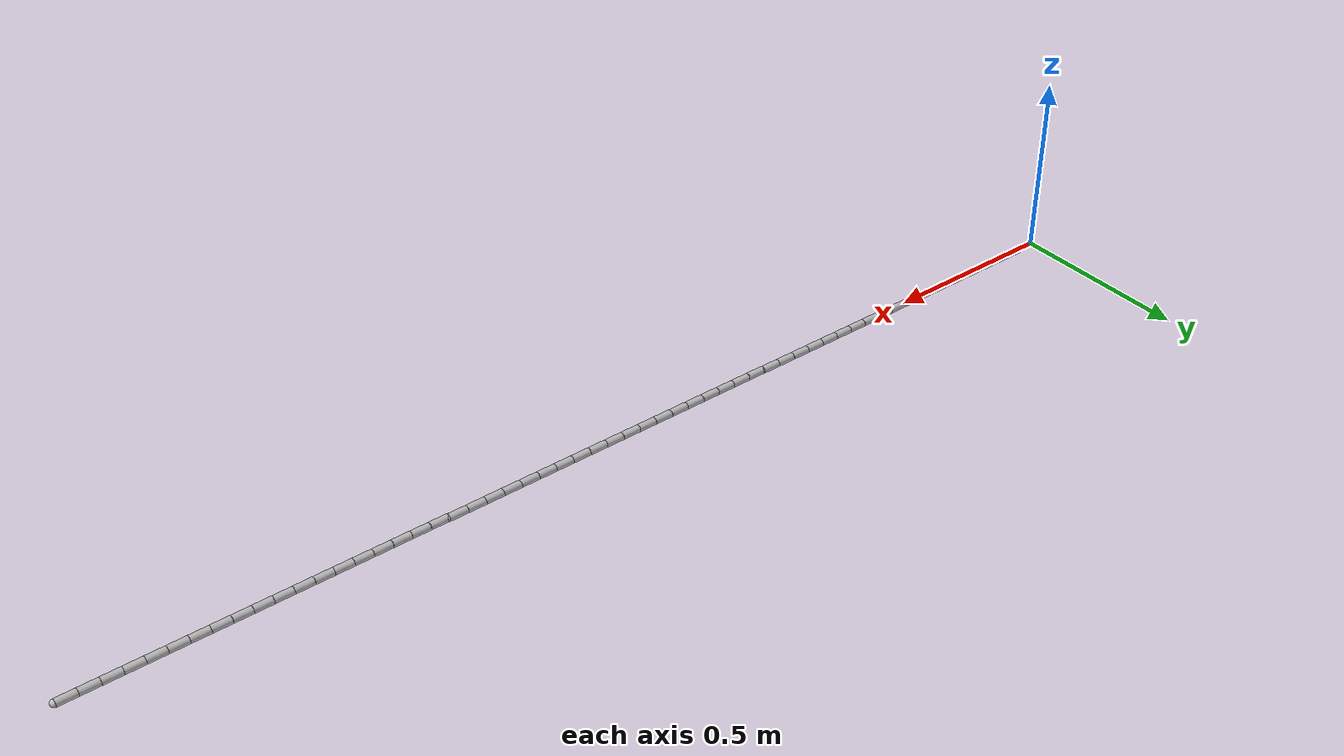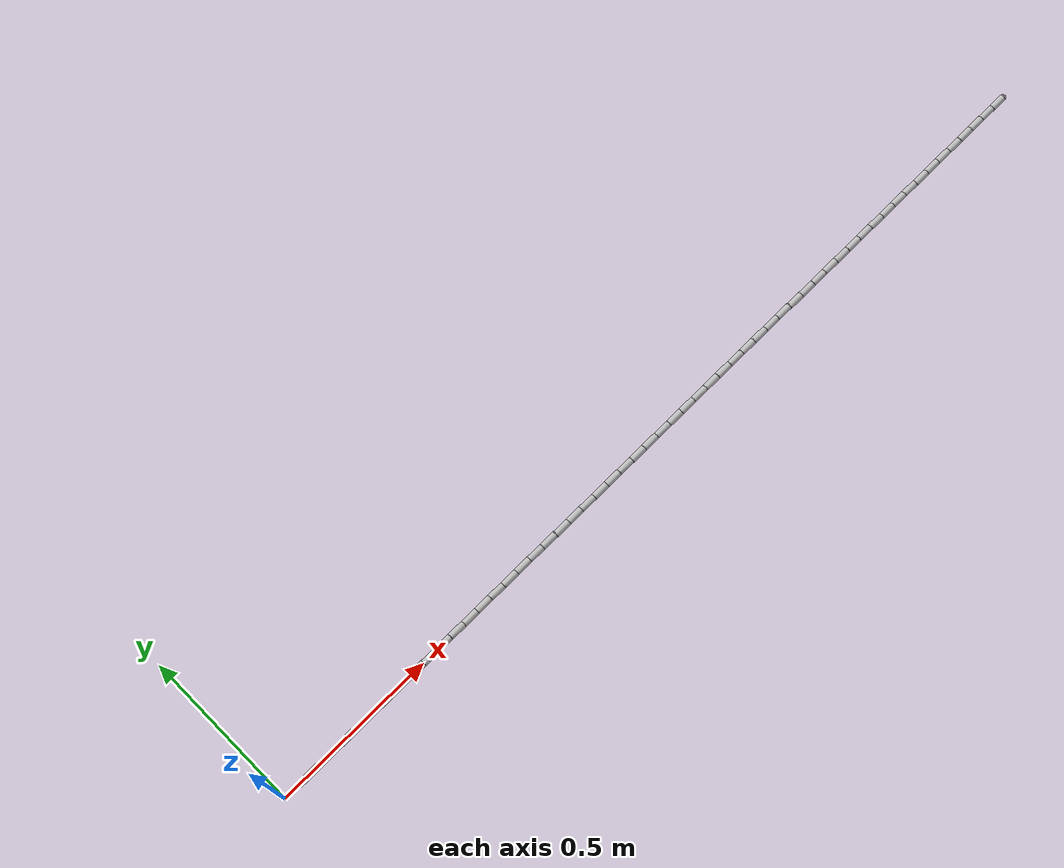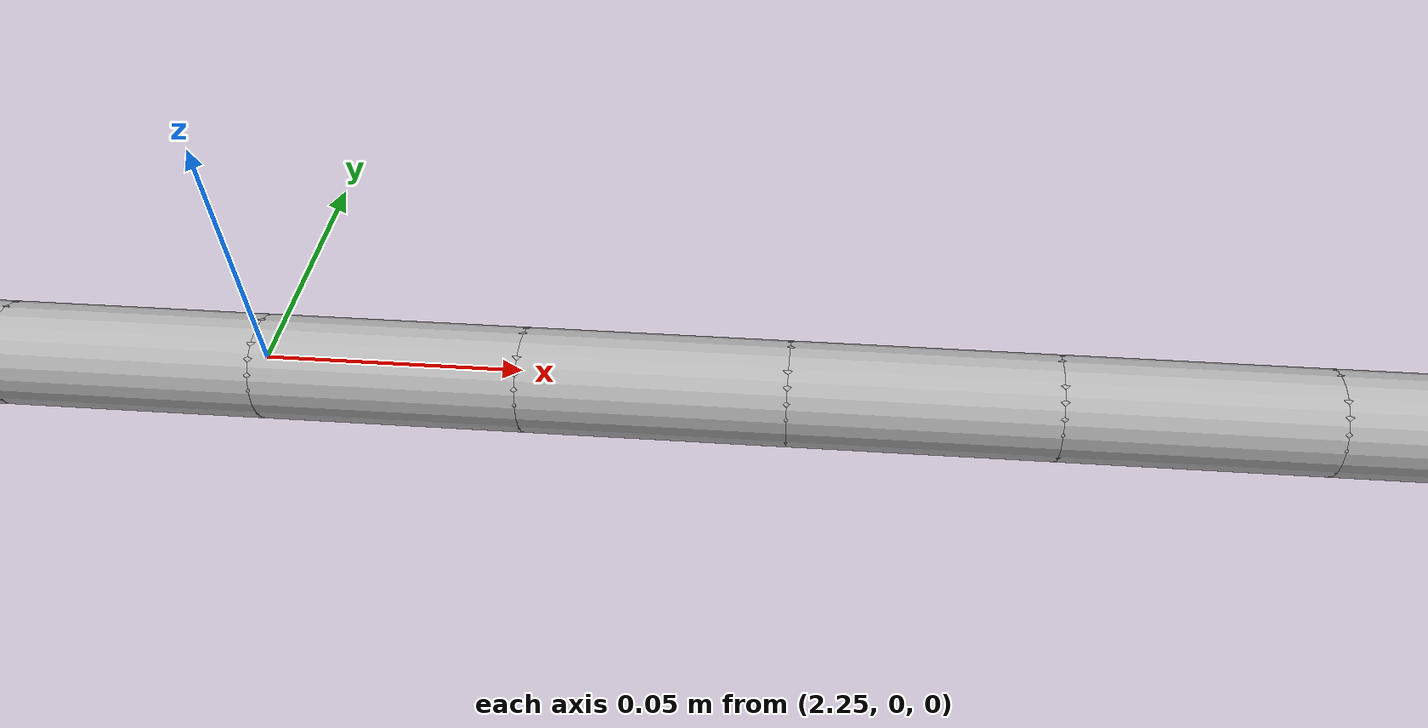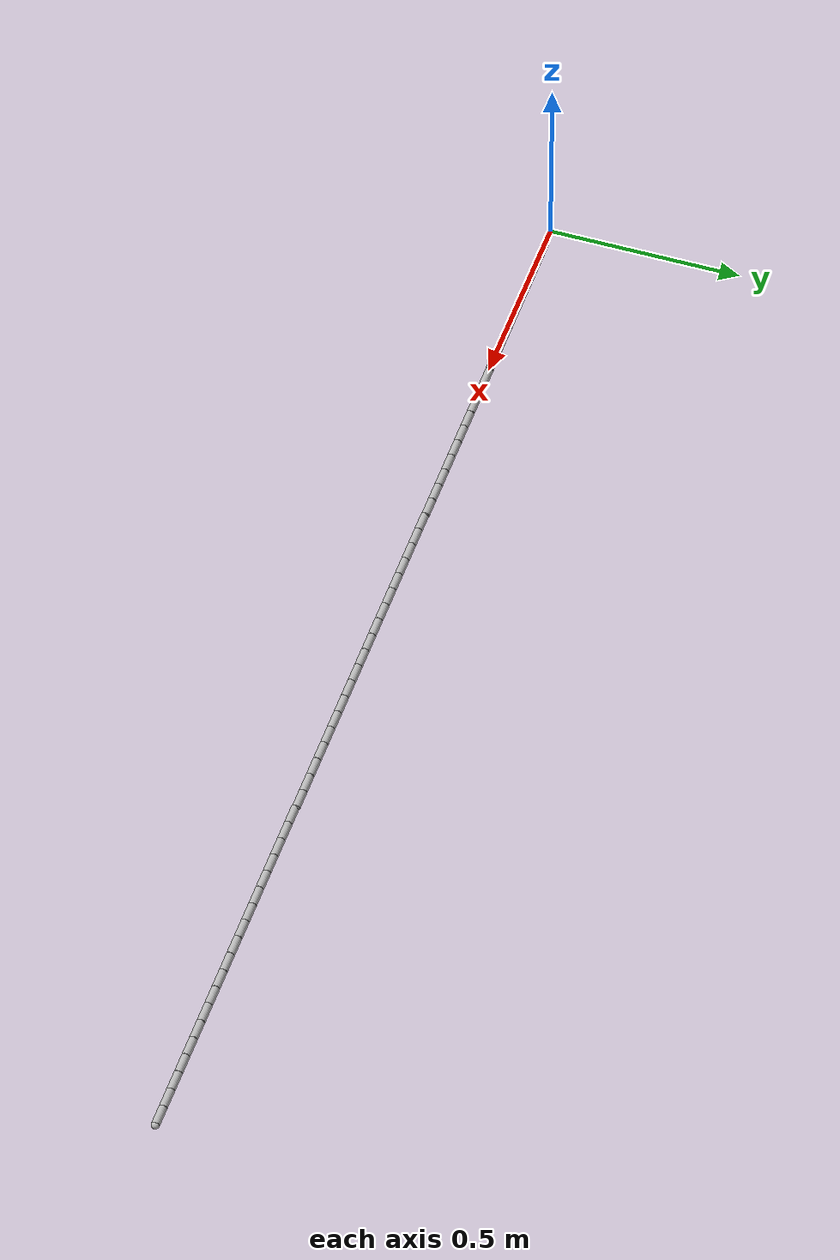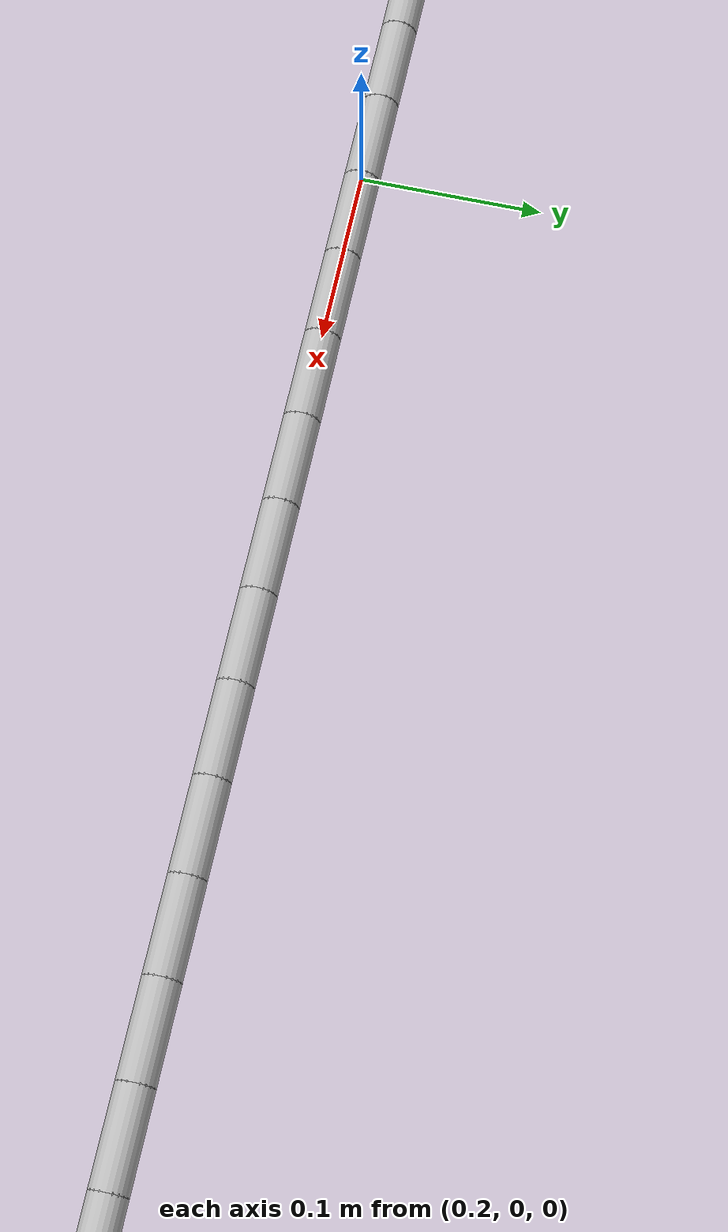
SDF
<?xml version='1.0'?>
<sdf version='1.7'>
  <model name='long_cable'>
    <link name='link_01'>
      <pose>0.05 0 0 0 -0 0</pose>
      <inertial>
        <pose>0 0 0 0 -0 0</pose>
        <mass>0.005</mass>
        <inertia>
          <ixx>0.01</ixx>
          <ixy>0</ixy>
          <ixz>0</ixz>
          <iyy>0.01</iyy>
          <iyz>0</iyz>
          <izz>0.01</izz>
        </inertia>
      </inertial>
      <velocity_decay/>
      <self_collide>0</self_collide>
      <enable_wind>0</enable_wind>
      <kinematic>0</kinematic>
      <visual name='link_01_vis'>
        <pose>0.025 0 0 0 1.57079 0</pose>
        <geometry>
          <cylinder>
            <length>0.05</length>
            <radius>0.01</radius>
          </cylinder>
        </geometry>
        <material>
          <shader type='pixel'/>
        </material>
        <transparency>0</transparency>
        <cast_shadows>1</cast_shadows>
      </visual>
      <collision name='link_01_collision'>
        <laser_retro>0</laser_retro>
        <max_contacts>10</max_contacts>
        <pose>0.025 0 0 0 1.57079 0</pose>
        <geometry>
          <cylinder>
            <radius>0.01</radius>
            <length>0.05</length>
          </cylinder>
        </geometry>
        <surface>
          <friction>
            <ode>
              <mu>1</mu>
              <mu2>1</mu2>
              <fdir1>0 0 0</fdir1>
              <slip1>0</slip1>
              <slip2>0</slip2>
            </ode>
            <torsional>
              <coefficient>1</coefficient>
              <patch_radius>0</patch_radius>
              <surface_radius>0</surface_radius>
              <use_patch_radius>1</use_patch_radius>
              <ode>
                <slip>0</slip>
              </ode>
            </torsional>
          </friction>
          <bounce>
            <restitution_coefficient>0</restitution_coefficient>
            <threshold>1e+06</threshold>
          </bounce>
          <contact>
            <collide_without_contact>0</collide_without_contact>
            <collide_without_contact_bitmask>1</collide_without_contact_bitmask>
            <collide_bitmask>1</collide_bitmask>
            <ode>
              <soft_cfm>0</soft_cfm>
              <soft_erp>0.2</soft_erp>
              <kp>1e+13</kp>
              <kd>1</kd>
              <max_vel>0.01</max_vel>
              <min_depth>0</min_depth>
            </ode>
            <bullet>
              <split_impulse>1</split_impulse>
              <split_impulse_penetration_threshold>-0.01</split_impulse_penetration_threshold>
              <soft_cfm>0</soft_cfm>
              <soft_erp>0.2</soft_erp>
              <kp>1e+13</kp>
              <kd>1</kd>
            </bullet>
          </contact>
        </surface>
      </collision>
    </link>
    <link name='link_02'>
      <pose>0.1 0 0 0 -0 0</pose>
      <inertial>
        <pose>0 0 0 0 -0 0</pose>
        <mass>0.005</mass>
        <inertia>
          <ixx>0.01</ixx>
          <ixy>0</ixy>
          <ixz>0</ixz>
          <iyy>0.01</iyy>
          <iyz>0</iyz>
          <izz>0.01</izz>
        </inertia>
      </inertial>
      <velocity_decay/>
      <self_collide>0</self_collide>
      <enable_wind>0</enable_wind>
      <kinematic>0</kinematic>
      <visual name='link_02_vis'>
        <pose>0.025 0 0 0 1.57079 0</pose>
        <geometry>
          <cylinder>
            <length>0.05</length>
            <radius>0.01</radius>
          </cylinder>
        </geometry>
        <material>
          <shader type='pixel'/>
        </material>
        <transparency>0</transparency>
        <cast_shadows>1</cast_shadows>
      </visual>
      <collision name='link_02_collision'>
        <laser_retro>0</laser_retro>
        <max_contacts>10</max_contacts>
        <pose>0.025 0 0 0 1.57079 0</pose>
        <geometry>
          <cylinder>
            <radius>0.01</radius>
            <length>0.05</length>
          </cylinder>
        </geometry>
        <surface>
          <friction>
            <ode>
              <mu>1</mu>
              <mu2>1</mu2>
              <fdir1>0 0 0</fdir1>
              <slip1>0</slip1>
              <slip2>0</slip2>
            </ode>
            <torsional>
              <coefficient>1</coefficient>
              <patch_radius>0</patch_radius>
              <surface_radius>0</surface_radius>
              <use_patch_radius>1</use_patch_radius>
              <ode>
                <slip>0</slip>
              </ode>
            </torsional>
          </friction>
          <bounce>
            <restitution_coefficient>0</restitution_coefficient>
            <threshold>1e+06</threshold>
          </bounce>
          <contact>
            <collide_without_contact>0</collide_without_contact>
            <collide_without_contact_bitmask>1</collide_without_contact_bitmask>
            <collide_bitmask>1</collide_bitmask>
            <ode>
              <soft_cfm>0</soft_cfm>
              <soft_erp>0.2</soft_erp>
              <kp>1e+13</kp>
              <kd>1</kd>
              <max_vel>0.01</max_vel>
              <min_depth>0</min_depth>
            </ode>
            <bullet>
              <split_impulse>1</split_impulse>
              <split_impulse_penetration_threshold>-0.01</split_impulse_penetration_threshold>
              <soft_cfm>0</soft_cfm>
              <soft_erp>0.2</soft_erp>
              <kp>1e+13</kp>
              <kd>1</kd>
            </bullet>
          </contact>
        </surface>
      </collision>
    </link>
    <link name='link_03'>
      <pose>0.15 0 0 0 -0 0</pose>
      <inertial>
        <pose>0 0 0 0 -0 0</pose>
        <mass>0.005</mass>
        <inertia>
          <ixx>0.01</ixx>
          <ixy>0</ixy>
          <ixz>0</ixz>
          <iyy>0.01</iyy>
          <iyz>0</iyz>
          <izz>0.01</izz>
        </inertia>
      </inertial>
      <velocity_decay/>
      <self_collide>0</self_collide>
      <enable_wind>0</enable_wind>
      <kinematic>0</kinematic>
      <visual name='link_03_vis'>
        <pose>0.025 0 0 0 1.57079 0</pose>
        <geometry>
          <cylinder>
            <length>0.05</length>
            <radius>0.01</radius>
          </cylinder>
        </geometry>
        <material>
          <shader type='pixel'/>
        </material>
        <transparency>0</transparency>
        <cast_shadows>1</cast_shadows>
      </visual>
      <collision name='link_03_collision'>
        <laser_retro>0</laser_retro>
        <max_contacts>10</max_contacts>
        <pose>0.025 0 0 0 1.57079 0</pose>
        <geometry>
          <cylinder>
            <radius>0.01</radius>
            <length>0.05</length>
          </cylinder>
        </geometry>
        <surface>
          <friction>
            <ode>
              <mu>1</mu>
              <mu2>1</mu2>
              <fdir1>0 0 0</fdir1>
              <slip1>0</slip1>
              <slip2>0</slip2>
            </ode>
            <torsional>
              <coefficient>1</coefficient>
              <patch_radius>0</patch_radius>
              <surface_radius>0</surface_radius>
              <use_patch_radius>1</use_patch_radius>
              <ode>
                <slip>0</slip>
              </ode>
            </torsional>
          </friction>
          <bounce>
            <restitution_coefficient>0</restitution_coefficient>
            <threshold>1e+06</threshold>
          </bounce>
          <contact>
            <collide_without_contact>0</collide_without_contact>
            <collide_without_contact_bitmask>1</collide_without_contact_bitmask>
            <collide_bitmask>1</collide_bitmask>
            <ode>
              <soft_cfm>0</soft_cfm>
              <soft_erp>0.2</soft_erp>
              <kp>1e+13</kp>
              <kd>1</kd>
              <max_vel>0.01</max_vel>
              <min_depth>0</min_depth>
            </ode>
            <bullet>
              <split_impulse>1</split_impulse>
              <split_impulse_penetration_threshold>-0.01</split_impulse_penetration_threshold>
              <soft_cfm>0</soft_cfm>
              <soft_erp>0.2</soft_erp>
              <kp>1e+13</kp>
              <kd>1</kd>
            </bullet>
          </contact>
        </surface>
      </collision>
    </link>
    <link name='link_04'>
      <pose>0.2 0 0 0 -0 0</pose>
      <inertial>
        <pose>0 0 0 0 -0 0</pose>
        <mass>0.005</mass>
        <inertia>
          <ixx>0.01</ixx>
          <ixy>0</ixy>
          <ixz>0</ixz>
          <iyy>0.01</iyy>
          <iyz>0</iyz>
          <izz>0.01</izz>
        </inertia>
      </inertial>
      <velocity_decay/>
      <self_collide>0</self_collide>
      <enable_wind>0</enable_wind>
      <kinematic>0</kinematic>
      <visual name='link_04_vis'>
        <pose>0.025 0 0 0 1.57079 0</pose>
        <geometry>
          <cylinder>
            <length>0.05</length>
            <radius>0.01</radius>
          </cylinder>
        </geometry>
        <material>
          <shader type='pixel'/>
        </material>
        <transparency>0</transparency>
        <cast_shadows>1</cast_shadows>
      </visual>
      <collision name='link_04_collision'>
        <laser_retro>0</laser_retro>
        <max_contacts>10</max_contacts>
        <pose>0.025 0 0 0 1.57079 0</pose>
        <geometry>
          <cylinder>
            <radius>0.01</radius>
            <length>0.05</length>
          </cylinder>
        </geometry>
        <surface>
          <friction>
            <ode>
              <mu>1</mu>
              <mu2>1</mu2>
              <fdir1>0 0 0</fdir1>
              <slip1>0</slip1>
              <slip2>0</slip2>
            </ode>
            <torsional>
              <coefficient>1</coefficient>
              <patch_radius>0</patch_radius>
              <surface_radius>0</surface_radius>
              <use_patch_radius>1</use_patch_radius>
              <ode>
                <slip>0</slip>
              </ode>
            </torsional>
          </friction>
          <bounce>
            <restitution_coefficient>0</restitution_coefficient>
            <threshold>1e+06</threshold>
          </bounce>
          <contact>
            <collide_without_contact>0</collide_without_contact>
            <collide_without_contact_bitmask>1</collide_without_contact_bitmask>
            <collide_bitmask>1</collide_bitmask>
            <ode>
              <soft_cfm>0</soft_cfm>
              <soft_erp>0.2</soft_erp>
              <kp>1e+13</kp>
              <kd>1</kd>
              <max_vel>0.01</max_vel>
              <min_depth>0</min_depth>
            </ode>
            <bullet>
              <split_impulse>1</split_impulse>
              <split_impulse_penetration_threshold>-0.01</split_impulse_penetration_threshold>
              <soft_cfm>0</soft_cfm>
              <soft_erp>0.2</soft_erp>
              <kp>1e+13</kp>
              <kd>1</kd>
            </bullet>
          </contact>
        </surface>
      </collision>
    </link>
    <link name='link_05'>
      <pose>0.25 0 0 0 -0 0</pose>
      <inertial>
        <pose>0 0 0 0 -0 0</pose>
        <mass>0.005</mass>
        <inertia>
          <ixx>0.01</ixx>
          <ixy>0</ixy>
          <ixz>0</ixz>
          <iyy>0.01</iyy>
          <iyz>0</iyz>
          <izz>0.01</izz>
        </inertia>
      </inertial>
      <velocity_decay/>
      <self_collide>0</self_collide>
      <enable_wind>0</enable_wind>
      <kinematic>0</kinematic>
      <visual name='link_05_vis'>
        <pose>0.025 0 0 0 1.57079 0</pose>
        <geometry>
          <cylinder>
            <length>0.05</length>
            <radius>0.01</radius>
          </cylinder>
        </geometry>
        <material>
          <shader type='pixel'/>
        </material>
        <transparency>0</transparency>
        <cast_shadows>1</cast_shadows>
      </visual>
      <collision name='link_05_collision'>
        <laser_retro>0</laser_retro>
        <max_contacts>10</max_contacts>
        <pose>0.025 0 0 0 1.57079 0</pose>
        <geometry>
          <cylinder>
            <radius>0.01</radius>
            <length>0.05</length>
          </cylinder>
        </geometry>
        <surface>
          <friction>
            <ode>
              <mu>1</mu>
              <mu2>1</mu2>
              <fdir1>0 0 0</fdir1>
              <slip1>0</slip1>
              <slip2>0</slip2>
            </ode>
            <torsional>
              <coefficient>1</coefficient>
              <patch_radius>0</patch_radius>
              <surface_radius>0</surface_radius>
              <use_patch_radius>1</use_patch_radius>
              <ode>
                <slip>0</slip>
              </ode>
            </torsional>
          </friction>
          <bounce>
            <restitution_coefficient>0</restitution_coefficient>
            <threshold>1e+06</threshold>
          </bounce>
          <contact>
            <collide_without_contact>0</collide_without_contact>
            <collide_without_contact_bitmask>1</collide_without_contact_bitmask>
            <collide_bitmask>1</collide_bitmask>
            <ode>
              <soft_cfm>0</soft_cfm>
              <soft_erp>0.2</soft_erp>
              <kp>1e+13</kp>
              <kd>1</kd>
              <max_vel>0.01</max_vel>
              <min_depth>0</min_depth>
            </ode>
            <bullet>
              <split_impulse>1</split_impulse>
              <split_impulse_penetration_threshold>-0.01</split_impulse_penetration_threshold>
              <soft_cfm>0</soft_cfm>
              <soft_erp>0.2</soft_erp>
              <kp>1e+13</kp>
              <kd>1</kd>
            </bullet>
          </contact>
        </surface>
      </collision>
    </link>
    <link name='link_06'>
      <pose>0.3 0 0 0 -0 0</pose>
      <inertial>
        <pose>0 0 0 0 -0 0</pose>
        <mass>0.005</mass>
        <inertia>
          <ixx>0.01</ixx>
          <ixy>0</ixy>
          <ixz>0</ixz>
          <iyy>0.01</iyy>
          <iyz>0</iyz>
          <izz>0.01</izz>
        </inertia>
      </inertial>
      <velocity_decay/>
      <self_collide>0</self_collide>
      <enable_wind>0</enable_wind>
      <kinematic>0</kinematic>
      <visual name='link_06_vis'>
        <pose>0.025 0 0 0 1.57079 0</pose>
        <geometry>
          <cylinder>
            <length>0.05</length>
            <radius>0.01</radius>
          </cylinder>
        </geometry>
        <material>
          <shader type='pixel'/>
        </material>
        <transparency>0</transparency>
        <cast_shadows>1</cast_shadows>
      </visual>
      <collision name='link_06_collision'>
        <laser_retro>0</laser_retro>
        <max_contacts>10</max_contacts>
        <pose>0.025 0 0 0 1.57079 0</pose>
        <geometry>
          <cylinder>
            <radius>0.01</radius>
            <length>0.05</length>
          </cylinder>
        </geometry>
        <surface>
          <friction>
            <ode>
              <mu>1</mu>
              <mu2>1</mu2>
              <fdir1>0 0 0</fdir1>
              <slip1>0</slip1>
              <slip2>0</slip2>
            </ode>
            <torsional>
              <coefficient>1</coefficient>
              <patch_radius>0</patch_radius>
              <surface_radius>0</surface_radius>
              <use_patch_radius>1</use_patch_radius>
              <ode>
                <slip>0</slip>
              </ode>
            </torsional>
          </friction>
          <bounce>
            <restitution_coefficient>0</restitution_coefficient>
            <threshold>1e+06</threshold>
          </bounce>
          <contact>
            <collide_without_contact>0</collide_without_contact>
            <collide_without_contact_bitmask>1</collide_without_contact_bitmask>
            <collide_bitmask>1</collide_bitmask>
            <ode>
              <soft_cfm>0</soft_cfm>
              <soft_erp>0.2</soft_erp>
              <kp>1e+13</kp>
              <kd>1</kd>
              <max_vel>0.01</max_vel>
              <min_depth>0</min_depth>
            </ode>
            <bullet>
              <split_impulse>1</split_impulse>
              <split_impulse_penetration_threshold>-0.01</split_impulse_penetration_threshold>
              <soft_cfm>0</soft_cfm>
              <soft_erp>0.2</soft_erp>
              <kp>1e+13</kp>
              <kd>1</kd>
            </bullet>
          </contact>
        </surface>
      </collision>
    </link>
    <link name='link_07'>
      <pose>0.35 0 0 0 -0 0</pose>
      <inertial>
        <pose>0 0 0 0 -0 0</pose>
        <mass>0.005</mass>
        <inertia>
          <ixx>0.01</ixx>
          <ixy>0</ixy>
          <ixz>0</ixz>
          <iyy>0.01</iyy>
          <iyz>0</iyz>
          <izz>0.01</izz>
        </inertia>
      </inertial>
      <velocity_decay/>
      <self_collide>0</self_collide>
      <enable_wind>0</enable_wind>
      <kinematic>0</kinematic>
      <visual name='link_07_vis'>
        <pose>0.025 0 0 0 1.57079 0</pose>
        <geometry>
          <cylinder>
            <length>0.05</length>
            <radius>0.01</radius>
          </cylinder>
        </geometry>
        <material>
          <shader type='pixel'/>
        </material>
        <transparency>0</transparency>
        <cast_shadows>1</cast_shadows>
      </visual>
      <collision name='link_07_collision'>
        <laser_retro>0</laser_retro>
        <max_contacts>10</max_contacts>
        <pose>0.025 0 0 0 1.57079 0</pose>
        <geometry>
          <cylinder>
            <radius>0.01</radius>
            <length>0.05</length>
          </cylinder>
        </geometry>
        <surface>
          <friction>
            <ode>
              <mu>1</mu>
              <mu2>1</mu2>
              <fdir1>0 0 0</fdir1>
              <slip1>0</slip1>
              <slip2>0</slip2>
            </ode>
            <torsional>
              <coefficient>1</coefficient>
              <patch_radius>0</patch_radius>
              <surface_radius>0</surface_radius>
              <use_patch_radius>1</use_patch_radius>
              <ode>
                <slip>0</slip>
              </ode>
            </torsional>
          </friction>
          <bounce>
            <restitution_coefficient>0</restitution_coefficient>
            <threshold>1e+06</threshold>
          </bounce>
          <contact>
            <collide_without_contact>0</collide_without_contact>
            <collide_without_contact_bitmask>1</collide_without_contact_bitmask>
            <collide_bitmask>1</collide_bitmask>
            <ode>
              <soft_cfm>0</soft_cfm>
              <soft_erp>0.2</soft_erp>
              <kp>1e+13</kp>
              <kd>1</kd>
              <max_vel>0.01</max_vel>
              <min_depth>0</min_depth>
            </ode>
            <bullet>
              <split_impulse>1</split_impulse>
              <split_impulse_penetration_threshold>-0.01</split_impulse_penetration_threshold>
              <soft_cfm>0</soft_cfm>
              <soft_erp>0.2</soft_erp>
              <kp>1e+13</kp>
              <kd>1</kd>
            </bullet>
          </contact>
        </surface>
      </collision>
    </link>
    <link name='link_08'>
      <pose>0.4 0 0 0 -0 0</pose>
      <inertial>
        <pose>0 0 0 0 -0 0</pose>
        <mass>0.005</mass>
        <inertia>
          <ixx>0.01</ixx>
          <ixy>0</ixy>
          <ixz>0</ixz>
          <iyy>0.01</iyy>
          <iyz>0</iyz>
          <izz>0.01</izz>
        </inertia>
      </inertial>
      <velocity_decay/>
      <self_collide>0</self_collide>
      <enable_wind>0</enable_wind>
      <kinematic>0</kinematic>
      <visual name='link_08_vis'>
        <pose>0.025 0 0 0 1.57079 0</pose>
        <geometry>
          <cylinder>
            <length>0.05</length>
            <radius>0.01</radius>
          </cylinder>
        </geometry>
        <material>
          <shader type='pixel'/>
        </material>
        <transparency>0</transparency>
        <cast_shadows>1</cast_shadows>
      </visual>
      <collision name='link_08_collision'>
        <laser_retro>0</laser_retro>
        <max_contacts>10</max_contacts>
        <pose>0.025 0 0 0 1.57079 0</pose>
        <geometry>
          <cylinder>
            <radius>0.01</radius>
            <length>0.05</length>
          </cylinder>
        </geometry>
        <surface>
          <friction>
            <ode>
              <mu>1</mu>
              <mu2>1</mu2>
              <fdir1>0 0 0</fdir1>
              <slip1>0</slip1>
              <slip2>0</slip2>
            </ode>
            <torsional>
              <coefficient>1</coefficient>
              <patch_radius>0</patch_radius>
              <surface_radius>0</surface_radius>
              <use_patch_radius>1</use_patch_radius>
              <ode>
                <slip>0</slip>
              </ode>
            </torsional>
          </friction>
          <bounce>
            <restitution_coefficient>0</restitution_coefficient>
            <threshold>1e+06</threshold>
          </bounce>
          <contact>
            <collide_without_contact>0</collide_without_contact>
            <collide_without_contact_bitmask>1</collide_without_contact_bitmask>
            <collide_bitmask>1</collide_bitmask>
            <ode>
              <soft_cfm>0</soft_cfm>
              <soft_erp>0.2</soft_erp>
              <kp>1e+13</kp>
              <kd>1</kd>
              <max_vel>0.01</max_vel>
              <min_depth>0</min_depth>
            </ode>
            <bullet>
              <split_impulse>1</split_impulse>
              <split_impulse_penetration_threshold>-0.01</split_impulse_penetration_threshold>
              <soft_cfm>0</soft_cfm>
              <soft_erp>0.2</soft_erp>
              <kp>1e+13</kp>
              <kd>1</kd>
            </bullet>
          </contact>
        </surface>
      </collision>
    </link>
    <link name='link_09'>
      <pose>0.45 0 0 0 -0 0</pose>
      <inertial>
        <pose>0 0 0 0 -0 0</pose>
        <mass>0.005</mass>
        <inertia>
          <ixx>0.01</ixx>
          <ixy>0</ixy>
          <ixz>0</ixz>
          <iyy>0.01</iyy>
          <iyz>0</iyz>
          <izz>0.01</izz>
        </inertia>
      </inertial>
      <velocity_decay/>
      <self_collide>0</self_collide>
      <enable_wind>0</enable_wind>
      <kinematic>0</kinematic>
      <visual name='link_09_vis'>
        <pose>0.025 0 0 0 1.57079 0</pose>
        <geometry>
          <cylinder>
            <length>0.05</length>
            <radius>0.01</radius>
          </cylinder>
        </geometry>
        <material>
          <shader type='pixel'/>
        </material>
        <transparency>0</transparency>
        <cast_shadows>1</cast_shadows>
      </visual>
      <collision name='link_09_collision'>
        <laser_retro>0</laser_retro>
        <max_contacts>10</max_contacts>
        <pose>0.025 0 0 0 1.57079 0</pose>
        <geometry>
          <cylinder>
            <radius>0.01</radius>
            <length>0.05</length>
          </cylinder>
        </geometry>
        <surface>
          <friction>
            <ode>
              <mu>1</mu>
              <mu2>1</mu2>
              <fdir1>0 0 0</fdir1>
              <slip1>0</slip1>
              <slip2>0</slip2>
            </ode>
            <torsional>
              <coefficient>1</coefficient>
              <patch_radius>0</patch_radius>
              <surface_radius>0</surface_radius>
              <use_patch_radius>1</use_patch_radius>
              <ode>
                <slip>0</slip>
              </ode>
            </torsional>
          </friction>
          <bounce>
            <restitution_coefficient>0</restitution_coefficient>
            <threshold>1e+06</threshold>
          </bounce>
          <contact>
            <collide_without_contact>0</collide_without_contact>
            <collide_without_contact_bitmask>1</collide_without_contact_bitmask>
            <collide_bitmask>1</collide_bitmask>
            <ode>
              <soft_cfm>0</soft_cfm>
              <soft_erp>0.2</soft_erp>
              <kp>1e+13</kp>
              <kd>1</kd>
              <max_vel>0.01</max_vel>
              <min_depth>0</min_depth>
            </ode>
            <bullet>
              <split_impulse>1</split_impulse>
              <split_impulse_penetration_threshold>-0.01</split_impulse_penetration_threshold>
              <soft_cfm>0</soft_cfm>
              <soft_erp>0.2</soft_erp>
              <kp>1e+13</kp>
              <kd>1</kd>
            </bullet>
          </contact>
        </surface>
      </collision>
    </link>
    <link name='link_10'>
      <pose>0.5 0 0 0 -0 0</pose>
      <inertial>
        <pose>0 0 0 0 -0 0</pose>
        <mass>0.005</mass>
        <inertia>
          <ixx>0.01</ixx>
          <ixy>0</ixy>
          <ixz>0</ixz>
          <iyy>0.01</iyy>
          <iyz>0</iyz>
          <izz>0.01</izz>
        </inertia>
      </inertial>
      <velocity_decay/>
      <self_collide>0</self_collide>
      <enable_wind>0</enable_wind>
      <kinematic>0</kinematic>
      <visual name='link_10_vis'>
        <pose>0.025 0 0 0 1.57079 0</pose>
        <geometry>
          <cylinder>
            <length>0.05</length>
            <radius>0.01</radius>
          </cylinder>
        </geometry>
        <material>
          <shader type='pixel'/>
        </material>
        <transparency>0</transparency>
        <cast_shadows>1</cast_shadows>
      </visual>
      <collision name='link_10_collision'>
        <laser_retro>0</laser_retro>
        <max_contacts>10</max_contacts>
        <pose>0.025 0 0 0 1.57079 0</pose>
        <geometry>
          <cylinder>
            <radius>0.01</radius>
            <length>0.05</length>
          </cylinder>
        </geometry>
        <surface>
          <friction>
            <ode>
              <mu>1</mu>
              <mu2>1</mu2>
              <fdir1>0 0 0</fdir1>
              <slip1>0</slip1>
              <slip2>0</slip2>
            </ode>
            <torsional>
              <coefficient>1</coefficient>
              <patch_radius>0</patch_radius>
              <surface_radius>0</surface_radius>
              <use_patch_radius>1</use_patch_radius>
              <ode>
                <slip>0</slip>
              </ode>
            </torsional>
          </friction>
          <bounce>
            <restitution_coefficient>0</restitution_coefficient>
            <threshold>1e+06</threshold>
          </bounce>
          <contact>
            <collide_without_contact>0</collide_without_contact>
            <collide_without_contact_bitmask>1</collide_without_contact_bitmask>
            <collide_bitmask>1</collide_bitmask>
            <ode>
              <soft_cfm>0</soft_cfm>
              <soft_erp>0.2</soft_erp>
              <kp>1e+13</kp>
              <kd>1</kd>
              <max_vel>0.01</max_vel>
              <min_depth>0</min_depth>
            </ode>
            <bullet>
              <split_impulse>1</split_impulse>
              <split_impulse_penetration_threshold>-0.01</split_impulse_penetration_threshold>
              <soft_cfm>0</soft_cfm>
              <soft_erp>0.2</soft_erp>
              <kp>1e+13</kp>
              <kd>1</kd>
            </bullet>
          </contact>
        </surface>
      </collision>
    </link>
    <link name='link_11'>
      <pose>0.55 0 0 0 -0 0</pose>
      <inertial>
        <pose>0 0 0 0 -0 0</pose>
        <mass>0.005</mass>
        <inertia>
          <ixx>0.01</ixx>
          <ixy>0</ixy>
          <ixz>0</ixz>
          <iyy>0.01</iyy>
          <iyz>0</iyz>
          <izz>0.01</izz>
        </inertia>
      </inertial>
      <velocity_decay/>
      <self_collide>0</self_collide>
      <enable_wind>0</enable_wind>
      <kinematic>0</kinematic>
      <visual name='link_11_vis'>
        <pose>0.025 0 0 0 1.57079 0</pose>
        <geometry>
          <cylinder>
            <length>0.05</length>
            <radius>0.01</radius>
          </cylinder>
        </geometry>
        <material>
          <shader type='pixel'/>
        </material>
        <transparency>0</transparency>
        <cast_shadows>1</cast_shadows>
      </visual>
      <collision name='link_11_collision'>
        <laser_retro>0</laser_retro>
        <max_contacts>10</max_contacts>
        <pose>0.025 0 0 0 1.57079 0</pose>
        <geometry>
          <cylinder>
            <radius>0.01</radius>
            <length>0.05</length>
          </cylinder>
        </geometry>
        <surface>
          <friction>
            <ode>
              <mu>1</mu>
              <mu2>1</mu2>
              <fdir1>0 0 0</fdir1>
              <slip1>0</slip1>
              <slip2>0</slip2>
            </ode>
            <torsional>
              <coefficient>1</coefficient>
              <patch_radius>0</patch_radius>
              <surface_radius>0</surface_radius>
              <use_patch_radius>1</use_patch_radius>
              <ode>
                <slip>0</slip>
              </ode>
            </torsional>
          </friction>
          <bounce>
            <restitution_coefficient>0</restitution_coefficient>
            <threshold>1e+06</threshold>
          </bounce>
          <contact>
            <collide_without_contact>0</collide_without_contact>
            <collide_without_contact_bitmask>1</collide_without_contact_bitmask>
            <collide_bitmask>1</collide_bitmask>
            <ode>
              <soft_cfm>0</soft_cfm>
              <soft_erp>0.2</soft_erp>
              <kp>1e+13</kp>
              <kd>1</kd>
              <max_vel>0.01</max_vel>
              <min_depth>0</min_depth>
            </ode>
            <bullet>
              <split_impulse>1</split_impulse>
              <split_impulse_penetration_threshold>-0.01</split_impulse_penetration_threshold>
              <soft_cfm>0</soft_cfm>
              <soft_erp>0.2</soft_erp>
              <kp>1e+13</kp>
              <kd>1</kd>
            </bullet>
          </contact>
        </surface>
      </collision>
    </link>
    <link name='link_12'>
      <pose>0.6 0 0 0 -0 0</pose>
      <inertial>
        <pose>0 0 0 0 -0 0</pose>
        <mass>0.005</mass>
        <inertia>
          <ixx>0.01</ixx>
          <ixy>0</ixy>
          <ixz>0</ixz>
          <iyy>0.01</iyy>
          <iyz>0</iyz>
          <izz>0.01</izz>
        </inertia>
      </inertial>
      <velocity_decay/>
      <self_collide>0</self_collide>
      <enable_wind>0</enable_wind>
      <kinematic>0</kinematic>
      <visual name='link_12_vis'>
        <pose>0.025 0 0 0 1.57079 0</pose>
        <geometry>
          <cylinder>
            <length>0.05</length>
            <radius>0.01</radius>
          </cylinder>
        </geometry>
        <material>
          <shader type='pixel'/>
        </material>
        <transparency>0</transparency>
        <cast_shadows>1</cast_shadows>
      </visual>
      <collision name='link_12_collision'>
        <laser_retro>0</laser_retro>
        <max_contacts>10</max_contacts>
        <pose>0.025 0 0 0 1.57079 0</pose>
        <geometry>
          <cylinder>
            <radius>0.01</radius>
            <length>0.05</length>
          </cylinder>
        </geometry>
        <surface>
          <friction>
            <ode>
              <mu>1</mu>
              <mu2>1</mu2>
              <fdir1>0 0 0</fdir1>
              <slip1>0</slip1>
              <slip2>0</slip2>
            </ode>
            <torsional>
              <coefficient>1</coefficient>
              <patch_radius>0</patch_radius>
              <surface_radius>0</surface_radius>
              <use_patch_radius>1</use_patch_radius>
              <ode>
                <slip>0</slip>
              </ode>
            </torsional>
          </friction>
          <bounce>
            <restitution_coefficient>0</restitution_coefficient>
            <threshold>1e+06</threshold>
          </bounce>
          <contact>
            <collide_without_contact>0</collide_without_contact>
            <collide_without_contact_bitmask>1</collide_without_contact_bitmask>
            <collide_bitmask>1</collide_bitmask>
            <ode>
              <soft_cfm>0</soft_cfm>
              <soft_erp>0.2</soft_erp>
              <kp>1e+13</kp>
              <kd>1</kd>
              <max_vel>0.01</max_vel>
              <min_depth>0</min_depth>
            </ode>
            <bullet>
              <split_impulse>1</split_impulse>
              <split_impulse_penetration_threshold>-0.01</split_impulse_penetration_threshold>
              <soft_cfm>0</soft_cfm>
              <soft_erp>0.2</soft_erp>
              <kp>1e+13</kp>
              <kd>1</kd>
            </bullet>
          </contact>
        </surface>
      </collision>
    </link>
    <link name='link_13'>
      <pose>0.65 0 0 0 -0 0</pose>
      <inertial>
        <pose>0 0 0 0 -0 0</pose>
        <mass>0.005</mass>
        <inertia>
          <ixx>0.01</ixx>
          <ixy>0</ixy>
          <ixz>0</ixz>
          <iyy>0.01</iyy>
          <iyz>0</iyz>
          <izz>0.01</izz>
        </inertia>
      </inertial>
      <velocity_decay/>
      <self_collide>0</self_collide>
      <enable_wind>0</enable_wind>
      <kinematic>0</kinematic>
      <visual name='link_13_vis'>
        <pose>0.025 0 0 0 1.57079 0</pose>
        <geometry>
          <cylinder>
            <length>0.05</length>
            <radius>0.01</radius>
          </cylinder>
        </geometry>
        <material>
          <shader type='pixel'/>
        </material>
        <transparency>0</transparency>
        <cast_shadows>1</cast_shadows>
      </visual>
      <collision name='link_13_collision'>
        <laser_retro>0</laser_retro>
        <max_contacts>10</max_contacts>
        <pose>0.025 0 0 0 1.57079 0</pose>
        <geometry>
          <cylinder>
            <radius>0.01</radius>
            <length>0.05</length>
          </cylinder>
        </geometry>
        <surface>
          <friction>
            <ode>
              <mu>1</mu>
              <mu2>1</mu2>
              <fdir1>0 0 0</fdir1>
              <slip1>0</slip1>
              <slip2>0</slip2>
            </ode>
            <torsional>
              <coefficient>1</coefficient>
              <patch_radius>0</patch_radius>
              <surface_radius>0</surface_radius>
              <use_patch_radius>1</use_patch_radius>
              <ode>
                <slip>0</slip>
              </ode>
            </torsional>
          </friction>
          <bounce>
            <restitution_coefficient>0</restitution_coefficient>
            <threshold>1e+06</threshold>
          </bounce>
          <contact>
            <collide_without_contact>0</collide_without_contact>
            <collide_without_contact_bitmask>1</collide_without_contact_bitmask>
            <collide_bitmask>1</collide_bitmask>
            <ode>
              <soft_cfm>0</soft_cfm>
              <soft_erp>0.2</soft_erp>
              <kp>1e+13</kp>
              <kd>1</kd>
              <max_vel>0.01</max_vel>
              <min_depth>0</min_depth>
            </ode>
            <bullet>
              <split_impulse>1</split_impulse>
              <split_impulse_penetration_threshold>-0.01</split_impulse_penetration_threshold>
              <soft_cfm>0</soft_cfm>
              <soft_erp>0.2</soft_erp>
              <kp>1e+13</kp>
              <kd>1</kd>
            </bullet>
          </contact>
        </surface>
      </collision>
    </link>
    <link name='link_14'>
      <pose>0.7 0 0 0 -0 0</pose>
      <inertial>
        <pose>0 0 0 0 -0 0</pose>
        <mass>0.005</mass>
        <inertia>
          <ixx>0.01</ixx>
          <ixy>0</ixy>
          <ixz>0</ixz>
          <iyy>0.01</iyy>
          <iyz>0</iyz>
          <izz>0.01</izz>
        </inertia>
      </inertial>
      <velocity_decay/>
      <self_collide>0</self_collide>
      <enable_wind>0</enable_wind>
      <kinematic>0</kinematic>
      <visual name='link_14_vis'>
        <pose>0.025 0 0 0 1.57079 0</pose>
        <geometry>
          <cylinder>
            <length>0.05</length>
            <radius>0.01</radius>
          </cylinder>
        </geometry>
        <material>
          <shader type='pixel'/>
        </material>
        <transparency>0</transparency>
        <cast_shadows>1</cast_shadows>
      </visual>
      <collision name='link_14_collision'>
        <laser_retro>0</laser_retro>
        <max_contacts>10</max_contacts>
        <pose>0.025 0 0 0 1.57079 0</pose>
        <geometry>
          <cylinder>
            <radius>0.01</radius>
            <length>0.05</length>
          </cylinder>
        </geometry>
        <surface>
          <friction>
            <ode>
              <mu>1</mu>
              <mu2>1</mu2>
              <fdir1>0 0 0</fdir1>
              <slip1>0</slip1>
              <slip2>0</slip2>
            </ode>
            <torsional>
              <coefficient>1</coefficient>
              <patch_radius>0</patch_radius>
              <surface_radius>0</surface_radius>
              <use_patch_radius>1</use_patch_radius>
              <ode>
                <slip>0</slip>
              </ode>
            </torsional>
          </friction>
          <bounce>
            <restitution_coefficient>0</restitution_coefficient>
            <threshold>1e+06</threshold>
          </bounce>
          <contact>
            <collide_without_contact>0</collide_without_contact>
            <collide_without_contact_bitmask>1</collide_without_contact_bitmask>
            <collide_bitmask>1</collide_bitmask>
            <ode>
              <soft_cfm>0</soft_cfm>
              <soft_erp>0.2</soft_erp>
              <kp>1e+13</kp>
              <kd>1</kd>
              <max_vel>0.01</max_vel>
              <min_depth>0</min_depth>
            </ode>
            <bullet>
              <split_impulse>1</split_impulse>
              <split_impulse_penetration_threshold>-0.01</split_impulse_penetration_threshold>
              <soft_cfm>0</soft_cfm>
              <soft_erp>0.2</soft_erp>
              <kp>1e+13</kp>
              <kd>1</kd>
            </bullet>
          </contact>
        </surface>
      </collision>
    </link>
    <link name='link_15'>
      <pose>0.75 0 0 0 -0 0</pose>
      <inertial>
        <pose>0 0 0 0 -0 0</pose>
        <mass>0.005</mass>
        <inertia>
          <ixx>0.01</ixx>
          <ixy>0</ixy>
          <ixz>0</ixz>
          <iyy>0.01</iyy>
          <iyz>0</iyz>
          <izz>0.01</izz>
        </inertia>
      </inertial>
      <velocity_decay/>
      <self_collide>0</self_collide>
      <enable_wind>0</enable_wind>
      <kinematic>0</kinematic>
      <visual name='link_15_vis'>
        <pose>0.025 0 0 0 1.57079 0</pose>
        <geometry>
          <cylinder>
            <length>0.05</length>
            <radius>0.01</radius>
          </cylinder>
        </geometry>
        <material>
          <shader type='pixel'/>
        </material>
        <transparency>0</transparency>
        <cast_shadows>1</cast_shadows>
      </visual>
      <collision name='link_15_collision'>
        <laser_retro>0</laser_retro>
        <max_contacts>10</max_contacts>
        <pose>0.025 0 0 0 1.57079 0</pose>
        <geometry>
          <cylinder>
            <radius>0.01</radius>
            <length>0.05</length>
          </cylinder>
        </geometry>
        <surface>
          <friction>
            <ode>
              <mu>1</mu>
              <mu2>1</mu2>
              <fdir1>0 0 0</fdir1>
              <slip1>0</slip1>
              <slip2>0</slip2>
            </ode>
            <torsional>
              <coefficient>1</coefficient>
              <patch_radius>0</patch_radius>
              <surface_radius>0</surface_radius>
              <use_patch_radius>1</use_patch_radius>
              <ode>
                <slip>0</slip>
              </ode>
            </torsional>
          </friction>
          <bounce>
            <restitution_coefficient>0</restitution_coefficient>
            <threshold>1e+06</threshold>
          </bounce>
          <contact>
            <collide_without_contact>0</collide_without_contact>
            <collide_without_contact_bitmask>1</collide_without_contact_bitmask>
            <collide_bitmask>1</collide_bitmask>
            <ode>
              <soft_cfm>0</soft_cfm>
              <soft_erp>0.2</soft_erp>
              <kp>1e+13</kp>
              <kd>1</kd>
              <max_vel>0.01</max_vel>
              <min_depth>0</min_depth>
            </ode>
            <bullet>
              <split_impulse>1</split_impulse>
              <split_impulse_penetration_threshold>-0.01</split_impulse_penetration_threshold>
              <soft_cfm>0</soft_cfm>
              <soft_erp>0.2</soft_erp>
              <kp>1e+13</kp>
              <kd>1</kd>
            </bullet>
          </contact>
        </surface>
      </collision>
    </link>
    <link name='link_16'>
      <pose>0.8 0 0 0 -0 0</pose>
      <inertial>
        <pose>0 0 0 0 -0 0</pose>
        <mass>0.005</mass>
        <inertia>
          <ixx>0.01</ixx>
          <ixy>0</ixy>
          <ixz>0</ixz>
          <iyy>0.01</iyy>
          <iyz>0</iyz>
          <izz>0.01</izz>
        </inertia>
      </inertial>
      <velocity_decay/>
      <self_collide>0</self_collide>
      <enable_wind>0</enable_wind>
      <kinematic>0</kinematic>
      <visual name='link_16_vis'>
        <pose>0.025 0 0 0 1.57079 0</pose>
        <geometry>
          <cylinder>
            <length>0.05</length>
            <radius>0.01</radius>
          </cylinder>
        </geometry>
        <material>
          <shader type='pixel'/>
        </material>
        <transparency>0</transparency>
        <cast_shadows>1</cast_shadows>
      </visual>
      <collision name='link_16_collision'>
        <laser_retro>0</laser_retro>
        <max_contacts>10</max_contacts>
        <pose>0.025 0 0 0 1.57079 0</pose>
        <geometry>
          <cylinder>
            <radius>0.01</radius>
            <length>0.05</length>
          </cylinder>
        </geometry>
        <surface>
          <friction>
            <ode>
              <mu>1</mu>
              <mu2>1</mu2>
              <fdir1>0 0 0</fdir1>
              <slip1>0</slip1>
              <slip2>0</slip2>
            </ode>
            <torsional>
              <coefficient>1</coefficient>
              <patch_radius>0</patch_radius>
              <surface_radius>0</surface_radius>
              <use_patch_radius>1</use_patch_radius>
              <ode>
                <slip>0</slip>
              </ode>
            </torsional>
          </friction>
          <bounce>
            <restitution_coefficient>0</restitution_coefficient>
            <threshold>1e+06</threshold>
          </bounce>
          <contact>
            <collide_without_contact>0</collide_without_contact>
            <collide_without_contact_bitmask>1</collide_without_contact_bitmask>
            <collide_bitmask>1</collide_bitmask>
            <ode>
              <soft_cfm>0</soft_cfm>
              <soft_erp>0.2</soft_erp>
              <kp>1e+13</kp>
              <kd>1</kd>
              <max_vel>0.01</max_vel>
              <min_depth>0</min_depth>
            </ode>
            <bullet>
              <split_impulse>1</split_impulse>
              <split_impulse_penetration_threshold>-0.01</split_impulse_penetration_threshold>
              <soft_cfm>0</soft_cfm>
              <soft_erp>0.2</soft_erp>
              <kp>1e+13</kp>
              <kd>1</kd>
            </bullet>
          </contact>
        </surface>
      </collision>
    </link>
    <link name='link_17'>
      <pose>0.85 0 0 0 -0 0</pose>
      <inertial>
        <pose>0 0 0 0 -0 0</pose>
        <mass>0.005</mass>
        <inertia>
          <ixx>0.01</ixx>
          <ixy>0</ixy>
          <ixz>0</ixz>
          <iyy>0.01</iyy>
          <iyz>0</iyz>
          <izz>0.01</izz>
        </inertia>
      </inertial>
      <velocity_decay/>
      <self_collide>0</self_collide>
      <enable_wind>0</enable_wind>
      <kinematic>0</kinematic>
      <visual name='link_17_vis'>
        <pose>0.025 0 0 0 1.57079 0</pose>
        <geometry>
          <cylinder>
            <length>0.05</length>
            <radius>0.01</radius>
          </cylinder>
        </geometry>
        <material>
          <shader type='pixel'/>
        </material>
        <transparency>0</transparency>
        <cast_shadows>1</cast_shadows>
      </visual>
      <collision name='link_17_collision'>
        <laser_retro>0</laser_retro>
        <max_contacts>10</max_contacts>
        <pose>0.025 0 0 0 1.57079 0</pose>
        <geometry>
          <cylinder>
            <radius>0.01</radius>
            <length>0.05</length>
          </cylinder>
        </geometry>
        <surface>
          <friction>
            <ode>
              <mu>1</mu>
              <mu2>1</mu2>
              <fdir1>0 0 0</fdir1>
              <slip1>0</slip1>
              <slip2>0</slip2>
            </ode>
            <torsional>
              <coefficient>1</coefficient>
              <patch_radius>0</patch_radius>
              <surface_radius>0</surface_radius>
              <use_patch_radius>1</use_patch_radius>
              <ode>
                <slip>0</slip>
              </ode>
            </torsional>
          </friction>
          <bounce>
            <restitution_coefficient>0</restitution_coefficient>
            <threshold>1e+06</threshold>
          </bounce>
          <contact>
            <collide_without_contact>0</collide_without_contact>
            <collide_without_contact_bitmask>1</collide_without_contact_bitmask>
            <collide_bitmask>1</collide_bitmask>
            <ode>
              <soft_cfm>0</soft_cfm>
              <soft_erp>0.2</soft_erp>
              <kp>1e+13</kp>
              <kd>1</kd>
              <max_vel>0.01</max_vel>
              <min_depth>0</min_depth>
            </ode>
            <bullet>
              <split_impulse>1</split_impulse>
              <split_impulse_penetration_threshold>-0.01</split_impulse_penetration_threshold>
              <soft_cfm>0</soft_cfm>
              <soft_erp>0.2</soft_erp>
              <kp>1e+13</kp>
              <kd>1</kd>
            </bullet>
          </contact>
        </surface>
      </collision>
    </link>
    <link name='link_18'>
      <pose>0.9 0 0 0 -0 0</pose>
      <inertial>
        <pose>0 0 0 0 -0 0</pose>
        <mass>0.005</mass>
        <inertia>
          <ixx>0.01</ixx>
          <ixy>0</ixy>
          <ixz>0</ixz>
          <iyy>0.01</iyy>
          <iyz>0</iyz>
          <izz>0.01</izz>
        </inertia>
      </inertial>
      <velocity_decay/>
      <self_collide>0</self_collide>
      <enable_wind>0</enable_wind>
      <kinematic>0</kinematic>
      <visual name='link_18_vis'>
        <pose>0.025 0 0 0 1.57079 0</pose>
        <geometry>
          <cylinder>
            <length>0.05</length>
            <radius>0.01</radius>
          </cylinder>
        </geometry>
        <material>
          <shader type='pixel'/>
        </material>
        <transparency>0</transparency>
        <cast_shadows>1</cast_shadows>
      </visual>
      <collision name='link_18_collision'>
        <laser_retro>0</laser_retro>
        <max_contacts>10</max_contacts>
        <pose>0.025 0 0 0 1.57079 0</pose>
        <geometry>
          <cylinder>
            <radius>0.01</radius>
            <length>0.05</length>
          </cylinder>
        </geometry>
        <surface>
          <friction>
            <ode>
              <mu>1</mu>
              <mu2>1</mu2>
              <fdir1>0 0 0</fdir1>
              <slip1>0</slip1>
              <slip2>0</slip2>
            </ode>
            <torsional>
              <coefficient>1</coefficient>
              <patch_radius>0</patch_radius>
              <surface_radius>0</surface_radius>
              <use_patch_radius>1</use_patch_radius>
              <ode>
                <slip>0</slip>
              </ode>
            </torsional>
          </friction>
          <bounce>
            <restitution_coefficient>0</restitution_coefficient>
            <threshold>1e+06</threshold>
          </bounce>
          <contact>
            <collide_without_contact>0</collide_without_contact>
            <collide_without_contact_bitmask>1</collide_without_contact_bitmask>
            <collide_bitmask>1</collide_bitmask>
            <ode>
              <soft_cfm>0</soft_cfm>
              <soft_erp>0.2</soft_erp>
              <kp>1e+13</kp>
              <kd>1</kd>
              <max_vel>0.01</max_vel>
              <min_depth>0</min_depth>
            </ode>
            <bullet>
              <split_impulse>1</split_impulse>
              <split_impulse_penetration_threshold>-0.01</split_impulse_penetration_threshold>
              <soft_cfm>0</soft_cfm>
              <soft_erp>0.2</soft_erp>
              <kp>1e+13</kp>
              <kd>1</kd>
            </bullet>
          </contact>
        </surface>
      </collision>
    </link>
    <link name='link_19'>
      <pose>0.95 0 0 0 -0 0</pose>
      <inertial>
        <pose>0 0 0 0 -0 0</pose>
        <mass>0.005</mass>
        <inertia>
          <ixx>0.01</ixx>
          <ixy>0</ixy>
          <ixz>0</ixz>
          <iyy>0.01</iyy>
          <iyz>0</iyz>
          <izz>0.01</izz>
        </inertia>
      </inertial>
      <velocity_decay/>
      <self_collide>0</self_collide>
      <enable_wind>0</enable_wind>
      <kinematic>0</kinematic>
      <visual name='link_19_vis'>
        <pose>0.025 0 0 0 1.57079 0</pose>
        <geometry>
          <cylinder>
            <length>0.05</length>
            <radius>0.01</radius>
          </cylinder>
        </geometry>
        <material>
          <shader type='pixel'/>
          <emissive>0 0 0 1</emissive>
        </material>
        <transparency>0</transparency>
        <cast_shadows>1</cast_shadows>
      </visual>
      <collision name='link_19_collision'>
        <laser_retro>0</laser_retro>
        <max_contacts>10</max_contacts>
        <pose>0.025 0 0 0 1.57079 0</pose>
        <geometry>
          <cylinder>
            <radius>0.01</radius>
            <length>0.05</length>
          </cylinder>
        </geometry>
        <surface>
          <friction>
            <ode>
              <mu>1</mu>
              <mu2>1</mu2>
              <fdir1>0 0 0</fdir1>
              <slip1>0</slip1>
              <slip2>0</slip2>
            </ode>
            <torsional>
              <coefficient>1</coefficient>
              <patch_radius>0</patch_radius>
              <surface_radius>0</surface_radius>
              <use_patch_radius>1</use_patch_radius>
              <ode>
                <slip>0</slip>
              </ode>
            </torsional>
          </friction>
          <bounce>
            <restitution_coefficient>0</restitution_coefficient>
            <threshold>1e+06</threshold>
          </bounce>
          <contact>
            <collide_without_contact>0</collide_without_contact>
            <collide_without_contact_bitmask>1</collide_without_contact_bitmask>
            <collide_bitmask>1</collide_bitmask>
            <ode>
              <soft_cfm>0</soft_cfm>
              <soft_erp>0.2</soft_erp>
              <kp>1e+13</kp>
              <kd>1</kd>
              <max_vel>0.01</max_vel>
              <min_depth>0</min_depth>
            </ode>
            <bullet>
              <split_impulse>1</split_impulse>
              <split_impulse_penetration_threshold>-0.01</split_impulse_penetration_threshold>
              <soft_cfm>0</soft_cfm>
              <soft_erp>0.2</soft_erp>
              <kp>1e+13</kp>
              <kd>1</kd>
            </bullet>
          </contact>
        </surface>
      </collision>
    </link>
    <link name='sphere_02'>
      <gravity>0</gravity>
      <pose>0.1 0 0 0 -0 0</pose>
      <inertial>
        <pose>0 0 0 0 -0 0</pose>
        <mass>0.005</mass>
        <inertia>
          <ixx>0.01</ixx>
          <ixy>0</ixy>
          <ixz>0</ixz>
          <iyy>0.01</iyy>
          <iyz>0</iyz>
          <izz>0.01</izz>
        </inertia>
      </inertial>
      <velocity_decay/>
      <self_collide>0</self_collide>
      <enable_wind>0</enable_wind>
      <kinematic>0</kinematic>
      <visual name='sphere_02_vis'>
        <pose>0 0 0 0 -0 0</pose>
        <geometry>
          <sphere>
            <radius>0.01</radius>
          </sphere>
        </geometry>
        <material>
          <shader type='pixel'/>
        </material>
        <transparency>0</transparency>
        <cast_shadows>1</cast_shadows>
      </visual>
      <collision name='sphere_02_collision'>
        <laser_retro>0</laser_retro>
        <max_contacts>10</max_contacts>
        <pose>0 0 0 0 -0 0</pose>
        <geometry>
          <sphere>
            <radius>0.01</radius>
          </sphere>
        </geometry>
        <surface>
          <friction>
            <ode>
              <mu>1</mu>
              <mu2>1</mu2>
              <fdir1>0 0 0</fdir1>
              <slip1>0</slip1>
              <slip2>0</slip2>
            </ode>
            <torsional>
              <coefficient>1</coefficient>
              <patch_radius>0</patch_radius>
              <surface_radius>0</surface_radius>
              <use_patch_radius>1</use_patch_radius>
              <ode>
                <slip>0</slip>
              </ode>
            </torsional>
          </friction>
          <bounce>
            <restitution_coefficient>0</restitution_coefficient>
            <threshold>1e+06</threshold>
          </bounce>
          <contact>
            <collide_without_contact>0</collide_without_contact>
            <collide_without_contact_bitmask>1</collide_without_contact_bitmask>
            <collide_bitmask>1</collide_bitmask>
            <ode>
              <soft_cfm>0</soft_cfm>
              <soft_erp>0.2</soft_erp>
              <kp>1e+13</kp>
              <kd>1</kd>
              <max_vel>0.01</max_vel>
              <min_depth>0</min_depth>
            </ode>
            <bullet>
              <split_impulse>1</split_impulse>
              <split_impulse_penetration_threshold>-0.01</split_impulse_penetration_threshold>
              <soft_cfm>0</soft_cfm>
              <soft_erp>0.2</soft_erp>
              <kp>1e+13</kp>
              <kd>1</kd>
            </bullet>
          </contact>
        </surface>
      </collision>
    </link>
    <link name='sphere_03'>
      <gravity>0</gravity>
      <pose>0.15 0 0 0 -0 0</pose>
      <inertial>
        <pose>0 0 0 0 -0 0</pose>
        <mass>0.005</mass>
        <inertia>
          <ixx>0.01</ixx>
          <ixy>0</ixy>
          <ixz>0</ixz>
          <iyy>0.01</iyy>
          <iyz>0</iyz>
          <izz>0.01</izz>
        </inertia>
      </inertial>
      <velocity_decay/>
      <self_collide>0</self_collide>
      <enable_wind>0</enable_wind>
      <kinematic>0</kinematic>
      <visual name='sphere_03_vis'>
        <pose>0 0 0 0 -0 0</pose>
        <geometry>
          <sphere>
            <radius>0.01</radius>
          </sphere>
        </geometry>
        <material>
          <shader type='pixel'/>
        </material>
        <transparency>0</transparency>
        <cast_shadows>1</cast_shadows>
      </visual>
      <collision name='sphere_03_collision'>
        <laser_retro>0</laser_retro>
        <max_contacts>10</max_contacts>
        <pose>0 0 0 0 -0 0</pose>
        <geometry>
          <sphere>
            <radius>0.01</radius>
          </sphere>
        </geometry>
        <surface>
          <friction>
            <ode>
              <mu>1</mu>
              <mu2>1</mu2>
              <fdir1>0 0 0</fdir1>
              <slip1>0</slip1>
              <slip2>0</slip2>
            </ode>
            <torsional>
              <coefficient>1</coefficient>
              <patch_radius>0</patch_radius>
              <surface_radius>0</surface_radius>
              <use_patch_radius>1</use_patch_radius>
              <ode>
                <slip>0</slip>
              </ode>
            </torsional>
          </friction>
          <bounce>
            <restitution_coefficient>0</restitution_coefficient>
            <threshold>1e+06</threshold>
          </bounce>
          <contact>
            <collide_without_contact>0</collide_without_contact>
            <collide_without_contact_bitmask>1</collide_without_contact_bitmask>
            <collide_bitmask>1</collide_bitmask>
            <ode>
              <soft_cfm>0</soft_cfm>
              <soft_erp>0.2</soft_erp>
              <kp>1e+13</kp>
              <kd>1</kd>
              <max_vel>0.01</max_vel>
              <min_depth>0</min_depth>
            </ode>
            <bullet>
              <split_impulse>1</split_impulse>
              <split_impulse_penetration_threshold>-0.01</split_impulse_penetration_threshold>
              <soft_cfm>0</soft_cfm>
              <soft_erp>0.2</soft_erp>
              <kp>1e+13</kp>
              <kd>1</kd>
            </bullet>
          </contact>
        </surface>
      </collision>
    </link>
    <link name='sphere_04'>
      <gravity>0</gravity>
      <pose>0.2 0 0 0 -0 0</pose>
      <inertial>
        <pose>0 0 0 0 -0 0</pose>
        <mass>0.005</mass>
        <inertia>
          <ixx>0.01</ixx>
          <ixy>0</ixy>
          <ixz>0</ixz>
          <iyy>0.01</iyy>
          <iyz>0</iyz>
          <izz>0.01</izz>
        </inertia>
      </inertial>
      <velocity_decay/>
      <self_collide>0</self_collide>
      <enable_wind>0</enable_wind>
      <kinematic>0</kinematic>
      <visual name='sphere_04_vis'>
        <pose>0 0 0 0 -0 0</pose>
        <geometry>
          <sphere>
            <radius>0.01</radius>
          </sphere>
        </geometry>
        <material>
          <shader type='pixel'/>
        </material>
        <transparency>0</transparency>
        <cast_shadows>1</cast_shadows>
      </visual>
      <collision name='sphere_04_collision'>
        <laser_retro>0</laser_retro>
        <max_contacts>10</max_contacts>
        <pose>0 0 0 0 -0 0</pose>
        <geometry>
          <sphere>
            <radius>0.01</radius>
          </sphere>
        </geometry>
        <surface>
          <friction>
            <ode>
              <mu>1</mu>
              <mu2>1</mu2>
              <fdir1>0 0 0</fdir1>
              <slip1>0</slip1>
              <slip2>0</slip2>
            </ode>
            <torsional>
              <coefficient>1</coefficient>
              <patch_radius>0</patch_radius>
              <surface_radius>0</surface_radius>
              <use_patch_radius>1</use_patch_radius>
              <ode>
                <slip>0</slip>
              </ode>
            </torsional>
          </friction>
          <bounce>
            <restitution_coefficient>0</restitution_coefficient>
            <threshold>1e+06</threshold>
          </bounce>
          <contact>
            <collide_without_contact>0</collide_without_contact>
            <collide_without_contact_bitmask>1</collide_without_contact_bitmask>
            <collide_bitmask>1</collide_bitmask>
            <ode>
              <soft_cfm>0</soft_cfm>
              <soft_erp>0.2</soft_erp>
              <kp>1e+13</kp>
              <kd>1</kd>
              <max_vel>0.01</max_vel>
              <min_depth>0</min_depth>
            </ode>
            <bullet>
              <split_impulse>1</split_impulse>
              <split_impulse_penetration_threshold>-0.01</split_impulse_penetration_threshold>
              <soft_cfm>0</soft_cfm>
              <soft_erp>0.2</soft_erp>
              <kp>1e+13</kp>
              <kd>1</kd>
            </bullet>
          </contact>
        </surface>
      </collision>
    </link>
    <link name='sphere_05'>
      <gravity>0</gravity>
      <pose>0.25 0 0 0 -0 0</pose>
      <inertial>
        <pose>0 0 0 0 -0 0</pose>
        <mass>0.005</mass>
        <inertia>
          <ixx>0.01</ixx>
          <ixy>0</ixy>
          <ixz>0</ixz>
          <iyy>0.01</iyy>
          <iyz>0</iyz>
          <izz>0.01</izz>
        </inertia>
      </inertial>
      <velocity_decay/>
      <self_collide>0</self_collide>
      <enable_wind>0</enable_wind>
      <kinematic>0</kinematic>
      <visual name='sphere_05_vis'>
        <pose>0 0 0 0 -0 0</pose>
        <geometry>
          <sphere>
            <radius>0.01</radius>
          </sphere>
        </geometry>
        <material>
          <shader type='pixel'/>
        </material>
        <transparency>0</transparency>
        <cast_shadows>1</cast_shadows>
      </visual>
      <collision name='sphere_05_collision'>
        <laser_retro>0</laser_retro>
        <max_contacts>10</max_contacts>
        <pose>0 0 0 0 -0 0</pose>
        <geometry>
          <sphere>
            <radius>0.01</radius>
          </sphere>
        </geometry>
        <surface>
          <friction>
            <ode>
              <mu>1</mu>
              <mu2>1</mu2>
              <fdir1>0 0 0</fdir1>
              <slip1>0</slip1>
              <slip2>0</slip2>
            </ode>
            <torsional>
              <coefficient>1</coefficient>
              <patch_radius>0</patch_radius>
              <surface_radius>0</surface_radius>
              <use_patch_radius>1</use_patch_radius>
              <ode>
                <slip>0</slip>
              </ode>
            </torsional>
          </friction>
          <bounce>
            <restitution_coefficient>0</restitution_coefficient>
            <threshold>1e+06</threshold>
          </bounce>
          <contact>
            <collide_without_contact>0</collide_without_contact>
            <collide_without_contact_bitmask>1</collide_without_contact_bitmask>
            <collide_bitmask>1</collide_bitmask>
            <ode>
              <soft_cfm>0</soft_cfm>
              <soft_erp>0.2</soft_erp>
              <kp>1e+13</kp>
              <kd>1</kd>
              <max_vel>0.01</max_vel>
              <min_depth>0</min_depth>
            </ode>
            <bullet>
              <split_impulse>1</split_impulse>
              <split_impulse_penetration_threshold>-0.01</split_impulse_penetration_threshold>
              <soft_cfm>0</soft_cfm>
              <soft_erp>0.2</soft_erp>
              <kp>1e+13</kp>
              <kd>1</kd>
            </bullet>
          </contact>
        </surface>
      </collision>
    </link>
    <link name='sphere_06'>
      <gravity>0</gravity>
      <pose>0.3 0 0 0 -0 0</pose>
      <inertial>
        <pose>0 0 0 0 -0 0</pose>
        <mass>0.005</mass>
        <inertia>
          <ixx>0.01</ixx>
          <ixy>0</ixy>
          <ixz>0</ixz>
          <iyy>0.01</iyy>
          <iyz>0</iyz>
          <izz>0.01</izz>
        </inertia>
      </inertial>
      <velocity_decay/>
      <self_collide>0</self_collide>
      <enable_wind>0</enable_wind>
      <kinematic>0</kinematic>
      <visual name='sphere_06_vis'>
        <pose>0 0 0 0 -0 0</pose>
        <geometry>
          <sphere>
            <radius>0.01</radius>
          </sphere>
        </geometry>
        <material>
          <shader type='pixel'/>
        </material>
        <transparency>0</transparency>
        <cast_shadows>1</cast_shadows>
      </visual>
      <collision name='sphere_06_collision'>
        <laser_retro>0</laser_retro>
        <max_contacts>10</max_contacts>
        <pose>0 0 0 0 -0 0</pose>
        <geometry>
          <sphere>
            <radius>0.01</radius>
          </sphere>
        </geometry>
        <surface>
          <friction>
            <ode>
              <mu>1</mu>
              <mu2>1</mu2>
              <fdir1>0 0 0</fdir1>
              <slip1>0</slip1>
              <slip2>0</slip2>
            </ode>
            <torsional>
              <coefficient>1</coefficient>
              <patch_radius>0</patch_radius>
              <surface_radius>0</surface_radius>
              <use_patch_radius>1</use_patch_radius>
              <ode>
                <slip>0</slip>
              </ode>
            </torsional>
          </friction>
          <bounce>
            <restitution_coefficient>0</restitution_coefficient>
            <threshold>1e+06</threshold>
          </bounce>
          <contact>
            <collide_without_contact>0</collide_without_contact>
            <collide_without_contact_bitmask>1</collide_without_contact_bitmask>
            <collide_bitmask>1</collide_bitmask>
            <ode>
              <soft_cfm>0</soft_cfm>
              <soft_erp>0.2</soft_erp>
              <kp>1e+13</kp>
              <kd>1</kd>
              <max_vel>0.01</max_vel>
              <min_depth>0</min_depth>
            </ode>
            <bullet>
              <split_impulse>1</split_impulse>
              <split_impulse_penetration_threshold>-0.01</split_impulse_penetration_threshold>
              <soft_cfm>0</soft_cfm>
              <soft_erp>0.2</soft_erp>
              <kp>1e+13</kp>
              <kd>1</kd>
            </bullet>
          </contact>
        </surface>
      </collision>
    </link>
    <link name='sphere_07'>
      <gravity>0</gravity>
      <pose>0.35 0 0 0 -0 0</pose>
      <inertial>
        <pose>0 0 0 0 -0 0</pose>
        <mass>0.005</mass>
        <inertia>
          <ixx>0.01</ixx>
          <ixy>0</ixy>
          <ixz>0</ixz>
          <iyy>0.01</iyy>
          <iyz>0</iyz>
          <izz>0.01</izz>
        </inertia>
      </inertial>
      <velocity_decay/>
      <self_collide>0</self_collide>
      <enable_wind>0</enable_wind>
      <kinematic>0</kinematic>
      <visual name='sphere_07_vis'>
        <pose>0 0 0 0 -0 0</pose>
        <geometry>
          <sphere>
            <radius>0.01</radius>
          </sphere>
        </geometry>
        <material>
          <shader type='pixel'/>
        </material>
        <transparency>0</transparency>
        <cast_shadows>1</cast_shadows>
      </visual>
      <collision name='sphere_07_collision'>
        <laser_retro>0</laser_retro>
        <max_contacts>10</max_contacts>
        <pose>0 0 0 0 -0 0</pose>
        <geometry>
          <sphere>
            <radius>0.01</radius>
          </sphere>
        </geometry>
        <surface>
          <friction>
            <ode>
              <mu>1</mu>
              <mu2>1</mu2>
              <fdir1>0 0 0</fdir1>
              <slip1>0</slip1>
              <slip2>0</slip2>
            </ode>
            <torsional>
              <coefficient>1</coefficient>
              <patch_radius>0</patch_radius>
              <surface_radius>0</surface_radius>
              <use_patch_radius>1</use_patch_radius>
              <ode>
                <slip>0</slip>
              </ode>
            </torsional>
          </friction>
          <bounce>
            <restitution_coefficient>0</restitution_coefficient>
            <threshold>1e+06</threshold>
          </bounce>
          <contact>
            <collide_without_contact>0</collide_without_contact>
            <collide_without_contact_bitmask>1</collide_without_contact_bitmask>
            <collide_bitmask>1</collide_bitmask>
            <ode>
              <soft_cfm>0</soft_cfm>
              <soft_erp>0.2</soft_erp>
              <kp>1e+13</kp>
              <kd>1</kd>
              <max_vel>0.01</max_vel>
              <min_depth>0</min_depth>
            </ode>
            <bullet>
              <split_impulse>1</split_impulse>
              <split_impulse_penetration_threshold>-0.01</split_impulse_penetration_threshold>
              <soft_cfm>0</soft_cfm>
              <soft_erp>0.2</soft_erp>
              <kp>1e+13</kp>
              <kd>1</kd>
            </bullet>
          </contact>
        </surface>
      </collision>
    </link>
    <link name='sphere_08'>
      <gravity>0</gravity>
      <pose>0.4 0 0 0 -0 0</pose>
      <inertial>
        <pose>0 0 0 0 -0 0</pose>
        <mass>0.005</mass>
        <inertia>
          <ixx>0.01</ixx>
          <ixy>0</ixy>
          <ixz>0</ixz>
          <iyy>0.01</iyy>
          <iyz>0</iyz>
          <izz>0.01</izz>
        </inertia>
      </inertial>
      <velocity_decay/>
      <self_collide>0</self_collide>
      <enable_wind>0</enable_wind>
      <kinematic>0</kinematic>
      <visual name='sphere_08_vis'>
        <pose>0 0 0 0 -0 0</pose>
        <geometry>
          <sphere>
            <radius>0.01</radius>
          </sphere>
        </geometry>
        <material>
          <shader type='pixel'/>
        </material>
        <transparency>0</transparency>
        <cast_shadows>1</cast_shadows>
      </visual>
      <collision name='sphere_08_collision'>
        <laser_retro>0</laser_retro>
        <max_contacts>10</max_contacts>
        <pose>0 0 0 0 -0 0</pose>
        <geometry>
          <sphere>
            <radius>0.01</radius>
          </sphere>
        </geometry>
        <surface>
          <friction>
            <ode>
              <mu>1</mu>
              <mu2>1</mu2>
              <fdir1>0 0 0</fdir1>
              <slip1>0</slip1>
              <slip2>0</slip2>
            </ode>
            <torsional>
              <coefficient>1</coefficient>
              <patch_radius>0</patch_radius>
              <surface_radius>0</surface_radius>
              <use_patch_radius>1</use_patch_radius>
              <ode>
                <slip>0</slip>
              </ode>
            </torsional>
          </friction>
          <bounce>
            <restitution_coefficient>0</restitution_coefficient>
            <threshold>1e+06</threshold>
          </bounce>
          <contact>
            <collide_without_contact>0</collide_without_contact>
            <collide_without_contact_bitmask>1</collide_without_contact_bitmask>
            <collide_bitmask>1</collide_bitmask>
            <ode>
              <soft_cfm>0</soft_cfm>
              <soft_erp>0.2</soft_erp>
              <kp>1e+13</kp>
              <kd>1</kd>
              <max_vel>0.01</max_vel>
              <min_depth>0</min_depth>
            </ode>
            <bullet>
              <split_impulse>1</split_impulse>
              <split_impulse_penetration_threshold>-0.01</split_impulse_penetration_threshold>
              <soft_cfm>0</soft_cfm>
              <soft_erp>0.2</soft_erp>
              <kp>1e+13</kp>
              <kd>1</kd>
            </bullet>
          </contact>
        </surface>
      </collision>
    </link>
    <link name='sphere_09'>
      <gravity>0</gravity>
      <pose>0.45 0 0 0 -0 0</pose>
      <inertial>
        <pose>0 0 0 0 -0 0</pose>
        <mass>0.005</mass>
        <inertia>
          <ixx>0.01</ixx>
          <ixy>0</ixy>
          <ixz>0</ixz>
          <iyy>0.01</iyy>
          <iyz>0</iyz>
          <izz>0.01</izz>
        </inertia>
      </inertial>
      <velocity_decay/>
      <self_collide>0</self_collide>
      <enable_wind>0</enable_wind>
      <kinematic>0</kinematic>
      <visual name='sphere_09_vis'>
        <pose>0 0 0 0 -0 0</pose>
        <geometry>
          <sphere>
            <radius>0.01</radius>
          </sphere>
        </geometry>
        <material>
          <shader type='pixel'/>
        </material>
        <transparency>0</transparency>
        <cast_shadows>1</cast_shadows>
      </visual>
      <collision name='sphere_09_collision'>
        <laser_retro>0</laser_retro>
        <max_contacts>10</max_contacts>
        <pose>0 0 0 0 -0 0</pose>
        <geometry>
          <sphere>
            <radius>0.01</radius>
          </sphere>
        </geometry>
        <surface>
          <friction>
            <ode>
              <mu>1</mu>
              <mu2>1</mu2>
              <fdir1>0 0 0</fdir1>
              <slip1>0</slip1>
              <slip2>0</slip2>
            </ode>
            <torsional>
              <coefficient>1</coefficient>
              <patch_radius>0</patch_radius>
              <surface_radius>0</surface_radius>
              <use_patch_radius>1</use_patch_radius>
              <ode>
                <slip>0</slip>
              </ode>
            </torsional>
          </friction>
          <bounce>
            <restitution_coefficient>0</restitution_coefficient>
            <threshold>1e+06</threshold>
          </bounce>
          <contact>
            <collide_without_contact>0</collide_without_contact>
            <collide_without_contact_bitmask>1</collide_without_contact_bitmask>
            <collide_bitmask>1</collide_bitmask>
            <ode>
              <soft_cfm>0</soft_cfm>
              <soft_erp>0.2</soft_erp>
              <kp>1e+13</kp>
              <kd>1</kd>
              <max_vel>0.01</max_vel>
              <min_depth>0</min_depth>
            </ode>
            <bullet>
              <split_impulse>1</split_impulse>
              <split_impulse_penetration_threshold>-0.01</split_impulse_penetration_threshold>
              <soft_cfm>0</soft_cfm>
              <soft_erp>0.2</soft_erp>
              <kp>1e+13</kp>
              <kd>1</kd>
            </bullet>
          </contact>
        </surface>
      </collision>
    </link>
    <link name='sphere_10'>
      <gravity>0</gravity>
      <pose>0.5 0 0 0 -0 0</pose>
      <inertial>
        <pose>0 0 0 0 -0 0</pose>
        <mass>0.005</mass>
        <inertia>
          <ixx>0.01</ixx>
          <ixy>0</ixy>
          <ixz>0</ixz>
          <iyy>0.01</iyy>
          <iyz>0</iyz>
          <izz>0.01</izz>
        </inertia>
      </inertial>
      <velocity_decay/>
      <self_collide>0</self_collide>
      <enable_wind>0</enable_wind>
      <kinematic>0</kinematic>
      <visual name='sphere_10_vis'>
        <pose>0 0 0 0 -0 0</pose>
        <geometry>
          <sphere>
            <radius>0.01</radius>
          </sphere>
        </geometry>
        <material>
          <shader type='pixel'/>
        </material>
        <transparency>0</transparency>
        <cast_shadows>1</cast_shadows>
      </visual>
      <collision name='sphere_10_collision'>
        <laser_retro>0</laser_retro>
        <max_contacts>10</max_contacts>
        <pose>0 0 0 0 -0 0</pose>
        <geometry>
          <sphere>
            <radius>0.01</radius>
          </sphere>
        </geometry>
        <surface>
          <friction>
            <ode>
              <mu>1</mu>
              <mu2>1</mu2>
              <fdir1>0 0 0</fdir1>
              <slip1>0</slip1>
              <slip2>0</slip2>
            </ode>
            <torsional>
              <coefficient>1</coefficient>
              <patch_radius>0</patch_radius>
              <surface_radius>0</surface_radius>
              <use_patch_radius>1</use_patch_radius>
              <ode>
                <slip>0</slip>
              </ode>
            </torsional>
          </friction>
          <bounce>
            <restitution_coefficient>0</restitution_coefficient>
            <threshold>1e+06</threshold>
          </bounce>
          <contact>
            <collide_without_contact>0</collide_without_contact>
            <collide_without_contact_bitmask>1</collide_without_contact_bitmask>
            <collide_bitmask>1</collide_bitmask>
            <ode>
              <soft_cfm>0</soft_cfm>
              <soft_erp>0.2</soft_erp>
              <kp>1e+13</kp>
              <kd>1</kd>
              <max_vel>0.01</max_vel>
              <min_depth>0</min_depth>
            </ode>
            <bullet>
              <split_impulse>1</split_impulse>
              <split_impulse_penetration_threshold>-0.01</split_impulse_penetration_threshold>
              <soft_cfm>0</soft_cfm>
              <soft_erp>0.2</soft_erp>
              <kp>1e+13</kp>
              <kd>1</kd>
            </bullet>
          </contact>
        </surface>
      </collision>
    </link>
    <link name='sphere_11'>
      <gravity>0</gravity>
      <pose>0.55 0 0 0 -0 0</pose>
      <inertial>
        <pose>0 0 0 0 -0 0</pose>
        <mass>0.005</mass>
        <inertia>
          <ixx>0.01</ixx>
          <ixy>0</ixy>
          <ixz>0</ixz>
          <iyy>0.01</iyy>
          <iyz>0</iyz>
          <izz>0.01</izz>
        </inertia>
      </inertial>
      <velocity_decay/>
      <self_collide>0</self_collide>
      <enable_wind>0</enable_wind>
      <kinematic>0</kinematic>
      <visual name='sphere_11_vis'>
        <pose>0 0 0 0 -0 0</pose>
        <geometry>
          <sphere>
            <radius>0.01</radius>
          </sphere>
        </geometry>
        <material>
          <shader type='pixel'/>
        </material>
        <transparency>0</transparency>
        <cast_shadows>1</cast_shadows>
      </visual>
      <collision name='sphere_11_collision'>
        <laser_retro>0</laser_retro>
        <max_contacts>10</max_contacts>
        <pose>0 0 0 0 -0 0</pose>
        <geometry>
          <sphere>
            <radius>0.01</radius>
          </sphere>
        </geometry>
        <surface>
          <friction>
            <ode>
              <mu>1</mu>
              <mu2>1</mu2>
              <fdir1>0 0 0</fdir1>
              <slip1>0</slip1>
              <slip2>0</slip2>
            </ode>
            <torsional>
              <coefficient>1</coefficient>
              <patch_radius>0</patch_radius>
              <surface_radius>0</surface_radius>
              <use_patch_radius>1</use_patch_radius>
              <ode>
                <slip>0</slip>
              </ode>
            </torsional>
          </friction>
          <bounce>
            <restitution_coefficient>0</restitution_coefficient>
            <threshold>1e+06</threshold>
          </bounce>
          <contact>
            <collide_without_contact>0</collide_without_contact>
            <collide_without_contact_bitmask>1</collide_without_contact_bitmask>
            <collide_bitmask>1</collide_bitmask>
            <ode>
              <soft_cfm>0</soft_cfm>
              <soft_erp>0.2</soft_erp>
              <kp>1e+13</kp>
              <kd>1</kd>
              <max_vel>0.01</max_vel>
              <min_depth>0</min_depth>
            </ode>
            <bullet>
              <split_impulse>1</split_impulse>
              <split_impulse_penetration_threshold>-0.01</split_impulse_penetration_threshold>
              <soft_cfm>0</soft_cfm>
              <soft_erp>0.2</soft_erp>
              <kp>1e+13</kp>
              <kd>1</kd>
            </bullet>
          </contact>
        </surface>
      </collision>
    </link>
    <link name='sphere_12'>
      <gravity>0</gravity>
      <pose>0.6 0 0 0 -0 0</pose>
      <inertial>
        <pose>0 0 0 0 -0 0</pose>
        <mass>0.005</mass>
        <inertia>
          <ixx>0.01</ixx>
          <ixy>0</ixy>
          <ixz>0</ixz>
          <iyy>0.01</iyy>
          <iyz>0</iyz>
          <izz>0.01</izz>
        </inertia>
      </inertial>
      <velocity_decay/>
      <self_collide>0</self_collide>
      <enable_wind>0</enable_wind>
      <kinematic>0</kinematic>
      <visual name='sphere_12_vis'>
        <pose>0 0 0 0 -0 0</pose>
        <geometry>
          <sphere>
            <radius>0.01</radius>
          </sphere>
        </geometry>
        <material>
          <shader type='pixel'/>
        </material>
        <transparency>0</transparency>
        <cast_shadows>1</cast_shadows>
      </visual>
      <collision name='sphere_12_collision'>
        <laser_retro>0</laser_retro>
        <max_contacts>10</max_contacts>
        <pose>0 0 0 0 -0 0</pose>
        <geometry>
          <sphere>
            <radius>0.01</radius>
          </sphere>
        </geometry>
        <surface>
          <friction>
            <ode>
              <mu>1</mu>
              <mu2>1</mu2>
              <fdir1>0 0 0</fdir1>
              <slip1>0</slip1>
              <slip2>0</slip2>
            </ode>
            <torsional>
              <coefficient>1</coefficient>
              <patch_radius>0</patch_radius>
              <surface_radius>0</surface_radius>
              <use_patch_radius>1</use_patch_radius>
              <ode>
                <slip>0</slip>
              </ode>
            </torsional>
          </friction>
          <bounce>
            <restitution_coefficient>0</restitution_coefficient>
            <threshold>1e+06</threshold>
          </bounce>
          <contact>
            <collide_without_contact>0</collide_without_contact>
            <collide_without_contact_bitmask>1</collide_without_contact_bitmask>
            <collide_bitmask>1</collide_bitmask>
            <ode>
              <soft_cfm>0</soft_cfm>
              <soft_erp>0.2</soft_erp>
              <kp>1e+13</kp>
              <kd>1</kd>
              <max_vel>0.01</max_vel>
              <min_depth>0</min_depth>
            </ode>
            <bullet>
              <split_impulse>1</split_impulse>
              <split_impulse_penetration_threshold>-0.01</split_impulse_penetration_threshold>
              <soft_cfm>0</soft_cfm>
              <soft_erp>0.2</soft_erp>
              <kp>1e+13</kp>
              <kd>1</kd>
            </bullet>
          </contact>
        </surface>
      </collision>
    </link>
    <link name='sphere_13'>
      <gravity>0</gravity>
      <pose>0.65 0 0 0 -0 0</pose>
      <inertial>
        <pose>0 0 0 0 -0 0</pose>
        <mass>0.005</mass>
        <inertia>
          <ixx>0.01</ixx>
          <ixy>0</ixy>
          <ixz>0</ixz>
          <iyy>0.01</iyy>
          <iyz>0</iyz>
          <izz>0.01</izz>
        </inertia>
      </inertial>
      <velocity_decay/>
      <self_collide>0</self_collide>
      <enable_wind>0</enable_wind>
      <kinematic>0</kinematic>
      <visual name='sphere_13_vis'>
        <pose>0 0 0 0 -0 0</pose>
        <geometry>
          <sphere>
            <radius>0.01</radius>
          </sphere>
        </geometry>
        <material>
          <shader type='pixel'/>
        </material>
        <transparency>0</transparency>
        <cast_shadows>1</cast_shadows>
      </visual>
      <collision name='sphere_13_collision'>
        <laser_retro>0</laser_retro>
        <max_contacts>10</max_contacts>
        <pose>0 0 0 0 -0 0</pose>
        <geometry>
          <sphere>
            <radius>0.01</radius>
          </sphere>
        </geometry>
        <surface>
          <friction>
            <ode>
              <mu>1</mu>
              <mu2>1</mu2>
              <fdir1>0 0 0</fdir1>
              <slip1>0</slip1>
              <slip2>0</slip2>
            </ode>
            <torsional>
              <coefficient>1</coefficient>
              <patch_radius>0</patch_radius>
              <surface_radius>0</surface_radius>
              <use_patch_radius>1</use_patch_radius>
              <ode>
                <slip>0</slip>
              </ode>
            </torsional>
          </friction>
          <bounce>
            <restitution_coefficient>0</restitution_coefficient>
            <threshold>1e+06</threshold>
          </bounce>
          <contact>
            <collide_without_contact>0</collide_without_contact>
            <collide_without_contact_bitmask>1</collide_without_contact_bitmask>
            <collide_bitmask>1</collide_bitmask>
            <ode>
              <soft_cfm>0</soft_cfm>
              <soft_erp>0.2</soft_erp>
              <kp>1e+13</kp>
              <kd>1</kd>
              <max_vel>0.01</max_vel>
              <min_depth>0</min_depth>
            </ode>
            <bullet>
              <split_impulse>1</split_impulse>
              <split_impulse_penetration_threshold>-0.01</split_impulse_penetration_threshold>
              <soft_cfm>0</soft_cfm>
              <soft_erp>0.2</soft_erp>
              <kp>1e+13</kp>
              <kd>1</kd>
            </bullet>
          </contact>
        </surface>
      </collision>
    </link>
    <link name='sphere_14'>
      <gravity>0</gravity>
      <pose>0.7 0 0 0 -0 0</pose>
      <inertial>
        <pose>0 0 0 0 -0 0</pose>
        <mass>0.005</mass>
        <inertia>
          <ixx>0.01</ixx>
          <ixy>0</ixy>
          <ixz>0</ixz>
          <iyy>0.01</iyy>
          <iyz>0</iyz>
          <izz>0.01</izz>
        </inertia>
      </inertial>
      <velocity_decay/>
      <self_collide>0</self_collide>
      <enable_wind>0</enable_wind>
      <kinematic>0</kinematic>
      <visual name='sphere_14_vis'>
        <pose>0 0 0 0 -0 0</pose>
        <geometry>
          <sphere>
            <radius>0.01</radius>
          </sphere>
        </geometry>
        <material>
          <shader type='pixel'/>
        </material>
        <transparency>0</transparency>
        <cast_shadows>1</cast_shadows>
      </visual>
      <collision name='sphere_14_collision'>
        <laser_retro>0</laser_retro>
        <max_contacts>10</max_contacts>
        <pose>0 0 0 0 -0 0</pose>
        <geometry>
          <sphere>
            <radius>0.01</radius>
          </sphere>
        </geometry>
        <surface>
          <friction>
            <ode>
              <mu>1</mu>
              <mu2>1</mu2>
              <fdir1>0 0 0</fdir1>
              <slip1>0</slip1>
              <slip2>0</slip2>
            </ode>
            <torsional>
              <coefficient>1</coefficient>
              <patch_radius>0</patch_radius>
              <surface_radius>0</surface_radius>
              <use_patch_radius>1</use_patch_radius>
              <ode>
                <slip>0</slip>
              </ode>
            </torsional>
          </friction>
          <bounce>
            <restitution_coefficient>0</restitution_coefficient>
            <threshold>1e+06</threshold>
          </bounce>
          <contact>
            <collide_without_contact>0</collide_without_contact>
            <collide_without_contact_bitmask>1</collide_without_contact_bitmask>
            <collide_bitmask>1</collide_bitmask>
            <ode>
              <soft_cfm>0</soft_cfm>
              <soft_erp>0.2</soft_erp>
              <kp>1e+13</kp>
              <kd>1</kd>
              <max_vel>0.01</max_vel>
              <min_depth>0</min_depth>
            </ode>
            <bullet>
              <split_impulse>1</split_impulse>
              <split_impulse_penetration_threshold>-0.01</split_impulse_penetration_threshold>
              <soft_cfm>0</soft_cfm>
              <soft_erp>0.2</soft_erp>
              <kp>1e+13</kp>
              <kd>1</kd>
            </bullet>
          </contact>
        </surface>
      </collision>
    </link>
    <link name='sphere_15'>
      <gravity>0</gravity>
      <pose>0.75 0 0 0 -0 0</pose>
      <inertial>
        <pose>0 0 0 0 -0 0</pose>
        <mass>0.005</mass>
        <inertia>
          <ixx>0.01</ixx>
          <ixy>0</ixy>
          <ixz>0</ixz>
          <iyy>0.01</iyy>
          <iyz>0</iyz>
          <izz>0.01</izz>
        </inertia>
      </inertial>
      <velocity_decay/>
      <self_collide>0</self_collide>
      <enable_wind>0</enable_wind>
      <kinematic>0</kinematic>
      <visual name='sphere_15_vis'>
        <pose>0 0 0 0 -0 0</pose>
        <geometry>
          <sphere>
            <radius>0.01</radius>
          </sphere>
        </geometry>
        <material>
          <shader type='pixel'/>
        </material>
        <transparency>0</transparency>
        <cast_shadows>1</cast_shadows>
      </visual>
      <collision name='sphere_15_collision'>
        <laser_retro>0</laser_retro>
        <max_contacts>10</max_contacts>
        <pose>0 0 0 0 -0 0</pose>
        <geometry>
          <sphere>
            <radius>0.01</radius>
          </sphere>
        </geometry>
        <surface>
          <friction>
            <ode>
              <mu>1</mu>
              <mu2>1</mu2>
              <fdir1>0 0 0</fdir1>
              <slip1>0</slip1>
              <slip2>0</slip2>
            </ode>
            <torsional>
              <coefficient>1</coefficient>
              <patch_radius>0</patch_radius>
              <surface_radius>0</surface_radius>
              <use_patch_radius>1</use_patch_radius>
              <ode>
                <slip>0</slip>
              </ode>
            </torsional>
          </friction>
          <bounce>
            <restitution_coefficient>0</restitution_coefficient>
            <threshold>1e+06</threshold>
          </bounce>
          <contact>
            <collide_without_contact>0</collide_without_contact>
            <collide_without_contact_bitmask>1</collide_without_contact_bitmask>
            <collide_bitmask>1</collide_bitmask>
            <ode>
              <soft_cfm>0</soft_cfm>
              <soft_erp>0.2</soft_erp>
              <kp>1e+13</kp>
              <kd>1</kd>
              <max_vel>0.01</max_vel>
              <min_depth>0</min_depth>
            </ode>
            <bullet>
              <split_impulse>1</split_impulse>
              <split_impulse_penetration_threshold>-0.01</split_impulse_penetration_threshold>
              <soft_cfm>0</soft_cfm>
              <soft_erp>0.2</soft_erp>
              <kp>1e+13</kp>
              <kd>1</kd>
            </bullet>
          </contact>
        </surface>
      </collision>
    </link>
    <link name='sphere_16'>
      <gravity>0</gravity>
      <pose>0.8 0 0 0 -0 0</pose>
      <inertial>
        <pose>0 0 0 0 -0 0</pose>
        <mass>0.005</mass>
        <inertia>
          <ixx>0.01</ixx>
          <ixy>0</ixy>
          <ixz>0</ixz>
          <iyy>0.01</iyy>
          <iyz>0</iyz>
          <izz>0.01</izz>
        </inertia>
      </inertial>
      <velocity_decay/>
      <self_collide>0</self_collide>
      <enable_wind>0</enable_wind>
      <kinematic>0</kinematic>
      <visual name='sphere_16_vis'>
        <pose>0 0 0 0 -0 0</pose>
        <geometry>
          <sphere>
            <radius>0.01</radius>
          </sphere>
        </geometry>
        <material>
          <shader type='pixel'/>
        </material>
        <transparency>0</transparency>
        <cast_shadows>1</cast_shadows>
      </visual>
      <collision name='sphere_16_collision'>
        <laser_retro>0</laser_retro>
        <max_contacts>10</max_contacts>
        <pose>0 0 0 0 -0 0</pose>
        <geometry>
          <sphere>
            <radius>0.01</radius>
          </sphere>
        </geometry>
        <surface>
          <friction>
            <ode>
              <mu>1</mu>
              <mu2>1</mu2>
              <fdir1>0 0 0</fdir1>
              <slip1>0</slip1>
              <slip2>0</slip2>
            </ode>
            <torsional>
              <coefficient>1</coefficient>
              <patch_radius>0</patch_radius>
              <surface_radius>0</surface_radius>
              <use_patch_radius>1</use_patch_radius>
              <ode>
                <slip>0</slip>
              </ode>
            </torsional>
          </friction>
          <bounce>
            <restitution_coefficient>0</restitution_coefficient>
            <threshold>1e+06</threshold>
          </bounce>
          <contact>
            <collide_without_contact>0</collide_without_contact>
            <collide_without_contact_bitmask>1</collide_without_contact_bitmask>
            <collide_bitmask>1</collide_bitmask>
            <ode>
              <soft_cfm>0</soft_cfm>
              <soft_erp>0.2</soft_erp>
              <kp>1e+13</kp>
              <kd>1</kd>
              <max_vel>0.01</max_vel>
              <min_depth>0</min_depth>
            </ode>
            <bullet>
              <split_impulse>1</split_impulse>
              <split_impulse_penetration_threshold>-0.01</split_impulse_penetration_threshold>
              <soft_cfm>0</soft_cfm>
              <soft_erp>0.2</soft_erp>
              <kp>1e+13</kp>
              <kd>1</kd>
            </bullet>
          </contact>
        </surface>
      </collision>
    </link>
    <link name='sphere_17'>
      <gravity>0</gravity>
      <pose>0.85 0 0 0 -0 0</pose>
      <inertial>
        <pose>0 0 0 0 -0 0</pose>
        <mass>0.005</mass>
        <inertia>
          <ixx>0.01</ixx>
          <ixy>0</ixy>
          <ixz>0</ixz>
          <iyy>0.01</iyy>
          <iyz>0</iyz>
          <izz>0.01</izz>
        </inertia>
      </inertial>
      <velocity_decay/>
      <self_collide>0</self_collide>
      <enable_wind>0</enable_wind>
      <kinematic>0</kinematic>
      <visual name='sphere_17_vis'>
        <pose>0 0 0 0 -0 0</pose>
        <geometry>
          <sphere>
            <radius>0.01</radius>
          </sphere>
        </geometry>
        <material>
          <shader type='pixel'/>
        </material>
        <transparency>0</transparency>
        <cast_shadows>1</cast_shadows>
      </visual>
      <collision name='sphere_17_collision'>
        <laser_retro>0</laser_retro>
        <max_contacts>10</max_contacts>
        <pose>0 0 0 0 -0 0</pose>
        <geometry>
          <sphere>
            <radius>0.01</radius>
          </sphere>
        </geometry>
        <surface>
          <friction>
            <ode>
              <mu>1</mu>
              <mu2>1</mu2>
              <fdir1>0 0 0</fdir1>
              <slip1>0</slip1>
              <slip2>0</slip2>
            </ode>
            <torsional>
              <coefficient>1</coefficient>
              <patch_radius>0</patch_radius>
              <surface_radius>0</surface_radius>
              <use_patch_radius>1</use_patch_radius>
              <ode>
                <slip>0</slip>
              </ode>
            </torsional>
          </friction>
          <bounce>
            <restitution_coefficient>0</restitution_coefficient>
            <threshold>1e+06</threshold>
          </bounce>
          <contact>
            <collide_without_contact>0</collide_without_contact>
            <collide_without_contact_bitmask>1</collide_without_contact_bitmask>
            <collide_bitmask>1</collide_bitmask>
            <ode>
              <soft_cfm>0</soft_cfm>
              <soft_erp>0.2</soft_erp>
              <kp>1e+13</kp>
              <kd>1</kd>
              <max_vel>0.01</max_vel>
              <min_depth>0</min_depth>
            </ode>
            <bullet>
              <split_impulse>1</split_impulse>
              <split_impulse_penetration_threshold>-0.01</split_impulse_penetration_threshold>
              <soft_cfm>0</soft_cfm>
              <soft_erp>0.2</soft_erp>
              <kp>1e+13</kp>
              <kd>1</kd>
            </bullet>
          </contact>
        </surface>
      </collision>
    </link>
    <link name='sphere_18'>
      <gravity>0</gravity>
      <pose>0.9 0 0 0 -0 0</pose>
      <inertial>
        <pose>0 0 0 0 -0 0</pose>
        <mass>0.005</mass>
        <inertia>
          <ixx>0.01</ixx>
          <ixy>0</ixy>
          <ixz>0</ixz>
          <iyy>0.01</iyy>
          <iyz>0</iyz>
          <izz>0.01</izz>
        </inertia>
      </inertial>
      <velocity_decay/>
      <self_collide>0</self_collide>
      <enable_wind>0</enable_wind>
      <kinematic>0</kinematic>
      <visual name='sphere_18_vis'>
        <pose>0 0 0 0 -0 0</pose>
        <geometry>
          <sphere>
            <radius>0.01</radius>
          </sphere>
        </geometry>
        <material>
          <shader type='pixel'/>
        </material>
        <transparency>0</transparency>
        <cast_shadows>1</cast_shadows>
      </visual>
      <collision name='sphere_18_collision'>
        <laser_retro>0</laser_retro>
        <max_contacts>10</max_contacts>
        <pose>0 0 0 0 -0 0</pose>
        <geometry>
          <sphere>
            <radius>0.01</radius>
          </sphere>
        </geometry>
        <surface>
          <friction>
            <ode>
              <mu>1</mu>
              <mu2>1</mu2>
              <fdir1>0 0 0</fdir1>
              <slip1>0</slip1>
              <slip2>0</slip2>
            </ode>
            <torsional>
              <coefficient>1</coefficient>
              <patch_radius>0</patch_radius>
              <surface_radius>0</surface_radius>
              <use_patch_radius>1</use_patch_radius>
              <ode>
                <slip>0</slip>
              </ode>
            </torsional>
          </friction>
          <bounce>
            <restitution_coefficient>0</restitution_coefficient>
            <threshold>1e+06</threshold>
          </bounce>
          <contact>
            <collide_without_contact>0</collide_without_contact>
            <collide_without_contact_bitmask>1</collide_without_contact_bitmask>
            <collide_bitmask>1</collide_bitmask>
            <ode>
              <soft_cfm>0</soft_cfm>
              <soft_erp>0.2</soft_erp>
              <kp>1e+13</kp>
              <kd>1</kd>
              <max_vel>0.01</max_vel>
              <min_depth>0</min_depth>
            </ode>
            <bullet>
              <split_impulse>1</split_impulse>
              <split_impulse_penetration_threshold>-0.01</split_impulse_penetration_threshold>
              <soft_cfm>0</soft_cfm>
              <soft_erp>0.2</soft_erp>
              <kp>1e+13</kp>
              <kd>1</kd>
            </bullet>
          </contact>
        </surface>
      </collision>
    </link>
    <link name='sphere_19'>
      <gravity>0</gravity>
      <pose>0.95 0 0 0 -0 0</pose>
      <inertial>
        <pose>0 0 0 0 -0 0</pose>
        <mass>0.005</mass>
        <inertia>
          <ixx>0.01</ixx>
          <ixy>0</ixy>
          <ixz>0</ixz>
          <iyy>0.01</iyy>
          <iyz>0</iyz>
          <izz>0.01</izz>
        </inertia>
      </inertial>
      <velocity_decay/>
      <self_collide>0</self_collide>
      <enable_wind>0</enable_wind>
      <kinematic>0</kinematic>
      <visual name='sphere_19_vis'>
        <pose>0 0 0 0 -0 0</pose>
        <geometry>
          <sphere>
            <radius>0.01</radius>
          </sphere>
        </geometry>
        <material>
          <shader type='pixel'/>
        </material>
        <transparency>0</transparency>
        <cast_shadows>1</cast_shadows>
      </visual>
      <collision name='sphere_19_collision'>
        <laser_retro>0</laser_retro>
        <max_contacts>10</max_contacts>
        <pose>0 0 0 0 -0 0</pose>
        <geometry>
          <sphere>
            <radius>0.01</radius>
          </sphere>
        </geometry>
        <surface>
          <friction>
            <ode>
              <mu>1</mu>
              <mu2>1</mu2>
              <fdir1>0 0 0</fdir1>
              <slip1>0</slip1>
              <slip2>0</slip2>
            </ode>
            <torsional>
              <coefficient>1</coefficient>
              <patch_radius>0</patch_radius>
              <surface_radius>0</surface_radius>
              <use_patch_radius>1</use_patch_radius>
              <ode>
                <slip>0</slip>
              </ode>
            </torsional>
          </friction>
          <bounce>
            <restitution_coefficient>0</restitution_coefficient>
            <threshold>1e+06</threshold>
          </bounce>
          <contact>
            <collide_without_contact>0</collide_without_contact>
            <collide_without_contact_bitmask>1</collide_without_contact_bitmask>
            <collide_bitmask>1</collide_bitmask>
            <ode>
              <soft_cfm>0</soft_cfm>
              <soft_erp>0.2</soft_erp>
              <kp>1e+13</kp>
              <kd>1</kd>
              <max_vel>0.01</max_vel>
              <min_depth>0</min_depth>
            </ode>
            <bullet>
              <split_impulse>1</split_impulse>
              <split_impulse_penetration_threshold>-0.01</split_impulse_penetration_threshold>
              <soft_cfm>0</soft_cfm>
              <soft_erp>0.2</soft_erp>
              <kp>1e+13</kp>
              <kd>1</kd>
            </bullet>
          </contact>
        </surface>
      </collision>
    </link>
    <link name='sphere_20'>
      <gravity>0</gravity>
      <pose>1 0 0 0 -0 0</pose>
      <inertial>
        <pose>0 0 0 0 -0 0</pose>
        <mass>0.005</mass>
        <inertia>
          <ixx>0.01</ixx>
          <ixy>0</ixy>
          <ixz>0</ixz>
          <iyy>0.01</iyy>
          <iyz>0</iyz>
          <izz>0.01</izz>
        </inertia>
      </inertial>
      <velocity_decay/>
      <self_collide>0</self_collide>
      <enable_wind>0</enable_wind>
      <kinematic>0</kinematic>
      <visual name='sphere_20_vis'>
        <pose>0 0 0 0 -0 0</pose>
        <geometry>
          <sphere>
            <radius>0.01</radius>
          </sphere>
        </geometry>
        <material>
          <shader type='pixel'/>
          <emissive>0 0 0 1</emissive>
        </material>
        <transparency>0</transparency>
        <cast_shadows>1</cast_shadows>
      </visual>
      <collision name='sphere_20_collision'>
        <laser_retro>0</laser_retro>
        <max_contacts>10</max_contacts>
        <pose>0 0 0 0 -0 0</pose>
        <geometry>
          <sphere>
            <radius>0.01</radius>
          </sphere>
        </geometry>
        <surface>
          <friction>
            <ode>
              <mu>1</mu>
              <mu2>1</mu2>
              <fdir1>0 0 0</fdir1>
              <slip1>0</slip1>
              <slip2>0</slip2>
            </ode>
            <torsional>
              <coefficient>1</coefficient>
              <patch_radius>0</patch_radius>
              <surface_radius>0</surface_radius>
              <use_patch_radius>1</use_patch_radius>
              <ode>
                <slip>0</slip>
              </ode>
            </torsional>
          </friction>
          <bounce>
            <restitution_coefficient>0</restitution_coefficient>
            <threshold>1e+06</threshold>
          </bounce>
          <contact>
            <collide_without_contact>0</collide_without_contact>
            <collide_without_contact_bitmask>1</collide_without_contact_bitmask>
            <collide_bitmask>1</collide_bitmask>
            <ode>
              <soft_cfm>0</soft_cfm>
              <soft_erp>0.2</soft_erp>
              <kp>1e+13</kp>
              <kd>1</kd>
              <max_vel>0.01</max_vel>
              <min_depth>0</min_depth>
            </ode>
            <bullet>
              <split_impulse>1</split_impulse>
              <split_impulse_penetration_threshold>-0.01</split_impulse_penetration_threshold>
              <soft_cfm>0</soft_cfm>
              <soft_erp>0.2</soft_erp>
              <kp>1e+13</kp>
              <kd>1</kd>
            </bullet>
          </contact>
        </surface>
      </collision>
    </link>
    <model name='cable_only'>
      <link name='link_01'>
        <pose>0.05 0 0 0 -0 0</pose>
        <inertial>
          <pose>0 0 0 0 -0 0</pose>
          <mass>0.005</mass>
          <inertia>
            <ixx>0.01</ixx>
            <ixy>0</ixy>
            <ixz>0</ixz>
            <iyy>0.01</iyy>
            <iyz>0</iyz>
            <izz>0.01</izz>
          </inertia>
        </inertial>
        <velocity_decay/>
        <self_collide>0</self_collide>
        <enable_wind>0</enable_wind>
        <kinematic>0</kinematic>
        <visual name='link_01_vis'>
          <pose>0.025 0 0 0 1.57079 0</pose>
          <geometry>
            <cylinder>
              <length>0.05</length>
              <radius>0.01</radius>
            </cylinder>
          </geometry>
          <material>
            <shader type='pixel'/>
          </material>
          <transparency>0</transparency>
          <cast_shadows>1</cast_shadows>
        </visual>
        <collision name='link_01_collision'>
          <laser_retro>0</laser_retro>
          <max_contacts>10</max_contacts>
          <pose>0.025 0 0 0 1.57079 0</pose>
          <geometry>
            <cylinder>
              <radius>0.01</radius>
              <length>0.05</length>
            </cylinder>
          </geometry>
          <surface>
            <friction>
              <ode>
                <mu>1</mu>
                <mu2>1</mu2>
                <fdir1>0 0 0</fdir1>
                <slip1>0</slip1>
                <slip2>0</slip2>
              </ode>
              <torsional>
                <coefficient>1</coefficient>
                <patch_radius>0</patch_radius>
                <surface_radius>0</surface_radius>
                <use_patch_radius>1</use_patch_radius>
                <ode>
                  <slip>0</slip>
                </ode>
              </torsional>
            </friction>
            <bounce>
              <restitution_coefficient>0</restitution_coefficient>
              <threshold>1e+06</threshold>
            </bounce>
            <contact>
              <collide_without_contact>0</collide_without_contact>
              <collide_without_contact_bitmask>1</collide_without_contact_bitmask>
              <collide_bitmask>1</collide_bitmask>
              <ode>
                <soft_cfm>0</soft_cfm>
                <soft_erp>0.2</soft_erp>
                <kp>1e+13</kp>
                <kd>1</kd>
                <max_vel>0.01</max_vel>
                <min_depth>0</min_depth>
              </ode>
              <bullet>
                <split_impulse>1</split_impulse>
                <split_impulse_penetration_threshold>-0.01</split_impulse_penetration_threshold>
                <soft_cfm>0</soft_cfm>
                <soft_erp>0.2</soft_erp>
                <kp>1e+13</kp>
                <kd>1</kd>
              </bullet>
            </contact>
          </surface>
        </collision>
      </link>
      <link name='link_02'>
        <pose>0.1 0 0 0 -0 0</pose>
        <inertial>
          <pose>0 0 0 0 -0 0</pose>
          <mass>0.005</mass>
          <inertia>
            <ixx>0.01</ixx>
            <ixy>0</ixy>
            <ixz>0</ixz>
            <iyy>0.01</iyy>
            <iyz>0</iyz>
            <izz>0.01</izz>
          </inertia>
        </inertial>
        <velocity_decay/>
        <self_collide>0</self_collide>
        <enable_wind>0</enable_wind>
        <kinematic>0</kinematic>
        <visual name='link_02_vis'>
          <pose>0.025 0 0 0 1.57079 0</pose>
          <geometry>
            <cylinder>
              <length>0.05</length>
              <radius>0.01</radius>
            </cylinder>
          </geometry>
          <material>
            <shader type='pixel'/>
          </material>
          <transparency>0</transparency>
          <cast_shadows>1</cast_shadows>
        </visual>
        <collision name='link_02_collision'>
          <laser_retro>0</laser_retro>
          <max_contacts>10</max_contacts>
          <pose>0.025 0 0 0 1.57079 0</pose>
          <geometry>
            <cylinder>
              <radius>0.01</radius>
              <length>0.05</length>
            </cylinder>
          </geometry>
          <surface>
            <friction>
              <ode>
                <mu>1</mu>
                <mu2>1</mu2>
                <fdir1>0 0 0</fdir1>
                <slip1>0</slip1>
                <slip2>0</slip2>
              </ode>
              <torsional>
                <coefficient>1</coefficient>
                <patch_radius>0</patch_radius>
                <surface_radius>0</surface_radius>
                <use_patch_radius>1</use_patch_radius>
                <ode>
                  <slip>0</slip>
                </ode>
              </torsional>
            </friction>
            <bounce>
              <restitution_coefficient>0</restitution_coefficient>
              <threshold>1e+06</threshold>
            </bounce>
            <contact>
              <collide_without_contact>0</collide_without_contact>
              <collide_without_contact_bitmask>1</collide_without_contact_bitmask>
              <collide_bitmask>1</collide_bitmask>
              <ode>
                <soft_cfm>0</soft_cfm>
                <soft_erp>0.2</soft_erp>
                <kp>1e+13</kp>
                <kd>1</kd>
                <max_vel>0.01</max_vel>
                <min_depth>0</min_depth>
              </ode>
              <bullet>
                <split_impulse>1</split_impulse>
                <split_impulse_penetration_threshold>-0.01</split_impulse_penetration_threshold>
                <soft_cfm>0</soft_cfm>
                <soft_erp>0.2</soft_erp>
                <kp>1e+13</kp>
                <kd>1</kd>
              </bullet>
            </contact>
          </surface>
        </collision>
      </link>
      <link name='link_03'>
        <pose>0.15 0 0 0 -0 0</pose>
        <inertial>
          <pose>0 0 0 0 -0 0</pose>
          <mass>0.005</mass>
          <inertia>
            <ixx>0.01</ixx>
            <ixy>0</ixy>
            <ixz>0</ixz>
            <iyy>0.01</iyy>
            <iyz>0</iyz>
            <izz>0.01</izz>
          </inertia>
        </inertial>
        <velocity_decay/>
        <self_collide>0</self_collide>
        <enable_wind>0</enable_wind>
        <kinematic>0</kinematic>
        <visual name='link_03_vis'>
          <pose>0.025 0 0 0 1.57079 0</pose>
          <geometry>
            <cylinder>
              <length>0.05</length>
              <radius>0.01</radius>
            </cylinder>
          </geometry>
          <material>
            <shader type='pixel'/>
          </material>
          <transparency>0</transparency>
          <cast_shadows>1</cast_shadows>
        </visual>
        <collision name='link_03_collision'>
          <laser_retro>0</laser_retro>
          <max_contacts>10</max_contacts>
          <pose>0.025 0 0 0 1.57079 0</pose>
          <geometry>
            <cylinder>
              <radius>0.01</radius>
              <length>0.05</length>
            </cylinder>
          </geometry>
          <surface>
            <friction>
              <ode>
                <mu>1</mu>
                <mu2>1</mu2>
                <fdir1>0 0 0</fdir1>
                <slip1>0</slip1>
                <slip2>0</slip2>
              </ode>
              <torsional>
                <coefficient>1</coefficient>
                <patch_radius>0</patch_radius>
                <surface_radius>0</surface_radius>
                <use_patch_radius>1</use_patch_radius>
                <ode>
                  <slip>0</slip>
                </ode>
              </torsional>
            </friction>
            <bounce>
              <restitution_coefficient>0</restitution_coefficient>
              <threshold>1e+06</threshold>
            </bounce>
            <contact>
              <collide_without_contact>0</collide_without_contact>
              <collide_without_contact_bitmask>1</collide_without_contact_bitmask>
              <collide_bitmask>1</collide_bitmask>
              <ode>
                <soft_cfm>0</soft_cfm>
                <soft_erp>0.2</soft_erp>
                <kp>1e+13</kp>
                <kd>1</kd>
                <max_vel>0.01</max_vel>
                <min_depth>0</min_depth>
              </ode>
              <bullet>
                <split_impulse>1</split_impulse>
                <split_impulse_penetration_threshold>-0.01</split_impulse_penetration_threshold>
                <soft_cfm>0</soft_cfm>
                <soft_erp>0.2</soft_erp>
                <kp>1e+13</kp>
                <kd>1</kd>
              </bullet>
            </contact>
          </surface>
        </collision>
      </link>
      <link name='link_04'>
        <pose>0.2 0 0 0 -0 0</pose>
        <inertial>
          <pose>0 0 0 0 -0 0</pose>
          <mass>0.005</mass>
          <inertia>
            <ixx>0.01</ixx>
            <ixy>0</ixy>
            <ixz>0</ixz>
            <iyy>0.01</iyy>
            <iyz>0</iyz>
            <izz>0.01</izz>
          </inertia>
        </inertial>
        <velocity_decay/>
        <self_collide>0</self_collide>
        <enable_wind>0</enable_wind>
        <kinematic>0</kinematic>
        <visual name='link_04_vis'>
          <pose>0.025 0 0 0 1.57079 0</pose>
          <geometry>
            <cylinder>
              <length>0.05</length>
              <radius>0.01</radius>
            </cylinder>
          </geometry>
          <material>
            <shader type='pixel'/>
          </material>
          <transparency>0</transparency>
          <cast_shadows>1</cast_shadows>
        </visual>
        <collision name='link_04_collision'>
          <laser_retro>0</laser_retro>
          <max_contacts>10</max_contacts>
          <pose>0.025 0 0 0 1.57079 0</pose>
          <geometry>
            <cylinder>
              <radius>0.01</radius>
              <length>0.05</length>
            </cylinder>
          </geometry>
          <surface>
            <friction>
              <ode>
                <mu>1</mu>
                <mu2>1</mu2>
                <fdir1>0 0 0</fdir1>
                <slip1>0</slip1>
                <slip2>0</slip2>
              </ode>
              <torsional>
                <coefficient>1</coefficient>
                <patch_radius>0</patch_radius>
                <surface_radius>0</surface_radius>
                <use_patch_radius>1</use_patch_radius>
                <ode>
                  <slip>0</slip>
                </ode>
              </torsional>
            </friction>
            <bounce>
              <restitution_coefficient>0</restitution_coefficient>
              <threshold>1e+06</threshold>
            </bounce>
            <contact>
              <collide_without_contact>0</collide_without_contact>
              <collide_without_contact_bitmask>1</collide_without_contact_bitmask>
              <collide_bitmask>1</collide_bitmask>
              <ode>
                <soft_cfm>0</soft_cfm>
                <soft_erp>0.2</soft_erp>
                <kp>1e+13</kp>
                <kd>1</kd>
                <max_vel>0.01</max_vel>
                <min_depth>0</min_depth>
              </ode>
              <bullet>
                <split_impulse>1</split_impulse>
                <split_impulse_penetration_threshold>-0.01</split_impulse_penetration_threshold>
                <soft_cfm>0</soft_cfm>
                <soft_erp>0.2</soft_erp>
                <kp>1e+13</kp>
                <kd>1</kd>
              </bullet>
            </contact>
          </surface>
        </collision>
      </link>
      <link name='link_05'>
        <pose>0.25 0 0 0 -0 0</pose>
        <inertial>
          <pose>0 0 0 0 -0 0</pose>
          <mass>0.005</mass>
          <inertia>
            <ixx>0.01</ixx>
            <ixy>0</ixy>
            <ixz>0</ixz>
            <iyy>0.01</iyy>
            <iyz>0</iyz>
            <izz>0.01</izz>
          </inertia>
        </inertial>
        <velocity_decay/>
        <self_collide>0</self_collide>
        <enable_wind>0</enable_wind>
        <kinematic>0</kinematic>
        <visual name='link_05_vis'>
          <pose>0.025 0 0 0 1.57079 0</pose>
          <geometry>
            <cylinder>
              <length>0.05</length>
              <radius>0.01</radius>
            </cylinder>
          </geometry>
          <material>
            <shader type='pixel'/>
          </material>
          <transparency>0</transparency>
          <cast_shadows>1</cast_shadows>
        </visual>
        <collision name='link_05_collision'>
          <laser_retro>0</laser_retro>
          <max_contacts>10</max_contacts>
          <pose>0.025 0 0 0 1.57079 0</pose>
          <geometry>
            <cylinder>
              <radius>0.01</radius>
              <length>0.05</length>
            </cylinder>
          </geometry>
          <surface>
            <friction>
              <ode>
                <mu>1</mu>
                <mu2>1</mu2>
                <fdir1>0 0 0</fdir1>
                <slip1>0</slip1>
                <slip2>0</slip2>
              </ode>
              <torsional>
                <coefficient>1</coefficient>
                <patch_radius>0</patch_radius>
                <surface_radius>0</surface_radius>
                <use_patch_radius>1</use_patch_radius>
                <ode>
                  <slip>0</slip>
                </ode>
              </torsional>
            </friction>
            <bounce>
              <restitution_coefficient>0</restitution_coefficient>
              <threshold>1e+06</threshold>
            </bounce>
            <contact>
              <collide_without_contact>0</collide_without_contact>
              <collide_without_contact_bitmask>1</collide_without_contact_bitmask>
              <collide_bitmask>1</collide_bitmask>
              <ode>
                <soft_cfm>0</soft_cfm>
                <soft_erp>0.2</soft_erp>
                <kp>1e+13</kp>
                <kd>1</kd>
                <max_vel>0.01</max_vel>
                <min_depth>0</min_depth>
              </ode>
              <bullet>
                <split_impulse>1</split_impulse>
                <split_impulse_penetration_threshold>-0.01</split_impulse_penetration_threshold>
                <soft_cfm>0</soft_cfm>
                <soft_erp>0.2</soft_erp>
                <kp>1e+13</kp>
                <kd>1</kd>
              </bullet>
            </contact>
          </surface>
        </collision>
      </link>
      <link name='link_06'>
        <pose>0.3 0 0 0 -0 0</pose>
        <inertial>
          <pose>0 0 0 0 -0 0</pose>
          <mass>0.005</mass>
          <inertia>
            <ixx>0.01</ixx>
            <ixy>0</ixy>
            <ixz>0</ixz>
            <iyy>0.01</iyy>
            <iyz>0</iyz>
            <izz>0.01</izz>
          </inertia>
        </inertial>
        <velocity_decay/>
        <self_collide>0</self_collide>
        <enable_wind>0</enable_wind>
        <kinematic>0</kinematic>
        <visual name='link_06_vis'>
          <pose>0.025 0 0 0 1.57079 0</pose>
          <geometry>
            <cylinder>
              <length>0.05</length>
              <radius>0.01</radius>
            </cylinder>
          </geometry>
          <material>
            <shader type='pixel'/>
          </material>
          <transparency>0</transparency>
          <cast_shadows>1</cast_shadows>
        </visual>
        <collision name='link_06_collision'>
          <laser_retro>0</laser_retro>
          <max_contacts>10</max_contacts>
          <pose>0.025 0 0 0 1.57079 0</pose>
          <geometry>
            <cylinder>
              <radius>0.01</radius>
              <length>0.05</length>
            </cylinder>
          </geometry>
          <surface>
            <friction>
              <ode>
                <mu>1</mu>
                <mu2>1</mu2>
                <fdir1>0 0 0</fdir1>
                <slip1>0</slip1>
                <slip2>0</slip2>
              </ode>
              <torsional>
                <coefficient>1</coefficient>
                <patch_radius>0</patch_radius>
                <surface_radius>0</surface_radius>
                <use_patch_radius>1</use_patch_radius>
                <ode>
                  <slip>0</slip>
                </ode>
              </torsional>
            </friction>
            <bounce>
              <restitution_coefficient>0</restitution_coefficient>
              <threshold>1e+06</threshold>
            </bounce>
            <contact>
              <collide_without_contact>0</collide_without_contact>
              <collide_without_contact_bitmask>1</collide_without_contact_bitmask>
              <collide_bitmask>1</collide_bitmask>
              <ode>
                <soft_cfm>0</soft_cfm>
                <soft_erp>0.2</soft_erp>
                <kp>1e+13</kp>
                <kd>1</kd>
                <max_vel>0.01</max_vel>
                <min_depth>0</min_depth>
              </ode>
              <bullet>
                <split_impulse>1</split_impulse>
                <split_impulse_penetration_threshold>-0.01</split_impulse_penetration_threshold>
                <soft_cfm>0</soft_cfm>
                <soft_erp>0.2</soft_erp>
                <kp>1e+13</kp>
                <kd>1</kd>
              </bullet>
            </contact>
          </surface>
        </collision>
      </link>
      <link name='link_07'>
        <pose>0.35 0 0 0 -0 0</pose>
        <inertial>
          <pose>0 0 0 0 -0 0</pose>
          <mass>0.005</mass>
          <inertia>
            <ixx>0.01</ixx>
            <ixy>0</ixy>
            <ixz>0</ixz>
            <iyy>0.01</iyy>
            <iyz>0</iyz>
            <izz>0.01</izz>
          </inertia>
        </inertial>
        <velocity_decay/>
        <self_collide>0</self_collide>
        <enable_wind>0</enable_wind>
        <kinematic>0</kinematic>
        <visual name='link_07_vis'>
          <pose>0.025 0 0 0 1.57079 0</pose>
          <geometry>
            <cylinder>
              <length>0.05</length>
              <radius>0.01</radius>
            </cylinder>
          </geometry>
          <material>
            <shader type='pixel'/>
          </material>
          <transparency>0</transparency>
          <cast_shadows>1</cast_shadows>
        </visual>
        <collision name='link_07_collision'>
          <laser_retro>0</laser_retro>
          <max_contacts>10</max_contacts>
          <pose>0.025 0 0 0 1.57079 0</pose>
          <geometry>
            <cylinder>
              <radius>0.01</radius>
              <length>0.05</length>
            </cylinder>
          </geometry>
          <surface>
            <friction>
              <ode>
                <mu>1</mu>
                <mu2>1</mu2>
                <fdir1>0 0 0</fdir1>
                <slip1>0</slip1>
                <slip2>0</slip2>
              </ode>
              <torsional>
                <coefficient>1</coefficient>
                <patch_radius>0</patch_radius>
                <surface_radius>0</surface_radius>
                <use_patch_radius>1</use_patch_radius>
                <ode>
                  <slip>0</slip>
                </ode>
              </torsional>
            </friction>
            <bounce>
              <restitution_coefficient>0</restitution_coefficient>
              <threshold>1e+06</threshold>
            </bounce>
            <contact>
              <collide_without_contact>0</collide_without_contact>
              <collide_without_contact_bitmask>1</collide_without_contact_bitmask>
              <collide_bitmask>1</collide_bitmask>
              <ode>
                <soft_cfm>0</soft_cfm>
                <soft_erp>0.2</soft_erp>
                <kp>1e+13</kp>
                <kd>1</kd>
                <max_vel>0.01</max_vel>
                <min_depth>0</min_depth>
              </ode>
              <bullet>
                <split_impulse>1</split_impulse>
                <split_impulse_penetration_threshold>-0.01</split_impulse_penetration_threshold>
                <soft_cfm>0</soft_cfm>
                <soft_erp>0.2</soft_erp>
                <kp>1e+13</kp>
                <kd>1</kd>
              </bullet>
            </contact>
          </surface>
        </collision>
      </link>
      <link name='link_08'>
        <pose>0.4 0 0 0 -0 0</pose>
        <inertial>
          <pose>0 0 0 0 -0 0</pose>
          <mass>0.005</mass>
          <inertia>
            <ixx>0.01</ixx>
            <ixy>0</ixy>
            <ixz>0</ixz>
            <iyy>0.01</iyy>
            <iyz>0</iyz>
            <izz>0.01</izz>
          </inertia>
        </inertial>
        <velocity_decay/>
        <self_collide>0</self_collide>
        <enable_wind>0</enable_wind>
        <kinematic>0</kinematic>
        <visual name='link_08_vis'>
          <pose>0.025 0 0 0 1.57079 0</pose>
          <geometry>
            <cylinder>
              <length>0.05</length>
              <radius>0.01</radius>
            </cylinder>
          </geometry>
          <material>
            <shader type='pixel'/>
          </material>
          <transparency>0</transparency>
          <cast_shadows>1</cast_shadows>
        </visual>
        <collision name='link_08_collision'>
          <laser_retro>0</laser_retro>
          <max_contacts>10</max_contacts>
          <pose>0.025 0 0 0 1.57079 0</pose>
          <geometry>
            <cylinder>
              <radius>0.01</radius>
              <length>0.05</length>
            </cylinder>
          </geometry>
          <surface>
            <friction>
              <ode>
                <mu>1</mu>
                <mu2>1</mu2>
                <fdir1>0 0 0</fdir1>
                <slip1>0</slip1>
                <slip2>0</slip2>
              </ode>
              <torsional>
                <coefficient>1</coefficient>
                <patch_radius>0</patch_radius>
                <surface_radius>0</surface_radius>
                <use_patch_radius>1</use_patch_radius>
                <ode>
                  <slip>0</slip>
                </ode>
              </torsional>
            </friction>
            <bounce>
              <restitution_coefficient>0</restitution_coefficient>
              <threshold>1e+06</threshold>
            </bounce>
            <contact>
              <collide_without_contact>0</collide_without_contact>
              <collide_without_contact_bitmask>1</collide_without_contact_bitmask>
              <collide_bitmask>1</collide_bitmask>
              <ode>
                <soft_cfm>0</soft_cfm>
                <soft_erp>0.2</soft_erp>
                <kp>1e+13</kp>
                <kd>1</kd>
                <max_vel>0.01</max_vel>
                <min_depth>0</min_depth>
              </ode>
              <bullet>
                <split_impulse>1</split_impulse>
                <split_impulse_penetration_threshold>-0.01</split_impulse_penetration_threshold>
                <soft_cfm>0</soft_cfm>
                <soft_erp>0.2</soft_erp>
                <kp>1e+13</kp>
                <kd>1</kd>
              </bullet>
            </contact>
          </surface>
        </collision>
      </link>
      <link name='link_09'>
        <pose>0.45 0 0 0 -0 0</pose>
        <inertial>
          <pose>0 0 0 0 -0 0</pose>
          <mass>0.005</mass>
          <inertia>
            <ixx>0.01</ixx>
            <ixy>0</ixy>
            <ixz>0</ixz>
            <iyy>0.01</iyy>
            <iyz>0</iyz>
            <izz>0.01</izz>
          </inertia>
        </inertial>
        <velocity_decay/>
        <self_collide>0</self_collide>
        <enable_wind>0</enable_wind>
        <kinematic>0</kinematic>
        <visual name='link_09_vis'>
          <pose>0.025 0 0 0 1.57079 0</pose>
          <geometry>
            <cylinder>
              <length>0.05</length>
              <radius>0.01</radius>
            </cylinder>
          </geometry>
          <material>
            <shader type='pixel'/>
          </material>
          <transparency>0</transparency>
          <cast_shadows>1</cast_shadows>
        </visual>
        <collision name='link_09_collision'>
          <laser_retro>0</laser_retro>
          <max_contacts>10</max_contacts>
          <pose>0.025 0 0 0 1.57079 0</pose>
          <geometry>
            <cylinder>
              <radius>0.01</radius>
              <length>0.05</length>
            </cylinder>
          </geometry>
          <surface>
            <friction>
              <ode>
                <mu>1</mu>
                <mu2>1</mu2>
                <fdir1>0 0 0</fdir1>
                <slip1>0</slip1>
                <slip2>0</slip2>
              </ode>
              <torsional>
                <coefficient>1</coefficient>
                <patch_radius>0</patch_radius>
                <surface_radius>0</surface_radius>
                <use_patch_radius>1</use_patch_radius>
                <ode>
                  <slip>0</slip>
                </ode>
              </torsional>
            </friction>
            <bounce>
              <restitution_coefficient>0</restitution_coefficient>
              <threshold>1e+06</threshold>
            </bounce>
            <contact>
              <collide_without_contact>0</collide_without_contact>
              <collide_without_contact_bitmask>1</collide_without_contact_bitmask>
              <collide_bitmask>1</collide_bitmask>
              <ode>
                <soft_cfm>0</soft_cfm>
                <soft_erp>0.2</soft_erp>
                <kp>1e+13</kp>
                <kd>1</kd>
                <max_vel>0.01</max_vel>
                <min_depth>0</min_depth>
              </ode>
              <bullet>
                <split_impulse>1</split_impulse>
                <split_impulse_penetration_threshold>-0.01</split_impulse_penetration_threshold>
                <soft_cfm>0</soft_cfm>
                <soft_erp>0.2</soft_erp>
                <kp>1e+13</kp>
                <kd>1</kd>
              </bullet>
            </contact>
          </surface>
        </collision>
      </link>
      <link name='link_10'>
        <pose>0.5 0 0 0 -0 0</pose>
        <inertial>
          <pose>0 0 0 0 -0 0</pose>
          <mass>0.005</mass>
          <inertia>
            <ixx>0.01</ixx>
            <ixy>0</ixy>
            <ixz>0</ixz>
            <iyy>0.01</iyy>
            <iyz>0</iyz>
            <izz>0.01</izz>
          </inertia>
        </inertial>
        <velocity_decay/>
        <self_collide>0</self_collide>
        <enable_wind>0</enable_wind>
        <kinematic>0</kinematic>
        <visual name='link_10_vis'>
          <pose>0.025 0 0 0 1.57079 0</pose>
          <geometry>
            <cylinder>
              <length>0.05</length>
              <radius>0.01</radius>
            </cylinder>
          </geometry>
          <material>
            <shader type='pixel'/>
          </material>
          <transparency>0</transparency>
          <cast_shadows>1</cast_shadows>
        </visual>
        <collision name='link_10_collision'>
          <laser_retro>0</laser_retro>
          <max_contacts>10</max_contacts>
          <pose>0.025 0 0 0 1.57079 0</pose>
          <geometry>
            <cylinder>
              <radius>0.01</radius>
              <length>0.05</length>
            </cylinder>
          </geometry>
          <surface>
            <friction>
              <ode>
                <mu>1</mu>
                <mu2>1</mu2>
                <fdir1>0 0 0</fdir1>
                <slip1>0</slip1>
                <slip2>0</slip2>
              </ode>
              <torsional>
                <coefficient>1</coefficient>
                <patch_radius>0</patch_radius>
                <surface_radius>0</surface_radius>
                <use_patch_radius>1</use_patch_radius>
                <ode>
                  <slip>0</slip>
                </ode>
              </torsional>
            </friction>
            <bounce>
              <restitution_coefficient>0</restitution_coefficient>
              <threshold>1e+06</threshold>
            </bounce>
            <contact>
              <collide_without_contact>0</collide_without_contact>
              <collide_without_contact_bitmask>1</collide_without_contact_bitmask>
              <collide_bitmask>1</collide_bitmask>
              <ode>
                <soft_cfm>0</soft_cfm>
                <soft_erp>0.2</soft_erp>
                <kp>1e+13</kp>
                <kd>1</kd>
                <max_vel>0.01</max_vel>
                <min_depth>0</min_depth>
              </ode>
              <bullet>
                <split_impulse>1</split_impulse>
                <split_impulse_penetration_threshold>-0.01</split_impulse_penetration_threshold>
                <soft_cfm>0</soft_cfm>
                <soft_erp>0.2</soft_erp>
                <kp>1e+13</kp>
                <kd>1</kd>
              </bullet>
            </contact>
          </surface>
        </collision>
      </link>
      <link name='link_11'>
        <pose>0.55 0 0 0 -0 0</pose>
        <inertial>
          <pose>0 0 0 0 -0 0</pose>
          <mass>0.005</mass>
          <inertia>
            <ixx>0.01</ixx>
            <ixy>0</ixy>
            <ixz>0</ixz>
            <iyy>0.01</iyy>
            <iyz>0</iyz>
            <izz>0.01</izz>
          </inertia>
        </inertial>
        <velocity_decay/>
        <self_collide>0</self_collide>
        <enable_wind>0</enable_wind>
        <kinematic>0</kinematic>
        <visual name='link_11_vis'>
          <pose>0.025 0 0 0 1.57079 0</pose>
          <geometry>
            <cylinder>
              <length>0.05</length>
              <radius>0.01</radius>
            </cylinder>
          </geometry>
          <material>
            <shader type='pixel'/>
          </material>
          <transparency>0</transparency>
          <cast_shadows>1</cast_shadows>
        </visual>
        <collision name='link_11_collision'>
          <laser_retro>0</laser_retro>
          <max_contacts>10</max_contacts>
          <pose>0.025 0 0 0 1.57079 0</pose>
          <geometry>
            <cylinder>
              <radius>0.01</radius>
              <length>0.05</length>
            </cylinder>
          </geometry>
          <surface>
            <friction>
              <ode>
                <mu>1</mu>
                <mu2>1</mu2>
                <fdir1>0 0 0</fdir1>
                <slip1>0</slip1>
                <slip2>0</slip2>
              </ode>
              <torsional>
                <coefficient>1</coefficient>
                <patch_radius>0</patch_radius>
                <surface_radius>0</surface_radius>
                <use_patch_radius>1</use_patch_radius>
                <ode>
                  <slip>0</slip>
                </ode>
              </torsional>
            </friction>
            <bounce>
              <restitution_coefficient>0</restitution_coefficient>
              <threshold>1e+06</threshold>
            </bounce>
            <contact>
              <collide_without_contact>0</collide_without_contact>
              <collide_without_contact_bitmask>1</collide_without_contact_bitmask>
              <collide_bitmask>1</collide_bitmask>
              <ode>
                <soft_cfm>0</soft_cfm>
                <soft_erp>0.2</soft_erp>
                <kp>1e+13</kp>
                <kd>1</kd>
                <max_vel>0.01</max_vel>
                <min_depth>0</min_depth>
              </ode>
              <bullet>
                <split_impulse>1</split_impulse>
                <split_impulse_penetration_threshold>-0.01</split_impulse_penetration_threshold>
                <soft_cfm>0</soft_cfm>
                <soft_erp>0.2</soft_erp>
                <kp>1e+13</kp>
                <kd>1</kd>
              </bullet>
            </contact>
          </surface>
        </collision>
      </link>
      <link name='link_12'>
        <pose>0.6 0 0 0 -0 0</pose>
        <inertial>
          <pose>0 0 0 0 -0 0</pose>
          <mass>0.005</mass>
          <inertia>
            <ixx>0.01</ixx>
            <ixy>0</ixy>
            <ixz>0</ixz>
            <iyy>0.01</iyy>
            <iyz>0</iyz>
            <izz>0.01</izz>
          </inertia>
        </inertial>
        <velocity_decay/>
        <self_collide>0</self_collide>
        <enable_wind>0</enable_wind>
        <kinematic>0</kinematic>
        <visual name='link_12_vis'>
          <pose>0.025 0 0 0 1.57079 0</pose>
          <geometry>
            <cylinder>
              <length>0.05</length>
              <radius>0.01</radius>
            </cylinder>
          </geometry>
          <material>
            <shader type='pixel'/>
          </material>
          <transparency>0</transparency>
          <cast_shadows>1</cast_shadows>
        </visual>
        <collision name='link_12_collision'>
          <laser_retro>0</laser_retro>
          <max_contacts>10</max_contacts>
          <pose>0.025 0 0 0 1.57079 0</pose>
          <geometry>
            <cylinder>
              <radius>0.01</radius>
              <length>0.05</length>
            </cylinder>
          </geometry>
          <surface>
            <friction>
              <ode>
                <mu>1</mu>
                <mu2>1</mu2>
                <fdir1>0 0 0</fdir1>
                <slip1>0</slip1>
                <slip2>0</slip2>
              </ode>
              <torsional>
                <coefficient>1</coefficient>
                <patch_radius>0</patch_radius>
                <surface_radius>0</surface_radius>
                <use_patch_radius>1</use_patch_radius>
                <ode>
                  <slip>0</slip>
                </ode>
              </torsional>
            </friction>
            <bounce>
              <restitution_coefficient>0</restitution_coefficient>
              <threshold>1e+06</threshold>
            </bounce>
            <contact>
              <collide_without_contact>0</collide_without_contact>
              <collide_without_contact_bitmask>1</collide_without_contact_bitmask>
              <collide_bitmask>1</collide_bitmask>
              <ode>
                <soft_cfm>0</soft_cfm>
                <soft_erp>0.2</soft_erp>
                <kp>1e+13</kp>
                <kd>1</kd>
                <max_vel>0.01</max_vel>
                <min_depth>0</min_depth>
              </ode>
              <bullet>
                <split_impulse>1</split_impulse>
                <split_impulse_penetration_threshold>-0.01</split_impulse_penetration_threshold>
                <soft_cfm>0</soft_cfm>
                <soft_erp>0.2</soft_erp>
                <kp>1e+13</kp>
                <kd>1</kd>
              </bullet>
            </contact>
          </surface>
        </collision>
      </link>
      <link name='link_13'>
        <pose>0.65 0 0 0 -0 0</pose>
        <inertial>
          <pose>0 0 0 0 -0 0</pose>
          <mass>0.005</mass>
          <inertia>
            <ixx>0.01</ixx>
            <ixy>0</ixy>
            <ixz>0</ixz>
            <iyy>0.01</iyy>
            <iyz>0</iyz>
            <izz>0.01</izz>
          </inertia>
        </inertial>
        <velocity_decay/>
        <self_collide>0</self_collide>
        <enable_wind>0</enable_wind>
        <kinematic>0</kinematic>
        <visual name='link_13_vis'>
          <pose>0.025 0 0 0 1.57079 0</pose>
          <geometry>
            <cylinder>
              <length>0.05</length>
              <radius>0.01</radius>
            </cylinder>
          </geometry>
          <material>
            <shader type='pixel'/>
          </material>
          <transparency>0</transparency>
          <cast_shadows>1</cast_shadows>
        </visual>
        <collision name='link_13_collision'>
          <laser_retro>0</laser_retro>
          <max_contacts>10</max_contacts>
          <pose>0.025 0 0 0 1.57079 0</pose>
          <geometry>
            <cylinder>
              <radius>0.01</radius>
              <length>0.05</length>
            </cylinder>
          </geometry>
          <surface>
            <friction>
              <ode>
                <mu>1</mu>
                <mu2>1</mu2>
                <fdir1>0 0 0</fdir1>
                <slip1>0</slip1>
                <slip2>0</slip2>
              </ode>
              <torsional>
                <coefficient>1</coefficient>
                <patch_radius>0</patch_radius>
                <surface_radius>0</surface_radius>
                <use_patch_radius>1</use_patch_radius>
                <ode>
                  <slip>0</slip>
                </ode>
              </torsional>
            </friction>
            <bounce>
              <restitution_coefficient>0</restitution_coefficient>
              <threshold>1e+06</threshold>
            </bounce>
            <contact>
              <collide_without_contact>0</collide_without_contact>
              <collide_without_contact_bitmask>1</collide_without_contact_bitmask>
              <collide_bitmask>1</collide_bitmask>
              <ode>
                <soft_cfm>0</soft_cfm>
                <soft_erp>0.2</soft_erp>
                <kp>1e+13</kp>
                <kd>1</kd>
                <max_vel>0.01</max_vel>
                <min_depth>0</min_depth>
              </ode>
              <bullet>
                <split_impulse>1</split_impulse>
                <split_impulse_penetration_threshold>-0.01</split_impulse_penetration_threshold>
                <soft_cfm>0</soft_cfm>
                <soft_erp>0.2</soft_erp>
                <kp>1e+13</kp>
                <kd>1</kd>
              </bullet>
            </contact>
          </surface>
        </collision>
      </link>
      <link name='link_14'>
        <pose>0.7 0 0 0 -0 0</pose>
        <inertial>
          <pose>0 0 0 0 -0 0</pose>
          <mass>0.005</mass>
          <inertia>
            <ixx>0.01</ixx>
            <ixy>0</ixy>
            <ixz>0</ixz>
            <iyy>0.01</iyy>
            <iyz>0</iyz>
            <izz>0.01</izz>
          </inertia>
        </inertial>
        <velocity_decay/>
        <self_collide>0</self_collide>
        <enable_wind>0</enable_wind>
        <kinematic>0</kinematic>
        <visual name='link_14_vis'>
          <pose>0.025 0 0 0 1.57079 0</pose>
          <geometry>
            <cylinder>
              <length>0.05</length>
              <radius>0.01</radius>
            </cylinder>
          </geometry>
          <material>
            <shader type='pixel'/>
          </material>
          <transparency>0</transparency>
          <cast_shadows>1</cast_shadows>
        </visual>
        <collision name='link_14_collision'>
          <laser_retro>0</laser_retro>
          <max_contacts>10</max_contacts>
          <pose>0.025 0 0 0 1.57079 0</pose>
          <geometry>
            <cylinder>
              <radius>0.01</radius>
              <length>0.05</length>
            </cylinder>
          </geometry>
          <surface>
            <friction>
              <ode>
                <mu>1</mu>
                <mu2>1</mu2>
                <fdir1>0 0 0</fdir1>
                <slip1>0</slip1>
                <slip2>0</slip2>
              </ode>
              <torsional>
                <coefficient>1</coefficient>
                <patch_radius>0</patch_radius>
                <surface_radius>0</surface_radius>
                <use_patch_radius>1</use_patch_radius>
                <ode>
                  <slip>0</slip>
                </ode>
              </torsional>
            </friction>
            <bounce>
              <restitution_coefficient>0</restitution_coefficient>
              <threshold>1e+06</threshold>
            </bounce>
            <contact>
              <collide_without_contact>0</collide_without_contact>
              <collide_without_contact_bitmask>1</collide_without_contact_bitmask>
              <collide_bitmask>1</collide_bitmask>
              <ode>
                <soft_cfm>0</soft_cfm>
                <soft_erp>0.2</soft_erp>
                <kp>1e+13</kp>
                <kd>1</kd>
                <max_vel>0.01</max_vel>
                <min_depth>0</min_depth>
              </ode>
              <bullet>
                <split_impulse>1</split_impulse>
                <split_impulse_penetration_threshold>-0.01</split_impulse_penetration_threshold>
                <soft_cfm>0</soft_cfm>
                <soft_erp>0.2</soft_erp>
                <kp>1e+13</kp>
                <kd>1</kd>
              </bullet>
            </contact>
          </surface>
        </collision>
      </link>
      <link name='link_15'>
        <pose>0.75 0 0 0 -0 0</pose>
        <inertial>
          <pose>0 0 0 0 -0 0</pose>
          <mass>0.005</mass>
          <inertia>
            <ixx>0.01</ixx>
            <ixy>0</ixy>
            <ixz>0</ixz>
            <iyy>0.01</iyy>
            <iyz>0</iyz>
            <izz>0.01</izz>
          </inertia>
        </inertial>
        <velocity_decay/>
        <self_collide>0</self_collide>
        <enable_wind>0</enable_wind>
        <kinematic>0</kinematic>
        <visual name='link_15_vis'>
          <pose>0.025 0 0 0 1.57079 0</pose>
          <geometry>
            <cylinder>
              <length>0.05</length>
              <radius>0.01</radius>
            </cylinder>
          </geometry>
          <material>
            <shader type='pixel'/>
          </material>
          <transparency>0</transparency>
          <cast_shadows>1</cast_shadows>
        </visual>
        <collision name='link_15_collision'>
          <laser_retro>0</laser_retro>
          <max_contacts>10</max_contacts>
          <pose>0.025 0 0 0 1.57079 0</pose>
          <geometry>
            <cylinder>
              <radius>0.01</radius>
              <length>0.05</length>
            </cylinder>
          </geometry>
          <surface>
            <friction>
              <ode>
                <mu>1</mu>
                <mu2>1</mu2>
                <fdir1>0 0 0</fdir1>
                <slip1>0</slip1>
                <slip2>0</slip2>
              </ode>
              <torsional>
                <coefficient>1</coefficient>
                <patch_radius>0</patch_radius>
                <surface_radius>0</surface_radius>
                <use_patch_radius>1</use_patch_radius>
                <ode>
                  <slip>0</slip>
                </ode>
              </torsional>
            </friction>
            <bounce>
              <restitution_coefficient>0</restitution_coefficient>
              <threshold>1e+06</threshold>
            </bounce>
            <contact>
              <collide_without_contact>0</collide_without_contact>
              <collide_without_contact_bitmask>1</collide_without_contact_bitmask>
              <collide_bitmask>1</collide_bitmask>
              <ode>
                <soft_cfm>0</soft_cfm>
                <soft_erp>0.2</soft_erp>
                <kp>1e+13</kp>
                <kd>1</kd>
                <max_vel>0.01</max_vel>
                <min_depth>0</min_depth>
              </ode>
              <bullet>
                <split_impulse>1</split_impulse>
                <split_impulse_penetration_threshold>-0.01</split_impulse_penetration_threshold>
                <soft_cfm>0</soft_cfm>
                <soft_erp>0.2</soft_erp>
                <kp>1e+13</kp>
                <kd>1</kd>
              </bullet>
            </contact>
          </surface>
        </collision>
      </link>
      <link name='link_16'>
        <pose>0.8 0 0 0 -0 0</pose>
        <inertial>
          <pose>0 0 0 0 -0 0</pose>
          <mass>0.005</mass>
          <inertia>
            <ixx>0.01</ixx>
            <ixy>0</ixy>
            <ixz>0</ixz>
            <iyy>0.01</iyy>
            <iyz>0</iyz>
            <izz>0.01</izz>
          </inertia>
        </inertial>
        <velocity_decay/>
        <self_collide>0</self_collide>
        <enable_wind>0</enable_wind>
        <kinematic>0</kinematic>
        <visual name='link_16_vis'>
          <pose>0.025 0 0 0 1.57079 0</pose>
          <geometry>
            <cylinder>
              <length>0.05</length>
              <radius>0.01</radius>
            </cylinder>
          </geometry>
          <material>
            <shader type='pixel'/>
          </material>
          <transparency>0</transparency>
          <cast_shadows>1</cast_shadows>
        </visual>
        <collision name='link_16_collision'>
          <laser_retro>0</laser_retro>
          <max_contacts>10</max_contacts>
          <pose>0.025 0 0 0 1.57079 0</pose>
          <geometry>
            <cylinder>
              <radius>0.01</radius>
              <length>0.05</length>
            </cylinder>
          </geometry>
          <surface>
            <friction>
              <ode>
                <mu>1</mu>
                <mu2>1</mu2>
                <fdir1>0 0 0</fdir1>
                <slip1>0</slip1>
                <slip2>0</slip2>
              </ode>
              <torsional>
                <coefficient>1</coefficient>
                <patch_radius>0</patch_radius>
                <surface_radius>0</surface_radius>
                <use_patch_radius>1</use_patch_radius>
                <ode>
                  <slip>0</slip>
                </ode>
              </torsional>
            </friction>
            <bounce>
              <restitution_coefficient>0</restitution_coefficient>
              <threshold>1e+06</threshold>
            </bounce>
            <contact>
              <collide_without_contact>0</collide_without_contact>
              <collide_without_contact_bitmask>1</collide_without_contact_bitmask>
              <collide_bitmask>1</collide_bitmask>
              <ode>
                <soft_cfm>0</soft_cfm>
                <soft_erp>0.2</soft_erp>
                <kp>1e+13</kp>
                <kd>1</kd>
                <max_vel>0.01</max_vel>
                <min_depth>0</min_depth>
              </ode>
              <bullet>
                <split_impulse>1</split_impulse>
                <split_impulse_penetration_threshold>-0.01</split_impulse_penetration_threshold>
                <soft_cfm>0</soft_cfm>
                <soft_erp>0.2</soft_erp>
                <kp>1e+13</kp>
                <kd>1</kd>
              </bullet>
            </contact>
          </surface>
        </collision>
      </link>
      <link name='link_17'>
        <pose>0.85 0 0 0 -0 0</pose>
        <inertial>
          <pose>0 0 0 0 -0 0</pose>
          <mass>0.005</mass>
          <inertia>
            <ixx>0.01</ixx>
            <ixy>0</ixy>
            <ixz>0</ixz>
            <iyy>0.01</iyy>
            <iyz>0</iyz>
            <izz>0.01</izz>
          </inertia>
        </inertial>
        <velocity_decay/>
        <self_collide>0</self_collide>
        <enable_wind>0</enable_wind>
        <kinematic>0</kinematic>
        <visual name='link_17_vis'>
          <pose>0.025 0 0 0 1.57079 0</pose>
          <geometry>
            <cylinder>
              <length>0.05</length>
              <radius>0.01</radius>
            </cylinder>
          </geometry>
          <material>
            <shader type='pixel'/>
          </material>
          <transparency>0</transparency>
          <cast_shadows>1</cast_shadows>
        </visual>
        <collision name='link_17_collision'>
          <laser_retro>0</laser_retro>
          <max_contacts>10</max_contacts>
          <pose>0.025 0 0 0 1.57079 0</pose>
          <geometry>
            <cylinder>
              <radius>0.01</radius>
              <length>0.05</length>
            </cylinder>
          </geometry>
          <surface>
            <friction>
              <ode>
                <mu>1</mu>
                <mu2>1</mu2>
                <fdir1>0 0 0</fdir1>
                <slip1>0</slip1>
                <slip2>0</slip2>
              </ode>
              <torsional>
                <coefficient>1</coefficient>
                <patch_radius>0</patch_radius>
                <surface_radius>0</surface_radius>
                <use_patch_radius>1</use_patch_radius>
                <ode>
                  <slip>0</slip>
                </ode>
              </torsional>
            </friction>
            <bounce>
              <restitution_coefficient>0</restitution_coefficient>
              <threshold>1e+06</threshold>
            </bounce>
            <contact>
              <collide_without_contact>0</collide_without_contact>
              <collide_without_contact_bitmask>1</collide_without_contact_bitmask>
              <collide_bitmask>1</collide_bitmask>
              <ode>
                <soft_cfm>0</soft_cfm>
                <soft_erp>0.2</soft_erp>
                <kp>1e+13</kp>
                <kd>1</kd>
                <max_vel>0.01</max_vel>
                <min_depth>0</min_depth>
              </ode>
              <bullet>
                <split_impulse>1</split_impulse>
                <split_impulse_penetration_threshold>-0.01</split_impulse_penetration_threshold>
                <soft_cfm>0</soft_cfm>
                <soft_erp>0.2</soft_erp>
                <kp>1e+13</kp>
                <kd>1</kd>
              </bullet>
            </contact>
          </surface>
        </collision>
      </link>
      <link name='link_18'>
        <pose>0.9 0 0 0 -0 0</pose>
        <inertial>
          <pose>0 0 0 0 -0 0</pose>
          <mass>0.005</mass>
          <inertia>
            <ixx>0.01</ixx>
            <ixy>0</ixy>
            <ixz>0</ixz>
            <iyy>0.01</iyy>
            <iyz>0</iyz>
            <izz>0.01</izz>
          </inertia>
        </inertial>
        <velocity_decay/>
        <self_collide>0</self_collide>
        <enable_wind>0</enable_wind>
        <kinematic>0</kinematic>
        <visual name='link_18_vis'>
          <pose>0.025 0 0 0 1.57079 0</pose>
          <geometry>
            <cylinder>
              <length>0.05</length>
              <radius>0.01</radius>
            </cylinder>
          </geometry>
          <material>
            <shader type='pixel'/>
          </material>
          <transparency>0</transparency>
          <cast_shadows>1</cast_shadows>
        </visual>
        <collision name='link_18_collision'>
          <laser_retro>0</laser_retro>
          <max_contacts>10</max_contacts>
          <pose>0.025 0 0 0 1.57079 0</pose>
          <geometry>
            <cylinder>
              <radius>0.01</radius>
              <length>0.05</length>
            </cylinder>
          </geometry>
          <surface>
            <friction>
              <ode>
                <mu>1</mu>
                <mu2>1</mu2>
                <fdir1>0 0 0</fdir1>
                <slip1>0</slip1>
                <slip2>0</slip2>
              </ode>
              <torsional>
                <coefficient>1</coefficient>
                <patch_radius>0</patch_radius>
                <surface_radius>0</surface_radius>
                <use_patch_radius>1</use_patch_radius>
                <ode>
                  <slip>0</slip>
                </ode>
              </torsional>
            </friction>
            <bounce>
              <restitution_coefficient>0</restitution_coefficient>
              <threshold>1e+06</threshold>
            </bounce>
            <contact>
              <collide_without_contact>0</collide_without_contact>
              <collide_without_contact_bitmask>1</collide_without_contact_bitmask>
              <collide_bitmask>1</collide_bitmask>
              <ode>
                <soft_cfm>0</soft_cfm>
                <soft_erp>0.2</soft_erp>
                <kp>1e+13</kp>
                <kd>1</kd>
                <max_vel>0.01</max_vel>
                <min_depth>0</min_depth>
              </ode>
              <bullet>
                <split_impulse>1</split_impulse>
                <split_impulse_penetration_threshold>-0.01</split_impulse_penetration_threshold>
                <soft_cfm>0</soft_cfm>
                <soft_erp>0.2</soft_erp>
                <kp>1e+13</kp>
                <kd>1</kd>
              </bullet>
            </contact>
          </surface>
        </collision>
      </link>
      <link name='link_19'>
        <pose>0.95 0 0 0 -0 0</pose>
        <inertial>
          <pose>0 0 0 0 -0 0</pose>
          <mass>0.005</mass>
          <inertia>
            <ixx>0.01</ixx>
            <ixy>0</ixy>
            <ixz>0</ixz>
            <iyy>0.01</iyy>
            <iyz>0</iyz>
            <izz>0.01</izz>
          </inertia>
        </inertial>
        <velocity_decay/>
        <self_collide>0</self_collide>
        <enable_wind>0</enable_wind>
        <kinematic>0</kinematic>
        <visual name='link_19_vis'>
          <pose>0.025 0 0 0 1.57079 0</pose>
          <geometry>
            <cylinder>
              <length>0.05</length>
              <radius>0.01</radius>
            </cylinder>
          </geometry>
          <material>
            <shader type='pixel'/>
          </material>
          <transparency>0</transparency>
          <cast_shadows>1</cast_shadows>
        </visual>
        <collision name='link_19_collision'>
          <laser_retro>0</laser_retro>
          <max_contacts>10</max_contacts>
          <pose>0.025 0 0 0 1.57079 0</pose>
          <geometry>
            <cylinder>
              <radius>0.01</radius>
              <length>0.05</length>
            </cylinder>
          </geometry>
          <surface>
            <friction>
              <ode>
                <mu>1</mu>
                <mu2>1</mu2>
                <fdir1>0 0 0</fdir1>
                <slip1>0</slip1>
                <slip2>0</slip2>
              </ode>
              <torsional>
                <coefficient>1</coefficient>
                <patch_radius>0</patch_radius>
                <surface_radius>0</surface_radius>
                <use_patch_radius>1</use_patch_radius>
                <ode>
                  <slip>0</slip>
                </ode>
              </torsional>
            </friction>
            <bounce>
              <restitution_coefficient>0</restitution_coefficient>
              <threshold>1e+06</threshold>
            </bounce>
            <contact>
              <collide_without_contact>0</collide_without_contact>
              <collide_without_contact_bitmask>1</collide_without_contact_bitmask>
              <collide_bitmask>1</collide_bitmask>
              <ode>
                <soft_cfm>0</soft_cfm>
                <soft_erp>0.2</soft_erp>
                <kp>1e+13</kp>
                <kd>1</kd>
                <max_vel>0.01</max_vel>
                <min_depth>0</min_depth>
              </ode>
              <bullet>
                <split_impulse>1</split_impulse>
                <split_impulse_penetration_threshold>-0.01</split_impulse_penetration_threshold>
                <soft_cfm>0</soft_cfm>
                <soft_erp>0.2</soft_erp>
                <kp>1e+13</kp>
                <kd>1</kd>
              </bullet>
            </contact>
          </surface>
        </collision>
      </link>
      <link name='sphere_02'>
        <gravity>0</gravity>
        <pose>0.1 0 0 0 -0 0</pose>
        <inertial>
          <pose>0 0 0 0 -0 0</pose>
          <mass>0.005</mass>
          <inertia>
            <ixx>0.01</ixx>
            <ixy>0</ixy>
            <ixz>0</ixz>
            <iyy>0.01</iyy>
            <iyz>0</iyz>
            <izz>0.01</izz>
          </inertia>
        </inertial>
        <velocity_decay/>
        <self_collide>0</self_collide>
        <enable_wind>0</enable_wind>
        <kinematic>0</kinematic>
        <visual name='sphere_02_vis'>
          <pose>0 0 0 0 -0 0</pose>
          <geometry>
            <sphere>
              <radius>0.01</radius>
            </sphere>
          </geometry>
          <material>
            <shader type='pixel'/>
          </material>
          <transparency>0</transparency>
          <cast_shadows>1</cast_shadows>
        </visual>
        <collision name='sphere_02_collision'>
          <laser_retro>0</laser_retro>
          <max_contacts>10</max_contacts>
          <pose>0 0 0 0 -0 0</pose>
          <geometry>
            <sphere>
              <radius>0.01</radius>
            </sphere>
          </geometry>
          <surface>
            <friction>
              <ode>
                <mu>1</mu>
                <mu2>1</mu2>
                <fdir1>0 0 0</fdir1>
                <slip1>0</slip1>
                <slip2>0</slip2>
              </ode>
              <torsional>
                <coefficient>1</coefficient>
                <patch_radius>0</patch_radius>
                <surface_radius>0</surface_radius>
                <use_patch_radius>1</use_patch_radius>
                <ode>
                  <slip>0</slip>
                </ode>
              </torsional>
            </friction>
            <bounce>
              <restitution_coefficient>0</restitution_coefficient>
              <threshold>1e+06</threshold>
            </bounce>
            <contact>
              <collide_without_contact>0</collide_without_contact>
              <collide_without_contact_bitmask>1</collide_without_contact_bitmask>
              <collide_bitmask>1</collide_bitmask>
              <ode>
                <soft_cfm>0</soft_cfm>
                <soft_erp>0.2</soft_erp>
                <kp>1e+13</kp>
                <kd>1</kd>
                <max_vel>0.01</max_vel>
                <min_depth>0</min_depth>
              </ode>
              <bullet>
                <split_impulse>1</split_impulse>
                <split_impulse_penetration_threshold>-0.01</split_impulse_penetration_threshold>
                <soft_cfm>0</soft_cfm>
                <soft_erp>0.2</soft_erp>
                <kp>1e+13</kp>
                <kd>1</kd>
              </bullet>
            </contact>
          </surface>
        </collision>
      </link>
      <link name='sphere_03'>
        <gravity>0</gravity>
        <pose>0.15 0 0 0 -0 0</pose>
        <inertial>
          <pose>0 0 0 0 -0 0</pose>
          <mass>0.005</mass>
          <inertia>
            <ixx>0.01</ixx>
            <ixy>0</ixy>
            <ixz>0</ixz>
            <iyy>0.01</iyy>
            <iyz>0</iyz>
            <izz>0.01</izz>
          </inertia>
        </inertial>
        <velocity_decay/>
        <self_collide>0</self_collide>
        <enable_wind>0</enable_wind>
        <kinematic>0</kinematic>
        <visual name='sphere_03_vis'>
          <pose>0 0 0 0 -0 0</pose>
          <geometry>
            <sphere>
              <radius>0.01</radius>
            </sphere>
          </geometry>
          <material>
            <shader type='pixel'/>
          </material>
          <transparency>0</transparency>
          <cast_shadows>1</cast_shadows>
        </visual>
        <collision name='sphere_03_collision'>
          <laser_retro>0</laser_retro>
          <max_contacts>10</max_contacts>
          <pose>0 0 0 0 -0 0</pose>
          <geometry>
            <sphere>
              <radius>0.01</radius>
            </sphere>
          </geometry>
          <surface>
            <friction>
              <ode>
                <mu>1</mu>
                <mu2>1</mu2>
                <fdir1>0 0 0</fdir1>
                <slip1>0</slip1>
                <slip2>0</slip2>
              </ode>
              <torsional>
                <coefficient>1</coefficient>
                <patch_radius>0</patch_radius>
                <surface_radius>0</surface_radius>
                <use_patch_radius>1</use_patch_radius>
                <ode>
                  <slip>0</slip>
                </ode>
              </torsional>
            </friction>
            <bounce>
              <restitution_coefficient>0</restitution_coefficient>
              <threshold>1e+06</threshold>
            </bounce>
            <contact>
              <collide_without_contact>0</collide_without_contact>
              <collide_without_contact_bitmask>1</collide_without_contact_bitmask>
              <collide_bitmask>1</collide_bitmask>
              <ode>
                <soft_cfm>0</soft_cfm>
                <soft_erp>0.2</soft_erp>
                <kp>1e+13</kp>
                <kd>1</kd>
                <max_vel>0.01</max_vel>
                <min_depth>0</min_depth>
              </ode>
              <bullet>
                <split_impulse>1</split_impulse>
                <split_impulse_penetration_threshold>-0.01</split_impulse_penetration_threshold>
                <soft_cfm>0</soft_cfm>
                <soft_erp>0.2</soft_erp>
                <kp>1e+13</kp>
                <kd>1</kd>
              </bullet>
            </contact>
          </surface>
        </collision>
      </link>
      <link name='sphere_04'>
        <gravity>0</gravity>
        <pose>0.2 0 0 0 -0 0</pose>
        <inertial>
          <pose>0 0 0 0 -0 0</pose>
          <mass>0.005</mass>
          <inertia>
            <ixx>0.01</ixx>
            <ixy>0</ixy>
            <ixz>0</ixz>
            <iyy>0.01</iyy>
            <iyz>0</iyz>
            <izz>0.01</izz>
          </inertia>
        </inertial>
        <velocity_decay/>
        <self_collide>0</self_collide>
        <enable_wind>0</enable_wind>
        <kinematic>0</kinematic>
        <visual name='sphere_04_vis'>
          <pose>0 0 0 0 -0 0</pose>
          <geometry>
            <sphere>
              <radius>0.01</radius>
            </sphere>
          </geometry>
          <material>
            <shader type='pixel'/>
          </material>
          <transparency>0</transparency>
          <cast_shadows>1</cast_shadows>
        </visual>
        <collision name='sphere_04_collision'>
          <laser_retro>0</laser_retro>
          <max_contacts>10</max_contacts>
          <pose>0 0 0 0 -0 0</pose>
          <geometry>
            <sphere>
              <radius>0.01</radius>
            </sphere>
          </geometry>
          <surface>
            <friction>
              <ode>
                <mu>1</mu>
                <mu2>1</mu2>
                <fdir1>0 0 0</fdir1>
                <slip1>0</slip1>
                <slip2>0</slip2>
              </ode>
              <torsional>
                <coefficient>1</coefficient>
                <patch_radius>0</patch_radius>
                <surface_radius>0</surface_radius>
                <use_patch_radius>1</use_patch_radius>
                <ode>
                  <slip>0</slip>
                </ode>
              </torsional>
            </friction>
            <bounce>
              <restitution_coefficient>0</restitution_coefficient>
              <threshold>1e+06</threshold>
            </bounce>
            <contact>
              <collide_without_contact>0</collide_without_contact>
              <collide_without_contact_bitmask>1</collide_without_contact_bitmask>
              <collide_bitmask>1</collide_bitmask>
              <ode>
                <soft_cfm>0</soft_cfm>
                <soft_erp>0.2</soft_erp>
                <kp>1e+13</kp>
                <kd>1</kd>
                <max_vel>0.01</max_vel>
                <min_depth>0</min_depth>
              </ode>
              <bullet>
                <split_impulse>1</split_impulse>
                <split_impulse_penetration_threshold>-0.01</split_impulse_penetration_threshold>
                <soft_cfm>0</soft_cfm>
                <soft_erp>0.2</soft_erp>
                <kp>1e+13</kp>
                <kd>1</kd>
              </bullet>
            </contact>
          </surface>
        </collision>
      </link>
      <link name='sphere_05'>
        <gravity>0</gravity>
        <pose>0.25 0 0 0 -0 0</pose>
        <inertial>
          <pose>0 0 0 0 -0 0</pose>
          <mass>0.005</mass>
          <inertia>
            <ixx>0.01</ixx>
            <ixy>0</ixy>
            <ixz>0</ixz>
            <iyy>0.01</iyy>
            <iyz>0</iyz>
            <izz>0.01</izz>
          </inertia>
        </inertial>
        <velocity_decay/>
        <self_collide>0</self_collide>
        <enable_wind>0</enable_wind>
        <kinematic>0</kinematic>
        <visual name='sphere_05_vis'>
          <pose>0 0 0 0 -0 0</pose>
          <geometry>
            <sphere>
              <radius>0.01</radius>
            </sphere>
          </geometry>
          <material>
            <shader type='pixel'/>
          </material>
          <transparency>0</transparency>
          <cast_shadows>1</cast_shadows>
        </visual>
        <collision name='sphere_05_collision'>
          <laser_retro>0</laser_retro>
          <max_contacts>10</max_contacts>
          <pose>0 0 0 0 -0 0</pose>
          <geometry>
            <sphere>
              <radius>0.01</radius>
            </sphere>
          </geometry>
          <surface>
            <friction>
              <ode>
                <mu>1</mu>
                <mu2>1</mu2>
                <fdir1>0 0 0</fdir1>
                <slip1>0</slip1>
                <slip2>0</slip2>
              </ode>
              <torsional>
                <coefficient>1</coefficient>
                <patch_radius>0</patch_radius>
                <surface_radius>0</surface_radius>
                <use_patch_radius>1</use_patch_radius>
                <ode>
                  <slip>0</slip>
                </ode>
              </torsional>
            </friction>
            <bounce>
              <restitution_coefficient>0</restitution_coefficient>
              <threshold>1e+06</threshold>
            </bounce>
            <contact>
              <collide_without_contact>0</collide_without_contact>
              <collide_without_contact_bitmask>1</collide_without_contact_bitmask>
              <collide_bitmask>1</collide_bitmask>
              <ode>
                <soft_cfm>0</soft_cfm>
                <soft_erp>0.2</soft_erp>
                <kp>1e+13</kp>
                <kd>1</kd>
                <max_vel>0.01</max_vel>
                <min_depth>0</min_depth>
              </ode>
              <bullet>
                <split_impulse>1</split_impulse>
                <split_impulse_penetration_threshold>-0.01</split_impulse_penetration_threshold>
                <soft_cfm>0</soft_cfm>
                <soft_erp>0.2</soft_erp>
                <kp>1e+13</kp>
                <kd>1</kd>
              </bullet>
            </contact>
          </surface>
        </collision>
      </link>
      <link name='sphere_06'>
        <gravity>0</gravity>
        <pose>0.3 0 0 0 -0 0</pose>
        <inertial>
          <pose>0 0 0 0 -0 0</pose>
          <mass>0.005</mass>
          <inertia>
            <ixx>0.01</ixx>
            <ixy>0</ixy>
            <ixz>0</ixz>
            <iyy>0.01</iyy>
            <iyz>0</iyz>
            <izz>0.01</izz>
          </inertia>
        </inertial>
        <velocity_decay/>
        <self_collide>0</self_collide>
        <enable_wind>0</enable_wind>
        <kinematic>0</kinematic>
        <visual name='sphere_06_vis'>
          <pose>0 0 0 0 -0 0</pose>
          <geometry>
            <sphere>
              <radius>0.01</radius>
            </sphere>
          </geometry>
          <material>
            <shader type='pixel'/>
          </material>
          <transparency>0</transparency>
          <cast_shadows>1</cast_shadows>
        </visual>
        <collision name='sphere_06_collision'>
          <laser_retro>0</laser_retro>
          <max_contacts>10</max_contacts>
          <pose>0 0 0 0 -0 0</pose>
          <geometry>
            <sphere>
              <radius>0.01</radius>
            </sphere>
          </geometry>
          <surface>
            <friction>
              <ode>
                <mu>1</mu>
                <mu2>1</mu2>
                <fdir1>0 0 0</fdir1>
                <slip1>0</slip1>
                <slip2>0</slip2>
              </ode>
              <torsional>
                <coefficient>1</coefficient>
                <patch_radius>0</patch_radius>
                <surface_radius>0</surface_radius>
                <use_patch_radius>1</use_patch_radius>
                <ode>
                  <slip>0</slip>
                </ode>
              </torsional>
            </friction>
            <bounce>
              <restitution_coefficient>0</restitution_coefficient>
              <threshold>1e+06</threshold>
            </bounce>
            <contact>
              <collide_without_contact>0</collide_without_contact>
              <collide_without_contact_bitmask>1</collide_without_contact_bitmask>
              <collide_bitmask>1</collide_bitmask>
              <ode>
                <soft_cfm>0</soft_cfm>
                <soft_erp>0.2</soft_erp>
                <kp>1e+13</kp>
                <kd>1</kd>
                <max_vel>0.01</max_vel>
                <min_depth>0</min_depth>
              </ode>
              <bullet>
                <split_impulse>1</split_impulse>
                <split_impulse_penetration_threshold>-0.01</split_impulse_penetration_threshold>
                <soft_cfm>0</soft_cfm>
                <soft_erp>0.2</soft_erp>
                <kp>1e+13</kp>
                <kd>1</kd>
              </bullet>
            </contact>
          </surface>
        </collision>
      </link>
      <link name='sphere_07'>
        <gravity>0</gravity>
        <pose>0.35 0 0 0 -0 0</pose>
        <inertial>
          <pose>0 0 0 0 -0 0</pose>
          <mass>0.005</mass>
          <inertia>
            <ixx>0.01</ixx>
            <ixy>0</ixy>
            <ixz>0</ixz>
            <iyy>0.01</iyy>
            <iyz>0</iyz>
            <izz>0.01</izz>
          </inertia>
        </inertial>
        <velocity_decay/>
        <self_collide>0</self_collide>
        <enable_wind>0</enable_wind>
        <kinematic>0</kinematic>
        <visual name='sphere_07_vis'>
          <pose>0 0 0 0 -0 0</pose>
          <geometry>
            <sphere>
              <radius>0.01</radius>
            </sphere>
          </geometry>
          <material>
            <shader type='pixel'/>
          </material>
          <transparency>0</transparency>
          <cast_shadows>1</cast_shadows>
        </visual>
        <collision name='sphere_07_collision'>
          <laser_retro>0</laser_retro>
          <max_contacts>10</max_contacts>
          <pose>0 0 0 0 -0 0</pose>
          <geometry>
            <sphere>
              <radius>0.01</radius>
            </sphere>
          </geometry>
          <surface>
            <friction>
              <ode>
                <mu>1</mu>
                <mu2>1</mu2>
                <fdir1>0 0 0</fdir1>
                <slip1>0</slip1>
                <slip2>0</slip2>
              </ode>
              <torsional>
                <coefficient>1</coefficient>
                <patch_radius>0</patch_radius>
                <surface_radius>0</surface_radius>
                <use_patch_radius>1</use_patch_radius>
                <ode>
                  <slip>0</slip>
                </ode>
              </torsional>
            </friction>
            <bounce>
              <restitution_coefficient>0</restitution_coefficient>
              <threshold>1e+06</threshold>
            </bounce>
            <contact>
              <collide_without_contact>0</collide_without_contact>
              <collide_without_contact_bitmask>1</collide_without_contact_bitmask>
              <collide_bitmask>1</collide_bitmask>
              <ode>
                <soft_cfm>0</soft_cfm>
                <soft_erp>0.2</soft_erp>
                <kp>1e+13</kp>
                <kd>1</kd>
                <max_vel>0.01</max_vel>
                <min_depth>0</min_depth>
              </ode>
              <bullet>
                <split_impulse>1</split_impulse>
                <split_impulse_penetration_threshold>-0.01</split_impulse_penetration_threshold>
                <soft_cfm>0</soft_cfm>
                <soft_erp>0.2</soft_erp>
                <kp>1e+13</kp>
                <kd>1</kd>
              </bullet>
            </contact>
          </surface>
        </collision>
      </link>
      <link name='sphere_08'>
        <gravity>0</gravity>
        <pose>0.4 0 0 0 -0 0</pose>
        <inertial>
          <pose>0 0 0 0 -0 0</pose>
          <mass>0.005</mass>
          <inertia>
            <ixx>0.01</ixx>
            <ixy>0</ixy>
            <ixz>0</ixz>
            <iyy>0.01</iyy>
            <iyz>0</iyz>
            <izz>0.01</izz>
          </inertia>
        </inertial>
        <velocity_decay/>
        <self_collide>0</self_collide>
        <enable_wind>0</enable_wind>
        <kinematic>0</kinematic>
        <visual name='sphere_08_vis'>
          <pose>0 0 0 0 -0 0</pose>
          <geometry>
            <sphere>
              <radius>0.01</radius>
            </sphere>
          </geometry>
          <material>
            <shader type='pixel'/>
          </material>
          <transparency>0</transparency>
          <cast_shadows>1</cast_shadows>
        </visual>
        <collision name='sphere_08_collision'>
          <laser_retro>0</laser_retro>
          <max_contacts>10</max_contacts>
          <pose>0 0 0 0 -0 0</pose>
          <geometry>
            <sphere>
              <radius>0.01</radius>
            </sphere>
          </geometry>
          <surface>
            <friction>
              <ode>
                <mu>1</mu>
                <mu2>1</mu2>
                <fdir1>0 0 0</fdir1>
                <slip1>0</slip1>
                <slip2>0</slip2>
              </ode>
              <torsional>
                <coefficient>1</coefficient>
                <patch_radius>0</patch_radius>
                <surface_radius>0</surface_radius>
                <use_patch_radius>1</use_patch_radius>
                <ode>
                  <slip>0</slip>
                </ode>
              </torsional>
            </friction>
            <bounce>
              <restitution_coefficient>0</restitution_coefficient>
              <threshold>1e+06</threshold>
            </bounce>
            <contact>
              <collide_without_contact>0</collide_without_contact>
              <collide_without_contact_bitmask>1</collide_without_contact_bitmask>
              <collide_bitmask>1</collide_bitmask>
              <ode>
                <soft_cfm>0</soft_cfm>
                <soft_erp>0.2</soft_erp>
                <kp>1e+13</kp>
                <kd>1</kd>
                <max_vel>0.01</max_vel>
                <min_depth>0</min_depth>
              </ode>
              <bullet>
                <split_impulse>1</split_impulse>
                <split_impulse_penetration_threshold>-0.01</split_impulse_penetration_threshold>
                <soft_cfm>0</soft_cfm>
                <soft_erp>0.2</soft_erp>
                <kp>1e+13</kp>
                <kd>1</kd>
              </bullet>
            </contact>
          </surface>
        </collision>
      </link>
      <link name='sphere_09'>
        <gravity>0</gravity>
        <pose>0.45 0 0 0 -0 0</pose>
        <inertial>
          <pose>0 0 0 0 -0 0</pose>
          <mass>0.005</mass>
          <inertia>
            <ixx>0.01</ixx>
            <ixy>0</ixy>
            <ixz>0</ixz>
            <iyy>0.01</iyy>
            <iyz>0</iyz>
            <izz>0.01</izz>
          </inertia>
        </inertial>
        <velocity_decay/>
        <self_collide>0</self_collide>
        <enable_wind>0</enable_wind>
        <kinematic>0</kinematic>
        <visual name='sphere_09_vis'>
          <pose>0 0 0 0 -0 0</pose>
          <geometry>
            <sphere>
              <radius>0.01</radius>
            </sphere>
          </geometry>
          <material>
            <shader type='pixel'/>
          </material>
          <transparency>0</transparency>
          <cast_shadows>1</cast_shadows>
        </visual>
        <collision name='sphere_09_collision'>
          <laser_retro>0</laser_retro>
          <max_contacts>10</max_contacts>
          <pose>0 0 0 0 -0 0</pose>
          <geometry>
            <sphere>
              <radius>0.01</radius>
            </sphere>
          </geometry>
          <surface>
            <friction>
              <ode>
                <mu>1</mu>
                <mu2>1</mu2>
                <fdir1>0 0 0</fdir1>
                <slip1>0</slip1>
                <slip2>0</slip2>
              </ode>
              <torsional>
                <coefficient>1</coefficient>
                <patch_radius>0</patch_radius>
                <surface_radius>0</surface_radius>
                <use_patch_radius>1</use_patch_radius>
                <ode>
                  <slip>0</slip>
                </ode>
              </torsional>
            </friction>
            <bounce>
              <restitution_coefficient>0</restitution_coefficient>
              <threshold>1e+06</threshold>
            </bounce>
            <contact>
              <collide_without_contact>0</collide_without_contact>
              <collide_without_contact_bitmask>1</collide_without_contact_bitmask>
              <collide_bitmask>1</collide_bitmask>
              <ode>
                <soft_cfm>0</soft_cfm>
                <soft_erp>0.2</soft_erp>
                <kp>1e+13</kp>
                <kd>1</kd>
                <max_vel>0.01</max_vel>
                <min_depth>0</min_depth>
              </ode>
              <bullet>
                <split_impulse>1</split_impulse>
                <split_impulse_penetration_threshold>-0.01</split_impulse_penetration_threshold>
                <soft_cfm>0</soft_cfm>
                <soft_erp>0.2</soft_erp>
                <kp>1e+13</kp>
                <kd>1</kd>
              </bullet>
            </contact>
          </surface>
        </collision>
      </link>
      <link name='sphere_10'>
        <gravity>0</gravity>
        <pose>0.5 0 0 0 -0 0</pose>
        <inertial>
          <pose>0 0 0 0 -0 0</pose>
          <mass>0.005</mass>
          <inertia>
            <ixx>0.01</ixx>
            <ixy>0</ixy>
            <ixz>0</ixz>
            <iyy>0.01</iyy>
            <iyz>0</iyz>
            <izz>0.01</izz>
          </inertia>
        </inertial>
        <velocity_decay/>
        <self_collide>0</self_collide>
        <enable_wind>0</enable_wind>
        <kinematic>0</kinematic>
        <visual name='sphere_10_vis'>
          <pose>0 0 0 0 -0 0</pose>
          <geometry>
            <sphere>
              <radius>0.01</radius>
            </sphere>
          </geometry>
          <material>
            <shader type='pixel'/>
          </material>
          <transparency>0</transparency>
          <cast_shadows>1</cast_shadows>
        </visual>
        <collision name='sphere_10_collision'>
          <laser_retro>0</laser_retro>
          <max_contacts>10</max_contacts>
          <pose>0 0 0 0 -0 0</pose>
          <geometry>
            <sphere>
              <radius>0.01</radius>
            </sphere>
          </geometry>
          <surface>
            <friction>
              <ode>
                <mu>1</mu>
                <mu2>1</mu2>
                <fdir1>0 0 0</fdir1>
                <slip1>0</slip1>
                <slip2>0</slip2>
              </ode>
              <torsional>
                <coefficient>1</coefficient>
                <patch_radius>0</patch_radius>
                <surface_radius>0</surface_radius>
                <use_patch_radius>1</use_patch_radius>
                <ode>
                  <slip>0</slip>
                </ode>
              </torsional>
            </friction>
            <bounce>
              <restitution_coefficient>0</restitution_coefficient>
              <threshold>1e+06</threshold>
            </bounce>
            <contact>
              <collide_without_contact>0</collide_without_contact>
              <collide_without_contact_bitmask>1</collide_without_contact_bitmask>
              <collide_bitmask>1</collide_bitmask>
              <ode>
                <soft_cfm>0</soft_cfm>
                <soft_erp>0.2</soft_erp>
                <kp>1e+13</kp>
                <kd>1</kd>
                <max_vel>0.01</max_vel>
                <min_depth>0</min_depth>
              </ode>
              <bullet>
                <split_impulse>1</split_impulse>
                <split_impulse_penetration_threshold>-0.01</split_impulse_penetration_threshold>
                <soft_cfm>0</soft_cfm>
                <soft_erp>0.2</soft_erp>
                <kp>1e+13</kp>
                <kd>1</kd>
              </bullet>
            </contact>
          </surface>
        </collision>
      </link>
      <link name='sphere_11'>
        <gravity>0</gravity>
        <pose>0.55 0 0 0 -0 0</pose>
        <inertial>
          <pose>0 0 0 0 -0 0</pose>
          <mass>0.005</mass>
          <inertia>
            <ixx>0.01</ixx>
            <ixy>0</ixy>
            <ixz>0</ixz>
            <iyy>0.01</iyy>
            <iyz>0</iyz>
            <izz>0.01</izz>
          </inertia>
        </inertial>
        <velocity_decay/>
        <self_collide>0</self_collide>
        <enable_wind>0</enable_wind>
        <kinematic>0</kinematic>
        <visual name='sphere_11_vis'>
          <pose>0 0 0 0 -0 0</pose>
          <geometry>
            <sphere>
              <radius>0.01</radius>
            </sphere>
          </geometry>
          <material>
            <shader type='pixel'/>
          </material>
          <transparency>0</transparency>
          <cast_shadows>1</cast_shadows>
        </visual>
        <collision name='sphere_11_collision'>
          <laser_retro>0</laser_retro>
          <max_contacts>10</max_contacts>
          <pose>0 0 0 0 -0 0</pose>
          <geometry>
            <sphere>
              <radius>0.01</radius>
            </sphere>
          </geometry>
          <surface>
            <friction>
              <ode>
                <mu>1</mu>
                <mu2>1</mu2>
                <fdir1>0 0 0</fdir1>
                <slip1>0</slip1>
                <slip2>0</slip2>
              </ode>
              <torsional>
                <coefficient>1</coefficient>
                <patch_radius>0</patch_radius>
                <surface_radius>0</surface_radius>
                <use_patch_radius>1</use_patch_radius>
                <ode>
                  <slip>0</slip>
                </ode>
              </torsional>
            </friction>
            <bounce>
              <restitution_coefficient>0</restitution_coefficient>
              <threshold>1e+06</threshold>
            </bounce>
            <contact>
              <collide_without_contact>0</collide_without_contact>
              <collide_without_contact_bitmask>1</collide_without_contact_bitmask>
              <collide_bitmask>1</collide_bitmask>
              <ode>
                <soft_cfm>0</soft_cfm>
                <soft_erp>0.2</soft_erp>
                <kp>1e+13</kp>
                <kd>1</kd>
                <max_vel>0.01</max_vel>
                <min_depth>0</min_depth>
              </ode>
              <bullet>
                <split_impulse>1</split_impulse>
                <split_impulse_penetration_threshold>-0.01</split_impulse_penetration_threshold>
                <soft_cfm>0</soft_cfm>
                <soft_erp>0.2</soft_erp>
                <kp>1e+13</kp>
                <kd>1</kd>
              </bullet>
            </contact>
          </surface>
        </collision>
      </link>
      <link name='sphere_12'>
        <gravity>0</gravity>
        <pose>0.6 0 0 0 -0 0</pose>
        <inertial>
          <pose>0 0 0 0 -0 0</pose>
          <mass>0.005</mass>
          <inertia>
            <ixx>0.01</ixx>
            <ixy>0</ixy>
            <ixz>0</ixz>
            <iyy>0.01</iyy>
            <iyz>0</iyz>
            <izz>0.01</izz>
          </inertia>
        </inertial>
        <velocity_decay/>
        <self_collide>0</self_collide>
        <enable_wind>0</enable_wind>
        <kinematic>0</kinematic>
        <visual name='sphere_12_vis'>
          <pose>0 0 0 0 -0 0</pose>
          <geometry>
            <sphere>
              <radius>0.01</radius>
            </sphere>
          </geometry>
          <material>
            <shader type='pixel'/>
          </material>
          <transparency>0</transparency>
          <cast_shadows>1</cast_shadows>
        </visual>
        <collision name='sphere_12_collision'>
          <laser_retro>0</laser_retro>
          <max_contacts>10</max_contacts>
          <pose>0 0 0 0 -0 0</pose>
          <geometry>
            <sphere>
              <radius>0.01</radius>
            </sphere>
          </geometry>
          <surface>
            <friction>
              <ode>
                <mu>1</mu>
                <mu2>1</mu2>
                <fdir1>0 0 0</fdir1>
                <slip1>0</slip1>
                <slip2>0</slip2>
              </ode>
              <torsional>
                <coefficient>1</coefficient>
                <patch_radius>0</patch_radius>
                <surface_radius>0</surface_radius>
                <use_patch_radius>1</use_patch_radius>
                <ode>
                  <slip>0</slip>
                </ode>
              </torsional>
            </friction>
            <bounce>
              <restitution_coefficient>0</restitution_coefficient>
              <threshold>1e+06</threshold>
            </bounce>
            <contact>
              <collide_without_contact>0</collide_without_contact>
              <collide_without_contact_bitmask>1</collide_without_contact_bitmask>
              <collide_bitmask>1</collide_bitmask>
              <ode>
                <soft_cfm>0</soft_cfm>
                <soft_erp>0.2</soft_erp>
                <kp>1e+13</kp>
                <kd>1</kd>
                <max_vel>0.01</max_vel>
                <min_depth>0</min_depth>
              </ode>
              <bullet>
                <split_impulse>1</split_impulse>
                <split_impulse_penetration_threshold>-0.01</split_impulse_penetration_threshold>
                <soft_cfm>0</soft_cfm>
                <soft_erp>0.2</soft_erp>
                <kp>1e+13</kp>
                <kd>1</kd>
              </bullet>
            </contact>
          </surface>
        </collision>
      </link>
      <link name='sphere_13'>
        <gravity>0</gravity>
        <pose>0.65 0 0 0 -0 0</pose>
        <inertial>
          <pose>0 0 0 0 -0 0</pose>
          <mass>0.005</mass>
          <inertia>
            <ixx>0.01</ixx>
            <ixy>0</ixy>
            <ixz>0</ixz>
            <iyy>0.01</iyy>
            <iyz>0</iyz>
            <izz>0.01</izz>
          </inertia>
        </inertial>
        <velocity_decay/>
        <self_collide>0</self_collide>
        <enable_wind>0</enable_wind>
        <kinematic>0</kinematic>
        <visual name='sphere_13_vis'>
          <pose>0 0 0 0 -0 0</pose>
          <geometry>
            <sphere>
              <radius>0.01</radius>
            </sphere>
          </geometry>
          <material>
            <shader type='pixel'/>
          </material>
          <transparency>0</transparency>
          <cast_shadows>1</cast_shadows>
        </visual>
        <collision name='sphere_13_collision'>
          <laser_retro>0</laser_retro>
          <max_contacts>10</max_contacts>
          <pose>0 0 0 0 -0 0</pose>
          <geometry>
            <sphere>
              <radius>0.01</radius>
            </sphere>
          </geometry>
          <surface>
            <friction>
              <ode>
                <mu>1</mu>
                <mu2>1</mu2>
                <fdir1>0 0 0</fdir1>
                <slip1>0</slip1>
                <slip2>0</slip2>
              </ode>
              <torsional>
                <coefficient>1</coefficient>
                <patch_radius>0</patch_radius>
                <surface_radius>0</surface_radius>
                <use_patch_radius>1</use_patch_radius>
                <ode>
                  <slip>0</slip>
                </ode>
              </torsional>
            </friction>
            <bounce>
              <restitution_coefficient>0</restitution_coefficient>
              <threshold>1e+06</threshold>
            </bounce>
            <contact>
              <collide_without_contact>0</collide_without_contact>
              <collide_without_contact_bitmask>1</collide_without_contact_bitmask>
              <collide_bitmask>1</collide_bitmask>
              <ode>
                <soft_cfm>0</soft_cfm>
                <soft_erp>0.2</soft_erp>
                <kp>1e+13</kp>
                <kd>1</kd>
                <max_vel>0.01</max_vel>
                <min_depth>0</min_depth>
              </ode>
              <bullet>
                <split_impulse>1</split_impulse>
                <split_impulse_penetration_threshold>-0.01</split_impulse_penetration_threshold>
                <soft_cfm>0</soft_cfm>
                <soft_erp>0.2</soft_erp>
                <kp>1e+13</kp>
                <kd>1</kd>
              </bullet>
            </contact>
          </surface>
        </collision>
      </link>
      <link name='sphere_14'>
        <gravity>0</gravity>
        <pose>0.7 0 0 0 -0 0</pose>
        <inertial>
          <pose>0 0 0 0 -0 0</pose>
          <mass>0.005</mass>
          <inertia>
            <ixx>0.01</ixx>
            <ixy>0</ixy>
            <ixz>0</ixz>
            <iyy>0.01</iyy>
            <iyz>0</iyz>
            <izz>0.01</izz>
          </inertia>
        </inertial>
        <velocity_decay/>
        <self_collide>0</self_collide>
        <enable_wind>0</enable_wind>
        <kinematic>0</kinematic>
        <visual name='sphere_14_vis'>
          <pose>0 0 0 0 -0 0</pose>
          <geometry>
            <sphere>
              <radius>0.01</radius>
            </sphere>
          </geometry>
          <material>
            <shader type='pixel'/>
          </material>
          <transparency>0</transparency>
          <cast_shadows>1</cast_shadows>
        </visual>
        <collision name='sphere_14_collision'>
          <laser_retro>0</laser_retro>
          <max_contacts>10</max_contacts>
          <pose>0 0 0 0 -0 0</pose>
          <geometry>
            <sphere>
              <radius>0.01</radius>
            </sphere>
          </geometry>
          <surface>
            <friction>
              <ode>
                <mu>1</mu>
                <mu2>1</mu2>
                <fdir1>0 0 0</fdir1>
                <slip1>0</slip1>
                <slip2>0</slip2>
              </ode>
              <torsional>
                <coefficient>1</coefficient>
                <patch_radius>0</patch_radius>
                <surface_radius>0</surface_radius>
                <use_patch_radius>1</use_patch_radius>
                <ode>
                  <slip>0</slip>
                </ode>
              </torsional>
            </friction>
            <bounce>
              <restitution_coefficient>0</restitution_coefficient>
              <threshold>1e+06</threshold>
            </bounce>
            <contact>
              <collide_without_contact>0</collide_without_contact>
              <collide_without_contact_bitmask>1</collide_without_contact_bitmask>
              <collide_bitmask>1</collide_bitmask>
              <ode>
                <soft_cfm>0</soft_cfm>
                <soft_erp>0.2</soft_erp>
                <kp>1e+13</kp>
                <kd>1</kd>
                <max_vel>0.01</max_vel>
                <min_depth>0</min_depth>
              </ode>
              <bullet>
                <split_impulse>1</split_impulse>
                <split_impulse_penetration_threshold>-0.01</split_impulse_penetration_threshold>
                <soft_cfm>0</soft_cfm>
                <soft_erp>0.2</soft_erp>
                <kp>1e+13</kp>
                <kd>1</kd>
              </bullet>
            </contact>
          </surface>
        </collision>
      </link>
      <link name='sphere_15'>
        <gravity>0</gravity>
        <pose>0.75 0 0 0 -0 0</pose>
        <inertial>
          <pose>0 0 0 0 -0 0</pose>
          <mass>0.005</mass>
          <inertia>
            <ixx>0.01</ixx>
            <ixy>0</ixy>
            <ixz>0</ixz>
            <iyy>0.01</iyy>
            <iyz>0</iyz>
            <izz>0.01</izz>
          </inertia>
        </inertial>
        <velocity_decay/>
        <self_collide>0</self_collide>
        <enable_wind>0</enable_wind>
        <kinematic>0</kinematic>
        <visual name='sphere_15_vis'>
          <pose>0 0 0 0 -0 0</pose>
          <geometry>
            <sphere>
              <radius>0.01</radius>
            </sphere>
          </geometry>
          <material>
            <shader type='pixel'/>
          </material>
          <transparency>0</transparency>
          <cast_shadows>1</cast_shadows>
        </visual>
        <collision name='sphere_15_collision'>
          <laser_retro>0</laser_retro>
          <max_contacts>10</max_contacts>
          <pose>0 0 0 0 -0 0</pose>
          <geometry>
            <sphere>
              <radius>0.01</radius>
            </sphere>
          </geometry>
          <surface>
            <friction>
              <ode>
                <mu>1</mu>
                <mu2>1</mu2>
                <fdir1>0 0 0</fdir1>
                <slip1>0</slip1>
                <slip2>0</slip2>
              </ode>
              <torsional>
                <coefficient>1</coefficient>
                <patch_radius>0</patch_radius>
                <surface_radius>0</surface_radius>
                <use_patch_radius>1</use_patch_radius>
                <ode>
                  <slip>0</slip>
                </ode>
              </torsional>
            </friction>
            <bounce>
              <restitution_coefficient>0</restitution_coefficient>
              <threshold>1e+06</threshold>
            </bounce>
            <contact>
              <collide_without_contact>0</collide_without_contact>
              <collide_without_contact_bitmask>1</collide_without_contact_bitmask>
              <collide_bitmask>1</collide_bitmask>
              <ode>
                <soft_cfm>0</soft_cfm>
                <soft_erp>0.2</soft_erp>
                <kp>1e+13</kp>
                <kd>1</kd>
                <max_vel>0.01</max_vel>
                <min_depth>0</min_depth>
              </ode>
              <bullet>
                <split_impulse>1</split_impulse>
                <split_impulse_penetration_threshold>-0.01</split_impulse_penetration_threshold>
                <soft_cfm>0</soft_cfm>
                <soft_erp>0.2</soft_erp>
                <kp>1e+13</kp>
                <kd>1</kd>
              </bullet>
            </contact>
          </surface>
        </collision>
      </link>
      <link name='sphere_16'>
        <gravity>0</gravity>
        <pose>0.8 0 0 0 -0 0</pose>
        <inertial>
          <pose>0 0 0 0 -0 0</pose>
          <mass>0.005</mass>
          <inertia>
            <ixx>0.01</ixx>
            <ixy>0</ixy>
            <ixz>0</ixz>
            <iyy>0.01</iyy>
            <iyz>0</iyz>
            <izz>0.01</izz>
          </inertia>
        </inertial>
        <velocity_decay/>
        <self_collide>0</self_collide>
        <enable_wind>0</enable_wind>
        <kinematic>0</kinematic>
        <visual name='sphere_16_vis'>
          <pose>0 0 0 0 -0 0</pose>
          <geometry>
            <sphere>
              <radius>0.01</radius>
            </sphere>
          </geometry>
          <material>
            <shader type='pixel'/>
          </material>
          <transparency>0</transparency>
          <cast_shadows>1</cast_shadows>
        </visual>
        <collision name='sphere_16_collision'>
          <laser_retro>0</laser_retro>
          <max_contacts>10</max_contacts>
          <pose>0 0 0 0 -0 0</pose>
          <geometry>
            <sphere>
              <radius>0.01</radius>
            </sphere>
          </geometry>
          <surface>
            <friction>
              <ode>
                <mu>1</mu>
                <mu2>1</mu2>
                <fdir1>0 0 0</fdir1>
                <slip1>0</slip1>
                <slip2>0</slip2>
              </ode>
              <torsional>
                <coefficient>1</coefficient>
                <patch_radius>0</patch_radius>
                <surface_radius>0</surface_radius>
                <use_patch_radius>1</use_patch_radius>
                <ode>
                  <slip>0</slip>
                </ode>
              </torsional>
            </friction>
            <bounce>
              <restitution_coefficient>0</restitution_coefficient>
              <threshold>1e+06</threshold>
            </bounce>
            <contact>
              <collide_without_contact>0</collide_without_contact>
              <collide_without_contact_bitmask>1</collide_without_contact_bitmask>
              <collide_bitmask>1</collide_bitmask>
              <ode>
                <soft_cfm>0</soft_cfm>
                <soft_erp>0.2</soft_erp>
                <kp>1e+13</kp>
                <kd>1</kd>
                <max_vel>0.01</max_vel>
                <min_depth>0</min_depth>
              </ode>
              <bullet>
                <split_impulse>1</split_impulse>
                <split_impulse_penetration_threshold>-0.01</split_impulse_penetration_threshold>
                <soft_cfm>0</soft_cfm>
                <soft_erp>0.2</soft_erp>
                <kp>1e+13</kp>
                <kd>1</kd>
              </bullet>
            </contact>
          </surface>
        </collision>
      </link>
      <link name='sphere_17'>
        <gravity>0</gravity>
        <pose>0.85 0 0 0 -0 0</pose>
        <inertial>
          <pose>0 0 0 0 -0 0</pose>
          <mass>0.005</mass>
          <inertia>
            <ixx>0.01</ixx>
            <ixy>0</ixy>
            <ixz>0</ixz>
            <iyy>0.01</iyy>
            <iyz>0</iyz>
            <izz>0.01</izz>
          </inertia>
        </inertial>
        <velocity_decay/>
        <self_collide>0</self_collide>
        <enable_wind>0</enable_wind>
        <kinematic>0</kinematic>
        <visual name='sphere_17_vis'>
          <pose>0 0 0 0 -0 0</pose>
          <geometry>
            <sphere>
              <radius>0.01</radius>
            </sphere>
          </geometry>
          <material>
            <shader type='pixel'/>
          </material>
          <transparency>0</transparency>
          <cast_shadows>1</cast_shadows>
        </visual>
        <collision name='sphere_17_collision'>
          <laser_retro>0</laser_retro>
          <max_contacts>10</max_contacts>
          <pose>0 0 0 0 -0 0</pose>
          <geometry>
            <sphere>
              <radius>0.01</radius>
            </sphere>
          </geometry>
          <surface>
            <friction>
              <ode>
                <mu>1</mu>
                <mu2>1</mu2>
                <fdir1>0 0 0</fdir1>
                <slip1>0</slip1>
                <slip2>0</slip2>
              </ode>
              <torsional>
                <coefficient>1</coefficient>
                <patch_radius>0</patch_radius>
                <surface_radius>0</surface_radius>
                <use_patch_radius>1</use_patch_radius>
                <ode>
                  <slip>0</slip>
                </ode>
              </torsional>
            </friction>
            <bounce>
              <restitution_coefficient>0</restitution_coefficient>
              <threshold>1e+06</threshold>
            </bounce>
            <contact>
              <collide_without_contact>0</collide_without_contact>
              <collide_without_contact_bitmask>1</collide_without_contact_bitmask>
              <collide_bitmask>1</collide_bitmask>
              <ode>
                <soft_cfm>0</soft_cfm>
                <soft_erp>0.2</soft_erp>
                <kp>1e+13</kp>
                <kd>1</kd>
                <max_vel>0.01</max_vel>
                <min_depth>0</min_depth>
              </ode>
              <bullet>
                <split_impulse>1</split_impulse>
                <split_impulse_penetration_threshold>-0.01</split_impulse_penetration_threshold>
                <soft_cfm>0</soft_cfm>
                <soft_erp>0.2</soft_erp>
                <kp>1e+13</kp>
                <kd>1</kd>
              </bullet>
            </contact>
          </surface>
        </collision>
      </link>
      <link name='sphere_18'>
        <gravity>0</gravity>
        <pose>0.9 0 0 0 -0 0</pose>
        <inertial>
          <pose>0 0 0 0 -0 0</pose>
          <mass>0.005</mass>
          <inertia>
            <ixx>0.01</ixx>
            <ixy>0</ixy>
            <ixz>0</ixz>
            <iyy>0.01</iyy>
            <iyz>0</iyz>
            <izz>0.01</izz>
          </inertia>
        </inertial>
        <velocity_decay/>
        <self_collide>0</self_collide>
        <enable_wind>0</enable_wind>
        <kinematic>0</kinematic>
        <visual name='sphere_18_vis'>
          <pose>0 0 0 0 -0 0</pose>
          <geometry>
            <sphere>
              <radius>0.01</radius>
            </sphere>
          </geometry>
          <material>
            <shader type='pixel'/>
          </material>
          <transparency>0</transparency>
          <cast_shadows>1</cast_shadows>
        </visual>
        <collision name='sphere_18_collision'>
          <laser_retro>0</laser_retro>
          <max_contacts>10</max_contacts>
          <pose>0 0 0 0 -0 0</pose>
          <geometry>
            <sphere>
              <radius>0.01</radius>
            </sphere>
          </geometry>
          <surface>
            <friction>
              <ode>
                <mu>1</mu>
                <mu2>1</mu2>
                <fdir1>0 0 0</fdir1>
                <slip1>0</slip1>
                <slip2>0</slip2>
              </ode>
              <torsional>
                <coefficient>1</coefficient>
                <patch_radius>0</patch_radius>
                <surface_radius>0</surface_radius>
                <use_patch_radius>1</use_patch_radius>
                <ode>
                  <slip>0</slip>
                </ode>
              </torsional>
            </friction>
            <bounce>
              <restitution_coefficient>0</restitution_coefficient>
              <threshold>1e+06</threshold>
            </bounce>
            <contact>
              <collide_without_contact>0</collide_without_contact>
              <collide_without_contact_bitmask>1</collide_without_contact_bitmask>
              <collide_bitmask>1</collide_bitmask>
              <ode>
                <soft_cfm>0</soft_cfm>
                <soft_erp>0.2</soft_erp>
                <kp>1e+13</kp>
                <kd>1</kd>
                <max_vel>0.01</max_vel>
                <min_depth>0</min_depth>
              </ode>
              <bullet>
                <split_impulse>1</split_impulse>
                <split_impulse_penetration_threshold>-0.01</split_impulse_penetration_threshold>
                <soft_cfm>0</soft_cfm>
                <soft_erp>0.2</soft_erp>
                <kp>1e+13</kp>
                <kd>1</kd>
              </bullet>
            </contact>
          </surface>
        </collision>
      </link>
      <link name='sphere_19'>
        <gravity>0</gravity>
        <pose>0.95 0 0 0 -0 0</pose>
        <inertial>
          <pose>0 0 0 0 -0 0</pose>
          <mass>0.005</mass>
          <inertia>
            <ixx>0.01</ixx>
            <ixy>0</ixy>
            <ixz>0</ixz>
            <iyy>0.01</iyy>
            <iyz>0</iyz>
            <izz>0.01</izz>
          </inertia>
        </inertial>
        <velocity_decay/>
        <self_collide>0</self_collide>
        <enable_wind>0</enable_wind>
        <kinematic>0</kinematic>
        <visual name='sphere_19_vis'>
          <pose>0 0 0 0 -0 0</pose>
          <geometry>
            <sphere>
              <radius>0.01</radius>
            </sphere>
          </geometry>
          <material>
            <shader type='pixel'/>
          </material>
          <transparency>0</transparency>
          <cast_shadows>1</cast_shadows>
        </visual>
        <collision name='sphere_19_collision'>
          <laser_retro>0</laser_retro>
          <max_contacts>10</max_contacts>
          <pose>0 0 0 0 -0 0</pose>
          <geometry>
            <sphere>
              <radius>0.01</radius>
            </sphere>
          </geometry>
          <surface>
            <friction>
              <ode>
                <mu>1</mu>
                <mu2>1</mu2>
                <fdir1>0 0 0</fdir1>
                <slip1>0</slip1>
                <slip2>0</slip2>
              </ode>
              <torsional>
                <coefficient>1</coefficient>
                <patch_radius>0</patch_radius>
                <surface_radius>0</surface_radius>
                <use_patch_radius>1</use_patch_radius>
                <ode>
                  <slip>0</slip>
                </ode>
              </torsional>
            </friction>
            <bounce>
              <restitution_coefficient>0</restitution_coefficient>
              <threshold>1e+06</threshold>
            </bounce>
            <contact>
              <collide_without_contact>0</collide_without_contact>
              <collide_without_contact_bitmask>1</collide_without_contact_bitmask>
              <collide_bitmask>1</collide_bitmask>
              <ode>
                <soft_cfm>0</soft_cfm>
                <soft_erp>0.2</soft_erp>
                <kp>1e+13</kp>
                <kd>1</kd>
                <max_vel>0.01</max_vel>
                <min_depth>0</min_depth>
              </ode>
              <bullet>
                <split_impulse>1</split_impulse>
                <split_impulse_penetration_threshold>-0.01</split_impulse_penetration_threshold>
                <soft_cfm>0</soft_cfm>
                <soft_erp>0.2</soft_erp>
                <kp>1e+13</kp>
                <kd>1</kd>
              </bullet>
            </contact>
          </surface>
        </collision>
      </link>
      <link name='sphere_20'>
        <gravity>0</gravity>
        <pose>1 0 0 0 -0 0</pose>
        <inertial>
          <pose>0 0 0 0 -0 0</pose>
          <mass>0.005</mass>
          <inertia>
            <ixx>0.01</ixx>
            <ixy>0</ixy>
            <ixz>0</ixz>
            <iyy>0.01</iyy>
            <iyz>0</iyz>
            <izz>0.01</izz>
          </inertia>
        </inertial>
        <velocity_decay/>
        <self_collide>0</self_collide>
        <enable_wind>0</enable_wind>
        <kinematic>0</kinematic>
        <visual name='sphere_20_vis'>
          <pose>0 0 0 0 -0 0</pose>
          <geometry>
            <sphere>
              <radius>0.01</radius>
            </sphere>
          </geometry>
          <material>
            <shader type='pixel'/>
          </material>
          <transparency>0</transparency>
          <cast_shadows>1</cast_shadows>
        </visual>
        <collision name='sphere_20_collision'>
          <laser_retro>0</laser_retro>
          <max_contacts>10</max_contacts>
          <pose>0 0 0 0 -0 0</pose>
          <geometry>
            <sphere>
              <radius>0.01</radius>
            </sphere>
          </geometry>
          <surface>
            <friction>
              <ode>
                <mu>1</mu>
                <mu2>1</mu2>
                <fdir1>0 0 0</fdir1>
                <slip1>0</slip1>
                <slip2>0</slip2>
              </ode>
              <torsional>
                <coefficient>1</coefficient>
                <patch_radius>0</patch_radius>
                <surface_radius>0</surface_radius>
                <use_patch_radius>1</use_patch_radius>
                <ode>
                  <slip>0</slip>
                </ode>
              </torsional>
            </friction>
            <bounce>
              <restitution_coefficient>0</restitution_coefficient>
              <threshold>1e+06</threshold>
            </bounce>
            <contact>
              <collide_without_contact>0</collide_without_contact>
              <collide_without_contact_bitmask>1</collide_without_contact_bitmask>
              <collide_bitmask>1</collide_bitmask>
              <ode>
                <soft_cfm>0</soft_cfm>
                <soft_erp>0.2</soft_erp>
                <kp>1e+13</kp>
                <kd>1</kd>
                <max_vel>0.01</max_vel>
                <min_depth>0</min_depth>
              </ode>
              <bullet>
                <split_impulse>1</split_impulse>
                <split_impulse_penetration_threshold>-0.01</split_impulse_penetration_threshold>
                <soft_cfm>0</soft_cfm>
                <soft_erp>0.2</soft_erp>
                <kp>1e+13</kp>
                <kd>1</kd>
              </bullet>
            </contact>
          </surface>
        </collision>
      </link>
      <joint name='joint_02_1' type='revolute'>
        <parent>link_01</parent>
        <child>sphere_02</child>
        <pose>0 0 0 0 -0 0</pose>
        <axis>
          <xyz>0 0 1</xyz>
          <limit>
            <lower>-0.7</lower>
            <upper>0.7</upper>
            <effort>-1</effort>
            <velocity>-1</velocity>
          </limit>
          <dynamics>
            <spring_reference>0</spring_reference>
            <spring_stiffness>0</spring_stiffness>
            <damping>10</damping>
            <friction>0</friction>
          </dynamics>
        </axis>
        <physics>
          <ode>
            <limit>
              <cfm>0</cfm>
              <erp>0.2</erp>
            </limit>
            <suspension>
              <cfm>0</cfm>
              <erp>0.2</erp>
            </suspension>
          </ode>
        </physics>
      </joint>
      <joint name='joint_02_2' type='revolute'>
        <parent>sphere_02</parent>
        <child>link_02</child>
        <pose>0 0 0 0 -0 0</pose>
        <axis>
          <xyz>0 1 0</xyz>
          <limit>
            <lower>-0.7</lower>
            <upper>0.7</upper>
            <effort>-1</effort>
            <velocity>-1</velocity>
          </limit>
          <dynamics>
            <spring_reference>0</spring_reference>
            <spring_stiffness>0</spring_stiffness>
            <damping>10</damping>
            <friction>0</friction>
          </dynamics>
        </axis>
        <physics>
          <ode>
            <limit>
              <cfm>0</cfm>
              <erp>0.2</erp>
            </limit>
            <suspension>
              <cfm>0</cfm>
              <erp>0.2</erp>
            </suspension>
          </ode>
        </physics>
      </joint>
      <joint name='joint_03_1' type='revolute'>
        <parent>link_02</parent>
        <child>sphere_03</child>
        <pose>0 0 0 0 -0 0</pose>
        <axis>
          <xyz>0 0 1</xyz>
          <limit>
            <lower>-0.7</lower>
            <upper>0.7</upper>
            <effort>-1</effort>
            <velocity>-1</velocity>
          </limit>
          <dynamics>
            <spring_reference>0</spring_reference>
            <spring_stiffness>0</spring_stiffness>
            <damping>10</damping>
            <friction>0</friction>
          </dynamics>
        </axis>
        <physics>
          <ode>
            <limit>
              <cfm>0</cfm>
              <erp>0.2</erp>
            </limit>
            <suspension>
              <cfm>0</cfm>
              <erp>0.2</erp>
            </suspension>
          </ode>
        </physics>
      </joint>
      <joint name='joint_03_2' type='revolute'>
        <parent>sphere_03</parent>
        <child>link_03</child>
        <pose>0 0 0 0 -0 0</pose>
        <axis>
          <xyz>0 1 0</xyz>
          <limit>
            <lower>-0.7</lower>
            <upper>0.7</upper>
            <effort>-1</effort>
            <velocity>-1</velocity>
          </limit>
          <dynamics>
            <spring_reference>0</spring_reference>
            <spring_stiffness>0</spring_stiffness>
            <damping>10</damping>
            <friction>0</friction>
          </dynamics>
        </axis>
        <physics>
          <ode>
            <limit>
              <cfm>0</cfm>
              <erp>0.2</erp>
            </limit>
            <suspension>
              <cfm>0</cfm>
              <erp>0.2</erp>
            </suspension>
          </ode>
        </physics>
      </joint>
      <joint name='joint_04_1' type='revolute'>
        <parent>link_03</parent>
        <child>sphere_04</child>
        <pose>0 0 0 0 -0 0</pose>
        <axis>
          <xyz>0 0 1</xyz>
          <limit>
            <lower>-0.7</lower>
            <upper>0.7</upper>
            <effort>-1</effort>
            <velocity>-1</velocity>
          </limit>
          <dynamics>
            <spring_reference>0</spring_reference>
            <spring_stiffness>0</spring_stiffness>
            <damping>10</damping>
            <friction>0</friction>
          </dynamics>
        </axis>
        <physics>
          <ode>
            <limit>
              <cfm>0</cfm>
              <erp>0.2</erp>
            </limit>
            <suspension>
              <cfm>0</cfm>
              <erp>0.2</erp>
            </suspension>
          </ode>
        </physics>
      </joint>
      <joint name='joint_04_2' type='revolute'>
        <parent>sphere_04</parent>
        <child>link_04</child>
        <pose>0 0 0 0 -0 0</pose>
        <axis>
          <xyz>0 1 0</xyz>
          <limit>
            <lower>-0.7</lower>
            <upper>0.7</upper>
            <effort>-1</effort>
            <velocity>-1</velocity>
          </limit>
          <dynamics>
            <spring_reference>0</spring_reference>
            <spring_stiffness>0</spring_stiffness>
            <damping>10</damping>
            <friction>0</friction>
          </dynamics>
        </axis>
        <physics>
          <ode>
            <limit>
              <cfm>0</cfm>
              <erp>0.2</erp>
            </limit>
            <suspension>
              <cfm>0</cfm>
              <erp>0.2</erp>
            </suspension>
          </ode>
        </physics>
      </joint>
      <joint name='joint_05_1' type='revolute'>
        <parent>link_04</parent>
        <child>sphere_05</child>
        <pose>0 0 0 0 -0 0</pose>
        <axis>
          <xyz>0 0 1</xyz>
          <limit>
            <lower>-0.7</lower>
            <upper>0.7</upper>
            <effort>-1</effort>
            <velocity>-1</velocity>
          </limit>
          <dynamics>
            <spring_reference>0</spring_reference>
            <spring_stiffness>0</spring_stiffness>
            <damping>10</damping>
            <friction>0</friction>
          </dynamics>
        </axis>
        <physics>
          <ode>
            <limit>
              <cfm>0</cfm>
              <erp>0.2</erp>
            </limit>
            <suspension>
              <cfm>0</cfm>
              <erp>0.2</erp>
            </suspension>
          </ode>
        </physics>
      </joint>
      <joint name='joint_05_2' type='revolute'>
        <parent>sphere_05</parent>
        <child>link_05</child>
        <pose>0 0 0 0 -0 0</pose>
        <axis>
          <xyz>0 1 0</xyz>
          <limit>
            <lower>-0.7</lower>
            <upper>0.7</upper>
            <effort>-1</effort>
            <velocity>-1</velocity>
          </limit>
          <dynamics>
            <spring_reference>0</spring_reference>
            <spring_stiffness>0</spring_stiffness>
            <damping>10</damping>
            <friction>0</friction>
          </dynamics>
        </axis>
        <physics>
          <ode>
            <limit>
              <cfm>0</cfm>
              <erp>0.2</erp>
            </limit>
            <suspension>
              <cfm>0</cfm>
              <erp>0.2</erp>
            </suspension>
          </ode>
        </physics>
      </joint>
      <joint name='joint_06_1' type='revolute'>
        <parent>link_05</parent>
        <child>sphere_06</child>
        <pose>0 0 0 0 -0 0</pose>
        <axis>
          <xyz>0 0 1</xyz>
          <limit>
            <lower>-0.7</lower>
            <upper>0.7</upper>
            <effort>-1</effort>
            <velocity>-1</velocity>
          </limit>
          <dynamics>
            <spring_reference>0</spring_reference>
            <spring_stiffness>0</spring_stiffness>
            <damping>10</damping>
            <friction>0</friction>
          </dynamics>
        </axis>
        <physics>
          <ode>
            <limit>
              <cfm>0</cfm>
              <erp>0.2</erp>
            </limit>
            <suspension>
              <cfm>0</cfm>
              <erp>0.2</erp>
            </suspension>
          </ode>
        </physics>
      </joint>
      <joint name='joint_06_2' type='revolute'>
        <parent>sphere_06</parent>
        <child>link_06</child>
        <pose>0 0 0 0 -0 0</pose>
        <axis>
          <xyz>0 1 0</xyz>
          <limit>
            <lower>-0.7</lower>
            <upper>0.7</upper>
            <effort>-1</effort>
            <velocity>-1</velocity>
          </limit>
          <dynamics>
            <spring_reference>0</spring_reference>
            <spring_stiffness>0</spring_stiffness>
            <damping>10</damping>
            <friction>0</friction>
          </dynamics>
        </axis>
        <physics>
          <ode>
            <limit>
              <cfm>0</cfm>
              <erp>0.2</erp>
            </limit>
            <suspension>
              <cfm>0</cfm>
              <erp>0.2</erp>
            </suspension>
          </ode>
        </physics>
      </joint>
      <joint name='joint_07_1' type='revolute'>
        <parent>link_06</parent>
        <child>sphere_07</child>
        <pose>0 0 0 0 -0 0</pose>
        <axis>
          <xyz>0 0 1</xyz>
          <limit>
            <lower>-0.7</lower>
            <upper>0.7</upper>
            <effort>-1</effort>
            <velocity>-1</velocity>
          </limit>
          <dynamics>
            <spring_reference>0</spring_reference>
            <spring_stiffness>0</spring_stiffness>
            <damping>10</damping>
            <friction>0</friction>
          </dynamics>
        </axis>
        <physics>
          <ode>
            <limit>
              <cfm>0</cfm>
              <erp>0.2</erp>
            </limit>
            <suspension>
              <cfm>0</cfm>
              <erp>0.2</erp>
            </suspension>
          </ode>
        </physics>
      </joint>
      <joint name='joint_07_2' type='revolute'>
        <parent>sphere_07</parent>
        <child>link_07</child>
        <pose>0 0 0 0 -0 0</pose>
        <axis>
          <xyz>0 1 0</xyz>
          <limit>
            <lower>-0.7</lower>
            <upper>0.7</upper>
            <effort>-1</effort>
            <velocity>-1</velocity>
          </limit>
          <dynamics>
            <spring_reference>0</spring_reference>
            <spring_stiffness>0</spring_stiffness>
            <damping>10</damping>
            <friction>0</friction>
          </dynamics>
        </axis>
        <physics>
          <ode>
            <limit>
              <cfm>0</cfm>
              <erp>0.2</erp>
            </limit>
            <suspension>
              <cfm>0</cfm>
              <erp>0.2</erp>
            </suspension>
          </ode>
        </physics>
      </joint>
      <joint name='joint_08_1' type='revolute'>
        <parent>link_07</parent>
        <child>sphere_08</child>
        <pose>0 0 0 0 -0 0</pose>
        <axis>
          <xyz>0 0 1</xyz>
          <limit>
            <lower>-0.7</lower>
            <upper>0.7</upper>
            <effort>-1</effort>
            <velocity>-1</velocity>
          </limit>
          <dynamics>
            <spring_reference>0</spring_reference>
            <spring_stiffness>0</spring_stiffness>
            <damping>10</damping>
            <friction>0</friction>
          </dynamics>
        </axis>
        <physics>
          <ode>
            <limit>
              <cfm>0</cfm>
              <erp>0.2</erp>
            </limit>
            <suspension>
              <cfm>0</cfm>
              <erp>0.2</erp>
            </suspension>
          </ode>
        </physics>
      </joint>
      <joint name='joint_08_2' type='revolute'>
        <parent>sphere_08</parent>
        <child>link_08</child>
        <pose>0 0 0 0 -0 0</pose>
        <axis>
          <xyz>0 1 0</xyz>
          <limit>
            <lower>-0.7</lower>
            <upper>0.7</upper>
            <effort>-1</effort>
            <velocity>-1</velocity>
          </limit>
          <dynamics>
            <spring_reference>0</spring_reference>
            <spring_stiffness>0</spring_stiffness>
            <damping>10</damping>
            <friction>0</friction>
          </dynamics>
        </axis>
        <physics>
          <ode>
            <limit>
              <cfm>0</cfm>
              <erp>0.2</erp>
            </limit>
            <suspension>
              <cfm>0</cfm>
              <erp>0.2</erp>
            </suspension>
          </ode>
        </physics>
      </joint>
      <joint name='joint_09_1' type='revolute'>
        <parent>link_08</parent>
        <child>sphere_09</child>
        <pose>0 0 0 0 -0 0</pose>
        <axis>
          <xyz>0 0 1</xyz>
          <limit>
            <lower>-0.7</lower>
            <upper>0.7</upper>
            <effort>-1</effort>
            <velocity>-1</velocity>
          </limit>
          <dynamics>
            <spring_reference>0</spring_reference>
            <spring_stiffness>0</spring_stiffness>
            <damping>10</damping>
            <friction>0</friction>
          </dynamics>
        </axis>
        <physics>
          <ode>
            <limit>
              <cfm>0</cfm>
              <erp>0.2</erp>
            </limit>
            <suspension>
              <cfm>0</cfm>
              <erp>0.2</erp>
            </suspension>
          </ode>
        </physics>
      </joint>
      <joint name='joint_09_2' type='revolute'>
        <parent>sphere_09</parent>
        <child>link_09</child>
        <pose>0 0 0 0 -0 0</pose>
        <axis>
          <xyz>0 1 0</xyz>
          <limit>
            <lower>-0.7</lower>
            <upper>0.7</upper>
            <effort>-1</effort>
            <velocity>-1</velocity>
          </limit>
          <dynamics>
            <spring_reference>0</spring_reference>
            <spring_stiffness>0</spring_stiffness>
            <damping>10</damping>
            <friction>0</friction>
          </dynamics>
        </axis>
        <physics>
          <ode>
            <limit>
              <cfm>0</cfm>
              <erp>0.2</erp>
            </limit>
            <suspension>
              <cfm>0</cfm>
              <erp>0.2</erp>
            </suspension>
          </ode>
        </physics>
      </joint>
      <joint name='joint_10_1' type='revolute'>
        <parent>link_09</parent>
        <child>sphere_10</child>
        <pose>0 0 0 0 -0 0</pose>
        <axis>
          <xyz>0 0 1</xyz>
          <limit>
            <lower>-0.7</lower>
            <upper>0.7</upper>
            <effort>-1</effort>
            <velocity>-1</velocity>
          </limit>
          <dynamics>
            <spring_reference>0</spring_reference>
            <spring_stiffness>0</spring_stiffness>
            <damping>10</damping>
            <friction>0</friction>
          </dynamics>
        </axis>
        <physics>
          <ode>
            <limit>
              <cfm>0</cfm>
              <erp>0.2</erp>
            </limit>
            <suspension>
              <cfm>0</cfm>
              <erp>0.2</erp>
            </suspension>
          </ode>
        </physics>
      </joint>
      <joint name='joint_10_2' type='revolute'>
        <parent>sphere_10</parent>
        <child>link_10</child>
        <pose>0 0 0 0 -0 0</pose>
        <axis>
          <xyz>0 1 0</xyz>
          <limit>
            <lower>-0.7</lower>
            <upper>0.7</upper>
            <effort>-1</effort>
            <velocity>-1</velocity>
          </limit>
          <dynamics>
            <spring_reference>0</spring_reference>
            <spring_stiffness>0</spring_stiffness>
            <damping>10</damping>
            <friction>0</friction>
          </dynamics>
        </axis>
        <physics>
          <ode>
            <limit>
              <cfm>0</cfm>
              <erp>0.2</erp>
            </limit>
            <suspension>
              <cfm>0</cfm>
              <erp>0.2</erp>
            </suspension>
          </ode>
        </physics>
      </joint>
      <joint name='joint_11_1' type='revolute'>
        <parent>link_10</parent>
        <child>sphere_11</child>
        <pose>0 0 0 0 -0 0</pose>
        <axis>
          <xyz>0 0 1</xyz>
          <limit>
            <lower>-0.7</lower>
            <upper>0.7</upper>
            <effort>-1</effort>
            <velocity>-1</velocity>
          </limit>
          <dynamics>
            <spring_reference>0</spring_reference>
            <spring_stiffness>0</spring_stiffness>
            <damping>10</damping>
            <friction>0</friction>
          </dynamics>
        </axis>
        <physics>
          <ode>
            <limit>
              <cfm>0</cfm>
              <erp>0.2</erp>
            </limit>
            <suspension>
              <cfm>0</cfm>
              <erp>0.2</erp>
            </suspension>
          </ode>
        </physics>
      </joint>
      <joint name='joint_11_2' type='revolute'>
        <parent>sphere_11</parent>
        <child>link_11</child>
        <pose>0 0 0 0 -0 0</pose>
        <axis>
          <xyz>0 1 0</xyz>
          <limit>
            <lower>-0.7</lower>
            <upper>0.7</upper>
            <effort>-1</effort>
            <velocity>-1</velocity>
          </limit>
          <dynamics>
            <spring_reference>0</spring_reference>
            <spring_stiffness>0</spring_stiffness>
            <damping>10</damping>
            <friction>0</friction>
          </dynamics>
        </axis>
        <physics>
          <ode>
            <limit>
              <cfm>0</cfm>
              <erp>0.2</erp>
            </limit>
            <suspension>
              <cfm>0</cfm>
              <erp>0.2</erp>
            </suspension>
          </ode>
        </physics>
      </joint>
      <joint name='joint_12_1' type='revolute'>
        <parent>link_11</parent>
        <child>sphere_12</child>
        <pose>0 0 0 0 -0 0</pose>
        <axis>
          <xyz>0 0 1</xyz>
          <limit>
            <lower>-0.7</lower>
            <upper>0.7</upper>
            <effort>-1</effort>
            <velocity>-1</velocity>
          </limit>
          <dynamics>
            <spring_reference>0</spring_reference>
            <spring_stiffness>0</spring_stiffness>
            <damping>10</damping>
            <friction>0</friction>
          </dynamics>
        </axis>
        <physics>
          <ode>
            <limit>
              <cfm>0</cfm>
              <erp>0.2</erp>
            </limit>
            <suspension>
              <cfm>0</cfm>
              <erp>0.2</erp>
            </suspension>
          </ode>
        </physics>
      </joint>
      <joint name='joint_12_2' type='revolute'>
        <parent>sphere_12</parent>
        <child>link_12</child>
        <pose>0 0 0 0 -0 0</pose>
        <axis>
          <xyz>0 1 0</xyz>
          <limit>
            <lower>-0.7</lower>
            <upper>0.7</upper>
            <effort>-1</effort>
            <velocity>-1</velocity>
          </limit>
          <dynamics>
            <spring_reference>0</spring_reference>
            <spring_stiffness>0</spring_stiffness>
            <damping>10</damping>
            <friction>0</friction>
          </dynamics>
        </axis>
        <physics>
          <ode>
            <limit>
              <cfm>0</cfm>
              <erp>0.2</erp>
            </limit>
            <suspension>
              <cfm>0</cfm>
              <erp>0.2</erp>
            </suspension>
          </ode>
        </physics>
      </joint>
      <joint name='joint_13_1' type='revolute'>
        <parent>link_12</parent>
        <child>sphere_13</child>
        <pose>0 0 0 0 -0 0</pose>
        <axis>
          <xyz>0 0 1</xyz>
          <limit>
            <lower>-0.7</lower>
            <upper>0.7</upper>
            <effort>-1</effort>
            <velocity>-1</velocity>
          </limit>
          <dynamics>
            <spring_reference>0</spring_reference>
            <spring_stiffness>0</spring_stiffness>
            <damping>10</damping>
            <friction>0</friction>
          </dynamics>
        </axis>
        <physics>
          <ode>
            <limit>
              <cfm>0</cfm>
              <erp>0.2</erp>
            </limit>
            <suspension>
              <cfm>0</cfm>
              <erp>0.2</erp>
            </suspension>
          </ode>
        </physics>
      </joint>
      <joint name='joint_13_2' type='revolute'>
        <parent>sphere_13</parent>
        <child>link_13</child>
        <pose>0 0 0 0 -0 0</pose>
        <axis>
          <xyz>0 1 0</xyz>
          <limit>
            <lower>-0.7</lower>
            <upper>0.7</upper>
            <effort>-1</effort>
            <velocity>-1</velocity>
          </limit>
          <dynamics>
            <spring_reference>0</spring_reference>
            <spring_stiffness>0</spring_stiffness>
            <damping>10</damping>
            <friction>0</friction>
          </dynamics>
        </axis>
        <physics>
          <ode>
            <limit>
              <cfm>0</cfm>
              <erp>0.2</erp>
            </limit>
            <suspension>
              <cfm>0</cfm>
              <erp>0.2</erp>
            </suspension>
          </ode>
        </physics>
      </joint>
      <joint name='joint_14_1' type='revolute'>
        <parent>link_13</parent>
        <child>sphere_14</child>
        <pose>0 0 0 0 -0 0</pose>
        <axis>
          <xyz>0 0 1</xyz>
          <limit>
            <lower>-0.7</lower>
            <upper>0.7</upper>
            <effort>-1</effort>
            <velocity>-1</velocity>
          </limit>
          <dynamics>
            <spring_reference>0</spring_reference>
            <spring_stiffness>0</spring_stiffness>
            <damping>10</damping>
            <friction>0</friction>
          </dynamics>
        </axis>
        <physics>
          <ode>
            <limit>
              <cfm>0</cfm>
              <erp>0.2</erp>
            </limit>
            <suspension>
              <cfm>0</cfm>
              <erp>0.2</erp>
            </suspension>
          </ode>
        </physics>
      </joint>
      <joint name='joint_14_2' type='revolute'>
        <parent>sphere_14</parent>
        <child>link_14</child>
        <pose>0 0 0 0 -0 0</pose>
        <axis>
          <xyz>0 1 0</xyz>
          <limit>
            <lower>-0.7</lower>
            <upper>0.7</upper>
            <effort>-1</effort>
            <velocity>-1</velocity>
          </limit>
          <dynamics>
            <spring_reference>0</spring_reference>
            <spring_stiffness>0</spring_stiffness>
            <damping>10</damping>
            <friction>0</friction>
          </dynamics>
        </axis>
        <physics>
          <ode>
            <limit>
              <cfm>0</cfm>
              <erp>0.2</erp>
            </limit>
            <suspension>
              <cfm>0</cfm>
              <erp>0.2</erp>
            </suspension>
          </ode>
        </physics>
      </joint>
      <joint name='joint_15_1' type='revolute'>
        <parent>link_14</parent>
        <child>sphere_15</child>
        <pose>0 0 0 0 -0 0</pose>
        <axis>
          <xyz>0 0 1</xyz>
          <limit>
            <lower>-0.7</lower>
            <upper>0.7</upper>
            <effort>-1</effort>
            <velocity>-1</velocity>
          </limit>
          <dynamics>
            <spring_reference>0</spring_reference>
            <spring_stiffness>0</spring_stiffness>
            <damping>10</damping>
            <friction>0</friction>
          </dynamics>
        </axis>
        <physics>
          <ode>
            <limit>
              <cfm>0</cfm>
              <erp>0.2</erp>
            </limit>
            <suspension>
              <cfm>0</cfm>
              <erp>0.2</erp>
            </suspension>
          </ode>
        </physics>
      </joint>
      <joint name='joint_15_2' type='revolute'>
        <parent>sphere_15</parent>
        <child>link_15</child>
        <pose>0 0 0 0 -0 0</pose>
        <axis>
          <xyz>0 1 0</xyz>
          <limit>
            <lower>-0.7</lower>
            <upper>0.7</upper>
            <effort>-1</effort>
            <velocity>-1</velocity>
          </limit>
          <dynamics>
            <spring_reference>0</spring_reference>
            <spring_stiffness>0</spring_stiffness>
            <damping>10</damping>
            <friction>0</friction>
          </dynamics>
        </axis>
        <physics>
          <ode>
            <limit>
              <cfm>0</cfm>
              <erp>0.2</erp>
            </limit>
            <suspension>
              <cfm>0</cfm>
              <erp>0.2</erp>
            </suspension>
          </ode>
        </physics>
      </joint>
      <joint name='joint_16_1' type='revolute'>
        <parent>link_15</parent>
        <child>sphere_16</child>
        <pose>0 0 0 0 -0 0</pose>
        <axis>
          <xyz>0 0 1</xyz>
          <limit>
            <lower>-0.7</lower>
            <upper>0.7</upper>
            <effort>-1</effort>
            <velocity>-1</velocity>
          </limit>
          <dynamics>
            <spring_reference>0</spring_reference>
            <spring_stiffness>0</spring_stiffness>
            <damping>10</damping>
            <friction>0</friction>
          </dynamics>
        </axis>
        <physics>
          <ode>
            <limit>
              <cfm>0</cfm>
              <erp>0.2</erp>
            </limit>
            <suspension>
              <cfm>0</cfm>
              <erp>0.2</erp>
            </suspension>
          </ode>
        </physics>
      </joint>
      <joint name='joint_16_2' type='revolute'>
        <parent>sphere_16</parent>
        <child>link_16</child>
        <pose>0 0 0 0 -0 0</pose>
        <axis>
          <xyz>0 1 0</xyz>
          <limit>
            <lower>-0.7</lower>
            <upper>0.7</upper>
            <effort>-1</effort>
            <velocity>-1</velocity>
          </limit>
          <dynamics>
            <spring_reference>0</spring_reference>
            <spring_stiffness>0</spring_stiffness>
            <damping>10</damping>
            <friction>0</friction>
          </dynamics>
        </axis>
        <physics>
          <ode>
            <limit>
              <cfm>0</cfm>
              <erp>0.2</erp>
            </limit>
            <suspension>
              <cfm>0</cfm>
              <erp>0.2</erp>
            </suspension>
          </ode>
        </physics>
      </joint>
      <joint name='joint_17_1' type='revolute'>
        <parent>link_16</parent>
        <child>sphere_17</child>
        <pose>0 0 0 0 -0 0</pose>
        <axis>
          <xyz>0 0 1</xyz>
          <limit>
            <lower>-0.7</lower>
            <upper>0.7</upper>
            <effort>-1</effort>
            <velocity>-1</velocity>
          </limit>
          <dynamics>
            <spring_reference>0</spring_reference>
            <spring_stiffness>0</spring_stiffness>
            <damping>10</damping>
            <friction>0</friction>
          </dynamics>
        </axis>
        <physics>
          <ode>
            <limit>
              <cfm>0</cfm>
              <erp>0.2</erp>
            </limit>
            <suspension>
              <cfm>0</cfm>
              <erp>0.2</erp>
            </suspension>
          </ode>
        </physics>
      </joint>
      <joint name='joint_17_2' type='revolute'>
        <parent>sphere_17</parent>
        <child>link_17</child>
        <pose>0 0 0 0 -0 0</pose>
        <axis>
          <xyz>0 1 0</xyz>
          <limit>
            <lower>-0.7</lower>
            <upper>0.7</upper>
            <effort>-1</effort>
            <velocity>-1</velocity>
          </limit>
          <dynamics>
            <spring_reference>0</spring_reference>
            <spring_stiffness>0</spring_stiffness>
            <damping>10</damping>
            <friction>0</friction>
          </dynamics>
        </axis>
        <physics>
          <ode>
            <limit>
              <cfm>0</cfm>
              <erp>0.2</erp>
            </limit>
            <suspension>
              <cfm>0</cfm>
              <erp>0.2</erp>
            </suspension>
          </ode>
        </physics>
      </joint>
      <joint name='joint_18_1' type='revolute'>
        <parent>link_17</parent>
        <child>sphere_18</child>
        <pose>0 0 0 0 -0 0</pose>
        <axis>
          <xyz>0 0 1</xyz>
          <limit>
            <lower>-0.7</lower>
            <upper>0.7</upper>
            <effort>-1</effort>
            <velocity>-1</velocity>
          </limit>
          <dynamics>
            <spring_reference>0</spring_reference>
            <spring_stiffness>0</spring_stiffness>
            <damping>10</damping>
            <friction>0</friction>
          </dynamics>
        </axis>
        <physics>
          <ode>
            <limit>
              <cfm>0</cfm>
              <erp>0.2</erp>
            </limit>
            <suspension>
              <cfm>0</cfm>
              <erp>0.2</erp>
            </suspension>
          </ode>
        </physics>
      </joint>
      <joint name='joint_18_2' type='revolute'>
        <parent>sphere_18</parent>
        <child>link_18</child>
        <pose>0 0 0 0 -0 0</pose>
        <axis>
          <xyz>0 1 0</xyz>
          <limit>
            <lower>-0.7</lower>
            <upper>0.7</upper>
            <effort>-1</effort>
            <velocity>-1</velocity>
          </limit>
          <dynamics>
            <spring_reference>0</spring_reference>
            <spring_stiffness>0</spring_stiffness>
            <damping>10</damping>
            <friction>0</friction>
          </dynamics>
        </axis>
        <physics>
          <ode>
            <limit>
              <cfm>0</cfm>
              <erp>0.2</erp>
            </limit>
            <suspension>
              <cfm>0</cfm>
              <erp>0.2</erp>
            </suspension>
          </ode>
        </physics>
      </joint>
      <joint name='joint_19_1' type='revolute'>
        <parent>link_18</parent>
        <child>sphere_19</child>
        <pose>0 0 0 0 -0 0</pose>
        <axis>
          <xyz>0 0 1</xyz>
          <limit>
            <lower>-0.7</lower>
            <upper>0.7</upper>
            <effort>-1</effort>
            <velocity>-1</velocity>
          </limit>
          <dynamics>
            <spring_reference>0</spring_reference>
            <spring_stiffness>0</spring_stiffness>
            <damping>10</damping>
            <friction>0</friction>
          </dynamics>
        </axis>
        <physics>
          <ode>
            <limit>
              <cfm>0</cfm>
              <erp>0.2</erp>
            </limit>
            <suspension>
              <cfm>0</cfm>
              <erp>0.2</erp>
            </suspension>
          </ode>
        </physics>
      </joint>
      <joint name='joint_19_2' type='revolute'>
        <parent>sphere_19</parent>
        <child>link_19</child>
        <pose>0 0 0 0 -0 0</pose>
        <axis>
          <xyz>0 1 0</xyz>
          <limit>
            <lower>-0.7</lower>
            <upper>0.7</upper>
            <effort>-1</effort>
            <velocity>-1</velocity>
          </limit>
          <dynamics>
            <spring_reference>0</spring_reference>
            <spring_stiffness>0</spring_stiffness>
            <damping>10</damping>
            <friction>0</friction>
          </dynamics>
        </axis>
        <physics>
          <ode>
            <limit>
              <cfm>0</cfm>
              <erp>0.2</erp>
            </limit>
            <suspension>
              <cfm>0</cfm>
              <erp>0.2</erp>
            </suspension>
          </ode>
        </physics>
      </joint>
      <joint name='joint_20_1' type='revolute'>
        <parent>link_19</parent>
        <child>sphere_20</child>
        <pose>0 0 0 0 -0 0</pose>
        <axis>
          <xyz>0 0 1</xyz>
          <limit>
            <lower>-0.7</lower>
            <upper>0.7</upper>
            <effort>-1</effort>
            <velocity>-1</velocity>
          </limit>
          <dynamics>
            <spring_reference>0</spring_reference>
            <spring_stiffness>0</spring_stiffness>
            <damping>10</damping>
            <friction>0</friction>
          </dynamics>
        </axis>
        <physics>
          <ode>
            <limit>
              <cfm>0</cfm>
              <erp>0.2</erp>
            </limit>
            <suspension>
              <cfm>0</cfm>
              <erp>0.2</erp>
            </suspension>
          </ode>
        </physics>
      </joint>
      <static>0</static>
      <allow_auto_disable>1</allow_auto_disable>
      <pose>0.950834 -0.000874 -1.5e-05 0 -0 0</pose>
    </model>
    <model name='cable_only_0'>
      <link name='link_01'>
        <pose>0.05 0 0 0 -0 0</pose>
        <inertial>
          <pose>0 0 0 0 -0 0</pose>
          <mass>0.005</mass>
          <inertia>
            <ixx>0.01</ixx>
            <ixy>0</ixy>
            <ixz>0</ixz>
            <iyy>0.01</iyy>
            <iyz>0</iyz>
            <izz>0.01</izz>
          </inertia>
        </inertial>
        <velocity_decay/>
        <self_collide>0</self_collide>
        <enable_wind>0</enable_wind>
        <kinematic>0</kinematic>
        <visual name='link_01_vis'>
          <pose>0.025 0 0 0 1.57079 0</pose>
          <geometry>
            <cylinder>
              <length>0.05</length>
              <radius>0.01</radius>
            </cylinder>
          </geometry>
          <material>
            <shader type='pixel'/>
          </material>
          <transparency>0</transparency>
          <cast_shadows>1</cast_shadows>
        </visual>
        <collision name='link_01_collision'>
          <laser_retro>0</laser_retro>
          <max_contacts>10</max_contacts>
          <pose>0.025 0 0 0 1.57079 0</pose>
          <geometry>
            <cylinder>
              <radius>0.01</radius>
              <length>0.05</length>
            </cylinder>
          </geometry>
          <surface>
            <friction>
              <ode>
                <mu>1</mu>
                <mu2>1</mu2>
                <fdir1>0 0 0</fdir1>
                <slip1>0</slip1>
                <slip2>0</slip2>
              </ode>
              <torsional>
                <coefficient>1</coefficient>
                <patch_radius>0</patch_radius>
                <surface_radius>0</surface_radius>
                <use_patch_radius>1</use_patch_radius>
                <ode>
                  <slip>0</slip>
                </ode>
              </torsional>
            </friction>
            <bounce>
              <restitution_coefficient>0</restitution_coefficient>
              <threshold>1e+06</threshold>
            </bounce>
            <contact>
              <collide_without_contact>0</collide_without_contact>
              <collide_without_contact_bitmask>1</collide_without_contact_bitmask>
              <collide_bitmask>1</collide_bitmask>
              <ode>
                <soft_cfm>0</soft_cfm>
                <soft_erp>0.2</soft_erp>
                <kp>1e+13</kp>
                <kd>1</kd>
                <max_vel>0.01</max_vel>
                <min_depth>0</min_depth>
              </ode>
              <bullet>
                <split_impulse>1</split_impulse>
                <split_impulse_penetration_threshold>-0.01</split_impulse_penetration_threshold>
                <soft_cfm>0</soft_cfm>
                <soft_erp>0.2</soft_erp>
                <kp>1e+13</kp>
                <kd>1</kd>
              </bullet>
            </contact>
          </surface>
        </collision>
      </link>
      <link name='link_02'>
        <pose>0.1 0 0 0 -0 0</pose>
        <inertial>
          <pose>0 0 0 0 -0 0</pose>
          <mass>0.005</mass>
          <inertia>
            <ixx>0.01</ixx>
            <ixy>0</ixy>
            <ixz>0</ixz>
            <iyy>0.01</iyy>
            <iyz>0</iyz>
            <izz>0.01</izz>
          </inertia>
        </inertial>
        <velocity_decay/>
        <self_collide>0</self_collide>
        <enable_wind>0</enable_wind>
        <kinematic>0</kinematic>
        <visual name='link_02_vis'>
          <pose>0.025 0 0 0 1.57079 0</pose>
          <geometry>
            <cylinder>
              <length>0.05</length>
              <radius>0.01</radius>
            </cylinder>
          </geometry>
          <material>
            <shader type='pixel'/>
          </material>
          <transparency>0</transparency>
          <cast_shadows>1</cast_shadows>
        </visual>
        <collision name='link_02_collision'>
          <laser_retro>0</laser_retro>
          <max_contacts>10</max_contacts>
          <pose>0.025 0 0 0 1.57079 0</pose>
          <geometry>
            <cylinder>
              <radius>0.01</radius>
              <length>0.05</length>
            </cylinder>
          </geometry>
          <surface>
            <friction>
              <ode>
                <mu>1</mu>
                <mu2>1</mu2>
                <fdir1>0 0 0</fdir1>
                <slip1>0</slip1>
                <slip2>0</slip2>
              </ode>
              <torsional>
                <coefficient>1</coefficient>
                <patch_radius>0</patch_radius>
                <surface_radius>0</surface_radius>
                <use_patch_radius>1</use_patch_radius>
                <ode>
                  <slip>0</slip>
                </ode>
              </torsional>
            </friction>
            <bounce>
              <restitution_coefficient>0</restitution_coefficient>
              <threshold>1e+06</threshold>
            </bounce>
            <contact>
              <collide_without_contact>0</collide_without_contact>
              <collide_without_contact_bitmask>1</collide_without_contact_bitmask>
              <collide_bitmask>1</collide_bitmask>
              <ode>
                <soft_cfm>0</soft_cfm>
                <soft_erp>0.2</soft_erp>
                <kp>1e+13</kp>
                <kd>1</kd>
                <max_vel>0.01</max_vel>
                <min_depth>0</min_depth>
              </ode>
              <bullet>
                <split_impulse>1</split_impulse>
                <split_impulse_penetration_threshold>-0.01</split_impulse_penetration_threshold>
                <soft_cfm>0</soft_cfm>
                <soft_erp>0.2</soft_erp>
                <kp>1e+13</kp>
                <kd>1</kd>
              </bullet>
            </contact>
          </surface>
        </collision>
      </link>
      <link name='link_03'>
        <pose>0.15 0 0 0 -0 0</pose>
        <inertial>
          <pose>0 0 0 0 -0 0</pose>
          <mass>0.005</mass>
          <inertia>
            <ixx>0.01</ixx>
            <ixy>0</ixy>
            <ixz>0</ixz>
            <iyy>0.01</iyy>
            <iyz>0</iyz>
            <izz>0.01</izz>
          </inertia>
        </inertial>
        <velocity_decay/>
        <self_collide>0</self_collide>
        <enable_wind>0</enable_wind>
        <kinematic>0</kinematic>
        <visual name='link_03_vis'>
          <pose>0.025 0 0 0 1.57079 0</pose>
          <geometry>
            <cylinder>
              <length>0.05</length>
              <radius>0.01</radius>
            </cylinder>
          </geometry>
          <material>
            <shader type='pixel'/>
          </material>
          <transparency>0</transparency>
          <cast_shadows>1</cast_shadows>
        </visual>
        <collision name='link_03_collision'>
          <laser_retro>0</laser_retro>
          <max_contacts>10</max_contacts>
          <pose>0.025 0 0 0 1.57079 0</pose>
          <geometry>
            <cylinder>
              <radius>0.01</radius>
              <length>0.05</length>
            </cylinder>
          </geometry>
          <surface>
            <friction>
              <ode>
                <mu>1</mu>
                <mu2>1</mu2>
                <fdir1>0 0 0</fdir1>
                <slip1>0</slip1>
                <slip2>0</slip2>
              </ode>
              <torsional>
                <coefficient>1</coefficient>
                <patch_radius>0</patch_radius>
                <surface_radius>0</surface_radius>
                <use_patch_radius>1</use_patch_radius>
                <ode>
                  <slip>0</slip>
                </ode>
              </torsional>
            </friction>
            <bounce>
              <restitution_coefficient>0</restitution_coefficient>
              <threshold>1e+06</threshold>
            </bounce>
            <contact>
              <collide_without_contact>0</collide_without_contact>
              <collide_without_contact_bitmask>1</collide_without_contact_bitmask>
              <collide_bitmask>1</collide_bitmask>
              <ode>
                <soft_cfm>0</soft_cfm>
                <soft_erp>0.2</soft_erp>
                <kp>1e+13</kp>
                <kd>1</kd>
                <max_vel>0.01</max_vel>
                <min_depth>0</min_depth>
              </ode>
              <bullet>
                <split_impulse>1</split_impulse>
                <split_impulse_penetration_threshold>-0.01</split_impulse_penetration_threshold>
                <soft_cfm>0</soft_cfm>
                <soft_erp>0.2</soft_erp>
                <kp>1e+13</kp>
                <kd>1</kd>
              </bullet>
            </contact>
          </surface>
        </collision>
      </link>
      <link name='link_04'>
        <pose>0.2 0 0 0 -0 0</pose>
        <inertial>
          <pose>0 0 0 0 -0 0</pose>
          <mass>0.005</mass>
          <inertia>
            <ixx>0.01</ixx>
            <ixy>0</ixy>
            <ixz>0</ixz>
            <iyy>0.01</iyy>
            <iyz>0</iyz>
            <izz>0.01</izz>
          </inertia>
        </inertial>
        <velocity_decay/>
        <self_collide>0</self_collide>
        <enable_wind>0</enable_wind>
        <kinematic>0</kinematic>
        <visual name='link_04_vis'>
          <pose>0.025 0 0 0 1.57079 0</pose>
          <geometry>
            <cylinder>
              <length>0.05</length>
              <radius>0.01</radius>
            </cylinder>
          </geometry>
          <material>
            <shader type='pixel'/>
          </material>
          <transparency>0</transparency>
          <cast_shadows>1</cast_shadows>
        </visual>
        <collision name='link_04_collision'>
          <laser_retro>0</laser_retro>
          <max_contacts>10</max_contacts>
          <pose>0.025 0 0 0 1.57079 0</pose>
          <geometry>
            <cylinder>
              <radius>0.01</radius>
              <length>0.05</length>
            </cylinder>
          </geometry>
          <surface>
            <friction>
              <ode>
                <mu>1</mu>
                <mu2>1</mu2>
                <fdir1>0 0 0</fdir1>
                <slip1>0</slip1>
                <slip2>0</slip2>
              </ode>
              <torsional>
                <coefficient>1</coefficient>
                <patch_radius>0</patch_radius>
                <surface_radius>0</surface_radius>
                <use_patch_radius>1</use_patch_radius>
                <ode>
                  <slip>0</slip>
                </ode>
              </torsional>
            </friction>
            <bounce>
              <restitution_coefficient>0</restitution_coefficient>
              <threshold>1e+06</threshold>
            </bounce>
            <contact>
              <collide_without_contact>0</collide_without_contact>
              <collide_without_contact_bitmask>1</collide_without_contact_bitmask>
              <collide_bitmask>1</collide_bitmask>
              <ode>
                <soft_cfm>0</soft_cfm>
                <soft_erp>0.2</soft_erp>
                <kp>1e+13</kp>
                <kd>1</kd>
                <max_vel>0.01</max_vel>
                <min_depth>0</min_depth>
              </ode>
              <bullet>
                <split_impulse>1</split_impulse>
                <split_impulse_penetration_threshold>-0.01</split_impulse_penetration_threshold>
                <soft_cfm>0</soft_cfm>
                <soft_erp>0.2</soft_erp>
                <kp>1e+13</kp>
                <kd>1</kd>
              </bullet>
            </contact>
          </surface>
        </collision>
      </link>
      <link name='link_05'>
        <pose>0.25 0 0 0 -0 0</pose>
        <inertial>
          <pose>0 0 0 0 -0 0</pose>
          <mass>0.005</mass>
          <inertia>
            <ixx>0.01</ixx>
            <ixy>0</ixy>
            <ixz>0</ixz>
            <iyy>0.01</iyy>
            <iyz>0</iyz>
            <izz>0.01</izz>
          </inertia>
        </inertial>
        <velocity_decay/>
        <self_collide>0</self_collide>
        <enable_wind>0</enable_wind>
        <kinematic>0</kinematic>
        <visual name='link_05_vis'>
          <pose>0.025 0 0 0 1.57079 0</pose>
          <geometry>
            <cylinder>
              <length>0.05</length>
              <radius>0.01</radius>
            </cylinder>
          </geometry>
          <material>
            <shader type='pixel'/>
          </material>
          <transparency>0</transparency>
          <cast_shadows>1</cast_shadows>
        </visual>
        <collision name='link_05_collision'>
          <laser_retro>0</laser_retro>
          <max_contacts>10</max_contacts>
          <pose>0.025 0 0 0 1.57079 0</pose>
          <geometry>
            <cylinder>
              <radius>0.01</radius>
              <length>0.05</length>
            </cylinder>
          </geometry>
          <surface>
            <friction>
              <ode>
                <mu>1</mu>
                <mu2>1</mu2>
                <fdir1>0 0 0</fdir1>
                <slip1>0</slip1>
                <slip2>0</slip2>
              </ode>
              <torsional>
                <coefficient>1</coefficient>
                <patch_radius>0</patch_radius>
                <surface_radius>0</surface_radius>
                <use_patch_radius>1</use_patch_radius>
                <ode>
                  <slip>0</slip>
                </ode>
              </torsional>
            </friction>
            <bounce>
              <restitution_coefficient>0</restitution_coefficient>
              <threshold>1e+06</threshold>
            </bounce>
            <contact>
              <collide_without_contact>0</collide_without_contact>
              <collide_without_contact_bitmask>1</collide_without_contact_bitmask>
              <collide_bitmask>1</collide_bitmask>
              <ode>
                <soft_cfm>0</soft_cfm>
                <soft_erp>0.2</soft_erp>
                <kp>1e+13</kp>
                <kd>1</kd>
                <max_vel>0.01</max_vel>
                <min_depth>0</min_depth>
              </ode>
              <bullet>
                <split_impulse>1</split_impulse>
                <split_impulse_penetration_threshold>-0.01</split_impulse_penetration_threshold>
                <soft_cfm>0</soft_cfm>
                <soft_erp>0.2</soft_erp>
                <kp>1e+13</kp>
                <kd>1</kd>
              </bullet>
            </contact>
          </surface>
        </collision>
      </link>
      <link name='link_06'>
        <pose>0.3 0 0 0 -0 0</pose>
        <inertial>
          <pose>0 0 0 0 -0 0</pose>
          <mass>0.005</mass>
          <inertia>
            <ixx>0.01</ixx>
            <ixy>0</ixy>
            <ixz>0</ixz>
            <iyy>0.01</iyy>
            <iyz>0</iyz>
            <izz>0.01</izz>
          </inertia>
        </inertial>
        <velocity_decay/>
        <self_collide>0</self_collide>
        <enable_wind>0</enable_wind>
        <kinematic>0</kinematic>
        <visual name='link_06_vis'>
          <pose>0.025 0 0 0 1.57079 0</pose>
          <geometry>
            <cylinder>
              <length>0.05</length>
              <radius>0.01</radius>
            </cylinder>
          </geometry>
          <material>
            <shader type='pixel'/>
          </material>
          <transparency>0</transparency>
          <cast_shadows>1</cast_shadows>
        </visual>
        <collision name='link_06_collision'>
          <laser_retro>0</laser_retro>
          <max_contacts>10</max_contacts>
          <pose>0.025 0 0 0 1.57079 0</pose>
          <geometry>
            <cylinder>
              <radius>0.01</radius>
              <length>0.05</length>
            </cylinder>
          </geometry>
          <surface>
            <friction>
              <ode>
                <mu>1</mu>
                <mu2>1</mu2>
                <fdir1>0 0 0</fdir1>
                <slip1>0</slip1>
                <slip2>0</slip2>
              </ode>
              <torsional>
                <coefficient>1</coefficient>
                <patch_radius>0</patch_radius>
                <surface_radius>0</surface_radius>
                <use_patch_radius>1</use_patch_radius>
                <ode>
                  <slip>0</slip>
                </ode>
              </torsional>
            </friction>
            <bounce>
              <restitution_coefficient>0</restitution_coefficient>
              <threshold>1e+06</threshold>
            </bounce>
            <contact>
              <collide_without_contact>0</collide_without_contact>
              <collide_without_contact_bitmask>1</collide_without_contact_bitmask>
              <collide_bitmask>1</collide_bitmask>
              <ode>
                <soft_cfm>0</soft_cfm>
                <soft_erp>0.2</soft_erp>
                <kp>1e+13</kp>
                <kd>1</kd>
                <max_vel>0.01</max_vel>
                <min_depth>0</min_depth>
              </ode>
              <bullet>
                <split_impulse>1</split_impulse>
                <split_impulse_penetration_threshold>-0.01</split_impulse_penetration_threshold>
                <soft_cfm>0</soft_cfm>
                <soft_erp>0.2</soft_erp>
                <kp>1e+13</kp>
                <kd>1</kd>
              </bullet>
            </contact>
          </surface>
        </collision>
      </link>
      <link name='link_07'>
        <pose>0.35 0 0 0 -0 0</pose>
        <inertial>
          <pose>0 0 0 0 -0 0</pose>
          <mass>0.005</mass>
          <inertia>
            <ixx>0.01</ixx>
            <ixy>0</ixy>
            <ixz>0</ixz>
            <iyy>0.01</iyy>
            <iyz>0</iyz>
            <izz>0.01</izz>
          </inertia>
        </inertial>
        <velocity_decay/>
        <self_collide>0</self_collide>
        <enable_wind>0</enable_wind>
        <kinematic>0</kinematic>
        <visual name='link_07_vis'>
          <pose>0.025 0 0 0 1.57079 0</pose>
          <geometry>
            <cylinder>
              <length>0.05</length>
              <radius>0.01</radius>
            </cylinder>
          </geometry>
          <material>
            <shader type='pixel'/>
          </material>
          <transparency>0</transparency>
          <cast_shadows>1</cast_shadows>
        </visual>
        <collision name='link_07_collision'>
          <laser_retro>0</laser_retro>
          <max_contacts>10</max_contacts>
          <pose>0.025 0 0 0 1.57079 0</pose>
          <geometry>
            <cylinder>
              <radius>0.01</radius>
              <length>0.05</length>
            </cylinder>
          </geometry>
          <surface>
            <friction>
              <ode>
                <mu>1</mu>
                <mu2>1</mu2>
                <fdir1>0 0 0</fdir1>
                <slip1>0</slip1>
                <slip2>0</slip2>
              </ode>
              <torsional>
                <coefficient>1</coefficient>
                <patch_radius>0</patch_radius>
                <surface_radius>0</surface_radius>
                <use_patch_radius>1</use_patch_radius>
                <ode>
                  <slip>0</slip>
                </ode>
              </torsional>
            </friction>
            <bounce>
              <restitution_coefficient>0</restitution_coefficient>
              <threshold>1e+06</threshold>
            </bounce>
            <contact>
              <collide_without_contact>0</collide_without_contact>
              <collide_without_contact_bitmask>1</collide_without_contact_bitmask>
              <collide_bitmask>1</collide_bitmask>
              <ode>
                <soft_cfm>0</soft_cfm>
                <soft_erp>0.2</soft_erp>
                <kp>1e+13</kp>
                <kd>1</kd>
                <max_vel>0.01</max_vel>
                <min_depth>0</min_depth>
              </ode>
              <bullet>
                <split_impulse>1</split_impulse>
                <split_impulse_penetration_threshold>-0.01</split_impulse_penetration_threshold>
                <soft_cfm>0</soft_cfm>
                <soft_erp>0.2</soft_erp>
                <kp>1e+13</kp>
                <kd>1</kd>
              </bullet>
            </contact>
          </surface>
        </collision>
      </link>
      <link name='link_08'>
        <pose>0.4 0 0 0 -0 0</pose>
        <inertial>
          <pose>0 0 0 0 -0 0</pose>
          <mass>0.005</mass>
          <inertia>
            <ixx>0.01</ixx>
            <ixy>0</ixy>
            <ixz>0</ixz>
            <iyy>0.01</iyy>
            <iyz>0</iyz>
            <izz>0.01</izz>
          </inertia>
        </inertial>
        <velocity_decay/>
        <self_collide>0</self_collide>
        <enable_wind>0</enable_wind>
        <kinematic>0</kinematic>
        <visual name='link_08_vis'>
          <pose>0.025 0 0 0 1.57079 0</pose>
          <geometry>
            <cylinder>
              <length>0.05</length>
              <radius>0.01</radius>
            </cylinder>
          </geometry>
          <material>
            <shader type='pixel'/>
          </material>
          <transparency>0</transparency>
          <cast_shadows>1</cast_shadows>
        </visual>
        <collision name='link_08_collision'>
          <laser_retro>0</laser_retro>
          <max_contacts>10</max_contacts>
          <pose>0.025 0 0 0 1.57079 0</pose>
          <geometry>
            <cylinder>
              <radius>0.01</radius>
              <length>0.05</length>
            </cylinder>
          </geometry>
          <surface>
            <friction>
              <ode>
                <mu>1</mu>
                <mu2>1</mu2>
                <fdir1>0 0 0</fdir1>
                <slip1>0</slip1>
                <slip2>0</slip2>
              </ode>
              <torsional>
                <coefficient>1</coefficient>
                <patch_radius>0</patch_radius>
                <surface_radius>0</surface_radius>
                <use_patch_radius>1</use_patch_radius>
                <ode>
                  <slip>0</slip>
                </ode>
              </torsional>
            </friction>
            <bounce>
              <restitution_coefficient>0</restitution_coefficient>
              <threshold>1e+06</threshold>
            </bounce>
            <contact>
              <collide_without_contact>0</collide_without_contact>
              <collide_without_contact_bitmask>1</collide_without_contact_bitmask>
              <collide_bitmask>1</collide_bitmask>
              <ode>
                <soft_cfm>0</soft_cfm>
                <soft_erp>0.2</soft_erp>
                <kp>1e+13</kp>
                <kd>1</kd>
                <max_vel>0.01</max_vel>
                <min_depth>0</min_depth>
              </ode>
              <bullet>
                <split_impulse>1</split_impulse>
                <split_impulse_penetration_threshold>-0.01</split_impulse_penetration_threshold>
                <soft_cfm>0</soft_cfm>
                <soft_erp>0.2</soft_erp>
                <kp>1e+13</kp>
                <kd>1</kd>
              </bullet>
            </contact>
          </surface>
        </collision>
      </link>
      <link name='link_09'>
        <pose>0.45 0 0 0 -0 0</pose>
        <inertial>
          <pose>0 0 0 0 -0 0</pose>
          <mass>0.005</mass>
          <inertia>
            <ixx>0.01</ixx>
            <ixy>0</ixy>
            <ixz>0</ixz>
            <iyy>0.01</iyy>
            <iyz>0</iyz>
            <izz>0.01</izz>
          </inertia>
        </inertial>
        <velocity_decay/>
        <self_collide>0</self_collide>
        <enable_wind>0</enable_wind>
        <kinematic>0</kinematic>
        <visual name='link_09_vis'>
          <pose>0.025 0 0 0 1.57079 0</pose>
          <geometry>
            <cylinder>
              <length>0.05</length>
              <radius>0.01</radius>
            </cylinder>
          </geometry>
          <material>
            <shader type='pixel'/>
          </material>
          <transparency>0</transparency>
          <cast_shadows>1</cast_shadows>
        </visual>
        <collision name='link_09_collision'>
          <laser_retro>0</laser_retro>
          <max_contacts>10</max_contacts>
          <pose>0.025 0 0 0 1.57079 0</pose>
          <geometry>
            <cylinder>
              <radius>0.01</radius>
              <length>0.05</length>
            </cylinder>
          </geometry>
          <surface>
            <friction>
              <ode>
                <mu>1</mu>
                <mu2>1</mu2>
                <fdir1>0 0 0</fdir1>
                <slip1>0</slip1>
                <slip2>0</slip2>
              </ode>
              <torsional>
                <coefficient>1</coefficient>
                <patch_radius>0</patch_radius>
                <surface_radius>0</surface_radius>
                <use_patch_radius>1</use_patch_radius>
                <ode>
                  <slip>0</slip>
                </ode>
              </torsional>
            </friction>
            <bounce>
              <restitution_coefficient>0</restitution_coefficient>
              <threshold>1e+06</threshold>
            </bounce>
            <contact>
              <collide_without_contact>0</collide_without_contact>
              <collide_without_contact_bitmask>1</collide_without_contact_bitmask>
              <collide_bitmask>1</collide_bitmask>
              <ode>
                <soft_cfm>0</soft_cfm>
                <soft_erp>0.2</soft_erp>
                <kp>1e+13</kp>
                <kd>1</kd>
                <max_vel>0.01</max_vel>
                <min_depth>0</min_depth>
              </ode>
              <bullet>
                <split_impulse>1</split_impulse>
                <split_impulse_penetration_threshold>-0.01</split_impulse_penetration_threshold>
                <soft_cfm>0</soft_cfm>
                <soft_erp>0.2</soft_erp>
                <kp>1e+13</kp>
                <kd>1</kd>
              </bullet>
            </contact>
          </surface>
        </collision>
      </link>
      <link name='link_10'>
        <pose>0.5 0 0 0 -0 0</pose>
        <inertial>
          <pose>0 0 0 0 -0 0</pose>
          <mass>0.005</mass>
          <inertia>
            <ixx>0.01</ixx>
            <ixy>0</ixy>
            <ixz>0</ixz>
            <iyy>0.01</iyy>
            <iyz>0</iyz>
            <izz>0.01</izz>
          </inertia>
        </inertial>
        <velocity_decay/>
        <self_collide>0</self_collide>
        <enable_wind>0</enable_wind>
        <kinematic>0</kinematic>
        <visual name='link_10_vis'>
          <pose>0.025 0 0 0 1.57079 0</pose>
          <geometry>
            <cylinder>
              <length>0.05</length>
              <radius>0.01</radius>
            </cylinder>
          </geometry>
          <material>
            <shader type='pixel'/>
          </material>
          <transparency>0</transparency>
          <cast_shadows>1</cast_shadows>
        </visual>
        <collision name='link_10_collision'>
          <laser_retro>0</laser_retro>
          <max_contacts>10</max_contacts>
          <pose>0.025 0 0 0 1.57079 0</pose>
          <geometry>
            <cylinder>
              <radius>0.01</radius>
              <length>0.05</length>
            </cylinder>
          </geometry>
          <surface>
            <friction>
              <ode>
                <mu>1</mu>
                <mu2>1</mu2>
                <fdir1>0 0 0</fdir1>
                <slip1>0</slip1>
                <slip2>0</slip2>
              </ode>
              <torsional>
                <coefficient>1</coefficient>
                <patch_radius>0</patch_radius>
                <surface_radius>0</surface_radius>
                <use_patch_radius>1</use_patch_radius>
                <ode>
                  <slip>0</slip>
                </ode>
              </torsional>
            </friction>
            <bounce>
              <restitution_coefficient>0</restitution_coefficient>
              <threshold>1e+06</threshold>
            </bounce>
            <contact>
              <collide_without_contact>0</collide_without_contact>
              <collide_without_contact_bitmask>1</collide_without_contact_bitmask>
              <collide_bitmask>1</collide_bitmask>
              <ode>
                <soft_cfm>0</soft_cfm>
                <soft_erp>0.2</soft_erp>
                <kp>1e+13</kp>
                <kd>1</kd>
                <max_vel>0.01</max_vel>
                <min_depth>0</min_depth>
              </ode>
              <bullet>
                <split_impulse>1</split_impulse>
                <split_impulse_penetration_threshold>-0.01</split_impulse_penetration_threshold>
                <soft_cfm>0</soft_cfm>
                <soft_erp>0.2</soft_erp>
                <kp>1e+13</kp>
                <kd>1</kd>
              </bullet>
            </contact>
          </surface>
        </collision>
      </link>
      <link name='link_11'>
        <pose>0.55 0 0 0 -0 0</pose>
        <inertial>
          <pose>0 0 0 0 -0 0</pose>
          <mass>0.005</mass>
          <inertia>
            <ixx>0.01</ixx>
            <ixy>0</ixy>
            <ixz>0</ixz>
            <iyy>0.01</iyy>
            <iyz>0</iyz>
            <izz>0.01</izz>
          </inertia>
        </inertial>
        <velocity_decay/>
        <self_collide>0</self_collide>
        <enable_wind>0</enable_wind>
        <kinematic>0</kinematic>
        <visual name='link_11_vis'>
          <pose>0.025 0 0 0 1.57079 0</pose>
          <geometry>
            <cylinder>
              <length>0.05</length>
              <radius>0.01</radius>
            </cylinder>
          </geometry>
          <material>
            <shader type='pixel'/>
          </material>
          <transparency>0</transparency>
          <cast_shadows>1</cast_shadows>
        </visual>
        <collision name='link_11_collision'>
          <laser_retro>0</laser_retro>
          <max_contacts>10</max_contacts>
          <pose>0.025 0 0 0 1.57079 0</pose>
          <geometry>
            <cylinder>
              <radius>0.01</radius>
              <length>0.05</length>
            </cylinder>
          </geometry>
          <surface>
            <friction>
              <ode>
                <mu>1</mu>
                <mu2>1</mu2>
                <fdir1>0 0 0</fdir1>
                <slip1>0</slip1>
                <slip2>0</slip2>
              </ode>
              <torsional>
                <coefficient>1</coefficient>
                <patch_radius>0</patch_radius>
                <surface_radius>0</surface_radius>
                <use_patch_radius>1</use_patch_radius>
                <ode>
                  <slip>0</slip>
                </ode>
              </torsional>
            </friction>
            <bounce>
              <restitution_coefficient>0</restitution_coefficient>
              <threshold>1e+06</threshold>
            </bounce>
            <contact>
              <collide_without_contact>0</collide_without_contact>
              <collide_without_contact_bitmask>1</collide_without_contact_bitmask>
              <collide_bitmask>1</collide_bitmask>
              <ode>
                <soft_cfm>0</soft_cfm>
                <soft_erp>0.2</soft_erp>
                <kp>1e+13</kp>
                <kd>1</kd>
                <max_vel>0.01</max_vel>
                <min_depth>0</min_depth>
              </ode>
              <bullet>
                <split_impulse>1</split_impulse>
                <split_impulse_penetration_threshold>-0.01</split_impulse_penetration_threshold>
                <soft_cfm>0</soft_cfm>
                <soft_erp>0.2</soft_erp>
                <kp>1e+13</kp>
                <kd>1</kd>
              </bullet>
            </contact>
          </surface>
        </collision>
      </link>
      <link name='link_12'>
        <pose>0.6 0 0 0 -0 0</pose>
        <inertial>
          <pose>0 0 0 0 -0 0</pose>
          <mass>0.005</mass>
          <inertia>
            <ixx>0.01</ixx>
            <ixy>0</ixy>
            <ixz>0</ixz>
            <iyy>0.01</iyy>
            <iyz>0</iyz>
            <izz>0.01</izz>
          </inertia>
        </inertial>
        <velocity_decay/>
        <self_collide>0</self_collide>
        <enable_wind>0</enable_wind>
        <kinematic>0</kinematic>
        <visual name='link_12_vis'>
          <pose>0.025 0 0 0 1.57079 0</pose>
          <geometry>
            <cylinder>
              <length>0.05</length>
              <radius>0.01</radius>
            </cylinder>
          </geometry>
          <material>
            <shader type='pixel'/>
          </material>
          <transparency>0</transparency>
          <cast_shadows>1</cast_shadows>
        </visual>
        <collision name='link_12_collision'>
          <laser_retro>0</laser_retro>
          <max_contacts>10</max_contacts>
          <pose>0.025 0 0 0 1.57079 0</pose>
          <geometry>
            <cylinder>
              <radius>0.01</radius>
              <length>0.05</length>
            </cylinder>
          </geometry>
          <surface>
            <friction>
              <ode>
                <mu>1</mu>
                <mu2>1</mu2>
                <fdir1>0 0 0</fdir1>
                <slip1>0</slip1>
                <slip2>0</slip2>
              </ode>
              <torsional>
                <coefficient>1</coefficient>
                <patch_radius>0</patch_radius>
                <surface_radius>0</surface_radius>
                <use_patch_radius>1</use_patch_radius>
                <ode>
                  <slip>0</slip>
                </ode>
              </torsional>
            </friction>
            <bounce>
              <restitution_coefficient>0</restitution_coefficient>
              <threshold>1e+06</threshold>
            </bounce>
            <contact>
              <collide_without_contact>0</collide_without_contact>
              <collide_without_contact_bitmask>1</collide_without_contact_bitmask>
              <collide_bitmask>1</collide_bitmask>
              <ode>
                <soft_cfm>0</soft_cfm>
                <soft_erp>0.2</soft_erp>
                <kp>1e+13</kp>
                <kd>1</kd>
                <max_vel>0.01</max_vel>
                <min_depth>0</min_depth>
              </ode>
              <bullet>
                <split_impulse>1</split_impulse>
                <split_impulse_penetration_threshold>-0.01</split_impulse_penetration_threshold>
                <soft_cfm>0</soft_cfm>
                <soft_erp>0.2</soft_erp>
                <kp>1e+13</kp>
                <kd>1</kd>
              </bullet>
            </contact>
          </surface>
        </collision>
      </link>
      <link name='link_13'>
        <pose>0.65 0 0 0 -0 0</pose>
        <inertial>
          <pose>0 0 0 0 -0 0</pose>
          <mass>0.005</mass>
          <inertia>
            <ixx>0.01</ixx>
            <ixy>0</ixy>
            <ixz>0</ixz>
            <iyy>0.01</iyy>
            <iyz>0</iyz>
            <izz>0.01</izz>
          </inertia>
        </inertial>
        <velocity_decay/>
        <self_collide>0</self_collide>
        <enable_wind>0</enable_wind>
        <kinematic>0</kinematic>
        <visual name='link_13_vis'>
          <pose>0.025 0 0 0 1.57079 0</pose>
          <geometry>
            <cylinder>
              <length>0.05</length>
              <radius>0.01</radius>
            </cylinder>
          </geometry>
          <material>
            <shader type='pixel'/>
          </material>
          <transparency>0</transparency>
          <cast_shadows>1</cast_shadows>
        </visual>
        <collision name='link_13_collision'>
          <laser_retro>0</laser_retro>
          <max_contacts>10</max_contacts>
          <pose>0.025 0 0 0 1.57079 0</pose>
          <geometry>
            <cylinder>
              <radius>0.01</radius>
              <length>0.05</length>
            </cylinder>
          </geometry>
          <surface>
            <friction>
              <ode>
                <mu>1</mu>
                <mu2>1</mu2>
                <fdir1>0 0 0</fdir1>
                <slip1>0</slip1>
                <slip2>0</slip2>
              </ode>
              <torsional>
                <coefficient>1</coefficient>
                <patch_radius>0</patch_radius>
                <surface_radius>0</surface_radius>
                <use_patch_radius>1</use_patch_radius>
                <ode>
                  <slip>0</slip>
                </ode>
              </torsional>
            </friction>
            <bounce>
              <restitution_coefficient>0</restitution_coefficient>
              <threshold>1e+06</threshold>
            </bounce>
            <contact>
              <collide_without_contact>0</collide_without_contact>
              <collide_without_contact_bitmask>1</collide_without_contact_bitmask>
              <collide_bitmask>1</collide_bitmask>
              <ode>
                <soft_cfm>0</soft_cfm>
                <soft_erp>0.2</soft_erp>
                <kp>1e+13</kp>
                <kd>1</kd>
                <max_vel>0.01</max_vel>
                <min_depth>0</min_depth>
              </ode>
              <bullet>
                <split_impulse>1</split_impulse>
                <split_impulse_penetration_threshold>-0.01</split_impulse_penetration_threshold>
                <soft_cfm>0</soft_cfm>
                <soft_erp>0.2</soft_erp>
                <kp>1e+13</kp>
                <kd>1</kd>
              </bullet>
            </contact>
          </surface>
        </collision>
      </link>
      <link name='link_14'>
        <pose>0.7 0 0 0 -0 0</pose>
        <inertial>
          <pose>0 0 0 0 -0 0</pose>
          <mass>0.005</mass>
          <inertia>
            <ixx>0.01</ixx>
            <ixy>0</ixy>
            <ixz>0</ixz>
            <iyy>0.01</iyy>
            <iyz>0</iyz>
            <izz>0.01</izz>
          </inertia>
        </inertial>
        <velocity_decay/>
        <self_collide>0</self_collide>
        <enable_wind>0</enable_wind>
        <kinematic>0</kinematic>
        <visual name='link_14_vis'>
          <pose>0.025 0 0 0 1.57079 0</pose>
          <geometry>
            <cylinder>
              <length>0.05</length>
              <radius>0.01</radius>
            </cylinder>
          </geometry>
          <material>
            <shader type='pixel'/>
          </material>
          <transparency>0</transparency>
          <cast_shadows>1</cast_shadows>
        </visual>
        <collision name='link_14_collision'>
          <laser_retro>0</laser_retro>
          <max_contacts>10</max_contacts>
          <pose>0.025 0 0 0 1.57079 0</pose>
          <geometry>
            <cylinder>
              <radius>0.01</radius>
              <length>0.05</length>
            </cylinder>
          </geometry>
          <surface>
            <friction>
              <ode>
                <mu>1</mu>
                <mu2>1</mu2>
                <fdir1>0 0 0</fdir1>
                <slip1>0</slip1>
                <slip2>0</slip2>
              </ode>
              <torsional>
                <coefficient>1</coefficient>
                <patch_radius>0</patch_radius>
                <surface_radius>0</surface_radius>
                <use_patch_radius>1</use_patch_radius>
                <ode>
                  <slip>0</slip>
                </ode>
              </torsional>
            </friction>
            <bounce>
              <restitution_coefficient>0</restitution_coefficient>
              <threshold>1e+06</threshold>
            </bounce>
            <contact>
              <collide_without_contact>0</collide_without_contact>
              <collide_without_contact_bitmask>1</collide_without_contact_bitmask>
              <collide_bitmask>1</collide_bitmask>
              <ode>
                <soft_cfm>0</soft_cfm>
                <soft_erp>0.2</soft_erp>
                <kp>1e+13</kp>
                <kd>1</kd>
                <max_vel>0.01</max_vel>
                <min_depth>0</min_depth>
              </ode>
              <bullet>
                <split_impulse>1</split_impulse>
                <split_impulse_penetration_threshold>-0.01</split_impulse_penetration_threshold>
                <soft_cfm>0</soft_cfm>
                <soft_erp>0.2</soft_erp>
                <kp>1e+13</kp>
                <kd>1</kd>
              </bullet>
            </contact>
          </surface>
        </collision>
      </link>
      <link name='link_15'>
        <pose>0.75 0 0 0 -0 0</pose>
        <inertial>
          <pose>0 0 0 0 -0 0</pose>
          <mass>0.005</mass>
          <inertia>
            <ixx>0.01</ixx>
            <ixy>0</ixy>
            <ixz>0</ixz>
            <iyy>0.01</iyy>
            <iyz>0</iyz>
            <izz>0.01</izz>
          </inertia>
        </inertial>
        <velocity_decay/>
        <self_collide>0</self_collide>
        <enable_wind>0</enable_wind>
        <kinematic>0</kinematic>
        <visual name='link_15_vis'>
          <pose>0.025 0 0 0 1.57079 0</pose>
          <geometry>
            <cylinder>
              <length>0.05</length>
              <radius>0.01</radius>
            </cylinder>
          </geometry>
          <material>
            <shader type='pixel'/>
          </material>
          <transparency>0</transparency>
          <cast_shadows>1</cast_shadows>
        </visual>
        <collision name='link_15_collision'>
          <laser_retro>0</laser_retro>
          <max_contacts>10</max_contacts>
          <pose>0.025 0 0 0 1.57079 0</pose>
          <geometry>
            <cylinder>
              <radius>0.01</radius>
              <length>0.05</length>
            </cylinder>
          </geometry>
          <surface>
            <friction>
              <ode>
                <mu>1</mu>
                <mu2>1</mu2>
                <fdir1>0 0 0</fdir1>
                <slip1>0</slip1>
                <slip2>0</slip2>
              </ode>
              <torsional>
                <coefficient>1</coefficient>
                <patch_radius>0</patch_radius>
                <surface_radius>0</surface_radius>
                <use_patch_radius>1</use_patch_radius>
                <ode>
                  <slip>0</slip>
                </ode>
              </torsional>
            </friction>
            <bounce>
              <restitution_coefficient>0</restitution_coefficient>
              <threshold>1e+06</threshold>
            </bounce>
            <contact>
              <collide_without_contact>0</collide_without_contact>
              <collide_without_contact_bitmask>1</collide_without_contact_bitmask>
              <collide_bitmask>1</collide_bitmask>
              <ode>
                <soft_cfm>0</soft_cfm>
                <soft_erp>0.2</soft_erp>
                <kp>1e+13</kp>
                <kd>1</kd>
                <max_vel>0.01</max_vel>
                <min_depth>0</min_depth>
              </ode>
              <bullet>
                <split_impulse>1</split_impulse>
                <split_impulse_penetration_threshold>-0.01</split_impulse_penetration_threshold>
                <soft_cfm>0</soft_cfm>
                <soft_erp>0.2</soft_erp>
                <kp>1e+13</kp>
                <kd>1</kd>
              </bullet>
            </contact>
          </surface>
        </collision>
      </link>
      <link name='link_16'>
        <pose>0.8 0 0 0 -0 0</pose>
        <inertial>
          <pose>0 0 0 0 -0 0</pose>
          <mass>0.005</mass>
          <inertia>
            <ixx>0.01</ixx>
            <ixy>0</ixy>
            <ixz>0</ixz>
            <iyy>0.01</iyy>
            <iyz>0</iyz>
            <izz>0.01</izz>
          </inertia>
        </inertial>
        <velocity_decay/>
        <self_collide>0</self_collide>
        <enable_wind>0</enable_wind>
        <kinematic>0</kinematic>
        <visual name='link_16_vis'>
          <pose>0.025 0 0 0 1.57079 0</pose>
          <geometry>
            <cylinder>
              <length>0.05</length>
              <radius>0.01</radius>
            </cylinder>
          </geometry>
          <material>
            <shader type='pixel'/>
          </material>
          <transparency>0</transparency>
          <cast_shadows>1</cast_shadows>
        </visual>
        <collision name='link_16_collision'>
          <laser_retro>0</laser_retro>
          <max_contacts>10</max_contacts>
          <pose>0.025 0 0 0 1.57079 0</pose>
          <geometry>
            <cylinder>
              <radius>0.01</radius>
              <length>0.05</length>
            </cylinder>
          </geometry>
          <surface>
            <friction>
              <ode>
                <mu>1</mu>
                <mu2>1</mu2>
                <fdir1>0 0 0</fdir1>
                <slip1>0</slip1>
                <slip2>0</slip2>
              </ode>
              <torsional>
                <coefficient>1</coefficient>
                <patch_radius>0</patch_radius>
                <surface_radius>0</surface_radius>
                <use_patch_radius>1</use_patch_radius>
                <ode>
                  <slip>0</slip>
                </ode>
              </torsional>
            </friction>
            <bounce>
              <restitution_coefficient>0</restitution_coefficient>
              <threshold>1e+06</threshold>
            </bounce>
            <contact>
              <collide_without_contact>0</collide_without_contact>
              <collide_without_contact_bitmask>1</collide_without_contact_bitmask>
              <collide_bitmask>1</collide_bitmask>
              <ode>
                <soft_cfm>0</soft_cfm>
                <soft_erp>0.2</soft_erp>
                <kp>1e+13</kp>
                <kd>1</kd>
                <max_vel>0.01</max_vel>
                <min_depth>0</min_depth>
              </ode>
              <bullet>
                <split_impulse>1</split_impulse>
                <split_impulse_penetration_threshold>-0.01</split_impulse_penetration_threshold>
                <soft_cfm>0</soft_cfm>
                <soft_erp>0.2</soft_erp>
                <kp>1e+13</kp>
                <kd>1</kd>
              </bullet>
            </contact>
          </surface>
        </collision>
      </link>
      <link name='link_17'>
        <pose>0.85 0 0 0 -0 0</pose>
        <inertial>
          <pose>0 0 0 0 -0 0</pose>
          <mass>0.005</mass>
          <inertia>
            <ixx>0.01</ixx>
            <ixy>0</ixy>
            <ixz>0</ixz>
            <iyy>0.01</iyy>
            <iyz>0</iyz>
            <izz>0.01</izz>
          </inertia>
        </inertial>
        <velocity_decay/>
        <self_collide>0</self_collide>
        <enable_wind>0</enable_wind>
        <kinematic>0</kinematic>
        <visual name='link_17_vis'>
          <pose>0.025 0 0 0 1.57079 0</pose>
          <geometry>
            <cylinder>
              <length>0.05</length>
              <radius>0.01</radius>
            </cylinder>
          </geometry>
          <material>
            <shader type='pixel'/>
          </material>
          <transparency>0</transparency>
          <cast_shadows>1</cast_shadows>
        </visual>
        <collision name='link_17_collision'>
          <laser_retro>0</laser_retro>
          <max_contacts>10</max_contacts>
          <pose>0.025 0 0 0 1.57079 0</pose>
          <geometry>
            <cylinder>
              <radius>0.01</radius>
              <length>0.05</length>
            </cylinder>
          </geometry>
          <surface>
            <friction>
              <ode>
                <mu>1</mu>
                <mu2>1</mu2>
                <fdir1>0 0 0</fdir1>
                <slip1>0</slip1>
                <slip2>0</slip2>
              </ode>
              <torsional>
                <coefficient>1</coefficient>
                <patch_radius>0</patch_radius>
                <surface_radius>0</surface_radius>
                <use_patch_radius>1</use_patch_radius>
                <ode>
                  <slip>0</slip>
                </ode>
              </torsional>
            </friction>
            <bounce>
              <restitution_coefficient>0</restitution_coefficient>
              <threshold>1e+06</threshold>
            </bounce>
            <contact>
              <collide_without_contact>0</collide_without_contact>
              <collide_without_contact_bitmask>1</collide_without_contact_bitmask>
              <collide_bitmask>1</collide_bitmask>
              <ode>
                <soft_cfm>0</soft_cfm>
                <soft_erp>0.2</soft_erp>
                <kp>1e+13</kp>
                <kd>1</kd>
                <max_vel>0.01</max_vel>
                <min_depth>0</min_depth>
              </ode>
              <bullet>
                <split_impulse>1</split_impulse>
                <split_impulse_penetration_threshold>-0.01</split_impulse_penetration_threshold>
                <soft_cfm>0</soft_cfm>
                <soft_erp>0.2</soft_erp>
                <kp>1e+13</kp>
                <kd>1</kd>
              </bullet>
            </contact>
          </surface>
        </collision>
      </link>
      <link name='link_18'>
        <pose>0.9 0 0 0 -0 0</pose>
        <inertial>
          <pose>0 0 0 0 -0 0</pose>
          <mass>0.005</mass>
          <inertia>
            <ixx>0.01</ixx>
            <ixy>0</ixy>
            <ixz>0</ixz>
            <iyy>0.01</iyy>
            <iyz>0</iyz>
            <izz>0.01</izz>
          </inertia>
        </inertial>
        <velocity_decay/>
        <self_collide>0</self_collide>
        <enable_wind>0</enable_wind>
        <kinematic>0</kinematic>
        <visual name='link_18_vis'>
          <pose>0.025 0 0 0 1.57079 0</pose>
          <geometry>
            <cylinder>
              <length>0.05</length>
              <radius>0.01</radius>
            </cylinder>
          </geometry>
          <material>
            <shader type='pixel'/>
          </material>
          <transparency>0</transparency>
          <cast_shadows>1</cast_shadows>
        </visual>
        <collision name='link_18_collision'>
          <laser_retro>0</laser_retro>
          <max_contacts>10</max_contacts>
          <pose>0.025 0 0 0 1.57079 0</pose>
          <geometry>
            <cylinder>
              <radius>0.01</radius>
              <length>0.05</length>
            </cylinder>
          </geometry>
          <surface>
            <friction>
              <ode>
                <mu>1</mu>
                <mu2>1</mu2>
                <fdir1>0 0 0</fdir1>
                <slip1>0</slip1>
                <slip2>0</slip2>
              </ode>
              <torsional>
                <coefficient>1</coefficient>
                <patch_radius>0</patch_radius>
                <surface_radius>0</surface_radius>
                <use_patch_radius>1</use_patch_radius>
                <ode>
                  <slip>0</slip>
                </ode>
              </torsional>
            </friction>
            <bounce>
              <restitution_coefficient>0</restitution_coefficient>
              <threshold>1e+06</threshold>
            </bounce>
            <contact>
              <collide_without_contact>0</collide_without_contact>
              <collide_without_contact_bitmask>1</collide_without_contact_bitmask>
              <collide_bitmask>1</collide_bitmask>
              <ode>
                <soft_cfm>0</soft_cfm>
                <soft_erp>0.2</soft_erp>
                <kp>1e+13</kp>
                <kd>1</kd>
                <max_vel>0.01</max_vel>
                <min_depth>0</min_depth>
              </ode>
              <bullet>
                <split_impulse>1</split_impulse>
                <split_impulse_penetration_threshold>-0.01</split_impulse_penetration_threshold>
                <soft_cfm>0</soft_cfm>
                <soft_erp>0.2</soft_erp>
                <kp>1e+13</kp>
                <kd>1</kd>
              </bullet>
            </contact>
          </surface>
        </collision>
      </link>
      <link name='link_19'>
        <pose>0.95 0 0 0 -0 0</pose>
        <inertial>
          <pose>0 0 0 0 -0 0</pose>
          <mass>0.005</mass>
          <inertia>
            <ixx>0.01</ixx>
            <ixy>0</ixy>
            <ixz>0</ixz>
            <iyy>0.01</iyy>
            <iyz>0</iyz>
            <izz>0.01</izz>
          </inertia>
        </inertial>
        <velocity_decay/>
        <self_collide>0</self_collide>
        <enable_wind>0</enable_wind>
        <kinematic>0</kinematic>
        <visual name='link_19_vis'>
          <pose>0.025 0 0 0 1.57079 0</pose>
          <geometry>
            <cylinder>
              <length>0.05</length>
              <radius>0.01</radius>
            </cylinder>
          </geometry>
          <material>
            <shader type='pixel'/>
          </material>
          <transparency>0</transparency>
          <cast_shadows>1</cast_shadows>
        </visual>
        <collision name='link_19_collision'>
          <laser_retro>0</laser_retro>
          <max_contacts>10</max_contacts>
          <pose>0.025 0 0 0 1.57079 0</pose>
          <geometry>
            <cylinder>
              <radius>0.01</radius>
              <length>0.05</length>
            </cylinder>
          </geometry>
          <surface>
            <friction>
              <ode>
                <mu>1</mu>
                <mu2>1</mu2>
                <fdir1>0 0 0</fdir1>
                <slip1>0</slip1>
                <slip2>0</slip2>
              </ode>
              <torsional>
                <coefficient>1</coefficient>
                <patch_radius>0</patch_radius>
                <surface_radius>0</surface_radius>
                <use_patch_radius>1</use_patch_radius>
                <ode>
                  <slip>0</slip>
                </ode>
              </torsional>
            </friction>
            <bounce>
              <restitution_coefficient>0</restitution_coefficient>
              <threshold>1e+06</threshold>
            </bounce>
            <contact>
              <collide_without_contact>0</collide_without_contact>
              <collide_without_contact_bitmask>1</collide_without_contact_bitmask>
              <collide_bitmask>1</collide_bitmask>
              <ode>
                <soft_cfm>0</soft_cfm>
                <soft_erp>0.2</soft_erp>
                <kp>1e+13</kp>
                <kd>1</kd>
                <max_vel>0.01</max_vel>
                <min_depth>0</min_depth>
              </ode>
              <bullet>
                <split_impulse>1</split_impulse>
                <split_impulse_penetration_threshold>-0.01</split_impulse_penetration_threshold>
                <soft_cfm>0</soft_cfm>
                <soft_erp>0.2</soft_erp>
                <kp>1e+13</kp>
                <kd>1</kd>
              </bullet>
            </contact>
          </surface>
        </collision>
      </link>
      <link name='sphere_02'>
        <gravity>0</gravity>
        <pose>0.1 0 0 0 -0 0</pose>
        <inertial>
          <pose>0 0 0 0 -0 0</pose>
          <mass>0.005</mass>
          <inertia>
            <ixx>0.01</ixx>
            <ixy>0</ixy>
            <ixz>0</ixz>
            <iyy>0.01</iyy>
            <iyz>0</iyz>
            <izz>0.01</izz>
          </inertia>
        </inertial>
        <velocity_decay/>
        <self_collide>0</self_collide>
        <enable_wind>0</enable_wind>
        <kinematic>0</kinematic>
        <visual name='sphere_02_vis'>
          <pose>0 0 0 0 -0 0</pose>
          <geometry>
            <sphere>
              <radius>0.01</radius>
            </sphere>
          </geometry>
          <material>
            <shader type='pixel'/>
          </material>
          <transparency>0</transparency>
          <cast_shadows>1</cast_shadows>
        </visual>
        <collision name='sphere_02_collision'>
          <laser_retro>0</laser_retro>
          <max_contacts>10</max_contacts>
          <pose>0 0 0 0 -0 0</pose>
          <geometry>
            <sphere>
              <radius>0.01</radius>
            </sphere>
          </geometry>
          <surface>
            <friction>
              <ode>
                <mu>1</mu>
                <mu2>1</mu2>
                <fdir1>0 0 0</fdir1>
                <slip1>0</slip1>
                <slip2>0</slip2>
              </ode>
              <torsional>
                <coefficient>1</coefficient>
                <patch_radius>0</patch_radius>
                <surface_radius>0</surface_radius>
                <use_patch_radius>1</use_patch_radius>
                <ode>
                  <slip>0</slip>
                </ode>
              </torsional>
            </friction>
            <bounce>
              <restitution_coefficient>0</restitution_coefficient>
              <threshold>1e+06</threshold>
            </bounce>
            <contact>
              <collide_without_contact>0</collide_without_contact>
              <collide_without_contact_bitmask>1</collide_without_contact_bitmask>
              <collide_bitmask>1</collide_bitmask>
              <ode>
                <soft_cfm>0</soft_cfm>
                <soft_erp>0.2</soft_erp>
                <kp>1e+13</kp>
                <kd>1</kd>
                <max_vel>0.01</max_vel>
                <min_depth>0</min_depth>
              </ode>
              <bullet>
                <split_impulse>1</split_impulse>
                <split_impulse_penetration_threshold>-0.01</split_impulse_penetration_threshold>
                <soft_cfm>0</soft_cfm>
                <soft_erp>0.2</soft_erp>
                <kp>1e+13</kp>
                <kd>1</kd>
              </bullet>
            </contact>
          </surface>
        </collision>
      </link>
      <link name='sphere_03'>
        <gravity>0</gravity>
        <pose>0.15 0 0 0 -0 0</pose>
        <inertial>
          <pose>0 0 0 0 -0 0</pose>
          <mass>0.005</mass>
          <inertia>
            <ixx>0.01</ixx>
            <ixy>0</ixy>
            <ixz>0</ixz>
            <iyy>0.01</iyy>
            <iyz>0</iyz>
            <izz>0.01</izz>
          </inertia>
        </inertial>
        <velocity_decay/>
        <self_collide>0</self_collide>
        <enable_wind>0</enable_wind>
        <kinematic>0</kinematic>
        <visual name='sphere_03_vis'>
          <pose>0 0 0 0 -0 0</pose>
          <geometry>
            <sphere>
              <radius>0.01</radius>
            </sphere>
          </geometry>
          <material>
            <shader type='pixel'/>
          </material>
          <transparency>0</transparency>
          <cast_shadows>1</cast_shadows>
        </visual>
        <collision name='sphere_03_collision'>
          <laser_retro>0</laser_retro>
          <max_contacts>10</max_contacts>
          <pose>0 0 0 0 -0 0</pose>
          <geometry>
            <sphere>
              <radius>0.01</radius>
            </sphere>
          </geometry>
          <surface>
            <friction>
              <ode>
                <mu>1</mu>
                <mu2>1</mu2>
                <fdir1>0 0 0</fdir1>
                <slip1>0</slip1>
                <slip2>0</slip2>
              </ode>
              <torsional>
                <coefficient>1</coefficient>
                <patch_radius>0</patch_radius>
                <surface_radius>0</surface_radius>
                <use_patch_radius>1</use_patch_radius>
                <ode>
                  <slip>0</slip>
                </ode>
              </torsional>
            </friction>
            <bounce>
              <restitution_coefficient>0</restitution_coefficient>
              <threshold>1e+06</threshold>
            </bounce>
            <contact>
              <collide_without_contact>0</collide_without_contact>
              <collide_without_contact_bitmask>1</collide_without_contact_bitmask>
              <collide_bitmask>1</collide_bitmask>
              <ode>
                <soft_cfm>0</soft_cfm>
                <soft_erp>0.2</soft_erp>
                <kp>1e+13</kp>
                <kd>1</kd>
                <max_vel>0.01</max_vel>
                <min_depth>0</min_depth>
              </ode>
              <bullet>
                <split_impulse>1</split_impulse>
                <split_impulse_penetration_threshold>-0.01</split_impulse_penetration_threshold>
                <soft_cfm>0</soft_cfm>
                <soft_erp>0.2</soft_erp>
                <kp>1e+13</kp>
                <kd>1</kd>
              </bullet>
            </contact>
          </surface>
        </collision>
      </link>
      <link name='sphere_04'>
        <gravity>0</gravity>
        <pose>0.2 0 0 0 -0 0</pose>
        <inertial>
          <pose>0 0 0 0 -0 0</pose>
          <mass>0.005</mass>
          <inertia>
            <ixx>0.01</ixx>
            <ixy>0</ixy>
            <ixz>0</ixz>
            <iyy>0.01</iyy>
            <iyz>0</iyz>
            <izz>0.01</izz>
          </inertia>
        </inertial>
        <velocity_decay/>
        <self_collide>0</self_collide>
        <enable_wind>0</enable_wind>
        <kinematic>0</kinematic>
        <visual name='sphere_04_vis'>
          <pose>0 0 0 0 -0 0</pose>
          <geometry>
            <sphere>
              <radius>0.01</radius>
            </sphere>
          </geometry>
          <material>
            <shader type='pixel'/>
          </material>
          <transparency>0</transparency>
          <cast_shadows>1</cast_shadows>
        </visual>
        <collision name='sphere_04_collision'>
          <laser_retro>0</laser_retro>
          <max_contacts>10</max_contacts>
          <pose>0 0 0 0 -0 0</pose>
          <geometry>
            <sphere>
              <radius>0.01</radius>
            </sphere>
          </geometry>
          <surface>
            <friction>
              <ode>
                <mu>1</mu>
                <mu2>1</mu2>
                <fdir1>0 0 0</fdir1>
                <slip1>0</slip1>
                <slip2>0</slip2>
              </ode>
              <torsional>
                <coefficient>1</coefficient>
                <patch_radius>0</patch_radius>
                <surface_radius>0</surface_radius>
                <use_patch_radius>1</use_patch_radius>
                <ode>
                  <slip>0</slip>
                </ode>
              </torsional>
            </friction>
            <bounce>
              <restitution_coefficient>0</restitution_coefficient>
              <threshold>1e+06</threshold>
            </bounce>
            <contact>
              <collide_without_contact>0</collide_without_contact>
              <collide_without_contact_bitmask>1</collide_without_contact_bitmask>
              <collide_bitmask>1</collide_bitmask>
              <ode>
                <soft_cfm>0</soft_cfm>
                <soft_erp>0.2</soft_erp>
                <kp>1e+13</kp>
                <kd>1</kd>
                <max_vel>0.01</max_vel>
                <min_depth>0</min_depth>
              </ode>
              <bullet>
                <split_impulse>1</split_impulse>
                <split_impulse_penetration_threshold>-0.01</split_impulse_penetration_threshold>
                <soft_cfm>0</soft_cfm>
                <soft_erp>0.2</soft_erp>
                <kp>1e+13</kp>
                <kd>1</kd>
              </bullet>
            </contact>
          </surface>
        </collision>
      </link>
      <link name='sphere_05'>
        <gravity>0</gravity>
        <pose>0.25 0 0 0 -0 0</pose>
        <inertial>
          <pose>0 0 0 0 -0 0</pose>
          <mass>0.005</mass>
          <inertia>
            <ixx>0.01</ixx>
            <ixy>0</ixy>
            <ixz>0</ixz>
            <iyy>0.01</iyy>
            <iyz>0</iyz>
            <izz>0.01</izz>
          </inertia>
        </inertial>
        <velocity_decay/>
        <self_collide>0</self_collide>
        <enable_wind>0</enable_wind>
        <kinematic>0</kinematic>
        <visual name='sphere_05_vis'>
          <pose>0 0 0 0 -0 0</pose>
          <geometry>
            <sphere>
              <radius>0.01</radius>
            </sphere>
          </geometry>
          <material>
            <shader type='pixel'/>
          </material>
          <transparency>0</transparency>
          <cast_shadows>1</cast_shadows>
        </visual>
        <collision name='sphere_05_collision'>
          <laser_retro>0</laser_retro>
          <max_contacts>10</max_contacts>
          <pose>0 0 0 0 -0 0</pose>
          <geometry>
            <sphere>
              <radius>0.01</radius>
            </sphere>
          </geometry>
          <surface>
            <friction>
              <ode>
                <mu>1</mu>
                <mu2>1</mu2>
                <fdir1>0 0 0</fdir1>
                <slip1>0</slip1>
                <slip2>0</slip2>
              </ode>
              <torsional>
                <coefficient>1</coefficient>
                <patch_radius>0</patch_radius>
                <surface_radius>0</surface_radius>
                <use_patch_radius>1</use_patch_radius>
                <ode>
                  <slip>0</slip>
                </ode>
              </torsional>
            </friction>
            <bounce>
              <restitution_coefficient>0</restitution_coefficient>
              <threshold>1e+06</threshold>
            </bounce>
            <contact>
              <collide_without_contact>0</collide_without_contact>
              <collide_without_contact_bitmask>1</collide_without_contact_bitmask>
              <collide_bitmask>1</collide_bitmask>
              <ode>
                <soft_cfm>0</soft_cfm>
                <soft_erp>0.2</soft_erp>
                <kp>1e+13</kp>
                <kd>1</kd>
                <max_vel>0.01</max_vel>
                <min_depth>0</min_depth>
              </ode>
              <bullet>
                <split_impulse>1</split_impulse>
                <split_impulse_penetration_threshold>-0.01</split_impulse_penetration_threshold>
                <soft_cfm>0</soft_cfm>
                <soft_erp>0.2</soft_erp>
                <kp>1e+13</kp>
                <kd>1</kd>
              </bullet>
            </contact>
          </surface>
        </collision>
      </link>
      <link name='sphere_06'>
        <gravity>0</gravity>
        <pose>0.3 0 0 0 -0 0</pose>
        <inertial>
          <pose>0 0 0 0 -0 0</pose>
          <mass>0.005</mass>
          <inertia>
            <ixx>0.01</ixx>
            <ixy>0</ixy>
            <ixz>0</ixz>
            <iyy>0.01</iyy>
            <iyz>0</iyz>
            <izz>0.01</izz>
          </inertia>
        </inertial>
        <velocity_decay/>
        <self_collide>0</self_collide>
        <enable_wind>0</enable_wind>
        <kinematic>0</kinematic>
        <visual name='sphere_06_vis'>
          <pose>0 0 0 0 -0 0</pose>
          <geometry>
            <sphere>
              <radius>0.01</radius>
            </sphere>
          </geometry>
          <material>
            <shader type='pixel'/>
          </material>
          <transparency>0</transparency>
          <cast_shadows>1</cast_shadows>
        </visual>
        <collision name='sphere_06_collision'>
          <laser_retro>0</laser_retro>
          <max_contacts>10</max_contacts>
          <pose>0 0 0 0 -0 0</pose>
          <geometry>
            <sphere>
              <radius>0.01</radius>
            </sphere>
          </geometry>
          <surface>
            <friction>
              <ode>
                <mu>1</mu>
                <mu2>1</mu2>
                <fdir1>0 0 0</fdir1>
                <slip1>0</slip1>
                <slip2>0</slip2>
              </ode>
              <torsional>
                <coefficient>1</coefficient>
                <patch_radius>0</patch_radius>
                <surface_radius>0</surface_radius>
                <use_patch_radius>1</use_patch_radius>
                <ode>
                  <slip>0</slip>
                </ode>
              </torsional>
            </friction>
            <bounce>
              <restitution_coefficient>0</restitution_coefficient>
              <threshold>1e+06</threshold>
            </bounce>
            <contact>
              <collide_without_contact>0</collide_without_contact>
              <collide_without_contact_bitmask>1</collide_without_contact_bitmask>
              <collide_bitmask>1</collide_bitmask>
              <ode>
                <soft_cfm>0</soft_cfm>
                <soft_erp>0.2</soft_erp>
                <kp>1e+13</kp>
                <kd>1</kd>
                <max_vel>0.01</max_vel>
                <min_depth>0</min_depth>
              </ode>
              <bullet>
                <split_impulse>1</split_impulse>
                <split_impulse_penetration_threshold>-0.01</split_impulse_penetration_threshold>
                <soft_cfm>0</soft_cfm>
                <soft_erp>0.2</soft_erp>
                <kp>1e+13</kp>
                <kd>1</kd>
              </bullet>
            </contact>
          </surface>
        </collision>
      </link>
      <link name='sphere_07'>
        <gravity>0</gravity>
        <pose>0.35 0 0 0 -0 0</pose>
        <inertial>
          <pose>0 0 0 0 -0 0</pose>
          <mass>0.005</mass>
          <inertia>
            <ixx>0.01</ixx>
            <ixy>0</ixy>
            <ixz>0</ixz>
            <iyy>0.01</iyy>
            <iyz>0</iyz>
            <izz>0.01</izz>
          </inertia>
        </inertial>
        <velocity_decay/>
        <self_collide>0</self_collide>
        <enable_wind>0</enable_wind>
        <kinematic>0</kinematic>
        <visual name='sphere_07_vis'>
          <pose>0 0 0 0 -0 0</pose>
          <geometry>
            <sphere>
              <radius>0.01</radius>
            </sphere>
          </geometry>
          <material>
            <shader type='pixel'/>
          </material>
          <transparency>0</transparency>
          <cast_shadows>1</cast_shadows>
        </visual>
        <collision name='sphere_07_collision'>
          <laser_retro>0</laser_retro>
          <max_contacts>10</max_contacts>
          <pose>0 0 0 0 -0 0</pose>
          <geometry>
            <sphere>
              <radius>0.01</radius>
            </sphere>
          </geometry>
          <surface>
            <friction>
              <ode>
                <mu>1</mu>
                <mu2>1</mu2>
                <fdir1>0 0 0</fdir1>
                <slip1>0</slip1>
                <slip2>0</slip2>
              </ode>
              <torsional>
                <coefficient>1</coefficient>
                <patch_radius>0</patch_radius>
                <surface_radius>0</surface_radius>
                <use_patch_radius>1</use_patch_radius>
                <ode>
                  <slip>0</slip>
                </ode>
              </torsional>
            </friction>
            <bounce>
              <restitution_coefficient>0</restitution_coefficient>
              <threshold>1e+06</threshold>
            </bounce>
            <contact>
              <collide_without_contact>0</collide_without_contact>
              <collide_without_contact_bitmask>1</collide_without_contact_bitmask>
              <collide_bitmask>1</collide_bitmask>
              <ode>
                <soft_cfm>0</soft_cfm>
                <soft_erp>0.2</soft_erp>
                <kp>1e+13</kp>
                <kd>1</kd>
                <max_vel>0.01</max_vel>
                <min_depth>0</min_depth>
              </ode>
              <bullet>
                <split_impulse>1</split_impulse>
                <split_impulse_penetration_threshold>-0.01</split_impulse_penetration_threshold>
                <soft_cfm>0</soft_cfm>
                <soft_erp>0.2</soft_erp>
                <kp>1e+13</kp>
                <kd>1</kd>
              </bullet>
            </contact>
          </surface>
        </collision>
      </link>
      <link name='sphere_08'>
        <gravity>0</gravity>
        <pose>0.4 0 0 0 -0 0</pose>
        <inertial>
          <pose>0 0 0 0 -0 0</pose>
          <mass>0.005</mass>
          <inertia>
            <ixx>0.01</ixx>
            <ixy>0</ixy>
            <ixz>0</ixz>
            <iyy>0.01</iyy>
            <iyz>0</iyz>
            <izz>0.01</izz>
          </inertia>
        </inertial>
        <velocity_decay/>
        <self_collide>0</self_collide>
        <enable_wind>0</enable_wind>
        <kinematic>0</kinematic>
        <visual name='sphere_08_vis'>
          <pose>0 0 0 0 -0 0</pose>
          <geometry>
            <sphere>
              <radius>0.01</radius>
            </sphere>
          </geometry>
          <material>
            <shader type='pixel'/>
          </material>
          <transparency>0</transparency>
          <cast_shadows>1</cast_shadows>
        </visual>
        <collision name='sphere_08_collision'>
          <laser_retro>0</laser_retro>
          <max_contacts>10</max_contacts>
          <pose>0 0 0 0 -0 0</pose>
          <geometry>
            <sphere>
              <radius>0.01</radius>
            </sphere>
          </geometry>
          <surface>
            <friction>
              <ode>
                <mu>1</mu>
                <mu2>1</mu2>
                <fdir1>0 0 0</fdir1>
                <slip1>0</slip1>
                <slip2>0</slip2>
              </ode>
              <torsional>
                <coefficient>1</coefficient>
                <patch_radius>0</patch_radius>
                <surface_radius>0</surface_radius>
                <use_patch_radius>1</use_patch_radius>
                <ode>
                  <slip>0</slip>
                </ode>
              </torsional>
            </friction>
            <bounce>
              <restitution_coefficient>0</restitution_coefficient>
              <threshold>1e+06</threshold>
            </bounce>
            <contact>
              <collide_without_contact>0</collide_without_contact>
              <collide_without_contact_bitmask>1</collide_without_contact_bitmask>
              <collide_bitmask>1</collide_bitmask>
              <ode>
                <soft_cfm>0</soft_cfm>
                <soft_erp>0.2</soft_erp>
                <kp>1e+13</kp>
                <kd>1</kd>
                <max_vel>0.01</max_vel>
                <min_depth>0</min_depth>
              </ode>
              <bullet>
                <split_impulse>1</split_impulse>
                <split_impulse_penetration_threshold>-0.01</split_impulse_penetration_threshold>
                <soft_cfm>0</soft_cfm>
                <soft_erp>0.2</soft_erp>
                <kp>1e+13</kp>
                <kd>1</kd>
              </bullet>
            </contact>
          </surface>
        </collision>
      </link>
      <link name='sphere_09'>
        <gravity>0</gravity>
        <pose>0.45 0 0 0 -0 0</pose>
        <inertial>
          <pose>0 0 0 0 -0 0</pose>
          <mass>0.005</mass>
          <inertia>
            <ixx>0.01</ixx>
            <ixy>0</ixy>
            <ixz>0</ixz>
            <iyy>0.01</iyy>
            <iyz>0</iyz>
            <izz>0.01</izz>
          </inertia>
        </inertial>
        <velocity_decay/>
        <self_collide>0</self_collide>
        <enable_wind>0</enable_wind>
        <kinematic>0</kinematic>
        <visual name='sphere_09_vis'>
          <pose>0 0 0 0 -0 0</pose>
          <geometry>
            <sphere>
              <radius>0.01</radius>
            </sphere>
          </geometry>
          <material>
            <shader type='pixel'/>
          </material>
          <transparency>0</transparency>
          <cast_shadows>1</cast_shadows>
        </visual>
        <collision name='sphere_09_collision'>
          <laser_retro>0</laser_retro>
          <max_contacts>10</max_contacts>
          <pose>0 0 0 0 -0 0</pose>
          <geometry>
            <sphere>
              <radius>0.01</radius>
            </sphere>
          </geometry>
          <surface>
            <friction>
              <ode>
                <mu>1</mu>
                <mu2>1</mu2>
                <fdir1>0 0 0</fdir1>
                <slip1>0</slip1>
                <slip2>0</slip2>
              </ode>
              <torsional>
                <coefficient>1</coefficient>
                <patch_radius>0</patch_radius>
                <surface_radius>0</surface_radius>
                <use_patch_radius>1</use_patch_radius>
                <ode>
                  <slip>0</slip>
                </ode>
              </torsional>
            </friction>
            <bounce>
              <restitution_coefficient>0</restitution_coefficient>
              <threshold>1e+06</threshold>
            </bounce>
            <contact>
              <collide_without_contact>0</collide_without_contact>
              <collide_without_contact_bitmask>1</collide_without_contact_bitmask>
              <collide_bitmask>1</collide_bitmask>
              <ode>
                <soft_cfm>0</soft_cfm>
                <soft_erp>0.2</soft_erp>
                <kp>1e+13</kp>
                <kd>1</kd>
                <max_vel>0.01</max_vel>
                <min_depth>0</min_depth>
              </ode>
              <bullet>
                <split_impulse>1</split_impulse>
                <split_impulse_penetration_threshold>-0.01</split_impulse_penetration_threshold>
                <soft_cfm>0</soft_cfm>
                <soft_erp>0.2</soft_erp>
                <kp>1e+13</kp>
                <kd>1</kd>
              </bullet>
            </contact>
          </surface>
        </collision>
      </link>
      <link name='sphere_10'>
        <gravity>0</gravity>
        <pose>0.5 0 0 0 -0 0</pose>
        <inertial>
          <pose>0 0 0 0 -0 0</pose>
          <mass>0.005</mass>
          <inertia>
            <ixx>0.01</ixx>
            <ixy>0</ixy>
            <ixz>0</ixz>
            <iyy>0.01</iyy>
            <iyz>0</iyz>
            <izz>0.01</izz>
          </inertia>
        </inertial>
        <velocity_decay/>
        <self_collide>0</self_collide>
        <enable_wind>0</enable_wind>
        <kinematic>0</kinematic>
        <visual name='sphere_10_vis'>
          <pose>0 0 0 0 -0 0</pose>
          <geometry>
            <sphere>
              <radius>0.01</radius>
            </sphere>
          </geometry>
          <material>
            <shader type='pixel'/>
          </material>
          <transparency>0</transparency>
          <cast_shadows>1</cast_shadows>
        </visual>
        <collision name='sphere_10_collision'>
          <laser_retro>0</laser_retro>
          <max_contacts>10</max_contacts>
          <pose>0 0 0 0 -0 0</pose>
          <geometry>
            <sphere>
              <radius>0.01</radius>
            </sphere>
          </geometry>
          <surface>
            <friction>
              <ode>
                <mu>1</mu>
                <mu2>1</mu2>
                <fdir1>0 0 0</fdir1>
                <slip1>0</slip1>
                <slip2>0</slip2>
              </ode>
              <torsional>
                <coefficient>1</coefficient>
                <patch_radius>0</patch_radius>
                <surface_radius>0</surface_radius>
                <use_patch_radius>1</use_patch_radius>
                <ode>
                  <slip>0</slip>
                </ode>
              </torsional>
            </friction>
            <bounce>
              <restitution_coefficient>0</restitution_coefficient>
              <threshold>1e+06</threshold>
            </bounce>
            <contact>
              <collide_without_contact>0</collide_without_contact>
              <collide_without_contact_bitmask>1</collide_without_contact_bitmask>
              <collide_bitmask>1</collide_bitmask>
              <ode>
                <soft_cfm>0</soft_cfm>
                <soft_erp>0.2</soft_erp>
                <kp>1e+13</kp>
                <kd>1</kd>
                <max_vel>0.01</max_vel>
                <min_depth>0</min_depth>
              </ode>
              <bullet>
                <split_impulse>1</split_impulse>
                <split_impulse_penetration_threshold>-0.01</split_impulse_penetration_threshold>
                <soft_cfm>0</soft_cfm>
                <soft_erp>0.2</soft_erp>
                <kp>1e+13</kp>
                <kd>1</kd>
              </bullet>
            </contact>
          </surface>
        </collision>
      </link>
      <link name='sphere_11'>
        <gravity>0</gravity>
        <pose>0.55 0 0 0 -0 0</pose>
        <inertial>
          <pose>0 0 0 0 -0 0</pose>
          <mass>0.005</mass>
          <inertia>
            <ixx>0.01</ixx>
            <ixy>0</ixy>
            <ixz>0</ixz>
            <iyy>0.01</iyy>
            <iyz>0</iyz>
            <izz>0.01</izz>
          </inertia>
        </inertial>
        <velocity_decay/>
        <self_collide>0</self_collide>
        <enable_wind>0</enable_wind>
        <kinematic>0</kinematic>
        <visual name='sphere_11_vis'>
          <pose>0 0 0 0 -0 0</pose>
          <geometry>
            <sphere>
              <radius>0.01</radius>
            </sphere>
          </geometry>
          <material>
            <shader type='pixel'/>
          </material>
          <transparency>0</transparency>
          <cast_shadows>1</cast_shadows>
        </visual>
        <collision name='sphere_11_collision'>
          <laser_retro>0</laser_retro>
          <max_contacts>10</max_contacts>
          <pose>0 0 0 0 -0 0</pose>
          <geometry>
            <sphere>
              <radius>0.01</radius>
            </sphere>
          </geometry>
          <surface>
            <friction>
              <ode>
                <mu>1</mu>
                <mu2>1</mu2>
                <fdir1>0 0 0</fdir1>
                <slip1>0</slip1>
                <slip2>0</slip2>
              </ode>
              <torsional>
                <coefficient>1</coefficient>
                <patch_radius>0</patch_radius>
                <surface_radius>0</surface_radius>
                <use_patch_radius>1</use_patch_radius>
                <ode>
                  <slip>0</slip>
                </ode>
              </torsional>
            </friction>
            <bounce>
              <restitution_coefficient>0</restitution_coefficient>
              <threshold>1e+06</threshold>
            </bounce>
            <contact>
              <collide_without_contact>0</collide_without_contact>
              <collide_without_contact_bitmask>1</collide_without_contact_bitmask>
              <collide_bitmask>1</collide_bitmask>
              <ode>
                <soft_cfm>0</soft_cfm>
                <soft_erp>0.2</soft_erp>
                <kp>1e+13</kp>
                <kd>1</kd>
                <max_vel>0.01</max_vel>
                <min_depth>0</min_depth>
              </ode>
              <bullet>
                <split_impulse>1</split_impulse>
                <split_impulse_penetration_threshold>-0.01</split_impulse_penetration_threshold>
                <soft_cfm>0</soft_cfm>
                <soft_erp>0.2</soft_erp>
                <kp>1e+13</kp>
                <kd>1</kd>
              </bullet>
            </contact>
          </surface>
        </collision>
      </link>
      <link name='sphere_12'>
        <gravity>0</gravity>
        <pose>0.6 0 0 0 -0 0</pose>
        <inertial>
          <pose>0 0 0 0 -0 0</pose>
          <mass>0.005</mass>
          <inertia>
            <ixx>0.01</ixx>
            <ixy>0</ixy>
            <ixz>0</ixz>
            <iyy>0.01</iyy>
            <iyz>0</iyz>
            <izz>0.01</izz>
          </inertia>
        </inertial>
        <velocity_decay/>
        <self_collide>0</self_collide>
        <enable_wind>0</enable_wind>
        <kinematic>0</kinematic>
        <visual name='sphere_12_vis'>
          <pose>0 0 0 0 -0 0</pose>
          <geometry>
            <sphere>
              <radius>0.01</radius>
            </sphere>
          </geometry>
          <material>
            <shader type='pixel'/>
          </material>
          <transparency>0</transparency>
          <cast_shadows>1</cast_shadows>
        </visual>
        <collision name='sphere_12_collision'>
          <laser_retro>0</laser_retro>
          <max_contacts>10</max_contacts>
          <pose>0 0 0 0 -0 0</pose>
          <geometry>
            <sphere>
              <radius>0.01</radius>
            </sphere>
          </geometry>
          <surface>
            <friction>
              <ode>
                <mu>1</mu>
                <mu2>1</mu2>
                <fdir1>0 0 0</fdir1>
                <slip1>0</slip1>
                <slip2>0</slip2>
              </ode>
              <torsional>
                <coefficient>1</coefficient>
                <patch_radius>0</patch_radius>
                <surface_radius>0</surface_radius>
                <use_patch_radius>1</use_patch_radius>
                <ode>
                  <slip>0</slip>
                </ode>
              </torsional>
            </friction>
            <bounce>
              <restitution_coefficient>0</restitution_coefficient>
              <threshold>1e+06</threshold>
            </bounce>
            <contact>
              <collide_without_contact>0</collide_without_contact>
              <collide_without_contact_bitmask>1</collide_without_contact_bitmask>
              <collide_bitmask>1</collide_bitmask>
              <ode>
                <soft_cfm>0</soft_cfm>
                <soft_erp>0.2</soft_erp>
                <kp>1e+13</kp>
                <kd>1</kd>
                <max_vel>0.01</max_vel>
                <min_depth>0</min_depth>
              </ode>
              <bullet>
                <split_impulse>1</split_impulse>
                <split_impulse_penetration_threshold>-0.01</split_impulse_penetration_threshold>
                <soft_cfm>0</soft_cfm>
                <soft_erp>0.2</soft_erp>
                <kp>1e+13</kp>
                <kd>1</kd>
              </bullet>
            </contact>
          </surface>
        </collision>
      </link>
      <link name='sphere_13'>
        <gravity>0</gravity>
        <pose>0.65 0 0 0 -0 0</pose>
        <inertial>
          <pose>0 0 0 0 -0 0</pose>
          <mass>0.005</mass>
          <inertia>
            <ixx>0.01</ixx>
            <ixy>0</ixy>
            <ixz>0</ixz>
            <iyy>0.01</iyy>
            <iyz>0</iyz>
            <izz>0.01</izz>
          </inertia>
        </inertial>
        <velocity_decay/>
        <self_collide>0</self_collide>
        <enable_wind>0</enable_wind>
        <kinematic>0</kinematic>
        <visual name='sphere_13_vis'>
          <pose>0 0 0 0 -0 0</pose>
          <geometry>
            <sphere>
              <radius>0.01</radius>
            </sphere>
          </geometry>
          <material>
            <shader type='pixel'/>
          </material>
          <transparency>0</transparency>
          <cast_shadows>1</cast_shadows>
        </visual>
        <collision name='sphere_13_collision'>
          <laser_retro>0</laser_retro>
          <max_contacts>10</max_contacts>
          <pose>0 0 0 0 -0 0</pose>
          <geometry>
            <sphere>
              <radius>0.01</radius>
            </sphere>
          </geometry>
          <surface>
            <friction>
              <ode>
                <mu>1</mu>
                <mu2>1</mu2>
                <fdir1>0 0 0</fdir1>
                <slip1>0</slip1>
                <slip2>0</slip2>
              </ode>
              <torsional>
                <coefficient>1</coefficient>
                <patch_radius>0</patch_radius>
                <surface_radius>0</surface_radius>
                <use_patch_radius>1</use_patch_radius>
                <ode>
                  <slip>0</slip>
                </ode>
              </torsional>
            </friction>
            <bounce>
              <restitution_coefficient>0</restitution_coefficient>
              <threshold>1e+06</threshold>
            </bounce>
            <contact>
              <collide_without_contact>0</collide_without_contact>
              <collide_without_contact_bitmask>1</collide_without_contact_bitmask>
              <collide_bitmask>1</collide_bitmask>
              <ode>
                <soft_cfm>0</soft_cfm>
                <soft_erp>0.2</soft_erp>
                <kp>1e+13</kp>
                <kd>1</kd>
                <max_vel>0.01</max_vel>
                <min_depth>0</min_depth>
              </ode>
              <bullet>
                <split_impulse>1</split_impulse>
                <split_impulse_penetration_threshold>-0.01</split_impulse_penetration_threshold>
                <soft_cfm>0</soft_cfm>
                <soft_erp>0.2</soft_erp>
                <kp>1e+13</kp>
                <kd>1</kd>
              </bullet>
            </contact>
          </surface>
        </collision>
      </link>
      <link name='sphere_14'>
        <gravity>0</gravity>
        <pose>0.7 0 0 0 -0 0</pose>
        <inertial>
          <pose>0 0 0 0 -0 0</pose>
          <mass>0.005</mass>
          <inertia>
            <ixx>0.01</ixx>
            <ixy>0</ixy>
            <ixz>0</ixz>
            <iyy>0.01</iyy>
            <iyz>0</iyz>
            <izz>0.01</izz>
          </inertia>
        </inertial>
        <velocity_decay/>
        <self_collide>0</self_collide>
        <enable_wind>0</enable_wind>
        <kinematic>0</kinematic>
        <visual name='sphere_14_vis'>
          <pose>0 0 0 0 -0 0</pose>
          <geometry>
            <sphere>
              <radius>0.01</radius>
            </sphere>
          </geometry>
          <material>
            <shader type='pixel'/>
          </material>
          <transparency>0</transparency>
          <cast_shadows>1</cast_shadows>
        </visual>
        <collision name='sphere_14_collision'>
          <laser_retro>0</laser_retro>
          <max_contacts>10</max_contacts>
          <pose>0 0 0 0 -0 0</pose>
          <geometry>
            <sphere>
              <radius>0.01</radius>
            </sphere>
          </geometry>
          <surface>
            <friction>
              <ode>
                <mu>1</mu>
                <mu2>1</mu2>
                <fdir1>0 0 0</fdir1>
                <slip1>0</slip1>
                <slip2>0</slip2>
              </ode>
              <torsional>
                <coefficient>1</coefficient>
                <patch_radius>0</patch_radius>
                <surface_radius>0</surface_radius>
                <use_patch_radius>1</use_patch_radius>
                <ode>
                  <slip>0</slip>
                </ode>
              </torsional>
            </friction>
            <bounce>
              <restitution_coefficient>0</restitution_coefficient>
              <threshold>1e+06</threshold>
            </bounce>
            <contact>
              <collide_without_contact>0</collide_without_contact>
              <collide_without_contact_bitmask>1</collide_without_contact_bitmask>
              <collide_bitmask>1</collide_bitmask>
              <ode>
                <soft_cfm>0</soft_cfm>
                <soft_erp>0.2</soft_erp>
                <kp>1e+13</kp>
                <kd>1</kd>
                <max_vel>0.01</max_vel>
                <min_depth>0</min_depth>
              </ode>
              <bullet>
                <split_impulse>1</split_impulse>
                <split_impulse_penetration_threshold>-0.01</split_impulse_penetration_threshold>
                <soft_cfm>0</soft_cfm>
                <soft_erp>0.2</soft_erp>
                <kp>1e+13</kp>
                <kd>1</kd>
              </bullet>
            </contact>
          </surface>
        </collision>
      </link>
      <link name='sphere_15'>
        <gravity>0</gravity>
        <pose>0.75 0 0 0 -0 0</pose>
        <inertial>
          <pose>0 0 0 0 -0 0</pose>
          <mass>0.005</mass>
          <inertia>
            <ixx>0.01</ixx>
            <ixy>0</ixy>
            <ixz>0</ixz>
            <iyy>0.01</iyy>
            <iyz>0</iyz>
            <izz>0.01</izz>
          </inertia>
        </inertial>
        <velocity_decay/>
        <self_collide>0</self_collide>
        <enable_wind>0</enable_wind>
        <kinematic>0</kinematic>
        <visual name='sphere_15_vis'>
          <pose>0 0 0 0 -0 0</pose>
          <geometry>
            <sphere>
              <radius>0.01</radius>
            </sphere>
          </geometry>
          <material>
            <shader type='pixel'/>
          </material>
          <transparency>0</transparency>
          <cast_shadows>1</cast_shadows>
        </visual>
        <collision name='sphere_15_collision'>
          <laser_retro>0</laser_retro>
          <max_contacts>10</max_contacts>
          <pose>0 0 0 0 -0 0</pose>
          <geometry>
            <sphere>
              <radius>0.01</radius>
            </sphere>
          </geometry>
          <surface>
            <friction>
              <ode>
                <mu>1</mu>
                <mu2>1</mu2>
                <fdir1>0 0 0</fdir1>
                <slip1>0</slip1>
                <slip2>0</slip2>
              </ode>
              <torsional>
                <coefficient>1</coefficient>
                <patch_radius>0</patch_radius>
                <surface_radius>0</surface_radius>
                <use_patch_radius>1</use_patch_radius>
                <ode>
                  <slip>0</slip>
                </ode>
              </torsional>
            </friction>
            <bounce>
              <restitution_coefficient>0</restitution_coefficient>
              <threshold>1e+06</threshold>
            </bounce>
            <contact>
              <collide_without_contact>0</collide_without_contact>
              <collide_without_contact_bitmask>1</collide_without_contact_bitmask>
              <collide_bitmask>1</collide_bitmask>
              <ode>
                <soft_cfm>0</soft_cfm>
                <soft_erp>0.2</soft_erp>
                <kp>1e+13</kp>
                <kd>1</kd>
                <max_vel>0.01</max_vel>
                <min_depth>0</min_depth>
              </ode>
              <bullet>
                <split_impulse>1</split_impulse>
                <split_impulse_penetration_threshold>-0.01</split_impulse_penetration_threshold>
                <soft_cfm>0</soft_cfm>
                <soft_erp>0.2</soft_erp>
                <kp>1e+13</kp>
                <kd>1</kd>
              </bullet>
            </contact>
          </surface>
        </collision>
      </link>
      <link name='sphere_16'>
        <gravity>0</gravity>
        <pose>0.8 0 0 0 -0 0</pose>
        <inertial>
          <pose>0 0 0 0 -0 0</pose>
          <mass>0.005</mass>
          <inertia>
            <ixx>0.01</ixx>
            <ixy>0</ixy>
            <ixz>0</ixz>
            <iyy>0.01</iyy>
            <iyz>0</iyz>
            <izz>0.01</izz>
          </inertia>
        </inertial>
        <velocity_decay/>
        <self_collide>0</self_collide>
        <enable_wind>0</enable_wind>
        <kinematic>0</kinematic>
        <visual name='sphere_16_vis'>
          <pose>0 0 0 0 -0 0</pose>
          <geometry>
            <sphere>
              <radius>0.01</radius>
            </sphere>
          </geometry>
          <material>
            <shader type='pixel'/>
          </material>
          <transparency>0</transparency>
          <cast_shadows>1</cast_shadows>
        </visual>
        <collision name='sphere_16_collision'>
          <laser_retro>0</laser_retro>
          <max_contacts>10</max_contacts>
          <pose>0 0 0 0 -0 0</pose>
          <geometry>
            <sphere>
              <radius>0.01</radius>
            </sphere>
          </geometry>
          <surface>
            <friction>
              <ode>
                <mu>1</mu>
                <mu2>1</mu2>
                <fdir1>0 0 0</fdir1>
                <slip1>0</slip1>
                <slip2>0</slip2>
              </ode>
              <torsional>
                <coefficient>1</coefficient>
                <patch_radius>0</patch_radius>
                <surface_radius>0</surface_radius>
                <use_patch_radius>1</use_patch_radius>
                <ode>
                  <slip>0</slip>
                </ode>
              </torsional>
            </friction>
            <bounce>
              <restitution_coefficient>0</restitution_coefficient>
              <threshold>1e+06</threshold>
            </bounce>
            <contact>
              <collide_without_contact>0</collide_without_contact>
              <collide_without_contact_bitmask>1</collide_without_contact_bitmask>
              <collide_bitmask>1</collide_bitmask>
              <ode>
                <soft_cfm>0</soft_cfm>
                <soft_erp>0.2</soft_erp>
                <kp>1e+13</kp>
                <kd>1</kd>
                <max_vel>0.01</max_vel>
                <min_depth>0</min_depth>
              </ode>
              <bullet>
                <split_impulse>1</split_impulse>
                <split_impulse_penetration_threshold>-0.01</split_impulse_penetration_threshold>
                <soft_cfm>0</soft_cfm>
                <soft_erp>0.2</soft_erp>
                <kp>1e+13</kp>
                <kd>1</kd>
              </bullet>
            </contact>
          </surface>
        </collision>
      </link>
      <link name='sphere_17'>
        <gravity>0</gravity>
        <pose>0.85 0 0 0 -0 0</pose>
        <inertial>
          <pose>0 0 0 0 -0 0</pose>
          <mass>0.005</mass>
          <inertia>
            <ixx>0.01</ixx>
            <ixy>0</ixy>
            <ixz>0</ixz>
            <iyy>0.01</iyy>
            <iyz>0</iyz>
            <izz>0.01</izz>
          </inertia>
        </inertial>
        <velocity_decay/>
        <self_collide>0</self_collide>
        <enable_wind>0</enable_wind>
        <kinematic>0</kinematic>
        <visual name='sphere_17_vis'>
          <pose>0 0 0 0 -0 0</pose>
          <geometry>
            <sphere>
              <radius>0.01</radius>
            </sphere>
          </geometry>
          <material>
            <shader type='pixel'/>
          </material>
          <transparency>0</transparency>
          <cast_shadows>1</cast_shadows>
        </visual>
        <collision name='sphere_17_collision'>
          <laser_retro>0</laser_retro>
          <max_contacts>10</max_contacts>
          <pose>0 0 0 0 -0 0</pose>
          <geometry>
            <sphere>
              <radius>0.01</radius>
            </sphere>
          </geometry>
          <surface>
            <friction>
              <ode>
                <mu>1</mu>
                <mu2>1</mu2>
                <fdir1>0 0 0</fdir1>
                <slip1>0</slip1>
                <slip2>0</slip2>
              </ode>
              <torsional>
                <coefficient>1</coefficient>
                <patch_radius>0</patch_radius>
                <surface_radius>0</surface_radius>
                <use_patch_radius>1</use_patch_radius>
                <ode>
                  <slip>0</slip>
                </ode>
              </torsional>
            </friction>
            <bounce>
              <restitution_coefficient>0</restitution_coefficient>
              <threshold>1e+06</threshold>
            </bounce>
            <contact>
              <collide_without_contact>0</collide_without_contact>
              <collide_without_contact_bitmask>1</collide_without_contact_bitmask>
              <collide_bitmask>1</collide_bitmask>
              <ode>
                <soft_cfm>0</soft_cfm>
                <soft_erp>0.2</soft_erp>
                <kp>1e+13</kp>
                <kd>1</kd>
                <max_vel>0.01</max_vel>
                <min_depth>0</min_depth>
              </ode>
              <bullet>
                <split_impulse>1</split_impulse>
                <split_impulse_penetration_threshold>-0.01</split_impulse_penetration_threshold>
                <soft_cfm>0</soft_cfm>
                <soft_erp>0.2</soft_erp>
                <kp>1e+13</kp>
                <kd>1</kd>
              </bullet>
            </contact>
          </surface>
        </collision>
      </link>
      <link name='sphere_18'>
        <gravity>0</gravity>
        <pose>0.9 0 0 0 -0 0</pose>
        <inertial>
          <pose>0 0 0 0 -0 0</pose>
          <mass>0.005</mass>
          <inertia>
            <ixx>0.01</ixx>
            <ixy>0</ixy>
            <ixz>0</ixz>
            <iyy>0.01</iyy>
            <iyz>0</iyz>
            <izz>0.01</izz>
          </inertia>
        </inertial>
        <velocity_decay/>
        <self_collide>0</self_collide>
        <enable_wind>0</enable_wind>
        <kinematic>0</kinematic>
        <visual name='sphere_18_vis'>
          <pose>0 0 0 0 -0 0</pose>
          <geometry>
            <sphere>
              <radius>0.01</radius>
            </sphere>
          </geometry>
          <material>
            <shader type='pixel'/>
          </material>
          <transparency>0</transparency>
          <cast_shadows>1</cast_shadows>
        </visual>
        <collision name='sphere_18_collision'>
          <laser_retro>0</laser_retro>
          <max_contacts>10</max_contacts>
          <pose>0 0 0 0 -0 0</pose>
          <geometry>
            <sphere>
              <radius>0.01</radius>
            </sphere>
          </geometry>
          <surface>
            <friction>
              <ode>
                <mu>1</mu>
                <mu2>1</mu2>
                <fdir1>0 0 0</fdir1>
                <slip1>0</slip1>
                <slip2>0</slip2>
              </ode>
              <torsional>
                <coefficient>1</coefficient>
                <patch_radius>0</patch_radius>
                <surface_radius>0</surface_radius>
                <use_patch_radius>1</use_patch_radius>
                <ode>
                  <slip>0</slip>
                </ode>
              </torsional>
            </friction>
            <bounce>
              <restitution_coefficient>0</restitution_coefficient>
              <threshold>1e+06</threshold>
            </bounce>
            <contact>
              <collide_without_contact>0</collide_without_contact>
              <collide_without_contact_bitmask>1</collide_without_contact_bitmask>
              <collide_bitmask>1</collide_bitmask>
              <ode>
                <soft_cfm>0</soft_cfm>
                <soft_erp>0.2</soft_erp>
                <kp>1e+13</kp>
                <kd>1</kd>
                <max_vel>0.01</max_vel>
                <min_depth>0</min_depth>
              </ode>
              <bullet>
                <split_impulse>1</split_impulse>
                <split_impulse_penetration_threshold>-0.01</split_impulse_penetration_threshold>
                <soft_cfm>0</soft_cfm>
                <soft_erp>0.2</soft_erp>
                <kp>1e+13</kp>
                <kd>1</kd>
              </bullet>
            </contact>
          </surface>
        </collision>
      </link>
      <link name='sphere_19'>
        <gravity>0</gravity>
        <pose>0.95 0 0 0 -0 0</pose>
        <inertial>
          <pose>0 0 0 0 -0 0</pose>
          <mass>0.005</mass>
          <inertia>
            <ixx>0.01</ixx>
            <ixy>0</ixy>
            <ixz>0</ixz>
            <iyy>0.01</iyy>
            <iyz>0</iyz>
            <izz>0.01</izz>
          </inertia>
        </inertial>
        <velocity_decay/>
        <self_collide>0</self_collide>
        <enable_wind>0</enable_wind>
        <kinematic>0</kinematic>
        <visual name='sphere_19_vis'>
          <pose>0 0 0 0 -0 0</pose>
          <geometry>
            <sphere>
              <radius>0.01</radius>
            </sphere>
          </geometry>
          <material>
            <shader type='pixel'/>
          </material>
          <transparency>0</transparency>
          <cast_shadows>1</cast_shadows>
        </visual>
        <collision name='sphere_19_collision'>
          <laser_retro>0</laser_retro>
          <max_contacts>10</max_contacts>
          <pose>0 0 0 0 -0 0</pose>
          <geometry>
            <sphere>
              <radius>0.01</radius>
            </sphere>
          </geometry>
          <surface>
            <friction>
              <ode>
                <mu>1</mu>
                <mu2>1</mu2>
                <fdir1>0 0 0</fdir1>
                <slip1>0</slip1>
                <slip2>0</slip2>
              </ode>
              <torsional>
                <coefficient>1</coefficient>
                <patch_radius>0</patch_radius>
                <surface_radius>0</surface_radius>
                <use_patch_radius>1</use_patch_radius>
                <ode>
                  <slip>0</slip>
                </ode>
              </torsional>
            </friction>
            <bounce>
              <restitution_coefficient>0</restitution_coefficient>
              <threshold>1e+06</threshold>
            </bounce>
            <contact>
              <collide_without_contact>0</collide_without_contact>
              <collide_without_contact_bitmask>1</collide_without_contact_bitmask>
              <collide_bitmask>1</collide_bitmask>
              <ode>
                <soft_cfm>0</soft_cfm>
                <soft_erp>0.2</soft_erp>
                <kp>1e+13</kp>
                <kd>1</kd>
                <max_vel>0.01</max_vel>
                <min_depth>0</min_depth>
              </ode>
              <bullet>
                <split_impulse>1</split_impulse>
                <split_impulse_penetration_threshold>-0.01</split_impulse_penetration_threshold>
                <soft_cfm>0</soft_cfm>
                <soft_erp>0.2</soft_erp>
                <kp>1e+13</kp>
                <kd>1</kd>
              </bullet>
            </contact>
          </surface>
        </collision>
      </link>
      <link name='sphere_20'>
        <gravity>0</gravity>
        <pose>1 0 0 0 -0 0</pose>
        <inertial>
          <pose>0 0 0 0 -0 0</pose>
          <mass>0.005</mass>
          <inertia>
            <ixx>0.01</ixx>
            <ixy>0</ixy>
            <ixz>0</ixz>
            <iyy>0.01</iyy>
            <iyz>0</iyz>
            <izz>0.01</izz>
          </inertia>
        </inertial>
        <velocity_decay/>
        <self_collide>0</self_collide>
        <enable_wind>0</enable_wind>
        <kinematic>0</kinematic>
        <visual name='sphere_20_vis'>
          <pose>0 0 0 0 -0 0</pose>
          <geometry>
            <sphere>
              <radius>0.01</radius>
            </sphere>
          </geometry>
          <material>
            <shader type='pixel'/>
          </material>
          <transparency>0</transparency>
          <cast_shadows>1</cast_shadows>
        </visual>
        <collision name='sphere_20_collision'>
          <laser_retro>0</laser_retro>
          <max_contacts>10</max_contacts>
          <pose>0 0 0 0 -0 0</pose>
          <geometry>
            <sphere>
              <radius>0.01</radius>
            </sphere>
          </geometry>
          <surface>
            <friction>
              <ode>
                <mu>1</mu>
                <mu2>1</mu2>
                <fdir1>0 0 0</fdir1>
                <slip1>0</slip1>
                <slip2>0</slip2>
              </ode>
              <torsional>
                <coefficient>1</coefficient>
                <patch_radius>0</patch_radius>
                <surface_radius>0</surface_radius>
                <use_patch_radius>1</use_patch_radius>
                <ode>
                  <slip>0</slip>
                </ode>
              </torsional>
            </friction>
            <bounce>
              <restitution_coefficient>0</restitution_coefficient>
              <threshold>1e+06</threshold>
            </bounce>
            <contact>
              <collide_without_contact>0</collide_without_contact>
              <collide_without_contact_bitmask>1</collide_without_contact_bitmask>
              <collide_bitmask>1</collide_bitmask>
              <ode>
                <soft_cfm>0</soft_cfm>
                <soft_erp>0.2</soft_erp>
                <kp>1e+13</kp>
                <kd>1</kd>
                <max_vel>0.01</max_vel>
                <min_depth>0</min_depth>
              </ode>
              <bullet>
                <split_impulse>1</split_impulse>
                <split_impulse_penetration_threshold>-0.01</split_impulse_penetration_threshold>
                <soft_cfm>0</soft_cfm>
                <soft_erp>0.2</soft_erp>
                <kp>1e+13</kp>
                <kd>1</kd>
              </bullet>
            </contact>
          </surface>
        </collision>
      </link>
      <joint name='joint_02_1' type='revolute'>
        <parent>link_01</parent>
        <child>sphere_02</child>
        <pose>0 0 0 0 -0 0</pose>
        <axis>
          <xyz>0 0 1</xyz>
          <limit>
            <lower>-0.7</lower>
            <upper>0.7</upper>
            <effort>-1</effort>
            <velocity>-1</velocity>
          </limit>
          <dynamics>
            <spring_reference>0</spring_reference>
            <spring_stiffness>0</spring_stiffness>
            <damping>10</damping>
            <friction>0</friction>
          </dynamics>
        </axis>
        <physics>
          <ode>
            <limit>
              <cfm>0</cfm>
              <erp>0.2</erp>
            </limit>
            <suspension>
              <cfm>0</cfm>
              <erp>0.2</erp>
            </suspension>
          </ode>
        </physics>
      </joint>
      <joint name='joint_02_2' type='revolute'>
        <parent>sphere_02</parent>
        <child>link_02</child>
        <pose>0 0 0 0 -0 0</pose>
        <axis>
          <xyz>0 1 0</xyz>
          <limit>
            <lower>-0.7</lower>
            <upper>0.7</upper>
            <effort>-1</effort>
            <velocity>-1</velocity>
          </limit>
          <dynamics>
            <spring_reference>0</spring_reference>
            <spring_stiffness>0</spring_stiffness>
            <damping>10</damping>
            <friction>0</friction>
          </dynamics>
        </axis>
        <physics>
          <ode>
            <limit>
              <cfm>0</cfm>
              <erp>0.2</erp>
            </limit>
            <suspension>
              <cfm>0</cfm>
              <erp>0.2</erp>
            </suspension>
          </ode>
        </physics>
      </joint>
      <joint name='joint_03_1' type='revolute'>
        <parent>link_02</parent>
        <child>sphere_03</child>
        <pose>0 0 0 0 -0 0</pose>
        <axis>
          <xyz>0 0 1</xyz>
          <limit>
            <lower>-0.7</lower>
            <upper>0.7</upper>
            <effort>-1</effort>
            <velocity>-1</velocity>
          </limit>
          <dynamics>
            <spring_reference>0</spring_reference>
            <spring_stiffness>0</spring_stiffness>
            <damping>10</damping>
            <friction>0</friction>
          </dynamics>
        </axis>
        <physics>
          <ode>
            <limit>
              <cfm>0</cfm>
              <erp>0.2</erp>
            </limit>
            <suspension>
              <cfm>0</cfm>
              <erp>0.2</erp>
            </suspension>
          </ode>
        </physics>
      </joint>
      <joint name='joint_03_2' type='revolute'>
        <parent>sphere_03</parent>
        <child>link_03</child>
        <pose>0 0 0 0 -0 0</pose>
        <axis>
          <xyz>0 1 0</xyz>
          <limit>
            <lower>-0.7</lower>
            <upper>0.7</upper>
            <effort>-1</effort>
            <velocity>-1</velocity>
          </limit>
          <dynamics>
            <spring_reference>0</spring_reference>
            <spring_stiffness>0</spring_stiffness>
            <damping>10</damping>
            <friction>0</friction>
          </dynamics>
        </axis>
        <physics>
          <ode>
            <limit>
              <cfm>0</cfm>
              <erp>0.2</erp>
            </limit>
            <suspension>
              <cfm>0</cfm>
              <erp>0.2</erp>
            </suspension>
          </ode>
        </physics>
      </joint>
      <joint name='joint_04_1' type='revolute'>
        <parent>link_03</parent>
        <child>sphere_04</child>
        <pose>0 0 0 0 -0 0</pose>
        <axis>
          <xyz>0 0 1</xyz>
          <limit>
            <lower>-0.7</lower>
            <upper>0.7</upper>
            <effort>-1</effort>
            <velocity>-1</velocity>
          </limit>
          <dynamics>
            <spring_reference>0</spring_reference>
            <spring_stiffness>0</spring_stiffness>
            <damping>10</damping>
            <friction>0</friction>
          </dynamics>
        </axis>
        <physics>
          <ode>
            <limit>
              <cfm>0</cfm>
              <erp>0.2</erp>
            </limit>
            <suspension>
              <cfm>0</cfm>
              <erp>0.2</erp>
            </suspension>
          </ode>
        </physics>
      </joint>
      <joint name='joint_04_2' type='revolute'>
        <parent>sphere_04</parent>
        <child>link_04</child>
        <pose>0 0 0 0 -0 0</pose>
        <axis>
          <xyz>0 1 0</xyz>
          <limit>
            <lower>-0.7</lower>
            <upper>0.7</upper>
            <effort>-1</effort>
            <velocity>-1</velocity>
          </limit>
          <dynamics>
            <spring_reference>0</spring_reference>
            <spring_stiffness>0</spring_stiffness>
            <damping>10</damping>
            <friction>0</friction>
          </dynamics>
        </axis>
        <physics>
          <ode>
            <limit>
              <cfm>0</cfm>
              <erp>0.2</erp>
            </limit>
            <suspension>
              <cfm>0</cfm>
              <erp>0.2</erp>
            </suspension>
          </ode>
        </physics>
      </joint>
      <joint name='joint_05_1' type='revolute'>
        <parent>link_04</parent>
        <child>sphere_05</child>
        <pose>0 0 0 0 -0 0</pose>
        <axis>
          <xyz>0 0 1</xyz>
          <limit>
            <lower>-0.7</lower>
            <upper>0.7</upper>
            <effort>-1</effort>
            <velocity>-1</velocity>
          </limit>
          <dynamics>
            <spring_reference>0</spring_reference>
            <spring_stiffness>0</spring_stiffness>
            <damping>10</damping>
            <friction>0</friction>
          </dynamics>
        </axis>
        <physics>
          <ode>
            <limit>
              <cfm>0</cfm>
              <erp>0.2</erp>
            </limit>
            <suspension>
              <cfm>0</cfm>
              <erp>0.2</erp>
            </suspension>
          </ode>
        </physics>
      </joint>
      <joint name='joint_05_2' type='revolute'>
        <parent>sphere_05</parent>
        <child>link_05</child>
        <pose>0 0 0 0 -0 0</pose>
        <axis>
          <xyz>0 1 0</xyz>
          <limit>
            <lower>-0.7</lower>
            <upper>0.7</upper>
            <effort>-1</effort>
            <velocity>-1</velocity>
          </limit>
          <dynamics>
            <spring_reference>0</spring_reference>
            <spring_stiffness>0</spring_stiffness>
            <damping>10</damping>
            <friction>0</friction>
          </dynamics>
        </axis>
        <physics>
          <ode>
            <limit>
              <cfm>0</cfm>
              <erp>0.2</erp>
            </limit>
            <suspension>
              <cfm>0</cfm>
              <erp>0.2</erp>
            </suspension>
          </ode>
        </physics>
      </joint>
      <joint name='joint_06_1' type='revolute'>
        <parent>link_05</parent>
        <child>sphere_06</child>
        <pose>0 0 0 0 -0 0</pose>
        <axis>
          <xyz>0 0 1</xyz>
          <limit>
            <lower>-0.7</lower>
            <upper>0.7</upper>
            <effort>-1</effort>
            <velocity>-1</velocity>
          </limit>
          <dynamics>
            <spring_reference>0</spring_reference>
            <spring_stiffness>0</spring_stiffness>
            <damping>10</damping>
            <friction>0</friction>
          </dynamics>
        </axis>
        <physics>
          <ode>
            <limit>
              <cfm>0</cfm>
              <erp>0.2</erp>
            </limit>
            <suspension>
              <cfm>0</cfm>
              <erp>0.2</erp>
            </suspension>
          </ode>
        </physics>
      </joint>
      <joint name='joint_06_2' type='revolute'>
        <parent>sphere_06</parent>
        <child>link_06</child>
        <pose>0 0 0 0 -0 0</pose>
        <axis>
          <xyz>0 1 0</xyz>
          <limit>
            <lower>-0.7</lower>
            <upper>0.7</upper>
            <effort>-1</effort>
            <velocity>-1</velocity>
          </limit>
          <dynamics>
            <spring_reference>0</spring_reference>
            <spring_stiffness>0</spring_stiffness>
            <damping>10</damping>
            <friction>0</friction>
          </dynamics>
        </axis>
        <physics>
          <ode>
            <limit>
              <cfm>0</cfm>
              <erp>0.2</erp>
            </limit>
            <suspension>
              <cfm>0</cfm>
              <erp>0.2</erp>
            </suspension>
          </ode>
        </physics>
      </joint>
      <joint name='joint_07_1' type='revolute'>
        <parent>link_06</parent>
        <child>sphere_07</child>
        <pose>0 0 0 0 -0 0</pose>
        <axis>
          <xyz>0 0 1</xyz>
          <limit>
            <lower>-0.7</lower>
            <upper>0.7</upper>
            <effort>-1</effort>
            <velocity>-1</velocity>
          </limit>
          <dynamics>
            <spring_reference>0</spring_reference>
            <spring_stiffness>0</spring_stiffness>
            <damping>10</damping>
            <friction>0</friction>
          </dynamics>
        </axis>
        <physics>
          <ode>
            <limit>
              <cfm>0</cfm>
              <erp>0.2</erp>
            </limit>
            <suspension>
              <cfm>0</cfm>
              <erp>0.2</erp>
            </suspension>
          </ode>
        </physics>
      </joint>
      <joint name='joint_07_2' type='revolute'>
        <parent>sphere_07</parent>
        <child>link_07</child>
        <pose>0 0 0 0 -0 0</pose>
        <axis>
          <xyz>0 1 0</xyz>
          <limit>
            <lower>-0.7</lower>
            <upper>0.7</upper>
            <effort>-1</effort>
            <velocity>-1</velocity>
          </limit>
          <dynamics>
            <spring_reference>0</spring_reference>
            <spring_stiffness>0</spring_stiffness>
            <damping>10</damping>
            <friction>0</friction>
          </dynamics>
        </axis>
        <physics>
          <ode>
            <limit>
              <cfm>0</cfm>
              <erp>0.2</erp>
            </limit>
            <suspension>
              <cfm>0</cfm>
              <erp>0.2</erp>
            </suspension>
          </ode>
        </physics>
      </joint>
      <joint name='joint_08_1' type='revolute'>
        <parent>link_07</parent>
        <child>sphere_08</child>
        <pose>0 0 0 0 -0 0</pose>
        <axis>
          <xyz>0 0 1</xyz>
          <limit>
            <lower>-0.7</lower>
            <upper>0.7</upper>
            <effort>-1</effort>
            <velocity>-1</velocity>
          </limit>
          <dynamics>
            <spring_reference>0</spring_reference>
            <spring_stiffness>0</spring_stiffness>
            <damping>10</damping>
            <friction>0</friction>
          </dynamics>
        </axis>
        <physics>
          <ode>
            <limit>
              <cfm>0</cfm>
              <erp>0.2</erp>
            </limit>
            <suspension>
              <cfm>0</cfm>
              <erp>0.2</erp>
            </suspension>
          </ode>
        </physics>
      </joint>
      <joint name='joint_08_2' type='revolute'>
        <parent>sphere_08</parent>
        <child>link_08</child>
        <pose>0 0 0 0 -0 0</pose>
        <axis>
          <xyz>0 1 0</xyz>
          <limit>
            <lower>-0.7</lower>
            <upper>0.7</upper>
            <effort>-1</effort>
            <velocity>-1</velocity>
          </limit>
          <dynamics>
            <spring_reference>0</spring_reference>
            <spring_stiffness>0</spring_stiffness>
            <damping>10</damping>
            <friction>0</friction>
          </dynamics>
        </axis>
        <physics>
          <ode>
            <limit>
              <cfm>0</cfm>
              <erp>0.2</erp>
            </limit>
            <suspension>
              <cfm>0</cfm>
              <erp>0.2</erp>
            </suspension>
          </ode>
        </physics>
      </joint>
      <joint name='joint_09_1' type='revolute'>
        <parent>link_08</parent>
        <child>sphere_09</child>
        <pose>0 0 0 0 -0 0</pose>
        <axis>
          <xyz>0 0 1</xyz>
          <limit>
            <lower>-0.7</lower>
            <upper>0.7</upper>
            <effort>-1</effort>
            <velocity>-1</velocity>
          </limit>
          <dynamics>
            <spring_reference>0</spring_reference>
            <spring_stiffness>0</spring_stiffness>
            <damping>10</damping>
            <friction>0</friction>
          </dynamics>
        </axis>
        <physics>
          <ode>
            <limit>
              <cfm>0</cfm>
              <erp>0.2</erp>
            </limit>
            <suspension>
              <cfm>0</cfm>
              <erp>0.2</erp>
            </suspension>
          </ode>
        </physics>
      </joint>
      <joint name='joint_09_2' type='revolute'>
        <parent>sphere_09</parent>
        <child>link_09</child>
        <pose>0 0 0 0 -0 0</pose>
        <axis>
          <xyz>0 1 0</xyz>
          <limit>
            <lower>-0.7</lower>
            <upper>0.7</upper>
            <effort>-1</effort>
            <velocity>-1</velocity>
          </limit>
          <dynamics>
            <spring_reference>0</spring_reference>
            <spring_stiffness>0</spring_stiffness>
            <damping>10</damping>
            <friction>0</friction>
          </dynamics>
        </axis>
        <physics>
          <ode>
            <limit>
              <cfm>0</cfm>
              <erp>0.2</erp>
            </limit>
            <suspension>
              <cfm>0</cfm>
              <erp>0.2</erp>
            </suspension>
          </ode>
        </physics>
      </joint>
      <joint name='joint_10_1' type='revolute'>
        <parent>link_09</parent>
        <child>sphere_10</child>
        <pose>0 0 0 0 -0 0</pose>
        <axis>
          <xyz>0 0 1</xyz>
          <limit>
            <lower>-0.7</lower>
            <upper>0.7</upper>
            <effort>-1</effort>
            <velocity>-1</velocity>
          </limit>
          <dynamics>
            <spring_reference>0</spring_reference>
            <spring_stiffness>0</spring_stiffness>
            <damping>10</damping>
            <friction>0</friction>
          </dynamics>
        </axis>
        <physics>
          <ode>
            <limit>
              <cfm>0</cfm>
              <erp>0.2</erp>
            </limit>
            <suspension>
              <cfm>0</cfm>
              <erp>0.2</erp>
            </suspension>
          </ode>
        </physics>
      </joint>
      <joint name='joint_10_2' type='revolute'>
        <parent>sphere_10</parent>
        <child>link_10</child>
        <pose>0 0 0 0 -0 0</pose>
        <axis>
          <xyz>0 1 0</xyz>
          <limit>
            <lower>-0.7</lower>
            <upper>0.7</upper>
            <effort>-1</effort>
            <velocity>-1</velocity>
          </limit>
          <dynamics>
            <spring_reference>0</spring_reference>
            <spring_stiffness>0</spring_stiffness>
            <damping>10</damping>
            <friction>0</friction>
          </dynamics>
        </axis>
        <physics>
          <ode>
            <limit>
              <cfm>0</cfm>
              <erp>0.2</erp>
            </limit>
            <suspension>
              <cfm>0</cfm>
              <erp>0.2</erp>
            </suspension>
          </ode>
        </physics>
      </joint>
      <joint name='joint_11_1' type='revolute'>
        <parent>link_10</parent>
        <child>sphere_11</child>
        <pose>0 0 0 0 -0 0</pose>
        <axis>
          <xyz>0 0 1</xyz>
          <limit>
            <lower>-0.7</lower>
            <upper>0.7</upper>
            <effort>-1</effort>
            <velocity>-1</velocity>
          </limit>
          <dynamics>
            <spring_reference>0</spring_reference>
            <spring_stiffness>0</spring_stiffness>
            <damping>10</damping>
            <friction>0</friction>
          </dynamics>
        </axis>
        <physics>
          <ode>
            <limit>
              <cfm>0</cfm>
              <erp>0.2</erp>
            </limit>
            <suspension>
              <cfm>0</cfm>
              <erp>0.2</erp>
            </suspension>
          </ode>
        </physics>
      </joint>
      <joint name='joint_11_2' type='revolute'>
        <parent>sphere_11</parent>
        <child>link_11</child>
        <pose>0 0 0 0 -0 0</pose>
        <axis>
          <xyz>0 1 0</xyz>
          <limit>
            <lower>-0.7</lower>
            <upper>0.7</upper>
            <effort>-1</effort>
            <velocity>-1</velocity>
          </limit>
          <dynamics>
            <spring_reference>0</spring_reference>
            <spring_stiffness>0</spring_stiffness>
            <damping>10</damping>
            <friction>0</friction>
          </dynamics>
        </axis>
        <physics>
          <ode>
            <limit>
              <cfm>0</cfm>
              <erp>0.2</erp>
            </limit>
            <suspension>
              <cfm>0</cfm>
              <erp>0.2</erp>
            </suspension>
          </ode>
        </physics>
      </joint>
      <joint name='joint_12_1' type='revolute'>
        <parent>link_11</parent>
        <child>sphere_12</child>
        <pose>0 0 0 0 -0 0</pose>
        <axis>
          <xyz>0 0 1</xyz>
          <limit>
            <lower>-0.7</lower>
            <upper>0.7</upper>
            <effort>-1</effort>
            <velocity>-1</velocity>
          </limit>
          <dynamics>
            <spring_reference>0</spring_reference>
            <spring_stiffness>0</spring_stiffness>
            <damping>10</damping>
            <friction>0</friction>
          </dynamics>
        </axis>
        <physics>
          <ode>
            <limit>
              <cfm>0</cfm>
              <erp>0.2</erp>
            </limit>
            <suspension>
              <cfm>0</cfm>
              <erp>0.2</erp>
            </suspension>
          </ode>
        </physics>
      </joint>
      <joint name='joint_12_2' type='revolute'>
        <parent>sphere_12</parent>
        <child>link_12</child>
        <pose>0 0 0 0 -0 0</pose>
        <axis>
          <xyz>0 1 0</xyz>
          <limit>
            <lower>-0.7</lower>
            <upper>0.7</upper>
            <effort>-1</effort>
            <velocity>-1</velocity>
          </limit>
          <dynamics>
            <spring_reference>0</spring_reference>
            <spring_stiffness>0</spring_stiffness>
            <damping>10</damping>
            <friction>0</friction>
          </dynamics>
        </axis>
        <physics>
          <ode>
            <limit>
              <cfm>0</cfm>
              <erp>0.2</erp>
            </limit>
            <suspension>
              <cfm>0</cfm>
              <erp>0.2</erp>
            </suspension>
          </ode>
        </physics>
      </joint>
      <joint name='joint_13_1' type='revolute'>
        <parent>link_12</parent>
        <child>sphere_13</child>
        <pose>0 0 0 0 -0 0</pose>
        <axis>
          <xyz>0 0 1</xyz>
          <limit>
            <lower>-0.7</lower>
            <upper>0.7</upper>
            <effort>-1</effort>
            <velocity>-1</velocity>
          </limit>
          <dynamics>
            <spring_reference>0</spring_reference>
            <spring_stiffness>0</spring_stiffness>
            <damping>10</damping>
            <friction>0</friction>
          </dynamics>
        </axis>
        <physics>
          <ode>
            <limit>
              <cfm>0</cfm>
              <erp>0.2</erp>
            </limit>
            <suspension>
              <cfm>0</cfm>
              <erp>0.2</erp>
            </suspension>
          </ode>
        </physics>
      </joint>
      <joint name='joint_13_2' type='revolute'>
        <parent>sphere_13</parent>
        <child>link_13</child>
        <pose>0 0 0 0 -0 0</pose>
        <axis>
          <xyz>0 1 0</xyz>
          <limit>
            <lower>-0.7</lower>
            <upper>0.7</upper>
            <effort>-1</effort>
            <velocity>-1</velocity>
          </limit>
          <dynamics>
            <spring_reference>0</spring_reference>
            <spring_stiffness>0</spring_stiffness>
            <damping>10</damping>
            <friction>0</friction>
          </dynamics>
        </axis>
        <physics>
          <ode>
            <limit>
              <cfm>0</cfm>
              <erp>0.2</erp>
            </limit>
            <suspension>
              <cfm>0</cfm>
              <erp>0.2</erp>
            </suspension>
          </ode>
        </physics>
      </joint>
      <joint name='joint_14_1' type='revolute'>
        <parent>link_13</parent>
        <child>sphere_14</child>
        <pose>0 0 0 0 -0 0</pose>
        <axis>
          <xyz>0 0 1</xyz>
          <limit>
            <lower>-0.7</lower>
            <upper>0.7</upper>
            <effort>-1</effort>
            <velocity>-1</velocity>
          </limit>
          <dynamics>
            <spring_reference>0</spring_reference>
            <spring_stiffness>0</spring_stiffness>
            <damping>10</damping>
            <friction>0</friction>
          </dynamics>
        </axis>
        <physics>
          <ode>
            <limit>
              <cfm>0</cfm>
              <erp>0.2</erp>
            </limit>
            <suspension>
              <cfm>0</cfm>
              <erp>0.2</erp>
            </suspension>
          </ode>
        </physics>
      </joint>
      <joint name='joint_14_2' type='revolute'>
        <parent>sphere_14</parent>
        <child>link_14</child>
        <pose>0 0 0 0 -0 0</pose>
        <axis>
          <xyz>0 1 0</xyz>
          <limit>
            <lower>-0.7</lower>
            <upper>0.7</upper>
            <effort>-1</effort>
            <velocity>-1</velocity>
          </limit>
          <dynamics>
            <spring_reference>0</spring_reference>
            <spring_stiffness>0</spring_stiffness>
            <damping>10</damping>
            <friction>0</friction>
          </dynamics>
        </axis>
        <physics>
          <ode>
            <limit>
              <cfm>0</cfm>
              <erp>0.2</erp>
            </limit>
            <suspension>
              <cfm>0</cfm>
              <erp>0.2</erp>
            </suspension>
          </ode>
        </physics>
      </joint>
      <joint name='joint_15_1' type='revolute'>
        <parent>link_14</parent>
        <child>sphere_15</child>
        <pose>0 0 0 0 -0 0</pose>
        <axis>
          <xyz>0 0 1</xyz>
          <limit>
            <lower>-0.7</lower>
            <upper>0.7</upper>
            <effort>-1</effort>
            <velocity>-1</velocity>
          </limit>
          <dynamics>
            <spring_reference>0</spring_reference>
            <spring_stiffness>0</spring_stiffness>
            <damping>10</damping>
            <friction>0</friction>
          </dynamics>
        </axis>
        <physics>
          <ode>
            <limit>
              <cfm>0</cfm>
              <erp>0.2</erp>
            </limit>
            <suspension>
              <cfm>0</cfm>
              <erp>0.2</erp>
            </suspension>
          </ode>
        </physics>
      </joint>
      <joint name='joint_15_2' type='revolute'>
        <parent>sphere_15</parent>
        <child>link_15</child>
        <pose>0 0 0 0 -0 0</pose>
        <axis>
          <xyz>0 1 0</xyz>
          <limit>
            <lower>-0.7</lower>
            <upper>0.7</upper>
            <effort>-1</effort>
            <velocity>-1</velocity>
          </limit>
          <dynamics>
            <spring_reference>0</spring_reference>
            <spring_stiffness>0</spring_stiffness>
            <damping>10</damping>
            <friction>0</friction>
          </dynamics>
        </axis>
        <physics>
          <ode>
            <limit>
              <cfm>0</cfm>
              <erp>0.2</erp>
            </limit>
            <suspension>
              <cfm>0</cfm>
              <erp>0.2</erp>
            </suspension>
          </ode>
        </physics>
      </joint>
      <joint name='joint_16_1' type='revolute'>
        <parent>link_15</parent>
        <child>sphere_16</child>
        <pose>0 0 0 0 -0 0</pose>
        <axis>
          <xyz>0 0 1</xyz>
          <limit>
            <lower>-0.7</lower>
            <upper>0.7</upper>
            <effort>-1</effort>
            <velocity>-1</velocity>
          </limit>
          <dynamics>
            <spring_reference>0</spring_reference>
            <spring_stiffness>0</spring_stiffness>
            <damping>10</damping>
            <friction>0</friction>
          </dynamics>
        </axis>
        <physics>
          <ode>
            <limit>
              <cfm>0</cfm>
              <erp>0.2</erp>
            </limit>
            <suspension>
              <cfm>0</cfm>
              <erp>0.2</erp>
            </suspension>
          </ode>
        </physics>
      </joint>
      <joint name='joint_16_2' type='revolute'>
        <parent>sphere_16</parent>
        <child>link_16</child>
        <pose>0 0 0 0 -0 0</pose>
        <axis>
          <xyz>0 1 0</xyz>
          <limit>
            <lower>-0.7</lower>
            <upper>0.7</upper>
            <effort>-1</effort>
            <velocity>-1</velocity>
          </limit>
          <dynamics>
            <spring_reference>0</spring_reference>
            <spring_stiffness>0</spring_stiffness>
            <damping>10</damping>
            <friction>0</friction>
          </dynamics>
        </axis>
        <physics>
          <ode>
            <limit>
              <cfm>0</cfm>
              <erp>0.2</erp>
            </limit>
            <suspension>
              <cfm>0</cfm>
              <erp>0.2</erp>
            </suspension>
          </ode>
        </physics>
      </joint>
      <joint name='joint_17_1' type='revolute'>
        <parent>link_16</parent>
        <child>sphere_17</child>
        <pose>0 0 0 0 -0 0</pose>
        <axis>
          <xyz>0 0 1</xyz>
          <limit>
            <lower>-0.7</lower>
            <upper>0.7</upper>
            <effort>-1</effort>
            <velocity>-1</velocity>
          </limit>
          <dynamics>
            <spring_reference>0</spring_reference>
            <spring_stiffness>0</spring_stiffness>
            <damping>10</damping>
            <friction>0</friction>
          </dynamics>
        </axis>
        <physics>
          <ode>
            <limit>
              <cfm>0</cfm>
              <erp>0.2</erp>
            </limit>
            <suspension>
              <cfm>0</cfm>
              <erp>0.2</erp>
            </suspension>
          </ode>
        </physics>
      </joint>
      <joint name='joint_17_2' type='revolute'>
        <parent>sphere_17</parent>
        <child>link_17</child>
        <pose>0 0 0 0 -0 0</pose>
        <axis>
          <xyz>0 1 0</xyz>
          <limit>
            <lower>-0.7</lower>
            <upper>0.7</upper>
            <effort>-1</effort>
            <velocity>-1</velocity>
          </limit>
          <dynamics>
            <spring_reference>0</spring_reference>
            <spring_stiffness>0</spring_stiffness>
            <damping>10</damping>
            <friction>0</friction>
          </dynamics>
        </axis>
        <physics>
          <ode>
            <limit>
              <cfm>0</cfm>
              <erp>0.2</erp>
            </limit>
            <suspension>
              <cfm>0</cfm>
              <erp>0.2</erp>
            </suspension>
          </ode>
        </physics>
      </joint>
      <joint name='joint_18_1' type='revolute'>
        <parent>link_17</parent>
        <child>sphere_18</child>
        <pose>0 0 0 0 -0 0</pose>
        <axis>
          <xyz>0 0 1</xyz>
          <limit>
            <lower>-0.7</lower>
            <upper>0.7</upper>
            <effort>-1</effort>
            <velocity>-1</velocity>
          </limit>
          <dynamics>
            <spring_reference>0</spring_reference>
            <spring_stiffness>0</spring_stiffness>
            <damping>10</damping>
            <friction>0</friction>
          </dynamics>
        </axis>
        <physics>
          <ode>
            <limit>
              <cfm>0</cfm>
              <erp>0.2</erp>
            </limit>
            <suspension>
              <cfm>0</cfm>
              <erp>0.2</erp>
            </suspension>
          </ode>
        </physics>
      </joint>
      <joint name='joint_18_2' type='revolute'>
        <parent>sphere_18</parent>
        <child>link_18</child>
        <pose>0 0 0 0 -0 0</pose>
        <axis>
          <xyz>0 1 0</xyz>
          <limit>
            <lower>-0.7</lower>
            <upper>0.7</upper>
            <effort>-1</effort>
            <velocity>-1</velocity>
          </limit>
          <dynamics>
            <spring_reference>0</spring_reference>
            <spring_stiffness>0</spring_stiffness>
            <damping>10</damping>
            <friction>0</friction>
          </dynamics>
        </axis>
        <physics>
          <ode>
            <limit>
              <cfm>0</cfm>
              <erp>0.2</erp>
            </limit>
            <suspension>
              <cfm>0</cfm>
              <erp>0.2</erp>
            </suspension>
          </ode>
        </physics>
      </joint>
      <joint name='joint_19_1' type='revolute'>
        <parent>link_18</parent>
        <child>sphere_19</child>
        <pose>0 0 0 0 -0 0</pose>
        <axis>
          <xyz>0 0 1</xyz>
          <limit>
            <lower>-0.7</lower>
            <upper>0.7</upper>
            <effort>-1</effort>
            <velocity>-1</velocity>
          </limit>
          <dynamics>
            <spring_reference>0</spring_reference>
            <spring_stiffness>0</spring_stiffness>
            <damping>10</damping>
            <friction>0</friction>
          </dynamics>
        </axis>
        <physics>
          <ode>
            <limit>
              <cfm>0</cfm>
              <erp>0.2</erp>
            </limit>
            <suspension>
              <cfm>0</cfm>
              <erp>0.2</erp>
            </suspension>
          </ode>
        </physics>
      </joint>
      <joint name='joint_19_2' type='revolute'>
        <parent>sphere_19</parent>
        <child>link_19</child>
        <pose>0 0 0 0 -0 0</pose>
        <axis>
          <xyz>0 1 0</xyz>
          <limit>
            <lower>-0.7</lower>
            <upper>0.7</upper>
            <effort>-1</effort>
            <velocity>-1</velocity>
          </limit>
          <dynamics>
            <spring_reference>0</spring_reference>
            <spring_stiffness>0</spring_stiffness>
            <damping>10</damping>
            <friction>0</friction>
          </dynamics>
        </axis>
        <physics>
          <ode>
            <limit>
              <cfm>0</cfm>
              <erp>0.2</erp>
            </limit>
            <suspension>
              <cfm>0</cfm>
              <erp>0.2</erp>
            </suspension>
          </ode>
        </physics>
      </joint>
      <joint name='joint_20_1' type='revolute'>
        <parent>link_19</parent>
        <child>sphere_20</child>
        <pose>0 0 0 0 -0 0</pose>
        <axis>
          <xyz>0 0 1</xyz>
          <limit>
            <lower>-0.7</lower>
            <upper>0.7</upper>
            <effort>-1</effort>
            <velocity>-1</velocity>
          </limit>
          <dynamics>
            <spring_reference>0</spring_reference>
            <spring_stiffness>0</spring_stiffness>
            <damping>10</damping>
            <friction>0</friction>
          </dynamics>
        </axis>
        <physics>
          <ode>
            <limit>
              <cfm>0</cfm>
              <erp>0.2</erp>
            </limit>
            <suspension>
              <cfm>0</cfm>
              <erp>0.2</erp>
            </suspension>
          </ode>
        </physics>
      </joint>
      <static>0</static>
      <allow_auto_disable>1</allow_auto_disable>
      <pose>1.90126 -0.002299 -2.9e-05 0 -0 0</pose>
    </model>
    <joint name='sphere_20_JOINT_1' type='revolute'>
      <parent>cable_only::sphere_20</parent>
      <child>cable_only_0::link_01</child>
      <pose>0 0 0 0 -0 0</pose>
      <axis>
        <xyz>1 0 0</xyz>
        <limit>
          <lower>-1.79769e+308</lower>
          <upper>1.79769e+308</upper>
          <effort>-1</effort>
          <velocity>-1</velocity>
        </limit>
        <dynamics>
          <spring_reference>0</spring_reference>
          <spring_stiffness>0</spring_stiffness>
          <damping>0</damping>
        </dynamics>
      </axis>
      <physics>
        <ode>
          <limit>
            <cfm>0</cfm>
            <erp>0.2</erp>
          </limit>
          <suspension>
            <cfm>0</cfm>
            <erp>0.2</erp>
          </suspension>
        </ode>
      </physics>
    </joint>
    <joint name='joint_02_1' type='revolute'>
      <parent>link_01</parent>
      <child>sphere_02</child>
      <pose>0 0 0 0 -0 0</pose>
      <axis>
        <xyz>0 0 1</xyz>
        <limit>
          <lower>-0.7</lower>
          <upper>0.7</upper>
          <effort>-1</effort>
          <velocity>-1</velocity>
        </limit>
        <dynamics>
          <spring_reference>0</spring_reference>
          <spring_stiffness>0</spring_stiffness>
          <damping>10</damping>
          <friction>0</friction>
        </dynamics>
      </axis>
      <physics>
        <ode>
          <limit>
            <cfm>0</cfm>
            <erp>0.2</erp>
          </limit>
          <suspension>
            <cfm>0</cfm>
            <erp>0.2</erp>
          </suspension>
        </ode>
      </physics>
    </joint>
    <joint name='joint_02_2' type='revolute'>
      <parent>sphere_02</parent>
      <child>link_02</child>
      <pose>0 0 0 0 -0 0</pose>
      <axis>
        <xyz>0 1 0</xyz>
        <limit>
          <lower>-0.7</lower>
          <upper>0.7</upper>
          <effort>-1</effort>
          <velocity>-1</velocity>
        </limit>
        <dynamics>
          <spring_reference>0</spring_reference>
          <spring_stiffness>0</spring_stiffness>
          <damping>10</damping>
          <friction>0</friction>
        </dynamics>
      </axis>
      <physics>
        <ode>
          <limit>
            <cfm>0</cfm>
            <erp>0.2</erp>
          </limit>
          <suspension>
            <cfm>0</cfm>
            <erp>0.2</erp>
          </suspension>
        </ode>
      </physics>
    </joint>
    <joint name='joint_03_1' type='revolute'>
      <parent>link_02</parent>
      <child>sphere_03</child>
      <pose>0 0 0 0 -0 0</pose>
      <axis>
        <xyz>0 0 1</xyz>
        <limit>
          <lower>-0.7</lower>
          <upper>0.7</upper>
          <effort>-1</effort>
          <velocity>-1</velocity>
        </limit>
        <dynamics>
          <spring_reference>0</spring_reference>
          <spring_stiffness>0</spring_stiffness>
          <damping>10</damping>
          <friction>0</friction>
        </dynamics>
      </axis>
      <physics>
        <ode>
          <limit>
            <cfm>0</cfm>
            <erp>0.2</erp>
          </limit>
          <suspension>
            <cfm>0</cfm>
            <erp>0.2</erp>
          </suspension>
        </ode>
      </physics>
    </joint>
    <joint name='joint_03_2' type='revolute'>
      <parent>sphere_03</parent>
      <child>link_03</child>
      <pose>0 0 0 0 -0 0</pose>
      <axis>
        <xyz>0 1 0</xyz>
        <limit>
          <lower>-0.7</lower>
          <upper>0.7</upper>
          <effort>-1</effort>
          <velocity>-1</velocity>
        </limit>
        <dynamics>
          <spring_reference>0</spring_reference>
          <spring_stiffness>0</spring_stiffness>
          <damping>10</damping>
          <friction>0</friction>
        </dynamics>
      </axis>
      <physics>
        <ode>
          <limit>
            <cfm>0</cfm>
            <erp>0.2</erp>
          </limit>
          <suspension>
            <cfm>0</cfm>
            <erp>0.2</erp>
          </suspension>
        </ode>
      </physics>
    </joint>
    <joint name='joint_04_1' type='revolute'>
      <parent>link_03</parent>
      <child>sphere_04</child>
      <pose>0 0 0 0 -0 0</pose>
      <axis>
        <xyz>0 0 1</xyz>
        <limit>
          <lower>-0.7</lower>
          <upper>0.7</upper>
          <effort>-1</effort>
          <velocity>-1</velocity>
        </limit>
        <dynamics>
          <spring_reference>0</spring_reference>
          <spring_stiffness>0</spring_stiffness>
          <damping>10</damping>
          <friction>0</friction>
        </dynamics>
      </axis>
      <physics>
        <ode>
          <limit>
            <cfm>0</cfm>
            <erp>0.2</erp>
          </limit>
          <suspension>
            <cfm>0</cfm>
            <erp>0.2</erp>
          </suspension>
        </ode>
      </physics>
    </joint>
    <joint name='joint_04_2' type='revolute'>
      <parent>sphere_04</parent>
      <child>link_04</child>
      <pose>0 0 0 0 -0 0</pose>
      <axis>
        <xyz>0 1 0</xyz>
        <limit>
          <lower>-0.7</lower>
          <upper>0.7</upper>
          <effort>-1</effort>
          <velocity>-1</velocity>
        </limit>
        <dynamics>
          <spring_reference>0</spring_reference>
          <spring_stiffness>0</spring_stiffness>
          <damping>10</damping>
          <friction>0</friction>
        </dynamics>
      </axis>
      <physics>
        <ode>
          <limit>
            <cfm>0</cfm>
            <erp>0.2</erp>
          </limit>
          <suspension>
            <cfm>0</cfm>
            <erp>0.2</erp>
          </suspension>
        </ode>
      </physics>
    </joint>
    <joint name='joint_05_1' type='revolute'>
      <parent>link_04</parent>
      <child>sphere_05</child>
      <pose>0 0 0 0 -0 0</pose>
      <axis>
        <xyz>0 0 1</xyz>
        <limit>
          <lower>-0.7</lower>
          <upper>0.7</upper>
          <effort>-1</effort>
          <velocity>-1</velocity>
        </limit>
        <dynamics>
          <spring_reference>0</spring_reference>
          <spring_stiffness>0</spring_stiffness>
          <damping>10</damping>
          <friction>0</friction>
        </dynamics>
      </axis>
      <physics>
        <ode>
          <limit>
            <cfm>0</cfm>
            <erp>0.2</erp>
          </limit>
          <suspension>
            <cfm>0</cfm>
            <erp>0.2</erp>
          </suspension>
        </ode>
      </physics>
    </joint>
    <joint name='joint_05_2' type='revolute'>
      <parent>sphere_05</parent>
      <child>link_05</child>
      <pose>0 0 0 0 -0 0</pose>
      <axis>
        <xyz>0 1 0</xyz>
        <limit>
          <lower>-0.7</lower>
          <upper>0.7</upper>
          <effort>-1</effort>
          <velocity>-1</velocity>
        </limit>
        <dynamics>
          <spring_reference>0</spring_reference>
          <spring_stiffness>0</spring_stiffness>
          <damping>10</damping>
          <friction>0</friction>
        </dynamics>
      </axis>
      <physics>
        <ode>
          <limit>
            <cfm>0</cfm>
            <erp>0.2</erp>
          </limit>
          <suspension>
            <cfm>0</cfm>
            <erp>0.2</erp>
          </suspension>
        </ode>
      </physics>
    </joint>
    <joint name='joint_06_1' type='revolute'>
      <parent>link_05</parent>
      <child>sphere_06</child>
      <pose>0 0 0 0 -0 0</pose>
      <axis>
        <xyz>0 0 1</xyz>
        <limit>
          <lower>-0.7</lower>
          <upper>0.7</upper>
          <effort>-1</effort>
          <velocity>-1</velocity>
        </limit>
        <dynamics>
          <spring_reference>0</spring_reference>
          <spring_stiffness>0</spring_stiffness>
          <damping>10</damping>
          <friction>0</friction>
        </dynamics>
      </axis>
      <physics>
        <ode>
          <limit>
            <cfm>0</cfm>
            <erp>0.2</erp>
          </limit>
          <suspension>
            <cfm>0</cfm>
            <erp>0.2</erp>
          </suspension>
        </ode>
      </physics>
    </joint>
    <joint name='joint_06_2' type='revolute'>
      <parent>sphere_06</parent>
      <child>link_06</child>
      <pose>0 0 0 0 -0 0</pose>
      <axis>
        <xyz>0 1 0</xyz>
        <limit>
          <lower>-0.7</lower>
          <upper>0.7</upper>
          <effort>-1</effort>
          <velocity>-1</velocity>
        </limit>
        <dynamics>
          <spring_reference>0</spring_reference>
          <spring_stiffness>0</spring_stiffness>
          <damping>10</damping>
          <friction>0</friction>
        </dynamics>
      </axis>
      <physics>
        <ode>
          <limit>
            <cfm>0</cfm>
            <erp>0.2</erp>
          </limit>
          <suspension>
            <cfm>0</cfm>
            <erp>0.2</erp>
          </suspension>
        </ode>
      </physics>
    </joint>
    <joint name='joint_07_1' type='revolute'>
      <parent>link_06</parent>
      <child>sphere_07</child>
      <pose>0 0 0 0 -0 0</pose>
      <axis>
        <xyz>0 0 1</xyz>
        <limit>
          <lower>-0.7</lower>
          <upper>0.7</upper>
          <effort>-1</effort>
          <velocity>-1</velocity>
        </limit>
        <dynamics>
          <spring_reference>0</spring_reference>
          <spring_stiffness>0</spring_stiffness>
          <damping>10</damping>
          <friction>0</friction>
        </dynamics>
      </axis>
      <physics>
        <ode>
          <limit>
            <cfm>0</cfm>
            <erp>0.2</erp>
          </limit>
          <suspension>
            <cfm>0</cfm>
            <erp>0.2</erp>
          </suspension>
        </ode>
      </physics>
    </joint>
    <joint name='joint_07_2' type='revolute'>
      <parent>sphere_07</parent>
      <child>link_07</child>
      <pose>0 0 0 0 -0 0</pose>
      <axis>
        <xyz>0 1 0</xyz>
        <limit>
          <lower>-0.7</lower>
          <upper>0.7</upper>
          <effort>-1</effort>
          <velocity>-1</velocity>
        </limit>
        <dynamics>
          <spring_reference>0</spring_reference>
          <spring_stiffness>0</spring_stiffness>
          <damping>10</damping>
          <friction>0</friction>
        </dynamics>
      </axis>
      <physics>
        <ode>
          <limit>
            <cfm>0</cfm>
            <erp>0.2</erp>
          </limit>
          <suspension>
            <cfm>0</cfm>
            <erp>0.2</erp>
          </suspension>
        </ode>
      </physics>
    </joint>
    <joint name='joint_08_1' type='revolute'>
      <parent>link_07</parent>
      <child>sphere_08</child>
      <pose>0 0 0 0 -0 0</pose>
      <axis>
        <xyz>0 0 1</xyz>
        <limit>
          <lower>-0.7</lower>
          <upper>0.7</upper>
          <effort>-1</effort>
          <velocity>-1</velocity>
        </limit>
        <dynamics>
          <spring_reference>0</spring_reference>
          <spring_stiffness>0</spring_stiffness>
          <damping>10</damping>
          <friction>0</friction>
        </dynamics>
      </axis>
      <physics>
        <ode>
          <limit>
            <cfm>0</cfm>
            <erp>0.2</erp>
          </limit>
          <suspension>
            <cfm>0</cfm>
            <erp>0.2</erp>
          </suspension>
        </ode>
      </physics>
    </joint>
    <joint name='joint_08_2' type='revolute'>
      <parent>sphere_08</parent>
      <child>link_08</child>
      <pose>0 0 0 0 -0 0</pose>
      <axis>
        <xyz>0 1 0</xyz>
        <limit>
          <lower>-0.7</lower>
          <upper>0.7</upper>
          <effort>-1</effort>
          <velocity>-1</velocity>
        </limit>
        <dynamics>
          <spring_reference>0</spring_reference>
          <spring_stiffness>0</spring_stiffness>
          <damping>10</damping>
          <friction>0</friction>
        </dynamics>
      </axis>
      <physics>
        <ode>
          <limit>
            <cfm>0</cfm>
            <erp>0.2</erp>
          </limit>
          <suspension>
            <cfm>0</cfm>
            <erp>0.2</erp>
          </suspension>
        </ode>
      </physics>
    </joint>
    <joint name='joint_09_1' type='revolute'>
      <parent>link_08</parent>
      <child>sphere_09</child>
      <pose>0 0 0 0 -0 0</pose>
      <axis>
        <xyz>0 0 1</xyz>
        <limit>
          <lower>-0.7</lower>
          <upper>0.7</upper>
          <effort>-1</effort>
          <velocity>-1</velocity>
        </limit>
        <dynamics>
          <spring_reference>0</spring_reference>
          <spring_stiffness>0</spring_stiffness>
          <damping>10</damping>
          <friction>0</friction>
        </dynamics>
      </axis>
      <physics>
        <ode>
          <limit>
            <cfm>0</cfm>
            <erp>0.2</erp>
          </limit>
          <suspension>
            <cfm>0</cfm>
            <erp>0.2</erp>
          </suspension>
        </ode>
      </physics>
    </joint>
    <joint name='joint_09_2' type='revolute'>
      <parent>sphere_09</parent>
      <child>link_09</child>
      <pose>0 0 0 0 -0 0</pose>
      <axis>
        <xyz>0 1 0</xyz>
        <limit>
          <lower>-0.7</lower>
          <upper>0.7</upper>
          <effort>-1</effort>
          <velocity>-1</velocity>
        </limit>
        <dynamics>
          <spring_reference>0</spring_reference>
          <spring_stiffness>0</spring_stiffness>
          <damping>10</damping>
          <friction>0</friction>
        </dynamics>
      </axis>
      <physics>
        <ode>
          <limit>
            <cfm>0</cfm>
            <erp>0.2</erp>
          </limit>
          <suspension>
            <cfm>0</cfm>
            <erp>0.2</erp>
          </suspension>
        </ode>
      </physics>
    </joint>
    <joint name='joint_10_1' type='revolute'>
      <parent>link_09</parent>
      <child>sphere_10</child>
      <pose>0 0 0 0 -0 0</pose>
      <axis>
        <xyz>0 0 1</xyz>
        <limit>
          <lower>-0.7</lower>
          <upper>0.7</upper>
          <effort>-1</effort>
          <velocity>-1</velocity>
        </limit>
        <dynamics>
          <spring_reference>0</spring_reference>
          <spring_stiffness>0</spring_stiffness>
          <damping>10</damping>
          <friction>0</friction>
        </dynamics>
      </axis>
      <physics>
        <ode>
          <limit>
            <cfm>0</cfm>
            <erp>0.2</erp>
          </limit>
          <suspension>
            <cfm>0</cfm>
            <erp>0.2</erp>
          </suspension>
        </ode>
      </physics>
    </joint>
    <joint name='joint_10_2' type='revolute'>
      <parent>sphere_10</parent>
      <child>link_10</child>
      <pose>0 0 0 0 -0 0</pose>
      <axis>
        <xyz>0 1 0</xyz>
        <limit>
          <lower>-0.7</lower>
          <upper>0.7</upper>
          <effort>-1</effort>
          <velocity>-1</velocity>
        </limit>
        <dynamics>
          <spring_reference>0</spring_reference>
          <spring_stiffness>0</spring_stiffness>
          <damping>10</damping>
          <friction>0</friction>
        </dynamics>
      </axis>
      <physics>
        <ode>
          <limit>
            <cfm>0</cfm>
            <erp>0.2</erp>
          </limit>
          <suspension>
            <cfm>0</cfm>
            <erp>0.2</erp>
          </suspension>
        </ode>
      </physics>
    </joint>
    <joint name='joint_11_1' type='revolute'>
      <parent>link_10</parent>
      <child>sphere_11</child>
      <pose>0 0 0 0 -0 0</pose>
      <axis>
        <xyz>0 0 1</xyz>
        <limit>
          <lower>-0.7</lower>
          <upper>0.7</upper>
          <effort>-1</effort>
          <velocity>-1</velocity>
        </limit>
        <dynamics>
          <spring_reference>0</spring_reference>
          <spring_stiffness>0</spring_stiffness>
          <damping>10</damping>
          <friction>0</friction>
        </dynamics>
      </axis>
      <physics>
        <ode>
          <limit>
            <cfm>0</cfm>
            <erp>0.2</erp>
          </limit>
          <suspension>
            <cfm>0</cfm>
            <erp>0.2</erp>
          </suspension>
        </ode>
      </physics>
    </joint>
    <joint name='joint_11_2' type='revolute'>
      <parent>sphere_11</parent>
      <child>link_11</child>
      <pose>0 0 0 0 -0 0</pose>
      <axis>
        <xyz>0 1 0</xyz>
        <limit>
          <lower>-0.7</lower>
          <upper>0.7</upper>
          <effort>-1</effort>
          <velocity>-1</velocity>
        </limit>
        <dynamics>
          <spring_reference>0</spring_reference>
          <spring_stiffness>0</spring_stiffness>
          <damping>10</damping>
          <friction>0</friction>
        </dynamics>
      </axis>
      <physics>
        <ode>
          <limit>
            <cfm>0</cfm>
            <erp>0.2</erp>
          </limit>
          <suspension>
            <cfm>0</cfm>
            <erp>0.2</erp>
          </suspension>
        </ode>
      </physics>
    </joint>
    <joint name='joint_12_1' type='revolute'>
      <parent>link_11</parent>
      <child>sphere_12</child>
      <pose>0 0 0 0 -0 0</pose>
      <axis>
        <xyz>0 0 1</xyz>
        <limit>
          <lower>-0.7</lower>
          <upper>0.7</upper>
          <effort>-1</effort>
          <velocity>-1</velocity>
        </limit>
        <dynamics>
          <spring_reference>0</spring_reference>
          <spring_stiffness>0</spring_stiffness>
          <damping>10</damping>
          <friction>0</friction>
        </dynamics>
      </axis>
      <physics>
        <ode>
          <limit>
            <cfm>0</cfm>
            <erp>0.2</erp>
          </limit>
          <suspension>
            <cfm>0</cfm>
            <erp>0.2</erp>
          </suspension>
        </ode>
      </physics>
    </joint>
    <joint name='joint_12_2' type='revolute'>
      <parent>sphere_12</parent>
      <child>link_12</child>
      <pose>0 0 0 0 -0 0</pose>
      <axis>
        <xyz>0 1 0</xyz>
        <limit>
          <lower>-0.7</lower>
          <upper>0.7</upper>
          <effort>-1</effort>
          <velocity>-1</velocity>
        </limit>
        <dynamics>
          <spring_reference>0</spring_reference>
          <spring_stiffness>0</spring_stiffness>
          <damping>10</damping>
          <friction>0</friction>
        </dynamics>
      </axis>
      <physics>
        <ode>
          <limit>
            <cfm>0</cfm>
            <erp>0.2</erp>
          </limit>
          <suspension>
            <cfm>0</cfm>
            <erp>0.2</erp>
          </suspension>
        </ode>
      </physics>
    </joint>
    <joint name='joint_13_1' type='revolute'>
      <parent>link_12</parent>
      <child>sphere_13</child>
      <pose>0 0 0 0 -0 0</pose>
      <axis>
        <xyz>0 0 1</xyz>
        <limit>
          <lower>-0.7</lower>
          <upper>0.7</upper>
          <effort>-1</effort>
          <velocity>-1</velocity>
        </limit>
        <dynamics>
          <spring_reference>0</spring_reference>
          <spring_stiffness>0</spring_stiffness>
          <damping>10</damping>
          <friction>0</friction>
        </dynamics>
      </axis>
      <physics>
        <ode>
          <limit>
            <cfm>0</cfm>
            <erp>0.2</erp>
          </limit>
          <suspension>
            <cfm>0</cfm>
            <erp>0.2</erp>
          </suspension>
        </ode>
      </physics>
    </joint>
    <joint name='joint_13_2' type='revolute'>
      <parent>sphere_13</parent>
      <child>link_13</child>
      <pose>0 0 0 0 -0 0</pose>
      <axis>
        <xyz>0 1 0</xyz>
        <limit>
          <lower>-0.7</lower>
          <upper>0.7</upper>
          <effort>-1</effort>
          <velocity>-1</velocity>
        </limit>
        <dynamics>
          <spring_reference>0</spring_reference>
          <spring_stiffness>0</spring_stiffness>
          <damping>10</damping>
          <friction>0</friction>
        </dynamics>
      </axis>
      <physics>
        <ode>
          <limit>
            <cfm>0</cfm>
            <erp>0.2</erp>
          </limit>
          <suspension>
            <cfm>0</cfm>
            <erp>0.2</erp>
          </suspension>
        </ode>
      </physics>
    </joint>
    <joint name='joint_14_1' type='revolute'>
      <parent>link_13</parent>
      <child>sphere_14</child>
      <pose>0 0 0 0 -0 0</pose>
      <axis>
        <xyz>0 0 1</xyz>
        <limit>
          <lower>-0.7</lower>
          <upper>0.7</upper>
          <effort>-1</effort>
          <velocity>-1</velocity>
        </limit>
        <dynamics>
          <spring_reference>0</spring_reference>
          <spring_stiffness>0</spring_stiffness>
          <damping>10</damping>
          <friction>0</friction>
        </dynamics>
      </axis>
      <physics>
        <ode>
          <limit>
            <cfm>0</cfm>
            <erp>0.2</erp>
          </limit>
          <suspension>
            <cfm>0</cfm>
            <erp>0.2</erp>
          </suspension>
        </ode>
      </physics>
    </joint>
    <joint name='joint_14_2' type='revolute'>
      <parent>sphere_14</parent>
      <child>link_14</child>
      <pose>0 0 0 0 -0 0</pose>
      <axis>
        <xyz>0 1 0</xyz>
        <limit>
          <lower>-0.7</lower>
          <upper>0.7</upper>
          <effort>-1</effort>
          <velocity>-1</velocity>
        </limit>
        <dynamics>
          <spring_reference>0</spring_reference>
          <spring_stiffness>0</spring_stiffness>
          <damping>10</damping>
          <friction>0</friction>
        </dynamics>
      </axis>
      <physics>
        <ode>
          <limit>
            <cfm>0</cfm>
            <erp>0.2</erp>
          </limit>
          <suspension>
            <cfm>0</cfm>
            <erp>0.2</erp>
          </suspension>
        </ode>
      </physics>
    </joint>
    <joint name='joint_15_1' type='revolute'>
      <parent>link_14</parent>
      <child>sphere_15</child>
      <pose>0 0 0 0 -0 0</pose>
      <axis>
        <xyz>0 0 1</xyz>
        <limit>
          <lower>-0.7</lower>
          <upper>0.7</upper>
          <effort>-1</effort>
          <velocity>-1</velocity>
        </limit>
        <dynamics>
          <spring_reference>0</spring_reference>
          <spring_stiffness>0</spring_stiffness>
          <damping>10</damping>
          <friction>0</friction>
        </dynamics>
      </axis>
      <physics>
        <ode>
          <limit>
            <cfm>0</cfm>
            <erp>0.2</erp>
          </limit>
          <suspension>
            <cfm>0</cfm>
            <erp>0.2</erp>
          </suspension>
        </ode>
      </physics>
    </joint>
    <joint name='joint_15_2' type='revolute'>
      <parent>sphere_15</parent>
      <child>link_15</child>
      <pose>0 0 0 0 -0 0</pose>
      <axis>
        <xyz>0 1 0</xyz>
        <limit>
          <lower>-0.7</lower>
          <upper>0.7</upper>
          <effort>-1</effort>
          <velocity>-1</velocity>
        </limit>
        <dynamics>
          <spring_reference>0</spring_reference>
          <spring_stiffness>0</spring_stiffness>
          <damping>10</damping>
          <friction>0</friction>
        </dynamics>
      </axis>
      <physics>
        <ode>
          <limit>
            <cfm>0</cfm>
            <erp>0.2</erp>
          </limit>
          <suspension>
            <cfm>0</cfm>
            <erp>0.2</erp>
          </suspension>
        </ode>
      </physics>
    </joint>
    <joint name='joint_16_1' type='revolute'>
      <parent>link_15</parent>
      <child>sphere_16</child>
      <pose>0 0 0 0 -0 0</pose>
      <axis>
        <xyz>0 0 1</xyz>
        <limit>
          <lower>-0.7</lower>
          <upper>0.7</upper>
          <effort>-1</effort>
          <velocity>-1</velocity>
        </limit>
        <dynamics>
          <spring_reference>0</spring_reference>
          <spring_stiffness>0</spring_stiffness>
          <damping>10</damping>
          <friction>0</friction>
        </dynamics>
      </axis>
      <physics>
        <ode>
          <limit>
            <cfm>0</cfm>
            <erp>0.2</erp>
          </limit>
          <suspension>
            <cfm>0</cfm>
            <erp>0.2</erp>
          </suspension>
        </ode>
      </physics>
    </joint>
    <joint name='joint_16_2' type='revolute'>
      <parent>sphere_16</parent>
      <child>link_16</child>
      <pose>0 0 0 0 -0 0</pose>
      <axis>
        <xyz>0 1 0</xyz>
        <limit>
          <lower>-0.7</lower>
          <upper>0.7</upper>
          <effort>-1</effort>
          <velocity>-1</velocity>
        </limit>
        <dynamics>
          <spring_reference>0</spring_reference>
          <spring_stiffness>0</spring_stiffness>
          <damping>10</damping>
          <friction>0</friction>
        </dynamics>
      </axis>
      <physics>
        <ode>
          <limit>
            <cfm>0</cfm>
            <erp>0.2</erp>
          </limit>
          <suspension>
            <cfm>0</cfm>
            <erp>0.2</erp>
          </suspension>
        </ode>
      </physics>
    </joint>
    <joint name='joint_17_1' type='revolute'>
      <parent>link_16</parent>
      <child>sphere_17</child>
      <pose>0 0 0 0 -0 0</pose>
      <axis>
        <xyz>0 0 1</xyz>
        <limit>
          <lower>-0.7</lower>
          <upper>0.7</upper>
          <effort>-1</effort>
          <velocity>-1</velocity>
        </limit>
        <dynamics>
          <spring_reference>0</spring_reference>
          <spring_stiffness>0</spring_stiffness>
          <damping>10</damping>
          <friction>0</friction>
        </dynamics>
      </axis>
      <physics>
        <ode>
          <limit>
            <cfm>0</cfm>
            <erp>0.2</erp>
          </limit>
          <suspension>
            <cfm>0</cfm>
            <erp>0.2</erp>
          </suspension>
        </ode>
      </physics>
    </joint>
    <joint name='joint_17_2' type='revolute'>
      <parent>sphere_17</parent>
      <child>link_17</child>
      <pose>0 0 0 0 -0 0</pose>
      <axis>
        <xyz>0 1 0</xyz>
        <limit>
          <lower>-0.7</lower>
          <upper>0.7</upper>
          <effort>-1</effort>
          <velocity>-1</velocity>
        </limit>
        <dynamics>
          <spring_reference>0</spring_reference>
          <spring_stiffness>0</spring_stiffness>
          <damping>10</damping>
          <friction>0</friction>
        </dynamics>
      </axis>
      <physics>
        <ode>
          <limit>
            <cfm>0</cfm>
            <erp>0.2</erp>
          </limit>
          <suspension>
            <cfm>0</cfm>
            <erp>0.2</erp>
          </suspension>
        </ode>
      </physics>
    </joint>
    <joint name='joint_18_1' type='revolute'>
      <parent>link_17</parent>
      <child>sphere_18</child>
      <pose>0 0 0 0 -0 0</pose>
      <axis>
        <xyz>0 0 1</xyz>
        <limit>
          <lower>-0.7</lower>
          <upper>0.7</upper>
          <effort>-1</effort>
          <velocity>-1</velocity>
        </limit>
        <dynamics>
          <spring_reference>0</spring_reference>
          <spring_stiffness>0</spring_stiffness>
          <damping>10</damping>
          <friction>0</friction>
        </dynamics>
      </axis>
      <physics>
        <ode>
          <limit>
            <cfm>0</cfm>
            <erp>0.2</erp>
          </limit>
          <suspension>
            <cfm>0</cfm>
            <erp>0.2</erp>
          </suspension>
        </ode>
      </physics>
    </joint>
    <joint name='joint_18_2' type='revolute'>
      <parent>sphere_18</parent>
      <child>link_18</child>
      <pose>0 0 0 0 -0 0</pose>
      <axis>
        <xyz>0 1 0</xyz>
        <limit>
          <lower>-0.7</lower>
          <upper>0.7</upper>
          <effort>-1</effort>
          <velocity>-1</velocity>
        </limit>
        <dynamics>
          <spring_reference>0</spring_reference>
          <spring_stiffness>0</spring_stiffness>
          <damping>10</damping>
          <friction>0</friction>
        </dynamics>
      </axis>
      <physics>
        <ode>
          <limit>
            <cfm>0</cfm>
            <erp>0.2</erp>
          </limit>
          <suspension>
            <cfm>0</cfm>
            <erp>0.2</erp>
          </suspension>
        </ode>
      </physics>
    </joint>
    <joint name='joint_19_1' type='revolute'>
      <parent>link_18</parent>
      <child>sphere_19</child>
      <pose>0 0 0 0 -0 0</pose>
      <axis>
        <xyz>0 0 1</xyz>
        <limit>
          <lower>-0.7</lower>
          <upper>0.7</upper>
          <effort>-1</effort>
          <velocity>-1</velocity>
        </limit>
        <dynamics>
          <spring_reference>0</spring_reference>
          <spring_stiffness>0</spring_stiffness>
          <damping>10</damping>
          <friction>0</friction>
        </dynamics>
      </axis>
      <physics>
        <ode>
          <limit>
            <cfm>0</cfm>
            <erp>0.2</erp>
          </limit>
          <suspension>
            <cfm>0</cfm>
            <erp>0.2</erp>
          </suspension>
        </ode>
      </physics>
    </joint>
    <joint name='joint_19_2' type='revolute'>
      <parent>sphere_19</parent>
      <child>link_19</child>
      <pose>0 0 0 0 -0 0</pose>
      <axis>
        <xyz>0 1 0</xyz>
        <limit>
          <lower>-0.7</lower>
          <upper>0.7</upper>
          <effort>-1</effort>
          <velocity>-1</velocity>
        </limit>
        <dynamics>
          <spring_reference>0</spring_reference>
          <spring_stiffness>0</spring_stiffness>
          <damping>10</damping>
          <friction>0</friction>
        </dynamics>
      </axis>
      <physics>
        <ode>
          <limit>
            <cfm>0</cfm>
            <erp>0.2</erp>
          </limit>
          <suspension>
            <cfm>0</cfm>
            <erp>0.2</erp>
          </suspension>
        </ode>
      </physics>
    </joint>
    <joint name='joint_20_1' type='revolute'>
      <parent>link_19</parent>
      <child>sphere_20</child>
      <pose>0 0 0 0 -0 0</pose>
      <axis>
        <xyz>0 0 1</xyz>
        <limit>
          <lower>-0.7</lower>
          <upper>0.7</upper>
          <effort>-1</effort>
          <velocity>-1</velocity>
        </limit>
        <dynamics>
          <spring_reference>0</spring_reference>
          <spring_stiffness>0</spring_stiffness>
          <damping>10</damping>
          <friction>0</friction>
        </dynamics>
      </axis>
      <physics>
        <ode>
          <limit>
            <cfm>0</cfm>
            <erp>0.2</erp>
          </limit>
          <suspension>
            <cfm>0</cfm>
            <erp>0.2</erp>
          </suspension>
        </ode>
      </physics>
    </joint>
    <joint name='sphere_20_JOINT_0' type='revolute'>
      <parent>sphere_20</parent>
      <child>cable_only::link_01</child>
      <pose>0 0 0 0 -0 0</pose>
      <axis>
        <xyz>1 0 0</xyz>
        <limit>
          <lower>-1.79769e+308</lower>
          <upper>1.79769e+308</upper>
          <effort>-1</effort>
          <velocity>-1</velocity>
        </limit>
        <dynamics>
          <spring_reference>0</spring_reference>
          <spring_stiffness>0</spring_stiffness>
          <damping>0</damping>
        </dynamics>
      </axis>
      <physics>
        <ode>
          <limit>
            <cfm>0</cfm>
            <erp>0.2</erp>
          </limit>
          <suspension>
            <cfm>0</cfm>
            <erp>0.2</erp>
          </suspension>
        </ode>
      </physics>
    </joint>
    <static>0</static>
    <allow_auto_disable>1</allow_auto_disable>
  </model>
</sdf>
